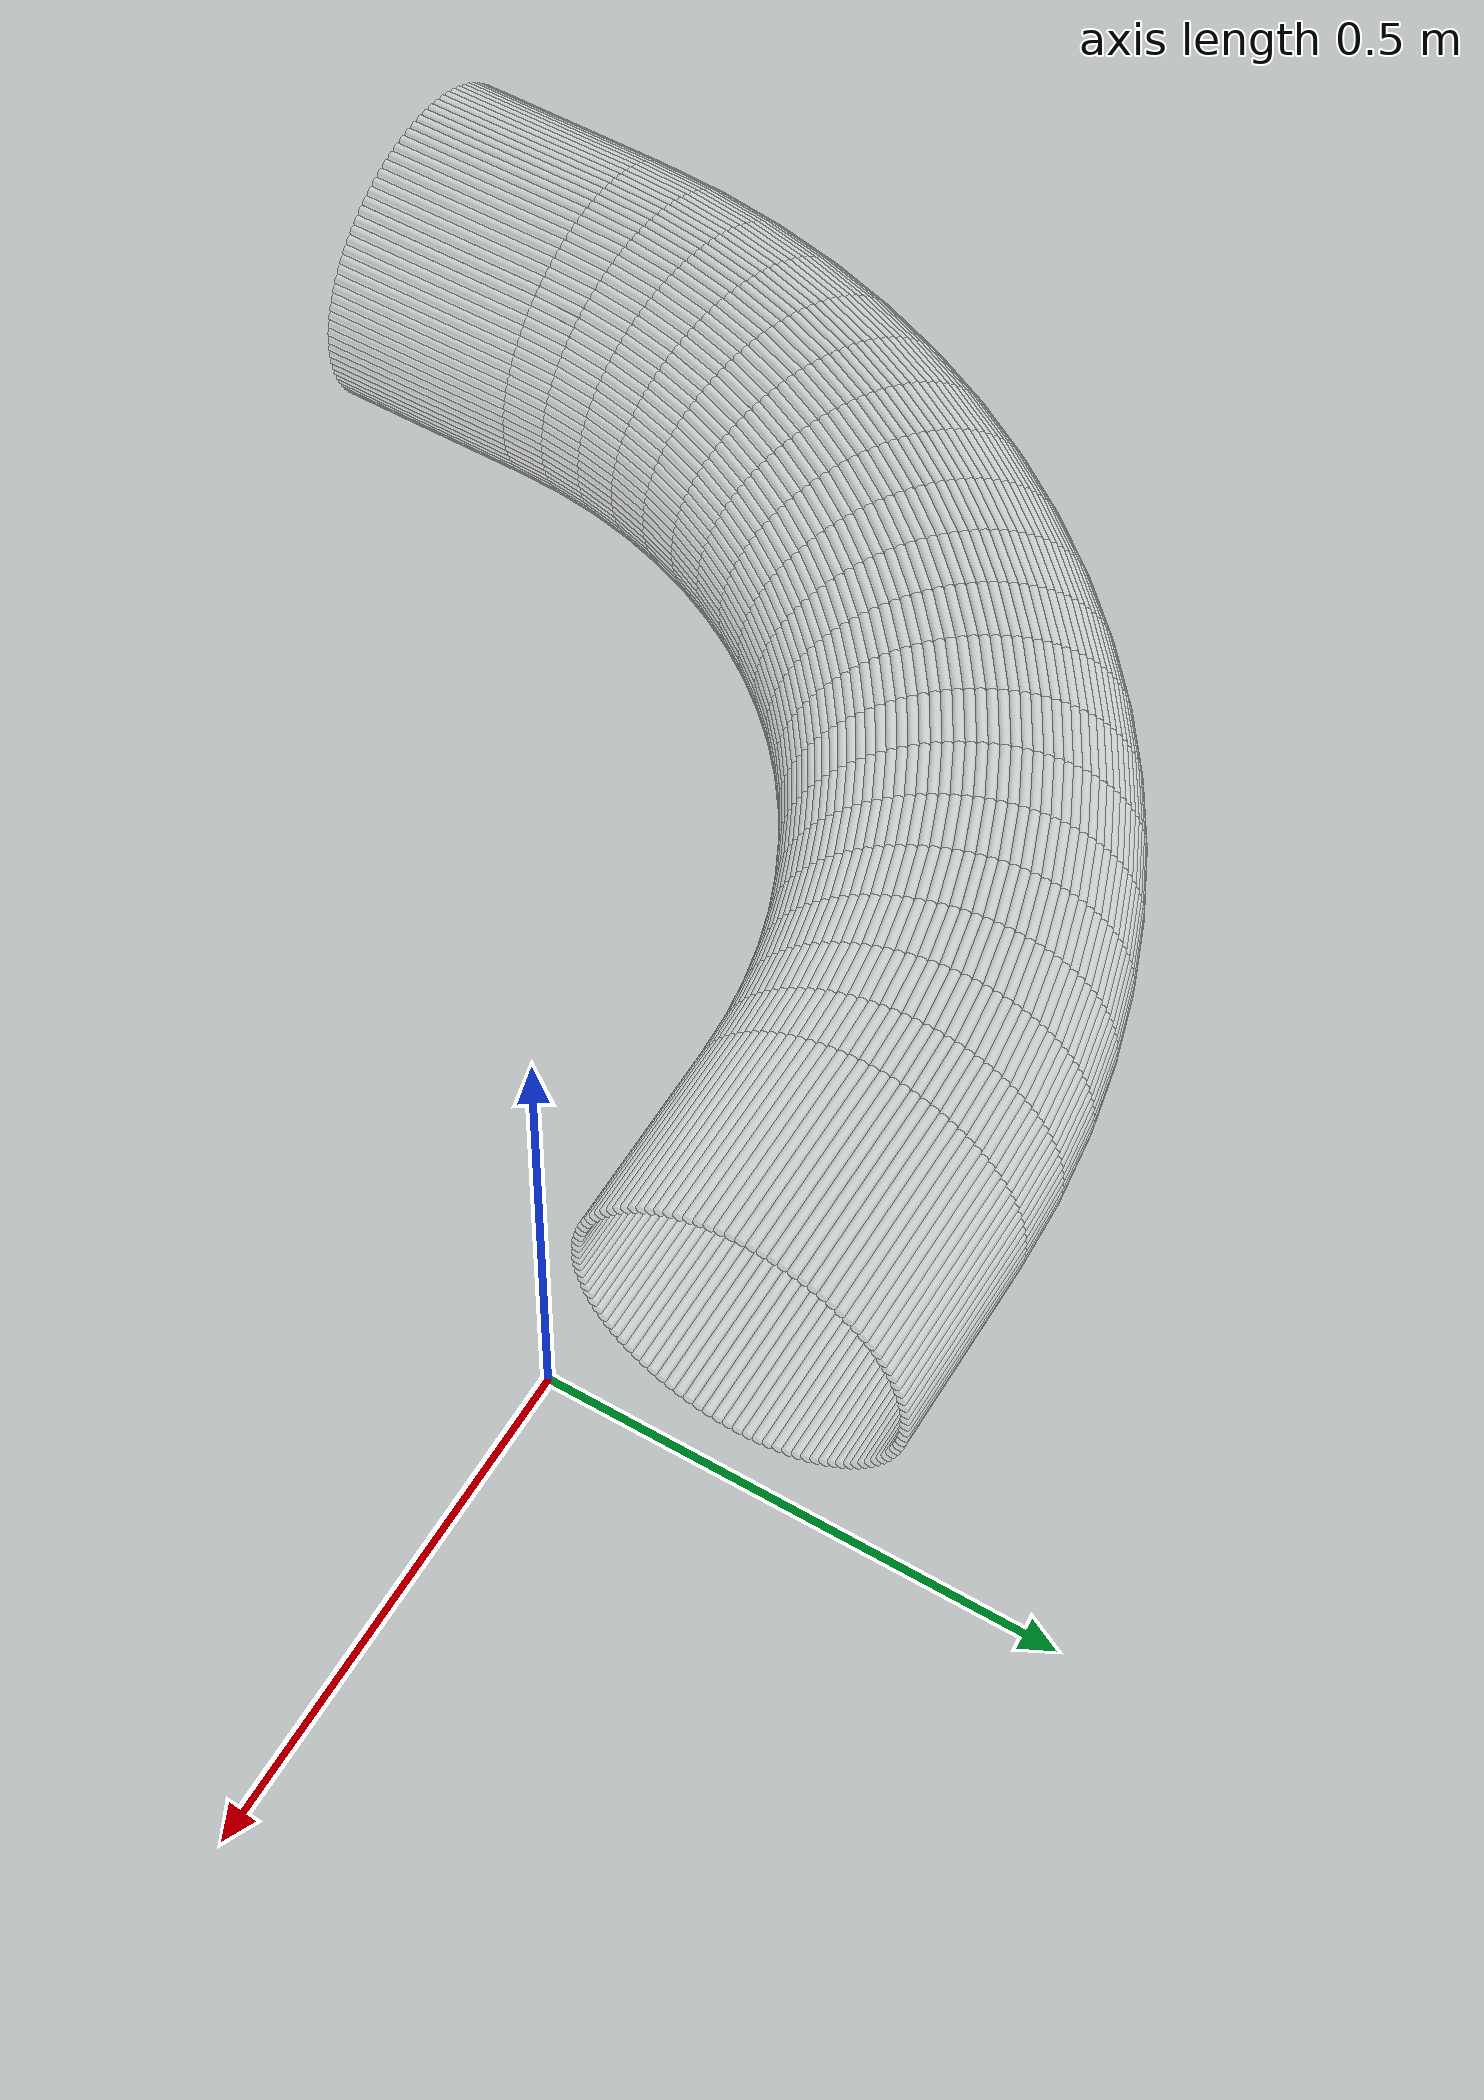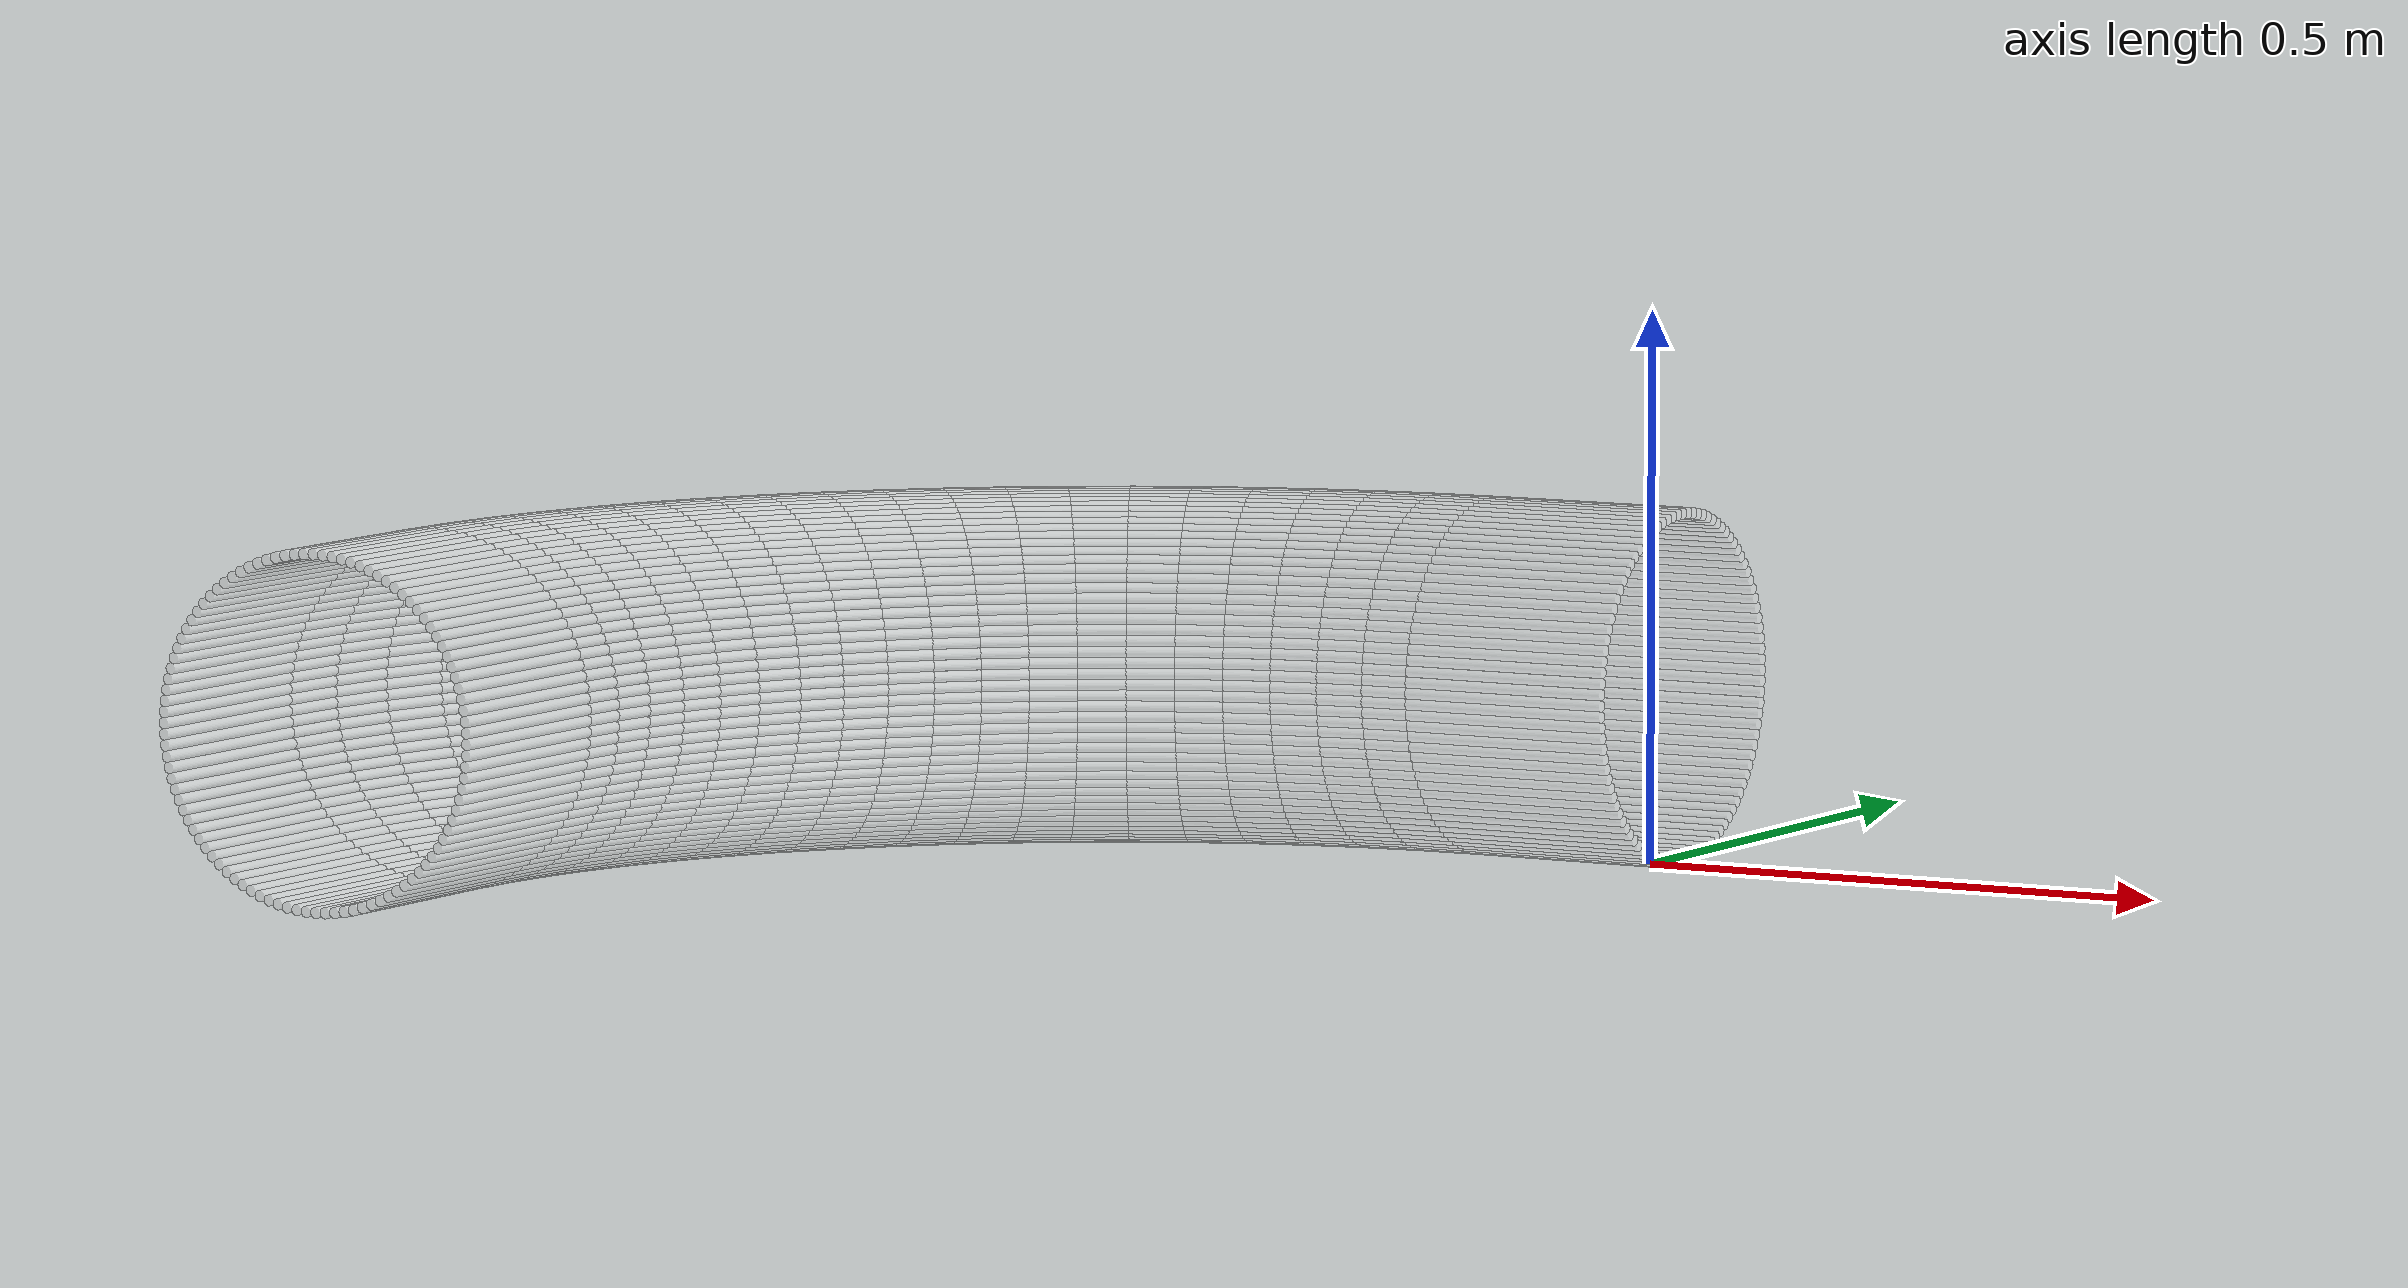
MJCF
<?xml version="1.0" encoding="utf-8"?>
<mujoco>
   <worldbody>
   <body pos="-0.25 -0.54 -0.02" euler="0 0 90">
      <geom euler=" 0 10 0 " fromto="0.86 -0.2 0.16 0.86 0 0.16" rgba="1 1 1 0.35"
            size="0.0050257"
            type="cylinder"/>
      <geom euler=" 0 20 0 " fromto="0.85968 -0.2 0.17005 0.85968 0 0.17005"
            rgba="1 1 1 0.35"
            size="0.0050257"
            type="cylinder"/>
      <geom euler=" 0 30 0 " fromto="0.85874 -0.2 0.18005 0.85874 0 0.18005"
            rgba="1 1 1 0.35"
            size="0.0050257"
            type="cylinder"/>
      <geom euler=" 0 40 0 " fromto="0.85717 -0.2 0.18998 0.85717 0 0.18998"
            rgba="1 1 1 0.35"
            size="0.0050257"
            type="cylinder"/>
      <geom euler=" 0 50 0 " fromto="0.85497 -0.2 0.19979 0.85497 0 0.19979"
            rgba="1 1 1 0.35"
            size="0.0050257"
            type="cylinder"/>
      <geom euler=" 0 60 0 " fromto="0.85217 -0.2 0.20944 0.85217 0 0.20944"
            rgba="1 1 1 0.35"
            size="0.0050257"
            type="cylinder"/>
      <geom euler=" 0 70 0 " fromto="0.84876 -0.2 0.2189 0.84876 0 0.2189"
            rgba="1 1 1 0.35"
            size="0.0050257"
            type="cylinder"/>
      <geom euler=" 0 80 0 " fromto="0.84477 -0.2 0.22812 0.84477 0 0.22812"
            rgba="1 1 1 0.35"
            size="0.0050257"
            type="cylinder"/>
      <geom euler=" 0 90 0 " fromto="0.84021 -0.2 0.23708 0.84021 0 0.23708"
            rgba="1 1 1 0.35"
            size="0.0050257"
            type="cylinder"/>
      <geom euler=" 0 100 0 " fromto="0.83509 -0.2 0.24573 0.83509 0 0.24573"
            rgba="1 1 1 0.35"
            size="0.0050257"
            type="cylinder"/>
      <geom euler=" 0 110 0 " fromto="0.82944 -0.2 0.25405 0.82944 0 0.25405"
            rgba="1 1 1 0.35"
            size="0.0050257"
            type="cylinder"/>
      <geom euler=" 0 120 0 " fromto="0.82328 -0.2 0.26199 0.82328 0 0.26199"
            rgba="1 1 1 0.35"
            size="0.0050257"
            type="cylinder"/>
      <geom euler=" 0 130 0 " fromto="0.81663 -0.2 0.26953 0.81663 0 0.26953"
            rgba="1 1 1 0.35"
            size="0.0050257"
            type="cylinder"/>
      <geom euler=" 0 140 0 " fromto="0.80953 -0.2 0.27663 0.80953 0 0.27663"
            rgba="1 1 1 0.35"
            size="0.0050257"
            type="cylinder"/>
      <geom euler=" 0 150 0 " fromto="0.80199 -0.2 0.28328 0.80199 0 0.28328"
            rgba="1 1 1 0.35"
            size="0.0050257"
            type="cylinder"/>
      <geom euler=" 0 160 0 " fromto="0.79405 -0.2 0.28944 0.79405 0 0.28944"
            rgba="1 1 1 0.35"
            size="0.0050257"
            type="cylinder"/>
      <geom euler=" 0 170 0 " fromto="0.78573 -0.2 0.29509 0.78573 0 0.29509"
            rgba="1 1 1 0.35"
            size="0.0050257"
            type="cylinder"/>
      <geom euler=" 0 180 0 " fromto="0.77708 -0.2 0.30021 0.77708 0 0.30021"
            rgba="1 1 1 0.35"
            size="0.0050257"
            type="cylinder"/>
      <geom euler=" 0 190 0 " fromto="0.76812 -0.2 0.30477 0.76812 0 0.30477"
            rgba="1 1 1 0.35"
            size="0.0050257"
            type="cylinder"/>
      <geom euler=" 0 200 0 " fromto="0.7589 -0.2 0.30876 0.7589 0 0.30876"
            rgba="1 1 1 0.35"
            size="0.0050257"
            type="cylinder"/>
      <geom euler=" 0 210 0 " fromto="0.74944 -0.2 0.31217 0.74944 0 0.31217"
            rgba="1 1 1 0.35"
            size="0.0050257"
            type="cylinder"/>
      <geom euler=" 0 220 0 " fromto="0.73979 -0.2 0.31497 0.73979 0 0.31497"
            rgba="1 1 1 0.35"
            size="0.0050257"
            type="cylinder"/>
      <geom euler=" 0 230 0 " fromto="0.72998 -0.2 0.31717 0.72998 0 0.31717"
            rgba="1 1 1 0.35"
            size="0.0050257"
            type="cylinder"/>
      <geom euler=" 0 240 0 " fromto="0.72005 -0.2 0.31874 0.72005 0 0.31874"
            rgba="1 1 1 0.35"
            size="0.0050257"
            type="cylinder"/>
      <geom euler=" 0 250 0 " fromto="0.71005 -0.2 0.31968 0.71005 0 0.31968"
            rgba="1 1 1 0.35"
            size="0.0050257"
            type="cylinder"/>
      <geom euler=" 0 260 0 " fromto="0.7 -0.2 0.32 0.7 0 0.32" rgba="1 1 1 0.35"
            size="0.0050257"
            type="cylinder"/>
      <geom euler=" 0 270 0 " fromto="0.68995 -0.2 0.31968 0.68995 0 0.31968"
            rgba="1 1 1 0.35"
            size="0.0050257"
            type="cylinder"/>
      <geom euler=" 0 280 0 " fromto="0.67995 -0.2 0.31874 0.67995 0 0.31874"
            rgba="1 1 1 0.35"
            size="0.0050257"
            type="cylinder"/>
      <geom euler=" 0 290 0 " fromto="0.67002 -0.2 0.31717 0.67002 0 0.31717"
            rgba="1 1 1 0.35"
            size="0.0050257"
            type="cylinder"/>
      <geom euler=" 0 300 0 " fromto="0.66021 -0.2 0.31497 0.66021 0 0.31497"
            rgba="1 1 1 0.35"
            size="0.0050257"
            type="cylinder"/>
      <geom euler=" 0 310 0 " fromto="0.65056 -0.2 0.31217 0.65056 0 0.31217"
            rgba="1 1 1 0.35"
            size="0.0050257"
            type="cylinder"/>
      <geom euler=" 0 320 0 " fromto="0.6411 -0.2 0.30876 0.6411 0 0.30876"
            rgba="1 1 1 0.35"
            size="0.0050257"
            type="cylinder"/>
      <geom euler=" 0 330 0 " fromto="0.63188 -0.2 0.30477 0.63188 0 0.30477"
            rgba="1 1 1 0.35"
            size="0.0050257"
            type="cylinder"/>
      <geom euler=" 0 340 0 " fromto="0.62292 -0.2 0.30021 0.62292 0 0.30021"
            rgba="1 1 1 0.35"
            size="0.0050257"
            type="cylinder"/>
      <geom euler=" 0 350 0 " fromto="0.61427 -0.2 0.29509 0.61427 0 0.29509"
            rgba="1 1 1 0.35"
            size="0.0050257"
            type="cylinder"/>
      <geom euler=" 0 360 0 " fromto="0.60595 -0.2 0.28944 0.60595 0 0.28944"
            rgba="1 1 1 0.35"
            size="0.0050257"
            type="cylinder"/>
      <geom euler=" 0 370 0 " fromto="0.59801 -0.2 0.28328 0.59801 0 0.28328"
            rgba="1 1 1 0.35"
            size="0.0050257"
            type="cylinder"/>
      <geom euler=" 0 380 0 " fromto="0.59047 -0.2 0.27663 0.59047 0 0.27663"
            rgba="1 1 1 0.35"
            size="0.0050257"
            type="cylinder"/>
      <geom euler=" 0 390 0 " fromto="0.58337 -0.2 0.26953 0.58337 0 0.26953"
            rgba="1 1 1 0.35"
            size="0.0050257"
            type="cylinder"/>
      <geom euler=" 0 400 0 " fromto="0.57672 -0.2 0.26199 0.57672 0 0.26199"
            rgba="1 1 1 0.35"
            size="0.0050257"
            type="cylinder"/>
      <geom euler=" 0 410 0 " fromto="0.57056 -0.2 0.25405 0.57056 0 0.25405"
            rgba="1 1 1 0.35"
            size="0.0050257"
            type="cylinder"/>
      <geom euler=" 0 420 0 " fromto="0.56491 -0.2 0.24573 0.56491 0 0.24573"
            rgba="1 1 1 0.35"
            size="0.0050257"
            type="cylinder"/>
      <geom euler=" 0 430 0 " fromto="0.55979 -0.2 0.23708 0.55979 0 0.23708"
            rgba="1 1 1 0.35"
            size="0.0050257"
            type="cylinder"/>
      <geom euler=" 0 440 0 " fromto="0.55523 -0.2 0.22812 0.55523 0 0.22812"
            rgba="1 1 1 0.35"
            size="0.0050257"
            type="cylinder"/>
      <geom euler=" 0 450 0 " fromto="0.55124 -0.2 0.2189 0.55124 0 0.2189"
            rgba="1 1 1 0.35"
            size="0.0050257"
            type="cylinder"/>
      <geom euler=" 0 460 0 " fromto="0.54783 -0.2 0.20944 0.54783 0 0.20944"
            rgba="1 1 1 0.35"
            size="0.0050257"
            type="cylinder"/>
      <geom euler=" 0 470 0 " fromto="0.54503 -0.2 0.19979 0.54503 0 0.19979"
            rgba="1 1 1 0.35"
            size="0.0050257"
            type="cylinder"/>
      <geom euler=" 0 480 0 " fromto="0.54283 -0.2 0.18998 0.54283 0 0.18998"
            rgba="1 1 1 0.35"
            size="0.0050257"
            type="cylinder"/>
      <geom euler=" 0 490 0 " fromto="0.54126 -0.2 0.18005 0.54126 0 0.18005"
            rgba="1 1 1 0.35"
            size="0.0050257"
            type="cylinder"/>
      <geom euler=" 0 500 0 " fromto="0.54032 -0.2 0.17005 0.54032 0 0.17005"
            rgba="1 1 1 0.35"
            size="0.0050257"
            type="cylinder"/>
      <geom euler=" 0 510 0 " fromto="0.54 -0.2 0.16 0.54 0 0.16" rgba="1 1 1 0.35"
            size="0.0050257"
            type="cylinder"/>
      <geom euler=" 0 520 0 " fromto="0.54032 -0.2 0.14995 0.54032 0 0.14995"
            rgba="1 1 1 0.35"
            size="0.0050257"
            type="cylinder"/>
      <geom euler=" 0 530 0 " fromto="0.54126 -0.2 0.13995 0.54126 0 0.13995"
            rgba="1 1 1 0.35"
            size="0.0050257"
            type="cylinder"/>
      <geom euler=" 0 540 0 " fromto="0.54283 -0.2 0.13002 0.54283 0 0.13002"
            rgba="1 1 1 0.35"
            size="0.0050257"
            type="cylinder"/>
      <geom euler=" 0 550 0 " fromto="0.54503 -0.2 0.12021 0.54503 0 0.12021"
            rgba="1 1 1 0.35"
            size="0.0050257"
            type="cylinder"/>
      <geom euler=" 0 560 0 " fromto="0.54783 -0.2 0.11056 0.54783 0 0.11056"
            rgba="1 1 1 0.35"
            size="0.0050257"
            type="cylinder"/>
      <geom euler=" 0 570 0 " fromto="0.55124 -0.2 0.1011 0.55124 0 0.1011"
            rgba="1 1 1 0.35"
            size="0.0050257"
            type="cylinder"/>
      <geom euler=" 0 580 0 " fromto="0.55523 -0.2 0.091875 0.55523 0 0.091875"
            rgba="1 1 1 0.35"
            size="0.0050257"
            type="cylinder"/>
      <geom euler=" 0 590 0 " fromto="0.55979 -0.2 0.082919 0.55979 0 0.082919"
            rgba="1 1 1 0.35"
            size="0.0050257"
            type="cylinder"/>
      <geom euler=" 0 600 0 " fromto="0.56491 -0.2 0.074268 0.56491 0 0.074268"
            rgba="1 1 1 0.35"
            size="0.0050257"
            type="cylinder"/>
      <geom euler=" 0 610 0 " fromto="0.57056 -0.2 0.065954 0.57056 0 0.065954"
            rgba="1 1 1 0.35"
            size="0.0050257"
            type="cylinder"/>
      <geom euler=" 0 620 0 " fromto="0.57672 -0.2 0.058012 0.57672 0 0.058012"
            rgba="1 1 1 0.35"
            size="0.0050257"
            type="cylinder"/>
      <geom euler=" 0 630 0 " fromto="0.58337 -0.2 0.050472 0.58337 0 0.050472"
            rgba="1 1 1 0.35"
            size="0.0050257"
            type="cylinder"/>
      <geom euler=" 0 640 0 " fromto="0.59047 -0.2 0.043365 0.59047 0 0.043365"
            rgba="1 1 1 0.35"
            size="0.0050257"
            type="cylinder"/>
      <geom euler=" 0 650 0 " fromto="0.59801 -0.2 0.036718 0.59801 0 0.036718"
            rgba="1 1 1 0.35"
            size="0.0050257"
            type="cylinder"/>
      <geom euler=" 0 660 0 " fromto="0.60595 -0.2 0.030557 0.60595 0 0.030557"
            rgba="1 1 1 0.35"
            size="0.0050257"
            type="cylinder"/>
      <geom euler=" 0 670 0 " fromto="0.61427 -0.2 0.024908 0.61427 0 0.024908"
            rgba="1 1 1 0.35"
            size="0.0050257"
            type="cylinder"/>
      <geom euler=" 0 680 0 " fromto="0.62292 -0.2 0.019791 0.62292 0 0.019791"
            rgba="1 1 1 0.35"
            size="0.0050257"
            type="cylinder"/>
      <geom euler=" 0 690 0 " fromto="0.63188 -0.2 0.015228 0.63188 0 0.015228"
            rgba="1 1 1 0.35"
            size="0.0050257"
            type="cylinder"/>
      <geom euler=" 0 700 0 " fromto="0.6411 -0.2 0.011236 0.6411 0 0.011236"
            rgba="1 1 1 0.35"
            size="0.0050257"
            type="cylinder"/>
      <geom euler=" 0 710 0 " fromto="0.65056 -0.2 0.007831 0.65056 0 0.007831"
            rgba="1 1 1 0.35"
            size="0.0050257"
            type="cylinder"/>
      <geom euler=" 0 720 0 " fromto="0.66021 -0.2 0.0050267 0.66021 0 0.0050267"
            rgba="1 1 1 0.35"
            size="0.0050257"
            type="cylinder"/>
      <geom euler=" 0 730 0 " fromto="0.67002 -0.2 0.002834 0.67002 0 0.002834"
            rgba="1 1 1 0.35"
            size="0.0050257"
            type="cylinder"/>
      <geom euler=" 0 740 0 " fromto="0.67995 -0.2 0.0012616 0.67995 0 0.0012616"
            rgba="1 1 1 0.35"
            size="0.0050257"
            type="cylinder"/>
      <geom euler=" 0 750 0 " fromto="0.68995 -0.2 0.00031572 0.68995 0 0.00031572"
            rgba="1 1 1 0.35"
            size="0.0050257"
            type="cylinder"/>
      <geom euler=" 0 760 0 " fromto="0.7 -0.2 0 0.7 0 0" rgba="1 1 1 0.35"
            size="0.0050257"
            type="cylinder"/>
      <geom euler=" 0 770 0 " fromto="0.71005 -0.2 0.00031572 0.71005 0 0.00031572"
            rgba="1 1 1 0.35"
            size="0.0050257"
            type="cylinder"/>
      <geom euler=" 0 780 0 " fromto="0.72005 -0.2 0.0012616 0.72005 0 0.0012616"
            rgba="1 1 1 0.35"
            size="0.0050257"
            type="cylinder"/>
      <geom euler=" 0 790 0 " fromto="0.72998 -0.2 0.002834 0.72998 0 0.002834"
            rgba="1 1 1 0.35"
            size="0.0050257"
            type="cylinder"/>
      <geom euler=" 0 800 0 " fromto="0.73979 -0.2 0.0050267 0.73979 0 0.0050267"
            rgba="1 1 1 0.35"
            size="0.0050257"
            type="cylinder"/>
      <geom euler=" 0 810 0 " fromto="0.74944 -0.2 0.007831 0.74944 0 0.007831"
            rgba="1 1 1 0.35"
            size="0.0050257"
            type="cylinder"/>
      <geom euler=" 0 820 0 " fromto="0.7589 -0.2 0.011236 0.7589 0 0.011236"
            rgba="1 1 1 0.35"
            size="0.0050257"
            type="cylinder"/>
      <geom euler=" 0 830 0 " fromto="0.76812 -0.2 0.015228 0.76812 0 0.015228"
            rgba="1 1 1 0.35"
            size="0.0050257"
            type="cylinder"/>
      <geom euler=" 0 840 0 " fromto="0.77708 -0.2 0.019791 0.77708 0 0.019791"
            rgba="1 1 1 0.35"
            size="0.0050257"
            type="cylinder"/>
      <geom euler=" 0 850 0 " fromto="0.78573 -0.2 0.024908 0.78573 0 0.024908"
            rgba="1 1 1 0.35"
            size="0.0050257"
            type="cylinder"/>
      <geom euler=" 0 860 0 " fromto="0.79405 -0.2 0.030557 0.79405 0 0.030557"
            rgba="1 1 1 0.35"
            size="0.0050257"
            type="cylinder"/>
      <geom euler=" 0 870 0 " fromto="0.80199 -0.2 0.036718 0.80199 0 0.036718"
            rgba="1 1 1 0.35"
            size="0.0050257"
            type="cylinder"/>
      <geom euler=" 0 880 0 " fromto="0.80953 -0.2 0.043365 0.80953 0 0.043365"
            rgba="1 1 1 0.35"
            size="0.0050257"
            type="cylinder"/>
      <geom euler=" 0 890 0 " fromto="0.81663 -0.2 0.050472 0.81663 0 0.050472"
            rgba="1 1 1 0.35"
            size="0.0050257"
            type="cylinder"/>
      <geom euler=" 0 900 0 " fromto="0.82328 -0.2 0.058012 0.82328 0 0.058012"
            rgba="1 1 1 0.35"
            size="0.0050257"
            type="cylinder"/>
      <geom euler=" 0 910 0 " fromto="0.82944 -0.2 0.065954 0.82944 0 0.065954"
            rgba="1 1 1 0.35"
            size="0.0050257"
            type="cylinder"/>
      <geom euler=" 0 920 0 " fromto="0.83509 -0.2 0.074268 0.83509 0 0.074268"
            rgba="1 1 1 0.35"
            size="0.0050257"
            type="cylinder"/>
      <geom euler=" 0 930 0 " fromto="0.84021 -0.2 0.082919 0.84021 0 0.082919"
            rgba="1 1 1 0.35"
            size="0.0050257"
            type="cylinder"/>
      <geom euler=" 0 940 0 " fromto="0.84477 -0.2 0.091875 0.84477 0 0.091875"
            rgba="1 1 1 0.35"
            size="0.0050257"
            type="cylinder"/>
      <geom euler=" 0 950 0 " fromto="0.84876 -0.2 0.1011 0.84876 0 0.1011"
            rgba="1 1 1 0.35"
            size="0.0050257"
            type="cylinder"/>
      <geom euler=" 0 960 0 " fromto="0.85217 -0.2 0.11056 0.85217 0 0.11056"
            rgba="1 1 1 0.35"
            size="0.0050257"
            type="cylinder"/>
      <geom euler=" 0 970 0 " fromto="0.85497 -0.2 0.12021 0.85497 0 0.12021"
            rgba="1 1 1 0.35"
            size="0.0050257"
            type="cylinder"/>
      <geom euler=" 0 980 0 " fromto="0.85717 -0.2 0.13002 0.85717 0 0.13002"
            rgba="1 1 1 0.35"
            size="0.0050257"
            type="cylinder"/>
      <geom euler=" 0 990 0 " fromto="0.85874 -0.2 0.13995 0.85874 0 0.13995"
            rgba="1 1 1 0.35"
            size="0.0050257"
            type="cylinder"/>
      <geom euler=" 0 1000 0 " fromto="0.85968 -0.2 0.14995 0.85968 0 0.14995"
            rgba="1 1 1 0.35"
            size="0.0050257"
            type="cylinder"/>
      <geom euler=" 0 10 0 " fromto="0.86 0 0.16 0.85706 0.071018 0.16" rgba="1 1 1 0.35"
            size="0.0050257"
            type="cylinder"/>
      <geom euler=" 0 20 0 " fromto="0.85968 0 0.17005 0.85675 0.070992 0.17005"
            rgba="1 1 1 0.35"
            size="0.0050257"
            type="cylinder"/>
      <geom euler=" 0 30 0 " fromto="0.85874 0 0.18005 0.85581 0.070914 0.18005"
            rgba="1 1 1 0.35"
            size="0.0050257"
            type="cylinder"/>
      <geom euler=" 0 40 0 " fromto="0.85717 0 0.18998 0.85424 0.070784 0.18998"
            rgba="1 1 1 0.35"
            size="0.0050257"
            type="cylinder"/>
      <geom euler=" 0 50 0 " fromto="0.85497 0 0.19979 0.85205 0.070603 0.19979"
            rgba="1 1 1 0.35"
            size="0.0050257"
            type="cylinder"/>
      <geom euler=" 0 60 0 " fromto="0.85217 0 0.20944 0.84926 0.070372 0.20944"
            rgba="1 1 1 0.35"
            size="0.0050257"
            type="cylinder"/>
      <geom euler=" 0 70 0 " fromto="0.84876 0 0.2189 0.84587 0.07009 0.2189"
            rgba="1 1 1 0.35"
            size="0.0050257"
            type="cylinder"/>
      <geom euler=" 0 80 0 " fromto="0.84477 0 0.22812 0.84189 0.069761 0.22812"
            rgba="1 1 1 0.35"
            size="0.0050257"
            type="cylinder"/>
      <geom euler=" 0 90 0 " fromto="0.84021 0 0.23708 0.83734 0.069384 0.23708"
            rgba="1 1 1 0.35"
            size="0.0050257"
            type="cylinder"/>
      <geom euler=" 0 100 0 " fromto="0.83509 0 0.24573 0.83224 0.068961 0.24573"
            rgba="1 1 1 0.35"
            size="0.0050257"
            type="cylinder"/>
      <geom euler=" 0 110 0 " fromto="0.82944 0 0.25405 0.82661 0.068495 0.25405"
            rgba="1 1 1 0.35"
            size="0.0050257"
            type="cylinder"/>
      <geom euler=" 0 120 0 " fromto="0.82328 0 0.26199 0.82047 0.067986 0.26199"
            rgba="1 1 1 0.35"
            size="0.0050257"
            type="cylinder"/>
      <geom euler=" 0 130 0 " fromto="0.81663 0 0.26953 0.81385 0.067437 0.26953"
            rgba="1 1 1 0.35"
            size="0.0050257"
            type="cylinder"/>
      <geom euler=" 0 140 0 " fromto="0.80953 0 0.27663 0.80676 0.06685 0.27663"
            rgba="1 1 1 0.35"
            size="0.0050257"
            type="cylinder"/>
      <geom euler=" 0 150 0 " fromto="0.80199 0 0.28328 0.79925 0.066228 0.28328"
            rgba="1 1 1 0.35"
            size="0.0050257"
            type="cylinder"/>
      <geom euler=" 0 160 0 " fromto="0.79405 0 0.28944 0.79133 0.065572 0.28944"
            rgba="1 1 1 0.35"
            size="0.0050257"
            type="cylinder"/>
      <geom euler=" 0 170 0 " fromto="0.78573 0 0.29509 0.78305 0.064885 0.29509"
            rgba="1 1 1 0.35"
            size="0.0050257"
            type="cylinder"/>
      <geom euler=" 0 180 0 " fromto="0.77708 0 0.30021 0.77443 0.064171 0.30021"
            rgba="1 1 1 0.35"
            size="0.0050257"
            type="cylinder"/>
      <geom euler=" 0 190 0 " fromto="0.76812 0 0.30477 0.7655 0.063431 0.30477"
            rgba="1 1 1 0.35"
            size="0.0050257"
            type="cylinder"/>
      <geom euler=" 0 200 0 " fromto="0.7589 0 0.30876 0.75631 0.062669 0.30876"
            rgba="1 1 1 0.35"
            size="0.0050257"
            type="cylinder"/>
      <geom euler=" 0 210 0 " fromto="0.74944 0 0.31217 0.74688 0.061888 0.31217"
            rgba="1 1 1 0.35"
            size="0.0050257"
            type="cylinder"/>
      <geom euler=" 0 220 0 " fromto="0.73979 0 0.31497 0.73726 0.061091 0.31497"
            rgba="1 1 1 0.35"
            size="0.0050257"
            type="cylinder"/>
      <geom euler=" 0 230 0 " fromto="0.72998 0 0.31717 0.72749 0.060281 0.31717"
            rgba="1 1 1 0.35"
            size="0.0050257"
            type="cylinder"/>
      <geom euler=" 0 240 0 " fromto="0.72005 0 0.31874 0.71759 0.059462 0.31874"
            rgba="1 1 1 0.35"
            size="0.0050257"
            type="cylinder"/>
      <geom euler=" 0 250 0 " fromto="0.71005 0 0.31968 0.70762 0.058635 0.31968"
            rgba="1 1 1 0.35"
            size="0.0050257"
            type="cylinder"/>
      <geom euler=" 0 260 0 " fromto="0.7 0 0.32 0.69761 0.057806 0.32" rgba="1 1 1 0.35"
            size="0.0050257"
            type="cylinder"/>
      <geom euler=" 0 270 0 " fromto="0.68995 0 0.31968 0.6876 0.056976 0.31968"
            rgba="1 1 1 0.35"
            size="0.0050257"
            type="cylinder"/>
      <geom euler=" 0 280 0 " fromto="0.67995 0 0.31874 0.67762 0.05615 0.31874"
            rgba="1 1 1 0.35"
            size="0.0050257"
            type="cylinder"/>
      <geom euler=" 0 290 0 " fromto="0.67002 0 0.31717 0.66773 0.05533 0.31717"
            rgba="1 1 1 0.35"
            size="0.0050257"
            type="cylinder"/>
      <geom euler=" 0 300 0 " fromto="0.66021 0 0.31497 0.65795 0.05452 0.31497"
            rgba="1 1 1 0.35"
            size="0.0050257"
            type="cylinder"/>
      <geom euler=" 0 310 0 " fromto="0.65056 0 0.31217 0.64834 0.053723 0.31217"
            rgba="1 1 1 0.35"
            size="0.0050257"
            type="cylinder"/>
      <geom euler=" 0 320 0 " fromto="0.6411 0 0.30876 0.63891 0.052942 0.30876"
            rgba="1 1 1 0.35"
            size="0.0050257"
            type="cylinder"/>
      <geom euler=" 0 330 0 " fromto="0.63188 0 0.30477 0.62972 0.05218 0.30477"
            rgba="1 1 1 0.35"
            size="0.0050257"
            type="cylinder"/>
      <geom euler=" 0 340 0 " fromto="0.62292 0 0.30021 0.62079 0.05144 0.30021"
            rgba="1 1 1 0.35"
            size="0.0050257"
            type="cylinder"/>
      <geom euler=" 0 350 0 " fromto="0.61427 0 0.29509 0.61217 0.050726 0.29509"
            rgba="1 1 1 0.35"
            size="0.0050257"
            type="cylinder"/>
      <geom euler=" 0 360 0 " fromto="0.60595 0 0.28944 0.60388 0.050039 0.28944"
            rgba="1 1 1 0.35"
            size="0.0050257"
            type="cylinder"/>
      <geom euler=" 0 370 0 " fromto="0.59801 0 0.28328 0.59597 0.049383 0.28328"
            rgba="1 1 1 0.35"
            size="0.0050257"
            type="cylinder"/>
      <geom euler=" 0 380 0 " fromto="0.59047 0 0.27663 0.58846 0.048761 0.27663"
            rgba="1 1 1 0.35"
            size="0.0050257"
            type="cylinder"/>
      <geom euler=" 0 390 0 " fromto="0.58337 0 0.26953 0.58137 0.048174 0.26953"
            rgba="1 1 1 0.35"
            size="0.0050257"
            type="cylinder"/>
      <geom euler=" 0 400 0 " fromto="0.57672 0 0.26199 0.57475 0.047625 0.26199"
            rgba="1 1 1 0.35"
            size="0.0050257"
            type="cylinder"/>
      <geom euler=" 0 410 0 " fromto="0.57056 0 0.25405 0.56861 0.047116 0.25405"
            rgba="1 1 1 0.35"
            size="0.0050257"
            type="cylinder"/>
      <geom euler=" 0 420 0 " fromto="0.56491 0 0.24573 0.56298 0.04665 0.24573"
            rgba="1 1 1 0.35"
            size="0.0050257"
            type="cylinder"/>
      <geom euler=" 0 430 0 " fromto="0.55979 0 0.23708 0.55788 0.046227 0.23708"
            rgba="1 1 1 0.35"
            size="0.0050257"
            type="cylinder"/>
      <geom euler=" 0 440 0 " fromto="0.55523 0 0.22812 0.55333 0.04585 0.22812"
            rgba="1 1 1 0.35"
            size="0.0050257"
            type="cylinder"/>
      <geom euler=" 0 450 0 " fromto="0.55124 0 0.2189 0.54935 0.045521 0.2189"
            rgba="1 1 1 0.35"
            size="0.0050257"
            type="cylinder"/>
      <geom euler=" 0 460 0 " fromto="0.54783 0 0.20944 0.54596 0.04524 0.20944"
            rgba="1 1 1 0.35"
            size="0.0050257"
            type="cylinder"/>
      <geom euler=" 0 470 0 " fromto="0.54503 0 0.19979 0.54317 0.045008 0.19979"
            rgba="1 1 1 0.35"
            size="0.0050257"
            type="cylinder"/>
      <geom euler=" 0 480 0 " fromto="0.54283 0 0.18998 0.54098 0.044827 0.18998"
            rgba="1 1 1 0.35"
            size="0.0050257"
            type="cylinder"/>
      <geom euler=" 0 490 0 " fromto="0.54126 0 0.18005 0.53941 0.044697 0.18005"
            rgba="1 1 1 0.35"
            size="0.0050257"
            type="cylinder"/>
      <geom euler=" 0 500 0 " fromto="0.54032 0 0.17005 0.53847 0.044619 0.17005"
            rgba="1 1 1 0.35"
            size="0.0050257"
            type="cylinder"/>
      <geom euler=" 0 510 0 " fromto="0.54 0 0.16 0.53816 0.044593 0.16" rgba="1 1 1 0.35"
            size="0.0050257"
            type="cylinder"/>
      <geom euler=" 0 520 0 " fromto="0.54032 0 0.14995 0.53847 0.044619 0.14995"
            rgba="1 1 1 0.35"
            size="0.0050257"
            type="cylinder"/>
      <geom euler=" 0 530 0 " fromto="0.54126 0 0.13995 0.53941 0.044697 0.13995"
            rgba="1 1 1 0.35"
            size="0.0050257"
            type="cylinder"/>
      <geom euler=" 0 540 0 " fromto="0.54283 0 0.13002 0.54098 0.044827 0.13002"
            rgba="1 1 1 0.35"
            size="0.0050257"
            type="cylinder"/>
      <geom euler=" 0 550 0 " fromto="0.54503 0 0.12021 0.54317 0.045008 0.12021"
            rgba="1 1 1 0.35"
            size="0.0050257"
            type="cylinder"/>
      <geom euler=" 0 560 0 " fromto="0.54783 0 0.11056 0.54596 0.04524 0.11056"
            rgba="1 1 1 0.35"
            size="0.0050257"
            type="cylinder"/>
      <geom euler=" 0 570 0 " fromto="0.55124 0 0.1011 0.54935 0.045521 0.1011"
            rgba="1 1 1 0.35"
            size="0.0050257"
            type="cylinder"/>
      <geom euler=" 0 580 0 " fromto="0.55523 0 0.091875 0.55333 0.04585 0.091875"
            rgba="1 1 1 0.35"
            size="0.0050257"
            type="cylinder"/>
      <geom euler=" 0 590 0 " fromto="0.55979 0 0.082919 0.55788 0.046227 0.082919"
            rgba="1 1 1 0.35"
            size="0.0050257"
            type="cylinder"/>
      <geom euler=" 0 600 0 " fromto="0.56491 0 0.074268 0.56298 0.04665 0.074268"
            rgba="1 1 1 0.35"
            size="0.0050257"
            type="cylinder"/>
      <geom euler=" 0 610 0 " fromto="0.57056 0 0.065954 0.56861 0.047116 0.065954"
            rgba="1 1 1 0.35"
            size="0.0050257"
            type="cylinder"/>
      <geom euler=" 0 620 0 " fromto="0.57672 0 0.058012 0.57475 0.047625 0.058012"
            rgba="1 1 1 0.35"
            size="0.0050257"
            type="cylinder"/>
      <geom euler=" 0 630 0 " fromto="0.58337 0 0.050472 0.58137 0.048174 0.050472"
            rgba="1 1 1 0.35"
            size="0.0050257"
            type="cylinder"/>
      <geom euler=" 0 640 0 " fromto="0.59047 0 0.043365 0.58846 0.048761 0.043365"
            rgba="1 1 1 0.35"
            size="0.0050257"
            type="cylinder"/>
      <geom euler=" 0 650 0 " fromto="0.59801 0 0.036718 0.59597 0.049383 0.036718"
            rgba="1 1 1 0.35"
            size="0.0050257"
            type="cylinder"/>
      <geom euler=" 0 660 0 " fromto="0.60595 0 0.030557 0.60388 0.050039 0.030557"
            rgba="1 1 1 0.35"
            size="0.0050257"
            type="cylinder"/>
      <geom euler=" 0 670 0 " fromto="0.61427 0 0.024908 0.61217 0.050726 0.024908"
            rgba="1 1 1 0.35"
            size="0.0050257"
            type="cylinder"/>
      <geom euler=" 0 680 0 " fromto="0.62292 0 0.019791 0.62079 0.05144 0.019791"
            rgba="1 1 1 0.35"
            size="0.0050257"
            type="cylinder"/>
      <geom euler=" 0 690 0 " fromto="0.63188 0 0.015228 0.62972 0.05218 0.015228"
            rgba="1 1 1 0.35"
            size="0.0050257"
            type="cylinder"/>
      <geom euler=" 0 700 0 " fromto="0.6411 0 0.011236 0.63891 0.052942 0.011236"
            rgba="1 1 1 0.35"
            size="0.0050257"
            type="cylinder"/>
      <geom euler=" 0 710 0 " fromto="0.65056 0 0.007831 0.64834 0.053723 0.007831"
            rgba="1 1 1 0.35"
            size="0.0050257"
            type="cylinder"/>
      <geom euler=" 0 720 0 " fromto="0.66021 0 0.0050267 0.65795 0.05452 0.0050267"
            rgba="1 1 1 0.35"
            size="0.0050257"
            type="cylinder"/>
      <geom euler=" 0 730 0 " fromto="0.67002 0 0.002834 0.66773 0.05533 0.002834"
            rgba="1 1 1 0.35"
            size="0.0050257"
            type="cylinder"/>
      <geom euler=" 0 740 0 " fromto="0.67995 0 0.0012616 0.67762 0.05615 0.0012616"
            rgba="1 1 1 0.35"
            size="0.0050257"
            type="cylinder"/>
      <geom euler=" 0 750 0 " fromto="0.68995 0 0.00031572 0.6876 0.056976 0.00031572"
            rgba="1 1 1 0.35"
            size="0.0050257"
            type="cylinder"/>
      <geom euler=" 0 760 0 " fromto="0.7 0 0 0.69761 0.057806 0" rgba="1 1 1 0.35"
            size="0.0050257"
            type="cylinder"/>
      <geom euler=" 0 770 0 " fromto="0.71005 0 0.00031572 0.70762 0.058635 0.00031572"
            rgba="1 1 1 0.35"
            size="0.0050257"
            type="cylinder"/>
      <geom euler=" 0 780 0 " fromto="0.72005 0 0.0012616 0.71759 0.059462 0.0012616"
            rgba="1 1 1 0.35"
            size="0.0050257"
            type="cylinder"/>
      <geom euler=" 0 790 0 " fromto="0.72998 0 0.002834 0.72749 0.060281 0.002834"
            rgba="1 1 1 0.35"
            size="0.0050257"
            type="cylinder"/>
      <geom euler=" 0 800 0 " fromto="0.73979 0 0.0050267 0.73726 0.061091 0.0050267"
            rgba="1 1 1 0.35"
            size="0.0050257"
            type="cylinder"/>
      <geom euler=" 0 810 0 " fromto="0.74944 0 0.007831 0.74688 0.061888 0.007831"
            rgba="1 1 1 0.35"
            size="0.0050257"
            type="cylinder"/>
      <geom euler=" 0 820 0 " fromto="0.7589 0 0.011236 0.75631 0.062669 0.011236"
            rgba="1 1 1 0.35"
            size="0.0050257"
            type="cylinder"/>
      <geom euler=" 0 830 0 " fromto="0.76812 0 0.015228 0.7655 0.063431 0.015228"
            rgba="1 1 1 0.35"
            size="0.0050257"
            type="cylinder"/>
      <geom euler=" 0 840 0 " fromto="0.77708 0 0.019791 0.77443 0.064171 0.019791"
            rgba="1 1 1 0.35"
            size="0.0050257"
            type="cylinder"/>
      <geom euler=" 0 850 0 " fromto="0.78573 0 0.024908 0.78305 0.064885 0.024908"
            rgba="1 1 1 0.35"
            size="0.0050257"
            type="cylinder"/>
      <geom euler=" 0 860 0 " fromto="0.79405 0 0.030557 0.79133 0.065572 0.030557"
            rgba="1 1 1 0.35"
            size="0.0050257"
            type="cylinder"/>
      <geom euler=" 0 870 0 " fromto="0.80199 0 0.036718 0.79925 0.066228 0.036718"
            rgba="1 1 1 0.35"
            size="0.0050257"
            type="cylinder"/>
      <geom euler=" 0 880 0 " fromto="0.80953 0 0.043365 0.80676 0.06685 0.043365"
            rgba="1 1 1 0.35"
            size="0.0050257"
            type="cylinder"/>
      <geom euler=" 0 890 0 " fromto="0.81663 0 0.050472 0.81385 0.067437 0.050472"
            rgba="1 1 1 0.35"
            size="0.0050257"
            type="cylinder"/>
      <geom euler=" 0 900 0 " fromto="0.82328 0 0.058012 0.82047 0.067986 0.058012"
            rgba="1 1 1 0.35"
            size="0.0050257"
            type="cylinder"/>
      <geom euler=" 0 910 0 " fromto="0.82944 0 0.065954 0.82661 0.068495 0.065954"
            rgba="1 1 1 0.35"
            size="0.0050257"
            type="cylinder"/>
      <geom euler=" 0 920 0 " fromto="0.83509 0 0.074268 0.83224 0.068961 0.074268"
            rgba="1 1 1 0.35"
            size="0.0050257"
            type="cylinder"/>
      <geom euler=" 0 930 0 " fromto="0.84021 0 0.082919 0.83734 0.069384 0.082919"
            rgba="1 1 1 0.35"
            size="0.0050257"
            type="cylinder"/>
      <geom euler=" 0 940 0 " fromto="0.84477 0 0.091875 0.84189 0.069761 0.091875"
            rgba="1 1 1 0.35"
            size="0.0050257"
            type="cylinder"/>
      <geom euler=" 0 950 0 " fromto="0.84876 0 0.1011 0.84587 0.07009 0.1011"
            rgba="1 1 1 0.35"
            size="0.0050257"
            type="cylinder"/>
      <geom euler=" 0 960 0 " fromto="0.85217 0 0.11056 0.84926 0.070372 0.11056"
            rgba="1 1 1 0.35"
            size="0.0050257"
            type="cylinder"/>
      <geom euler=" 0 970 0 " fromto="0.85497 0 0.12021 0.85205 0.070603 0.12021"
            rgba="1 1 1 0.35"
            size="0.0050257"
            type="cylinder"/>
      <geom euler=" 0 980 0 " fromto="0.85717 0 0.13002 0.85424 0.070784 0.13002"
            rgba="1 1 1 0.35"
            size="0.0050257"
            type="cylinder"/>
      <geom euler=" 0 990 0 " fromto="0.85874 0 0.13995 0.85581 0.070914 0.13995"
            rgba="1 1 1 0.35"
            size="0.0050257"
            type="cylinder"/>
      <geom euler=" 0 1000 0 " fromto="0.85968 0 0.14995 0.85675 0.070992 0.14995"
            rgba="1 1 1 0.35"
            size="0.0050257"
            type="cylinder"/>
      <geom euler=" 0 10 0 " fromto="0.85706 0.071018 0.16 0.84827 0.14155 0.16"
            rgba="1 1 1 0.35"
            size="0.0050257"
            type="cylinder"/>
      <geom euler=" 0 20 0 " fromto="0.85675 0.070992 0.17005 0.84796 0.1415 0.17005"
            rgba="1 1 1 0.35"
            size="0.0050257"
            type="cylinder"/>
      <geom euler=" 0 30 0 " fromto="0.85581 0.070914 0.18005 0.84703 0.14134 0.18005"
            rgba="1 1 1 0.35"
            size="0.0050257"
            type="cylinder"/>
      <geom euler=" 0 40 0 " fromto="0.85424 0.070784 0.18998 0.84548 0.14108 0.18998"
            rgba="1 1 1 0.35"
            size="0.0050257"
            type="cylinder"/>
      <geom euler=" 0 50 0 " fromto="0.85205 0.070603 0.19979 0.84331 0.14072 0.19979"
            rgba="1 1 1 0.35"
            size="0.0050257"
            type="cylinder"/>
      <geom euler=" 0 60 0 " fromto="0.84926 0.070372 0.20944 0.84055 0.14026 0.20944"
            rgba="1 1 1 0.35"
            size="0.0050257"
            type="cylinder"/>
      <geom euler=" 0 70 0 " fromto="0.84587 0.07009 0.2189 0.83719 0.1397 0.2189"
            rgba="1 1 1 0.35"
            size="0.0050257"
            type="cylinder"/>
      <geom euler=" 0 80 0 " fromto="0.84189 0.069761 0.22812 0.83325 0.13904 0.22812"
            rgba="1 1 1 0.35"
            size="0.0050257"
            type="cylinder"/>
      <geom euler=" 0 90 0 " fromto="0.83734 0.069384 0.23708 0.82875 0.13829 0.23708"
            rgba="1 1 1 0.35"
            size="0.0050257"
            type="cylinder"/>
      <geom euler=" 0 100 0 " fromto="0.83224 0.068961 0.24573 0.8237 0.13745 0.24573"
            rgba="1 1 1 0.35"
            size="0.0050257"
            type="cylinder"/>
      <geom euler=" 0 110 0 " fromto="0.82661 0.068495 0.25405 0.81813 0.13652 0.25405"
            rgba="1 1 1 0.35"
            size="0.0050257"
            type="cylinder"/>
      <geom euler=" 0 120 0 " fromto="0.82047 0.067986 0.26199 0.81205 0.13551 0.26199"
            rgba="1 1 1 0.35"
            size="0.0050257"
            type="cylinder"/>
      <geom euler=" 0 130 0 " fromto="0.81385 0.067437 0.26953 0.8055 0.13441 0.26953"
            rgba="1 1 1 0.35"
            size="0.0050257"
            type="cylinder"/>
      <geom euler=" 0 140 0 " fromto="0.80676 0.06685 0.27663 0.79849 0.13324 0.27663"
            rgba="1 1 1 0.35"
            size="0.0050257"
            type="cylinder"/>
      <geom euler=" 0 150 0 " fromto="0.79925 0.066228 0.28328 0.79105 0.132 0.28328"
            rgba="1 1 1 0.35"
            size="0.0050257"
            type="cylinder"/>
      <geom euler=" 0 160 0 " fromto="0.79133 0.065572 0.28944 0.78322 0.1307 0.28944"
            rgba="1 1 1 0.35"
            size="0.0050257"
            type="cylinder"/>
      <geom euler=" 0 170 0 " fromto="0.78305 0.064885 0.29509 0.77502 0.12933 0.29509"
            rgba="1 1 1 0.35"
            size="0.0050257"
            type="cylinder"/>
      <geom euler=" 0 180 0 " fromto="0.77443 0.064171 0.30021 0.76648 0.1279 0.30021"
            rgba="1 1 1 0.35"
            size="0.0050257"
            type="cylinder"/>
      <geom euler=" 0 190 0 " fromto="0.7655 0.063431 0.30477 0.75765 0.12643 0.30477"
            rgba="1 1 1 0.35"
            size="0.0050257"
            type="cylinder"/>
      <geom euler=" 0 200 0 " fromto="0.75631 0.062669 0.30876 0.74855 0.12491 0.30876"
            rgba="1 1 1 0.35"
            size="0.0050257"
            type="cylinder"/>
      <geom euler=" 0 210 0 " fromto="0.74688 0.061888 0.31217 0.73922 0.12335 0.31217"
            rgba="1 1 1 0.35"
            size="0.0050257"
            type="cylinder"/>
      <geom euler=" 0 220 0 " fromto="0.73726 0.061091 0.31497 0.7297 0.12177 0.31497"
            rgba="1 1 1 0.35"
            size="0.0050257"
            type="cylinder"/>
      <geom euler=" 0 230 0 " fromto="0.72749 0.060281 0.31717 0.72003 0.12015 0.31717"
            rgba="1 1 1 0.35"
            size="0.0050257"
            type="cylinder"/>
      <geom euler=" 0 240 0 " fromto="0.71759 0.059462 0.31874 0.71023 0.11852 0.31874"
            rgba="1 1 1 0.35"
            size="0.0050257"
            type="cylinder"/>
      <geom euler=" 0 250 0 " fromto="0.70762 0.058635 0.31968 0.70036 0.11687 0.31968"
            rgba="1 1 1 0.35"
            size="0.0050257"
            type="cylinder"/>
      <geom euler=" 0 260 0 " fromto="0.69761 0.057806 0.32 0.69045 0.11522 0.32"
            rgba="1 1 1 0.35"
            size="0.0050257"
            type="cylinder"/>
      <geom euler=" 0 270 0 " fromto="0.6876 0.056976 0.31968 0.68054 0.11356 0.31968"
            rgba="1 1 1 0.35"
            size="0.0050257"
            type="cylinder"/>
      <geom euler=" 0 280 0 " fromto="0.67762 0.05615 0.31874 0.67067 0.11192 0.31874"
            rgba="1 1 1 0.35"
            size="0.0050257"
            type="cylinder"/>
      <geom euler=" 0 290 0 " fromto="0.66773 0.05533 0.31717 0.66088 0.11028 0.31717"
            rgba="1 1 1 0.35"
            size="0.0050257"
            type="cylinder"/>
      <geom euler=" 0 300 0 " fromto="0.65795 0.05452 0.31497 0.65121 0.10867 0.31497"
            rgba="1 1 1 0.35"
            size="0.0050257"
            type="cylinder"/>
      <geom euler=" 0 310 0 " fromto="0.64834 0.053723 0.31217 0.64168 0.10708 0.31217"
            rgba="1 1 1 0.35"
            size="0.0050257"
            type="cylinder"/>
      <geom euler=" 0 320 0 " fromto="0.63891 0.052942 0.30876 0.63236 0.10552 0.30876"
            rgba="1 1 1 0.35"
            size="0.0050257"
            type="cylinder"/>
      <geom euler=" 0 330 0 " fromto="0.62972 0.05218 0.30477 0.62326 0.104 0.30477"
            rgba="1 1 1 0.35"
            size="0.0050257"
            type="cylinder"/>
      <geom euler=" 0 340 0 " fromto="0.62079 0.05144 0.30021 0.61442 0.10253 0.30021"
            rgba="1 1 1 0.35"
            size="0.0050257"
            type="cylinder"/>
      <geom euler=" 0 350 0 " fromto="0.61217 0.050726 0.29509 0.60589 0.10111 0.29509"
            rgba="1 1 1 0.35"
            size="0.0050257"
            type="cylinder"/>
      <geom euler=" 0 360 0 " fromto="0.60388 0.050039 0.28944 0.59769 0.099737 0.28944"
            rgba="1 1 1 0.35"
            size="0.0050257"
            type="cylinder"/>
      <geom euler=" 0 370 0 " fromto="0.59597 0.049383 0.28328 0.58986 0.09843 0.28328"
            rgba="1 1 1 0.35"
            size="0.0050257"
            type="cylinder"/>
      <geom euler=" 0 380 0 " fromto="0.58846 0.048761 0.27663 0.58242 0.097189 0.27663"
            rgba="1 1 1 0.35"
            size="0.0050257"
            type="cylinder"/>
      <geom euler=" 0 390 0 " fromto="0.58137 0.048174 0.26953 0.57541 0.096019 0.26953"
            rgba="1 1 1 0.35"
            size="0.0050257"
            type="cylinder"/>
      <geom euler=" 0 400 0 " fromto="0.57475 0.047625 0.26199 0.56885 0.094925 0.26199"
            rgba="1 1 1 0.35"
            size="0.0050257"
            type="cylinder"/>
      <geom euler=" 0 410 0 " fromto="0.56861 0.047116 0.25405 0.56278 0.093911 0.25405"
            rgba="1 1 1 0.35"
            size="0.0050257"
            type="cylinder"/>
      <geom euler=" 0 420 0 " fromto="0.56298 0.04665 0.24573 0.5572 0.092981 0.24573"
            rgba="1 1 1 0.35"
            size="0.0050257"
            type="cylinder"/>
      <geom euler=" 0 430 0 " fromto="0.55788 0.046227 0.23708 0.55216 0.092139 0.23708"
            rgba="1 1 1 0.35"
            size="0.0050257"
            type="cylinder"/>
      <geom euler=" 0 440 0 " fromto="0.55333 0.04585 0.22812 0.54766 0.091387 0.22812"
            rgba="1 1 1 0.35"
            size="0.0050257"
            type="cylinder"/>
      <geom euler=" 0 450 0 " fromto="0.54935 0.045521 0.2189 0.54372 0.09073 0.2189"
            rgba="1 1 1 0.35"
            size="0.0050257"
            type="cylinder"/>
      <geom euler=" 0 460 0 " fromto="0.54596 0.04524 0.20944 0.54036 0.09017 0.20944"
            rgba="1 1 1 0.35"
            size="0.0050257"
            type="cylinder"/>
      <geom euler=" 0 470 0 " fromto="0.54317 0.045008 0.19979 0.53759 0.089708 0.19979"
            rgba="1 1 1 0.35"
            size="0.0050257"
            type="cylinder"/>
      <geom euler=" 0 480 0 " fromto="0.54098 0.044827 0.18998 0.53543 0.089348 0.18998"
            rgba="1 1 1 0.35"
            size="0.0050257"
            type="cylinder"/>
      <geom euler=" 0 490 0 " fromto="0.53941 0.044697 0.18005 0.53388 0.089089 0.18005"
            rgba="1 1 1 0.35"
            size="0.0050257"
            type="cylinder"/>
      <geom euler=" 0 500 0 " fromto="0.53847 0.044619 0.17005 0.53295 0.088933 0.17005"
            rgba="1 1 1 0.35"
            size="0.0050257"
            type="cylinder"/>
      <geom euler=" 0 510 0 " fromto="0.53816 0.044593 0.16 0.53264 0.088881 0.16"
            rgba="1 1 1 0.35"
            size="0.0050257"
            type="cylinder"/>
      <geom euler=" 0 520 0 " fromto="0.53847 0.044619 0.14995 0.53295 0.088933 0.14995"
            rgba="1 1 1 0.35"
            size="0.0050257"
            type="cylinder"/>
      <geom euler=" 0 530 0 " fromto="0.53941 0.044697 0.13995 0.53388 0.089089 0.13995"
            rgba="1 1 1 0.35"
            size="0.0050257"
            type="cylinder"/>
      <geom euler=" 0 540 0 " fromto="0.54098 0.044827 0.13002 0.53543 0.089348 0.13002"
            rgba="1 1 1 0.35"
            size="0.0050257"
            type="cylinder"/>
      <geom euler=" 0 550 0 " fromto="0.54317 0.045008 0.12021 0.53759 0.089708 0.12021"
            rgba="1 1 1 0.35"
            size="0.0050257"
            type="cylinder"/>
      <geom euler=" 0 560 0 " fromto="0.54596 0.04524 0.11056 0.54036 0.09017 0.11056"
            rgba="1 1 1 0.35"
            size="0.0050257"
            type="cylinder"/>
      <geom euler=" 0 570 0 " fromto="0.54935 0.045521 0.1011 0.54372 0.09073 0.1011"
            rgba="1 1 1 0.35"
            size="0.0050257"
            type="cylinder"/>
      <geom euler=" 0 580 0 " fromto="0.55333 0.04585 0.091875 0.54766 0.091387 0.091875"
            rgba="1 1 1 0.35"
            size="0.0050257"
            type="cylinder"/>
      <geom euler=" 0 590 0 " fromto="0.55788 0.046227 0.082919 0.55216 0.092139 0.082919"
            rgba="1 1 1 0.35"
            size="0.0050257"
            type="cylinder"/>
      <geom euler=" 0 600 0 " fromto="0.56298 0.04665 0.074268 0.5572 0.092981 0.074268"
            rgba="1 1 1 0.35"
            size="0.0050257"
            type="cylinder"/>
      <geom euler=" 0 610 0 " fromto="0.56861 0.047116 0.065954 0.56278 0.093911 0.065954"
            rgba="1 1 1 0.35"
            size="0.0050257"
            type="cylinder"/>
      <geom euler=" 0 620 0 " fromto="0.57475 0.047625 0.058012 0.56885 0.094925 0.058012"
            rgba="1 1 1 0.35"
            size="0.0050257"
            type="cylinder"/>
      <geom euler=" 0 630 0 " fromto="0.58137 0.048174 0.050472 0.57541 0.096019 0.050472"
            rgba="1 1 1 0.35"
            size="0.0050257"
            type="cylinder"/>
      <geom euler=" 0 640 0 " fromto="0.58846 0.048761 0.043365 0.58242 0.097189 0.043365"
            rgba="1 1 1 0.35"
            size="0.0050257"
            type="cylinder"/>
      <geom euler=" 0 650 0 " fromto="0.59597 0.049383 0.036718 0.58986 0.09843 0.036718"
            rgba="1 1 1 0.35"
            size="0.0050257"
            type="cylinder"/>
      <geom euler=" 0 660 0 " fromto="0.60388 0.050039 0.030557 0.59769 0.099737 0.030557"
            rgba="1 1 1 0.35"
            size="0.0050257"
            type="cylinder"/>
      <geom euler=" 0 670 0 " fromto="0.61217 0.050726 0.024908 0.60589 0.10111 0.024908"
            rgba="1 1 1 0.35"
            size="0.0050257"
            type="cylinder"/>
      <geom euler=" 0 680 0 " fromto="0.62079 0.05144 0.019791 0.61442 0.10253 0.019791"
            rgba="1 1 1 0.35"
            size="0.0050257"
            type="cylinder"/>
      <geom euler=" 0 690 0 " fromto="0.62972 0.05218 0.015228 0.62326 0.104 0.015228"
            rgba="1 1 1 0.35"
            size="0.0050257"
            type="cylinder"/>
      <geom euler=" 0 700 0 " fromto="0.63891 0.052942 0.011236 0.63236 0.10552 0.011236"
            rgba="1 1 1 0.35"
            size="0.0050257"
            type="cylinder"/>
      <geom euler=" 0 710 0 " fromto="0.64834 0.053723 0.007831 0.64168 0.10708 0.007831"
            rgba="1 1 1 0.35"
            size="0.0050257"
            type="cylinder"/>
      <geom euler=" 0 720 0 " fromto="0.65795 0.05452 0.0050267 0.65121 0.10867 0.0050267"
            rgba="1 1 1 0.35"
            size="0.0050257"
            type="cylinder"/>
      <geom euler=" 0 730 0 " fromto="0.66773 0.05533 0.002834 0.66088 0.11028 0.002834"
            rgba="1 1 1 0.35"
            size="0.0050257"
            type="cylinder"/>
      <geom euler=" 0 740 0 " fromto="0.67762 0.05615 0.0012616 0.67067 0.11192 0.0012616"
            rgba="1 1 1 0.35"
            size="0.0050257"
            type="cylinder"/>
      <geom euler=" 0 750 0 "
            fromto="0.6876 0.056976 0.00031572 0.68054 0.11356 0.00031572"
            rgba="1 1 1 0.35"
            size="0.0050257"
            type="cylinder"/>
      <geom euler=" 0 760 0 " fromto="0.69761 0.057806 0 0.69045 0.11522 0"
            rgba="1 1 1 0.35"
            size="0.0050257"
            type="cylinder"/>
      <geom euler=" 0 770 0 "
            fromto="0.70762 0.058635 0.00031572 0.70036 0.11687 0.00031572"
            rgba="1 1 1 0.35"
            size="0.0050257"
            type="cylinder"/>
      <geom euler=" 0 780 0 " fromto="0.71759 0.059462 0.0012616 0.71023 0.11852 0.0012616"
            rgba="1 1 1 0.35"
            size="0.0050257"
            type="cylinder"/>
      <geom euler=" 0 790 0 " fromto="0.72749 0.060281 0.002834 0.72003 0.12015 0.002834"
            rgba="1 1 1 0.35"
            size="0.0050257"
            type="cylinder"/>
      <geom euler=" 0 800 0 " fromto="0.73726 0.061091 0.0050267 0.7297 0.12177 0.0050267"
            rgba="1 1 1 0.35"
            size="0.0050257"
            type="cylinder"/>
      <geom euler=" 0 810 0 " fromto="0.74688 0.061888 0.007831 0.73922 0.12335 0.007831"
            rgba="1 1 1 0.35"
            size="0.0050257"
            type="cylinder"/>
      <geom euler=" 0 820 0 " fromto="0.75631 0.062669 0.011236 0.74855 0.12491 0.011236"
            rgba="1 1 1 0.35"
            size="0.0050257"
            type="cylinder"/>
      <geom euler=" 0 830 0 " fromto="0.7655 0.063431 0.015228 0.75765 0.12643 0.015228"
            rgba="1 1 1 0.35"
            size="0.0050257"
            type="cylinder"/>
      <geom euler=" 0 840 0 " fromto="0.77443 0.064171 0.019791 0.76648 0.1279 0.019791"
            rgba="1 1 1 0.35"
            size="0.0050257"
            type="cylinder"/>
      <geom euler=" 0 850 0 " fromto="0.78305 0.064885 0.024908 0.77502 0.12933 0.024908"
            rgba="1 1 1 0.35"
            size="0.0050257"
            type="cylinder"/>
      <geom euler=" 0 860 0 " fromto="0.79133 0.065572 0.030557 0.78322 0.1307 0.030557"
            rgba="1 1 1 0.35"
            size="0.0050257"
            type="cylinder"/>
      <geom euler=" 0 870 0 " fromto="0.79925 0.066228 0.036718 0.79105 0.132 0.036718"
            rgba="1 1 1 0.35"
            size="0.0050257"
            type="cylinder"/>
      <geom euler=" 0 880 0 " fromto="0.80676 0.06685 0.043365 0.79849 0.13324 0.043365"
            rgba="1 1 1 0.35"
            size="0.0050257"
            type="cylinder"/>
      <geom euler=" 0 890 0 " fromto="0.81385 0.067437 0.050472 0.8055 0.13441 0.050472"
            rgba="1 1 1 0.35"
            size="0.0050257"
            type="cylinder"/>
      <geom euler=" 0 900 0 " fromto="0.82047 0.067986 0.058012 0.81205 0.13551 0.058012"
            rgba="1 1 1 0.35"
            size="0.0050257"
            type="cylinder"/>
      <geom euler=" 0 910 0 " fromto="0.82661 0.068495 0.065954 0.81813 0.13652 0.065954"
            rgba="1 1 1 0.35"
            size="0.0050257"
            type="cylinder"/>
      <geom euler=" 0 920 0 " fromto="0.83224 0.068961 0.074268 0.8237 0.13745 0.074268"
            rgba="1 1 1 0.35"
            size="0.0050257"
            type="cylinder"/>
      <geom euler=" 0 930 0 " fromto="0.83734 0.069384 0.082919 0.82875 0.13829 0.082919"
            rgba="1 1 1 0.35"
            size="0.0050257"
            type="cylinder"/>
      <geom euler=" 0 940 0 " fromto="0.84189 0.069761 0.091875 0.83325 0.13904 0.091875"
            rgba="1 1 1 0.35"
            size="0.0050257"
            type="cylinder"/>
      <geom euler=" 0 950 0 " fromto="0.84587 0.07009 0.1011 0.83719 0.1397 0.1011"
            rgba="1 1 1 0.35"
            size="0.0050257"
            type="cylinder"/>
      <geom euler=" 0 960 0 " fromto="0.84926 0.070372 0.11056 0.84055 0.14026 0.11056"
            rgba="1 1 1 0.35"
            size="0.0050257"
            type="cylinder"/>
      <geom euler=" 0 970 0 " fromto="0.85205 0.070603 0.12021 0.84331 0.14072 0.12021"
            rgba="1 1 1 0.35"
            size="0.0050257"
            type="cylinder"/>
      <geom euler=" 0 980 0 " fromto="0.85424 0.070784 0.13002 0.84548 0.14108 0.13002"
            rgba="1 1 1 0.35"
            size="0.0050257"
            type="cylinder"/>
      <geom euler=" 0 990 0 " fromto="0.85581 0.070914 0.13995 0.84703 0.14134 0.13995"
            rgba="1 1 1 0.35"
            size="0.0050257"
            type="cylinder"/>
      <geom euler=" 0 1000 0 " fromto="0.85675 0.070992 0.14995 0.84796 0.1415 0.14995"
            rgba="1 1 1 0.35"
            size="0.0050257"
            type="cylinder"/>
      <geom euler=" 0 10 0 " fromto="0.84827 0.14155 0.16 0.83368 0.21112 0.16"
            rgba="1 1 1 0.35"
            size="0.0050257"
            type="cylinder"/>
      <geom euler=" 0 20 0 " fromto="0.84796 0.1415 0.17005 0.83338 0.21104 0.17005"
            rgba="1 1 1 0.35"
            size="0.0050257"
            type="cylinder"/>
      <geom euler=" 0 30 0 " fromto="0.84703 0.14134 0.18005 0.83246 0.21081 0.18005"
            rgba="1 1 1 0.35"
            size="0.0050257"
            type="cylinder"/>
      <geom euler=" 0 40 0 " fromto="0.84548 0.14108 0.18998 0.83094 0.21042 0.18998"
            rgba="1 1 1 0.35"
            size="0.0050257"
            type="cylinder"/>
      <geom euler=" 0 50 0 " fromto="0.84331 0.14072 0.19979 0.82881 0.20988 0.19979"
            rgba="1 1 1 0.35"
            size="0.0050257"
            type="cylinder"/>
      <geom euler=" 0 60 0 " fromto="0.84055 0.14026 0.20944 0.82609 0.2092 0.20944"
            rgba="1 1 1 0.35"
            size="0.0050257"
            type="cylinder"/>
      <geom euler=" 0 70 0 " fromto="0.83719 0.1397 0.2189 0.82279 0.20836 0.2189"
            rgba="1 1 1 0.35"
            size="0.0050257"
            type="cylinder"/>
      <geom euler=" 0 80 0 " fromto="0.83325 0.13904 0.22812 0.81892 0.20738 0.22812"
            rgba="1 1 1 0.35"
            size="0.0050257"
            type="cylinder"/>
      <geom euler=" 0 90 0 " fromto="0.82875 0.13829 0.23708 0.8145 0.20626 0.23708"
            rgba="1 1 1 0.35"
            size="0.0050257"
            type="cylinder"/>
      <geom euler=" 0 100 0 " fromto="0.8237 0.13745 0.24573 0.80954 0.205 0.24573"
            rgba="1 1 1 0.35"
            size="0.0050257"
            type="cylinder"/>
      <geom euler=" 0 110 0 " fromto="0.81813 0.13652 0.25405 0.80406 0.20362 0.25405"
            rgba="1 1 1 0.35"
            size="0.0050257"
            type="cylinder"/>
      <geom euler=" 0 120 0 " fromto="0.81205 0.13551 0.26199 0.79809 0.2021 0.26199"
            rgba="1 1 1 0.35"
            size="0.0050257"
            type="cylinder"/>
      <geom euler=" 0 130 0 " fromto="0.8055 0.13441 0.26953 0.79165 0.20047 0.26953"
            rgba="1 1 1 0.35"
            size="0.0050257"
            type="cylinder"/>
      <geom euler=" 0 140 0 " fromto="0.79849 0.13324 0.27663 0.78476 0.19873 0.27663"
            rgba="1 1 1 0.35"
            size="0.0050257"
            type="cylinder"/>
      <geom euler=" 0 150 0 " fromto="0.79105 0.132 0.28328 0.77745 0.19688 0.28328"
            rgba="1 1 1 0.35"
            size="0.0050257"
            type="cylinder"/>
      <geom euler=" 0 160 0 " fromto="0.78322 0.1307 0.28944 0.76975 0.19493 0.28944"
            rgba="1 1 1 0.35"
            size="0.0050257"
            type="cylinder"/>
      <geom euler=" 0 170 0 " fromto="0.77502 0.12933 0.29509 0.76169 0.19289 0.29509"
            rgba="1 1 1 0.35"
            size="0.0050257"
            type="cylinder"/>
      <geom euler=" 0 180 0 " fromto="0.76648 0.1279 0.30021 0.7533 0.19076 0.30021"
            rgba="1 1 1 0.35"
            size="0.0050257"
            type="cylinder"/>
      <geom euler=" 0 190 0 " fromto="0.75765 0.12643 0.30477 0.74462 0.18856 0.30477"
            rgba="1 1 1 0.35"
            size="0.0050257"
            type="cylinder"/>
      <geom euler=" 0 200 0 " fromto="0.74855 0.12491 0.30876 0.73568 0.1863 0.30876"
            rgba="1 1 1 0.35"
            size="0.0050257"
            type="cylinder"/>
      <geom euler=" 0 210 0 " fromto="0.73922 0.12335 0.31217 0.72651 0.18398 0.31217"
            rgba="1 1 1 0.35"
            size="0.0050257"
            type="cylinder"/>
      <geom euler=" 0 220 0 " fromto="0.7297 0.12177 0.31497 0.71715 0.18161 0.31497"
            rgba="1 1 1 0.35"
            size="0.0050257"
            type="cylinder"/>
      <geom euler=" 0 230 0 " fromto="0.72003 0.12015 0.31717 0.70764 0.1792 0.31717"
            rgba="1 1 1 0.35"
            size="0.0050257"
            type="cylinder"/>
      <geom euler=" 0 240 0 " fromto="0.71023 0.11852 0.31874 0.69802 0.17676 0.31874"
            rgba="1 1 1 0.35"
            size="0.0050257"
            type="cylinder"/>
      <geom euler=" 0 250 0 " fromto="0.70036 0.11687 0.31968 0.68832 0.17431 0.31968"
            rgba="1 1 1 0.35"
            size="0.0050257"
            type="cylinder"/>
      <geom euler=" 0 260 0 " fromto="0.69045 0.11522 0.32 0.67858 0.17184 0.32"
            rgba="1 1 1 0.35"
            size="0.0050257"
            type="cylinder"/>
      <geom euler=" 0 270 0 " fromto="0.68054 0.11356 0.31968 0.66884 0.16937 0.31968"
            rgba="1 1 1 0.35"
            size="0.0050257"
            type="cylinder"/>
      <geom euler=" 0 280 0 " fromto="0.67067 0.11192 0.31874 0.65914 0.16692 0.31874"
            rgba="1 1 1 0.35"
            size="0.0050257"
            type="cylinder"/>
      <geom euler=" 0 290 0 " fromto="0.66088 0.11028 0.31717 0.64952 0.16448 0.31717"
            rgba="1 1 1 0.35"
            size="0.0050257"
            type="cylinder"/>
      <geom euler=" 0 300 0 " fromto="0.65121 0.10867 0.31497 0.64001 0.16207 0.31497"
            rgba="1 1 1 0.35"
            size="0.0050257"
            type="cylinder"/>
      <geom euler=" 0 310 0 " fromto="0.64168 0.10708 0.31217 0.63065 0.1597 0.31217"
            rgba="1 1 1 0.35"
            size="0.0050257"
            type="cylinder"/>
      <geom euler=" 0 320 0 " fromto="0.63236 0.10552 0.30876 0.62148 0.15738 0.30876"
            rgba="1 1 1 0.35"
            size="0.0050257"
            type="cylinder"/>
      <geom euler=" 0 330 0 " fromto="0.62326 0.104 0.30477 0.61254 0.15512 0.30477"
            rgba="1 1 1 0.35"
            size="0.0050257"
            type="cylinder"/>
      <geom euler=" 0 340 0 " fromto="0.61442 0.10253 0.30021 0.60386 0.15292 0.30021"
            rgba="1 1 1 0.35"
            size="0.0050257"
            type="cylinder"/>
      <geom euler=" 0 350 0 " fromto="0.60589 0.10111 0.29509 0.59547 0.15079 0.29509"
            rgba="1 1 1 0.35"
            size="0.0050257"
            type="cylinder"/>
      <geom euler=" 0 360 0 " fromto="0.59769 0.099737 0.28944 0.58741 0.14875 0.28944"
            rgba="1 1 1 0.35"
            size="0.0050257"
            type="cylinder"/>
      <geom euler=" 0 370 0 " fromto="0.58986 0.09843 0.28328 0.57971 0.1468 0.28328"
            rgba="1 1 1 0.35"
            size="0.0050257"
            type="cylinder"/>
      <geom euler=" 0 380 0 " fromto="0.58242 0.097189 0.27663 0.5724 0.14495 0.27663"
            rgba="1 1 1 0.35"
            size="0.0050257"
            type="cylinder"/>
      <geom euler=" 0 390 0 " fromto="0.57541 0.096019 0.26953 0.56551 0.14321 0.26953"
            rgba="1 1 1 0.35"
            size="0.0050257"
            type="cylinder"/>
      <geom euler=" 0 400 0 " fromto="0.56885 0.094925 0.26199 0.55907 0.14158 0.26199"
            rgba="1 1 1 0.35"
            size="0.0050257"
            type="cylinder"/>
      <geom euler=" 0 410 0 " fromto="0.56278 0.093911 0.25405 0.5531 0.14006 0.25405"
            rgba="1 1 1 0.35"
            size="0.0050257"
            type="cylinder"/>
      <geom euler=" 0 420 0 " fromto="0.5572 0.092981 0.24573 0.54762 0.13868 0.24573"
            rgba="1 1 1 0.35"
            size="0.0050257"
            type="cylinder"/>
      <geom euler=" 0 430 0 " fromto="0.55216 0.092139 0.23708 0.54266 0.13742 0.23708"
            rgba="1 1 1 0.35"
            size="0.0050257"
            type="cylinder"/>
      <geom euler=" 0 440 0 " fromto="0.54766 0.091387 0.22812 0.53824 0.1363 0.22812"
            rgba="1 1 1 0.35"
            size="0.0050257"
            type="cylinder"/>
      <geom euler=" 0 450 0 " fromto="0.54372 0.09073 0.2189 0.53437 0.13532 0.2189"
            rgba="1 1 1 0.35"
            size="0.0050257"
            type="cylinder"/>
      <geom euler=" 0 460 0 " fromto="0.54036 0.09017 0.20944 0.53107 0.13448 0.20944"
            rgba="1 1 1 0.35"
            size="0.0050257"
            type="cylinder"/>
      <geom euler=" 0 470 0 " fromto="0.53759 0.089708 0.19979 0.52835 0.1338 0.19979"
            rgba="1 1 1 0.35"
            size="0.0050257"
            type="cylinder"/>
      <geom euler=" 0 480 0 " fromto="0.53543 0.089348 0.18998 0.52622 0.13326 0.18998"
            rgba="1 1 1 0.35"
            size="0.0050257"
            type="cylinder"/>
      <geom euler=" 0 490 0 " fromto="0.53388 0.089089 0.18005 0.5247 0.13287 0.18005"
            rgba="1 1 1 0.35"
            size="0.0050257"
            type="cylinder"/>
      <geom euler=" 0 500 0 " fromto="0.53295 0.088933 0.17005 0.52378 0.13264 0.17005"
            rgba="1 1 1 0.35"
            size="0.0050257"
            type="cylinder"/>
      <geom euler=" 0 510 0 " fromto="0.53264 0.088881 0.16 0.52348 0.13256 0.16"
            rgba="1 1 1 0.35"
            size="0.0050257"
            type="cylinder"/>
      <geom euler=" 0 520 0 " fromto="0.53295 0.088933 0.14995 0.52378 0.13264 0.14995"
            rgba="1 1 1 0.35"
            size="0.0050257"
            type="cylinder"/>
      <geom euler=" 0 530 0 " fromto="0.53388 0.089089 0.13995 0.5247 0.13287 0.13995"
            rgba="1 1 1 0.35"
            size="0.0050257"
            type="cylinder"/>
      <geom euler=" 0 540 0 " fromto="0.53543 0.089348 0.13002 0.52622 0.13326 0.13002"
            rgba="1 1 1 0.35"
            size="0.0050257"
            type="cylinder"/>
      <geom euler=" 0 550 0 " fromto="0.53759 0.089708 0.12021 0.52835 0.1338 0.12021"
            rgba="1 1 1 0.35"
            size="0.0050257"
            type="cylinder"/>
      <geom euler=" 0 560 0 " fromto="0.54036 0.09017 0.11056 0.53107 0.13448 0.11056"
            rgba="1 1 1 0.35"
            size="0.0050257"
            type="cylinder"/>
      <geom euler=" 0 570 0 " fromto="0.54372 0.09073 0.1011 0.53437 0.13532 0.1011"
            rgba="1 1 1 0.35"
            size="0.0050257"
            type="cylinder"/>
      <geom euler=" 0 580 0 " fromto="0.54766 0.091387 0.091875 0.53824 0.1363 0.091875"
            rgba="1 1 1 0.35"
            size="0.0050257"
            type="cylinder"/>
      <geom euler=" 0 590 0 " fromto="0.55216 0.092139 0.082919 0.54266 0.13742 0.082919"
            rgba="1 1 1 0.35"
            size="0.0050257"
            type="cylinder"/>
      <geom euler=" 0 600 0 " fromto="0.5572 0.092981 0.074268 0.54762 0.13868 0.074268"
            rgba="1 1 1 0.35"
            size="0.0050257"
            type="cylinder"/>
      <geom euler=" 0 610 0 " fromto="0.56278 0.093911 0.065954 0.5531 0.14006 0.065954"
            rgba="1 1 1 0.35"
            size="0.0050257"
            type="cylinder"/>
      <geom euler=" 0 620 0 " fromto="0.56885 0.094925 0.058012 0.55907 0.14158 0.058012"
            rgba="1 1 1 0.35"
            size="0.0050257"
            type="cylinder"/>
      <geom euler=" 0 630 0 " fromto="0.57541 0.096019 0.050472 0.56551 0.14321 0.050472"
            rgba="1 1 1 0.35"
            size="0.0050257"
            type="cylinder"/>
      <geom euler=" 0 640 0 " fromto="0.58242 0.097189 0.043365 0.5724 0.14495 0.043365"
            rgba="1 1 1 0.35"
            size="0.0050257"
            type="cylinder"/>
      <geom euler=" 0 650 0 " fromto="0.58986 0.09843 0.036718 0.57971 0.1468 0.036718"
            rgba="1 1 1 0.35"
            size="0.0050257"
            type="cylinder"/>
      <geom euler=" 0 660 0 " fromto="0.59769 0.099737 0.030557 0.58741 0.14875 0.030557"
            rgba="1 1 1 0.35"
            size="0.0050257"
            type="cylinder"/>
      <geom euler=" 0 670 0 " fromto="0.60589 0.10111 0.024908 0.59547 0.15079 0.024908"
            rgba="1 1 1 0.35"
            size="0.0050257"
            type="cylinder"/>
      <geom euler=" 0 680 0 " fromto="0.61442 0.10253 0.019791 0.60386 0.15292 0.019791"
            rgba="1 1 1 0.35"
            size="0.0050257"
            type="cylinder"/>
      <geom euler=" 0 690 0 " fromto="0.62326 0.104 0.015228 0.61254 0.15512 0.015228"
            rgba="1 1 1 0.35"
            size="0.0050257"
            type="cylinder"/>
      <geom euler=" 0 700 0 " fromto="0.63236 0.10552 0.011236 0.62148 0.15738 0.011236"
            rgba="1 1 1 0.35"
            size="0.0050257"
            type="cylinder"/>
      <geom euler=" 0 710 0 " fromto="0.64168 0.10708 0.007831 0.63065 0.1597 0.007831"
            rgba="1 1 1 0.35"
            size="0.0050257"
            type="cylinder"/>
      <geom euler=" 0 720 0 " fromto="0.65121 0.10867 0.0050267 0.64001 0.16207 0.0050267"
            rgba="1 1 1 0.35"
            size="0.0050257"
            type="cylinder"/>
      <geom euler=" 0 730 0 " fromto="0.66088 0.11028 0.002834 0.64952 0.16448 0.002834"
            rgba="1 1 1 0.35"
            size="0.0050257"
            type="cylinder"/>
      <geom euler=" 0 740 0 " fromto="0.67067 0.11192 0.0012616 0.65914 0.16692 0.0012616"
            rgba="1 1 1 0.35"
            size="0.0050257"
            type="cylinder"/>
      <geom euler=" 0 750 0 "
            fromto="0.68054 0.11356 0.00031572 0.66884 0.16937 0.00031572"
            rgba="1 1 1 0.35"
            size="0.0050257"
            type="cylinder"/>
      <geom euler=" 0 760 0 " fromto="0.69045 0.11522 0 0.67858 0.17184 0"
            rgba="1 1 1 0.35"
            size="0.0050257"
            type="cylinder"/>
      <geom euler=" 0 770 0 "
            fromto="0.70036 0.11687 0.00031572 0.68832 0.17431 0.00031572"
            rgba="1 1 1 0.35"
            size="0.0050257"
            type="cylinder"/>
      <geom euler=" 0 780 0 " fromto="0.71023 0.11852 0.0012616 0.69802 0.17676 0.0012616"
            rgba="1 1 1 0.35"
            size="0.0050257"
            type="cylinder"/>
      <geom euler=" 0 790 0 " fromto="0.72003 0.12015 0.002834 0.70764 0.1792 0.002834"
            rgba="1 1 1 0.35"
            size="0.0050257"
            type="cylinder"/>
      <geom euler=" 0 800 0 " fromto="0.7297 0.12177 0.0050267 0.71715 0.18161 0.0050267"
            rgba="1 1 1 0.35"
            size="0.0050257"
            type="cylinder"/>
      <geom euler=" 0 810 0 " fromto="0.73922 0.12335 0.007831 0.72651 0.18398 0.007831"
            rgba="1 1 1 0.35"
            size="0.0050257"
            type="cylinder"/>
      <geom euler=" 0 820 0 " fromto="0.74855 0.12491 0.011236 0.73568 0.1863 0.011236"
            rgba="1 1 1 0.35"
            size="0.0050257"
            type="cylinder"/>
      <geom euler=" 0 830 0 " fromto="0.75765 0.12643 0.015228 0.74462 0.18856 0.015228"
            rgba="1 1 1 0.35"
            size="0.0050257"
            type="cylinder"/>
      <geom euler=" 0 840 0 " fromto="0.76648 0.1279 0.019791 0.7533 0.19076 0.019791"
            rgba="1 1 1 0.35"
            size="0.0050257"
            type="cylinder"/>
      <geom euler=" 0 850 0 " fromto="0.77502 0.12933 0.024908 0.76169 0.19289 0.024908"
            rgba="1 1 1 0.35"
            size="0.0050257"
            type="cylinder"/>
      <geom euler=" 0 860 0 " fromto="0.78322 0.1307 0.030557 0.76975 0.19493 0.030557"
            rgba="1 1 1 0.35"
            size="0.0050257"
            type="cylinder"/>
      <geom euler=" 0 870 0 " fromto="0.79105 0.132 0.036718 0.77745 0.19688 0.036718"
            rgba="1 1 1 0.35"
            size="0.0050257"
            type="cylinder"/>
      <geom euler=" 0 880 0 " fromto="0.79849 0.13324 0.043365 0.78476 0.19873 0.043365"
            rgba="1 1 1 0.35"
            size="0.0050257"
            type="cylinder"/>
      <geom euler=" 0 890 0 " fromto="0.8055 0.13441 0.050472 0.79165 0.20047 0.050472"
            rgba="1 1 1 0.35"
            size="0.0050257"
            type="cylinder"/>
      <geom euler=" 0 900 0 " fromto="0.81205 0.13551 0.058012 0.79809 0.2021 0.058012"
            rgba="1 1 1 0.35"
            size="0.0050257"
            type="cylinder"/>
      <geom euler=" 0 910 0 " fromto="0.81813 0.13652 0.065954 0.80406 0.20362 0.065954"
            rgba="1 1 1 0.35"
            size="0.0050257"
            type="cylinder"/>
      <geom euler=" 0 920 0 " fromto="0.8237 0.13745 0.074268 0.80954 0.205 0.074268"
            rgba="1 1 1 0.35"
            size="0.0050257"
            type="cylinder"/>
      <geom euler=" 0 930 0 " fromto="0.82875 0.13829 0.082919 0.8145 0.20626 0.082919"
            rgba="1 1 1 0.35"
            size="0.0050257"
            type="cylinder"/>
      <geom euler=" 0 940 0 " fromto="0.83325 0.13904 0.091875 0.81892 0.20738 0.091875"
            rgba="1 1 1 0.35"
            size="0.0050257"
            type="cylinder"/>
      <geom euler=" 0 950 0 " fromto="0.83719 0.1397 0.1011 0.82279 0.20836 0.1011"
            rgba="1 1 1 0.35"
            size="0.0050257"
            type="cylinder"/>
      <geom euler=" 0 960 0 " fromto="0.84055 0.14026 0.11056 0.82609 0.2092 0.11056"
            rgba="1 1 1 0.35"
            size="0.0050257"
            type="cylinder"/>
      <geom euler=" 0 970 0 " fromto="0.84331 0.14072 0.12021 0.82881 0.20988 0.12021"
            rgba="1 1 1 0.35"
            size="0.0050257"
            type="cylinder"/>
      <geom euler=" 0 980 0 " fromto="0.84548 0.14108 0.13002 0.83094 0.21042 0.13002"
            rgba="1 1 1 0.35"
            size="0.0050257"
            type="cylinder"/>
      <geom euler=" 0 990 0 " fromto="0.84703 0.14134 0.13995 0.83246 0.21081 0.13995"
            rgba="1 1 1 0.35"
            size="0.0050257"
            type="cylinder"/>
      <geom euler=" 0 1000 0 " fromto="0.84796 0.1415 0.14995 0.83338 0.21104 0.14995"
            rgba="1 1 1 0.35"
            size="0.0050257"
            type="cylinder"/>
      <geom euler=" 0 10 0 " fromto="0.83368 0.21112 0.16 0.8134 0.27924 0.16"
            rgba="1 1 1 0.35"
            size="0.0050257"
            type="cylinder"/>
      <geom euler=" 0 20 0 " fromto="0.83338 0.21104 0.17005 0.8131 0.27914 0.17005"
            rgba="1 1 1 0.35"
            size="0.0050257"
            type="cylinder"/>
      <geom euler=" 0 30 0 " fromto="0.83246 0.21081 0.18005 0.81221 0.27883 0.18005"
            rgba="1 1 1 0.35"
            size="0.0050257"
            type="cylinder"/>
      <geom euler=" 0 40 0 " fromto="0.83094 0.21042 0.18998 0.81072 0.27832 0.18998"
            rgba="1 1 1 0.35"
            size="0.0050257"
            type="cylinder"/>
      <geom euler=" 0 50 0 " fromto="0.82881 0.20988 0.19979 0.80865 0.27761 0.19979"
            rgba="1 1 1 0.35"
            size="0.0050257"
            type="cylinder"/>
      <geom euler=" 0 60 0 " fromto="0.82609 0.2092 0.20944 0.806 0.2767 0.20944"
            rgba="1 1 1 0.35"
            size="0.0050257"
            type="cylinder"/>
      <geom euler=" 0 70 0 " fromto="0.82279 0.20836 0.2189 0.80278 0.27559 0.2189"
            rgba="1 1 1 0.35"
            size="0.0050257"
            type="cylinder"/>
      <geom euler=" 0 80 0 " fromto="0.81892 0.20738 0.22812 0.799 0.2743 0.22812"
            rgba="1 1 1 0.35"
            size="0.0050257"
            type="cylinder"/>
      <geom euler=" 0 90 0 " fromto="0.8145 0.20626 0.23708 0.79468 0.27282 0.23708"
            rgba="1 1 1 0.35"
            size="0.0050257"
            type="cylinder"/>
      <geom euler=" 0 100 0 " fromto="0.80954 0.205 0.24573 0.78984 0.27115 0.24573"
            rgba="1 1 1 0.35"
            size="0.0050257"
            type="cylinder"/>
      <geom euler=" 0 110 0 " fromto="0.80406 0.20362 0.25405 0.7845 0.26932 0.25405"
            rgba="1 1 1 0.35"
            size="0.0050257"
            type="cylinder"/>
      <geom euler=" 0 120 0 " fromto="0.79809 0.2021 0.26199 0.77867 0.26732 0.26199"
            rgba="1 1 1 0.35"
            size="0.0050257"
            type="cylinder"/>
      <geom euler=" 0 130 0 " fromto="0.79165 0.20047 0.26953 0.77239 0.26516 0.26953"
            rgba="1 1 1 0.35"
            size="0.0050257"
            type="cylinder"/>
      <geom euler=" 0 140 0 " fromto="0.78476 0.19873 0.27663 0.76567 0.26285 0.27663"
            rgba="1 1 1 0.35"
            size="0.0050257"
            type="cylinder"/>
      <geom euler=" 0 150 0 " fromto="0.77745 0.19688 0.28328 0.75853 0.26041 0.28328"
            rgba="1 1 1 0.35"
            size="0.0050257"
            type="cylinder"/>
      <geom euler=" 0 160 0 " fromto="0.76975 0.19493 0.28944 0.75102 0.25783 0.28944"
            rgba="1 1 1 0.35"
            size="0.0050257"
            type="cylinder"/>
      <geom euler=" 0 170 0 " fromto="0.76169 0.19289 0.29509 0.74316 0.25513 0.29509"
            rgba="1 1 1 0.35"
            size="0.0050257"
            type="cylinder"/>
      <geom euler=" 0 180 0 " fromto="0.7533 0.19076 0.30021 0.73498 0.25232 0.30021"
            rgba="1 1 1 0.35"
            size="0.0050257"
            type="cylinder"/>
      <geom euler=" 0 190 0 " fromto="0.74462 0.18856 0.30477 0.72651 0.24941 0.30477"
            rgba="1 1 1 0.35"
            size="0.0050257"
            type="cylinder"/>
      <geom euler=" 0 200 0 " fromto="0.73568 0.1863 0.30876 0.71778 0.24641 0.30876"
            rgba="1 1 1 0.35"
            size="0.0050257"
            type="cylinder"/>
      <geom euler=" 0 210 0 " fromto="0.72651 0.18398 0.31217 0.70884 0.24334 0.31217"
            rgba="1 1 1 0.35"
            size="0.0050257"
            type="cylinder"/>
      <geom euler=" 0 220 0 " fromto="0.71715 0.18161 0.31497 0.69971 0.24021 0.31497"
            rgba="1 1 1 0.35"
            size="0.0050257"
            type="cylinder"/>
      <geom euler=" 0 230 0 " fromto="0.70764 0.1792 0.31717 0.69043 0.23702 0.31717"
            rgba="1 1 1 0.35"
            size="0.0050257"
            type="cylinder"/>
      <geom euler=" 0 240 0 " fromto="0.69802 0.17676 0.31874 0.68104 0.2338 0.31874"
            rgba="1 1 1 0.35"
            size="0.0050257"
            type="cylinder"/>
      <geom euler=" 0 250 0 " fromto="0.68832 0.17431 0.31968 0.67157 0.23055 0.31968"
            rgba="1 1 1 0.35"
            size="0.0050257"
            type="cylinder"/>
      <geom euler=" 0 260 0 " fromto="0.67858 0.17184 0.32 0.66207 0.22729 0.32"
            rgba="1 1 1 0.35"
            size="0.0050257"
            type="cylinder"/>
      <geom euler=" 0 270 0 " fromto="0.66884 0.16937 0.31968 0.65257 0.22403 0.31968"
            rgba="1 1 1 0.35"
            size="0.0050257"
            type="cylinder"/>
      <geom euler=" 0 280 0 " fromto="0.65914 0.16692 0.31874 0.64311 0.22078 0.31874"
            rgba="1 1 1 0.35"
            size="0.0050257"
            type="cylinder"/>
      <geom euler=" 0 290 0 " fromto="0.64952 0.16448 0.31717 0.63372 0.21755 0.31717"
            rgba="1 1 1 0.35"
            size="0.0050257"
            type="cylinder"/>
      <geom euler=" 0 300 0 " fromto="0.64001 0.16207 0.31497 0.62444 0.21437 0.31497"
            rgba="1 1 1 0.35"
            size="0.0050257"
            type="cylinder"/>
      <geom euler=" 0 310 0 " fromto="0.63065 0.1597 0.31217 0.61531 0.21124 0.31217"
            rgba="1 1 1 0.35"
            size="0.0050257"
            type="cylinder"/>
      <geom euler=" 0 320 0 " fromto="0.62148 0.15738 0.30876 0.60636 0.20816 0.30876"
            rgba="1 1 1 0.35"
            size="0.0050257"
            type="cylinder"/>
      <geom euler=" 0 330 0 " fromto="0.61254 0.15512 0.30477 0.59764 0.20517 0.30477"
            rgba="1 1 1 0.35"
            size="0.0050257"
            type="cylinder"/>
      <geom euler=" 0 340 0 " fromto="0.60386 0.15292 0.30021 0.58917 0.20226 0.30021"
            rgba="1 1 1 0.35"
            size="0.0050257"
            type="cylinder"/>
      <geom euler=" 0 350 0 " fromto="0.59547 0.15079 0.29509 0.58098 0.19945 0.29509"
            rgba="1 1 1 0.35"
            size="0.0050257"
            type="cylinder"/>
      <geom euler=" 0 360 0 " fromto="0.58741 0.14875 0.28944 0.57312 0.19675 0.28944"
            rgba="1 1 1 0.35"
            size="0.0050257"
            type="cylinder"/>
      <geom euler=" 0 370 0 " fromto="0.57971 0.1468 0.28328 0.56561 0.19417 0.28328"
            rgba="1 1 1 0.35"
            size="0.0050257"
            type="cylinder"/>
      <geom euler=" 0 380 0 " fromto="0.5724 0.14495 0.27663 0.55848 0.19173 0.27663"
            rgba="1 1 1 0.35"
            size="0.0050257"
            type="cylinder"/>
      <geom euler=" 0 390 0 " fromto="0.56551 0.14321 0.26953 0.55176 0.18942 0.26953"
            rgba="1 1 1 0.35"
            size="0.0050257"
            type="cylinder"/>
      <geom euler=" 0 400 0 " fromto="0.55907 0.14158 0.26199 0.54547 0.18726 0.26199"
            rgba="1 1 1 0.35"
            size="0.0050257"
            type="cylinder"/>
      <geom euler=" 0 410 0 " fromto="0.5531 0.14006 0.25405 0.53964 0.18526 0.25405"
            rgba="1 1 1 0.35"
            size="0.0050257"
            type="cylinder"/>
      <geom euler=" 0 420 0 " fromto="0.54762 0.13868 0.24573 0.5343 0.18343 0.24573"
            rgba="1 1 1 0.35"
            size="0.0050257"
            type="cylinder"/>
      <geom euler=" 0 430 0 " fromto="0.54266 0.13742 0.23708 0.52946 0.18176 0.23708"
            rgba="1 1 1 0.35"
            size="0.0050257"
            type="cylinder"/>
      <geom euler=" 0 440 0 " fromto="0.53824 0.1363 0.22812 0.52514 0.18028 0.22812"
            rgba="1 1 1 0.35"
            size="0.0050257"
            type="cylinder"/>
      <geom euler=" 0 450 0 " fromto="0.53437 0.13532 0.2189 0.52137 0.17899 0.2189"
            rgba="1 1 1 0.35"
            size="0.0050257"
            type="cylinder"/>
      <geom euler=" 0 460 0 " fromto="0.53107 0.13448 0.20944 0.51815 0.17788 0.20944"
            rgba="1 1 1 0.35"
            size="0.0050257"
            type="cylinder"/>
      <geom euler=" 0 470 0 " fromto="0.52835 0.1338 0.19979 0.5155 0.17697 0.19979"
            rgba="1 1 1 0.35"
            size="0.0050257"
            type="cylinder"/>
      <geom euler=" 0 480 0 " fromto="0.52622 0.13326 0.18998 0.51342 0.17626 0.18998"
            rgba="1 1 1 0.35"
            size="0.0050257"
            type="cylinder"/>
      <geom euler=" 0 490 0 " fromto="0.5247 0.13287 0.18005 0.51193 0.17575 0.18005"
            rgba="1 1 1 0.35"
            size="0.0050257"
            type="cylinder"/>
      <geom euler=" 0 500 0 " fromto="0.52378 0.13264 0.17005 0.51104 0.17544 0.17005"
            rgba="1 1 1 0.35"
            size="0.0050257"
            type="cylinder"/>
      <geom euler=" 0 510 0 " fromto="0.52348 0.13256 0.16 0.51074 0.17534 0.16"
            rgba="1 1 1 0.35"
            size="0.0050257"
            type="cylinder"/>
      <geom euler=" 0 520 0 " fromto="0.52378 0.13264 0.14995 0.51104 0.17544 0.14995"
            rgba="1 1 1 0.35"
            size="0.0050257"
            type="cylinder"/>
      <geom euler=" 0 530 0 " fromto="0.5247 0.13287 0.13995 0.51193 0.17575 0.13995"
            rgba="1 1 1 0.35"
            size="0.0050257"
            type="cylinder"/>
      <geom euler=" 0 540 0 " fromto="0.52622 0.13326 0.13002 0.51342 0.17626 0.13002"
            rgba="1 1 1 0.35"
            size="0.0050257"
            type="cylinder"/>
      <geom euler=" 0 550 0 " fromto="0.52835 0.1338 0.12021 0.5155 0.17697 0.12021"
            rgba="1 1 1 0.35"
            size="0.0050257"
            type="cylinder"/>
      <geom euler=" 0 560 0 " fromto="0.53107 0.13448 0.11056 0.51815 0.17788 0.11056"
            rgba="1 1 1 0.35"
            size="0.0050257"
            type="cylinder"/>
      <geom euler=" 0 570 0 " fromto="0.53437 0.13532 0.1011 0.52137 0.17899 0.1011"
            rgba="1 1 1 0.35"
            size="0.0050257"
            type="cylinder"/>
      <geom euler=" 0 580 0 " fromto="0.53824 0.1363 0.091875 0.52514 0.18028 0.091875"
            rgba="1 1 1 0.35"
            size="0.0050257"
            type="cylinder"/>
      <geom euler=" 0 590 0 " fromto="0.54266 0.13742 0.082919 0.52946 0.18176 0.082919"
            rgba="1 1 1 0.35"
            size="0.0050257"
            type="cylinder"/>
      <geom euler=" 0 600 0 " fromto="0.54762 0.13868 0.074268 0.5343 0.18343 0.074268"
            rgba="1 1 1 0.35"
            size="0.0050257"
            type="cylinder"/>
      <geom euler=" 0 610 0 " fromto="0.5531 0.14006 0.065954 0.53964 0.18526 0.065954"
            rgba="1 1 1 0.35"
            size="0.0050257"
            type="cylinder"/>
      <geom euler=" 0 620 0 " fromto="0.55907 0.14158 0.058012 0.54547 0.18726 0.058012"
            rgba="1 1 1 0.35"
            size="0.0050257"
            type="cylinder"/>
      <geom euler=" 0 630 0 " fromto="0.56551 0.14321 0.050472 0.55176 0.18942 0.050472"
            rgba="1 1 1 0.35"
            size="0.0050257"
            type="cylinder"/>
      <geom euler=" 0 640 0 " fromto="0.5724 0.14495 0.043365 0.55848 0.19173 0.043365"
            rgba="1 1 1 0.35"
            size="0.0050257"
            type="cylinder"/>
      <geom euler=" 0 650 0 " fromto="0.57971 0.1468 0.036718 0.56561 0.19417 0.036718"
            rgba="1 1 1 0.35"
            size="0.0050257"
            type="cylinder"/>
      <geom euler=" 0 660 0 " fromto="0.58741 0.14875 0.030557 0.57312 0.19675 0.030557"
            rgba="1 1 1 0.35"
            size="0.0050257"
            type="cylinder"/>
      <geom euler=" 0 670 0 " fromto="0.59547 0.15079 0.024908 0.58098 0.19945 0.024908"
            rgba="1 1 1 0.35"
            size="0.0050257"
            type="cylinder"/>
      <geom euler=" 0 680 0 " fromto="0.60386 0.15292 0.019791 0.58917 0.20226 0.019791"
            rgba="1 1 1 0.35"
            size="0.0050257"
            type="cylinder"/>
      <geom euler=" 0 690 0 " fromto="0.61254 0.15512 0.015228 0.59764 0.20517 0.015228"
            rgba="1 1 1 0.35"
            size="0.0050257"
            type="cylinder"/>
      <geom euler=" 0 700 0 " fromto="0.62148 0.15738 0.011236 0.60636 0.20816 0.011236"
            rgba="1 1 1 0.35"
            size="0.0050257"
            type="cylinder"/>
      <geom euler=" 0 710 0 " fromto="0.63065 0.1597 0.007831 0.61531 0.21124 0.007831"
            rgba="1 1 1 0.35"
            size="0.0050257"
            type="cylinder"/>
      <geom euler=" 0 720 0 " fromto="0.64001 0.16207 0.0050267 0.62444 0.21437 0.0050267"
            rgba="1 1 1 0.35"
            size="0.0050257"
            type="cylinder"/>
      <geom euler=" 0 730 0 " fromto="0.64952 0.16448 0.002834 0.63372 0.21755 0.002834"
            rgba="1 1 1 0.35"
            size="0.0050257"
            type="cylinder"/>
      <geom euler=" 0 740 0 " fromto="0.65914 0.16692 0.0012616 0.64311 0.22078 0.0012616"
            rgba="1 1 1 0.35"
            size="0.0050257"
            type="cylinder"/>
      <geom euler=" 0 750 0 "
            fromto="0.66884 0.16937 0.00031572 0.65257 0.22403 0.00031572"
            rgba="1 1 1 0.35"
            size="0.0050257"
            type="cylinder"/>
      <geom euler=" 0 760 0 " fromto="0.67858 0.17184 0 0.66207 0.22729 0"
            rgba="1 1 1 0.35"
            size="0.0050257"
            type="cylinder"/>
      <geom euler=" 0 770 0 "
            fromto="0.68832 0.17431 0.00031572 0.67157 0.23055 0.00031572"
            rgba="1 1 1 0.35"
            size="0.0050257"
            type="cylinder"/>
      <geom euler=" 0 780 0 " fromto="0.69802 0.17676 0.0012616 0.68104 0.2338 0.0012616"
            rgba="1 1 1 0.35"
            size="0.0050257"
            type="cylinder"/>
      <geom euler=" 0 790 0 " fromto="0.70764 0.1792 0.002834 0.69043 0.23702 0.002834"
            rgba="1 1 1 0.35"
            size="0.0050257"
            type="cylinder"/>
      <geom euler=" 0 800 0 " fromto="0.71715 0.18161 0.0050267 0.69971 0.24021 0.0050267"
            rgba="1 1 1 0.35"
            size="0.0050257"
            type="cylinder"/>
      <geom euler=" 0 810 0 " fromto="0.72651 0.18398 0.007831 0.70884 0.24334 0.007831"
            rgba="1 1 1 0.35"
            size="0.0050257"
            type="cylinder"/>
      <geom euler=" 0 820 0 " fromto="0.73568 0.1863 0.011236 0.71778 0.24641 0.011236"
            rgba="1 1 1 0.35"
            size="0.0050257"
            type="cylinder"/>
      <geom euler=" 0 830 0 " fromto="0.74462 0.18856 0.015228 0.72651 0.24941 0.015228"
            rgba="1 1 1 0.35"
            size="0.0050257"
            type="cylinder"/>
      <geom euler=" 0 840 0 " fromto="0.7533 0.19076 0.019791 0.73498 0.25232 0.019791"
            rgba="1 1 1 0.35"
            size="0.0050257"
            type="cylinder"/>
      <geom euler=" 0 850 0 " fromto="0.76169 0.19289 0.024908 0.74316 0.25513 0.024908"
            rgba="1 1 1 0.35"
            size="0.0050257"
            type="cylinder"/>
      <geom euler=" 0 860 0 " fromto="0.76975 0.19493 0.030557 0.75102 0.25783 0.030557"
            rgba="1 1 1 0.35"
            size="0.0050257"
            type="cylinder"/>
      <geom euler=" 0 870 0 " fromto="0.77745 0.19688 0.036718 0.75853 0.26041 0.036718"
            rgba="1 1 1 0.35"
            size="0.0050257"
            type="cylinder"/>
      <geom euler=" 0 880 0 " fromto="0.78476 0.19873 0.043365 0.76567 0.26285 0.043365"
            rgba="1 1 1 0.35"
            size="0.0050257"
            type="cylinder"/>
      <geom euler=" 0 890 0 " fromto="0.79165 0.20047 0.050472 0.77239 0.26516 0.050472"
            rgba="1 1 1 0.35"
            size="0.0050257"
            type="cylinder"/>
      <geom euler=" 0 900 0 " fromto="0.79809 0.2021 0.058012 0.77867 0.26732 0.058012"
            rgba="1 1 1 0.35"
            size="0.0050257"
            type="cylinder"/>
      <geom euler=" 0 910 0 " fromto="0.80406 0.20362 0.065954 0.7845 0.26932 0.065954"
            rgba="1 1 1 0.35"
            size="0.0050257"
            type="cylinder"/>
      <geom euler=" 0 920 0 " fromto="0.80954 0.205 0.074268 0.78984 0.27115 0.074268"
            rgba="1 1 1 0.35"
            size="0.0050257"
            type="cylinder"/>
      <geom euler=" 0 930 0 " fromto="0.8145 0.20626 0.082919 0.79468 0.27282 0.082919"
            rgba="1 1 1 0.35"
            size="0.0050257"
            type="cylinder"/>
      <geom euler=" 0 940 0 " fromto="0.81892 0.20738 0.091875 0.799 0.2743 0.091875"
            rgba="1 1 1 0.35"
            size="0.0050257"
            type="cylinder"/>
      <geom euler=" 0 950 0 " fromto="0.82279 0.20836 0.1011 0.80278 0.27559 0.1011"
            rgba="1 1 1 0.35"
            size="0.0050257"
            type="cylinder"/>
      <geom euler=" 0 960 0 " fromto="0.82609 0.2092 0.11056 0.806 0.2767 0.11056"
            rgba="1 1 1 0.35"
            size="0.0050257"
            type="cylinder"/>
      <geom euler=" 0 970 0 " fromto="0.82881 0.20988 0.12021 0.80865 0.27761 0.12021"
            rgba="1 1 1 0.35"
            size="0.0050257"
            type="cylinder"/>
      <geom euler=" 0 980 0 " fromto="0.83094 0.21042 0.13002 0.81072 0.27832 0.13002"
            rgba="1 1 1 0.35"
            size="0.0050257"
            type="cylinder"/>
      <geom euler=" 0 990 0 " fromto="0.83246 0.21081 0.13995 0.81221 0.27883 0.13995"
            rgba="1 1 1 0.35"
            size="0.0050257"
            type="cylinder"/>
      <geom euler=" 0 1000 0 " fromto="0.83338 0.21104 0.14995 0.8131 0.27914 0.14995"
            rgba="1 1 1 0.35"
            size="0.0050257"
            type="cylinder"/>
      <geom euler=" 0 10 0 " fromto="0.8134 0.27924 0.16 0.78757 0.34546 0.16"
            rgba="1 1 1 0.35"
            size="0.0050257"
            type="cylinder"/>
      <geom euler=" 0 20 0 " fromto="0.8131 0.27914 0.17005 0.78728 0.34533 0.17005"
            rgba="1 1 1 0.35"
            size="0.0050257"
            type="cylinder"/>
      <geom euler=" 0 30 0 " fromto="0.81221 0.27883 0.18005 0.78641 0.34495 0.18005"
            rgba="1 1 1 0.35"
            size="0.0050257"
            type="cylinder"/>
      <geom euler=" 0 40 0 " fromto="0.81072 0.27832 0.18998 0.78497 0.34432 0.18998"
            rgba="1 1 1 0.35"
            size="0.0050257"
            type="cylinder"/>
      <geom euler=" 0 50 0 " fromto="0.80865 0.27761 0.19979 0.78296 0.34344 0.19979"
            rgba="1 1 1 0.35"
            size="0.0050257"
            type="cylinder"/>
      <geom euler=" 0 60 0 " fromto="0.806 0.2767 0.20944 0.78039 0.34231 0.20944"
            rgba="1 1 1 0.35"
            size="0.0050257"
            type="cylinder"/>
      <geom euler=" 0 70 0 " fromto="0.80278 0.27559 0.2189 0.77728 0.34094 0.2189"
            rgba="1 1 1 0.35"
            size="0.0050257"
            type="cylinder"/>
      <geom euler=" 0 80 0 " fromto="0.799 0.2743 0.22812 0.77362 0.33934 0.22812"
            rgba="1 1 1 0.35"
            size="0.0050257"
            type="cylinder"/>
      <geom euler=" 0 90 0 " fromto="0.79468 0.27282 0.23708 0.76944 0.33751 0.23708"
            rgba="1 1 1 0.35"
            size="0.0050257"
            type="cylinder"/>
      <geom euler=" 0 100 0 " fromto="0.78984 0.27115 0.24573 0.76476 0.33545 0.24573"
            rgba="1 1 1 0.35"
            size="0.0050257"
            type="cylinder"/>
      <geom euler=" 0 110 0 " fromto="0.7845 0.26932 0.25405 0.75958 0.33318 0.25405"
            rgba="1 1 1 0.35"
            size="0.0050257"
            type="cylinder"/>
      <geom euler=" 0 120 0 " fromto="0.77867 0.26732 0.26199 0.75394 0.33071 0.26199"
            rgba="1 1 1 0.35"
            size="0.0050257"
            type="cylinder"/>
      <geom euler=" 0 130 0 " fromto="0.77239 0.26516 0.26953 0.74785 0.32804 0.26953"
            rgba="1 1 1 0.35"
            size="0.0050257"
            type="cylinder"/>
      <geom euler=" 0 140 0 " fromto="0.76567 0.26285 0.27663 0.74134 0.32518 0.27663"
            rgba="1 1 1 0.35"
            size="0.0050257"
            type="cylinder"/>
      <geom euler=" 0 150 0 " fromto="0.75853 0.26041 0.28328 0.73444 0.32215 0.28328"
            rgba="1 1 1 0.35"
            size="0.0050257"
            type="cylinder"/>
      <geom euler=" 0 160 0 " fromto="0.75102 0.25783 0.28944 0.72717 0.31896 0.28944"
            rgba="1 1 1 0.35"
            size="0.0050257"
            type="cylinder"/>
      <geom euler=" 0 170 0 " fromto="0.74316 0.25513 0.29509 0.71955 0.31563 0.29509"
            rgba="1 1 1 0.35"
            size="0.0050257"
            type="cylinder"/>
      <geom euler=" 0 180 0 " fromto="0.73498 0.25232 0.30021 0.71163 0.31215 0.30021"
            rgba="1 1 1 0.35"
            size="0.0050257"
            type="cylinder"/>
      <geom euler=" 0 190 0 " fromto="0.72651 0.24941 0.30477 0.70343 0.30855 0.30477"
            rgba="1 1 1 0.35"
            size="0.0050257"
            type="cylinder"/>
      <geom euler=" 0 200 0 " fromto="0.71778 0.24641 0.30876 0.69498 0.30485 0.30876"
            rgba="1 1 1 0.35"
            size="0.0050257"
            type="cylinder"/>
      <geom euler=" 0 210 0 " fromto="0.70884 0.24334 0.31217 0.68632 0.30105 0.31217"
            rgba="1 1 1 0.35"
            size="0.0050257"
            type="cylinder"/>
      <geom euler=" 0 220 0 " fromto="0.69971 0.24021 0.31497 0.67748 0.29717 0.31497"
            rgba="1 1 1 0.35"
            size="0.0050257"
            type="cylinder"/>
      <geom euler=" 0 230 0 " fromto="0.69043 0.23702 0.31717 0.6685 0.29323 0.31717"
            rgba="1 1 1 0.35"
            size="0.0050257"
            type="cylinder"/>
      <geom euler=" 0 240 0 " fromto="0.68104 0.2338 0.31874 0.65941 0.28924 0.31874"
            rgba="1 1 1 0.35"
            size="0.0050257"
            type="cylinder"/>
      <geom euler=" 0 250 0 " fromto="0.67157 0.23055 0.31968 0.65024 0.28522 0.31968"
            rgba="1 1 1 0.35"
            size="0.0050257"
            type="cylinder"/>
      <geom euler=" 0 260 0 " fromto="0.66207 0.22729 0.32 0.64104 0.28119 0.32"
            rgba="1 1 1 0.35"
            size="0.0050257"
            type="cylinder"/>
      <geom euler=" 0 270 0 " fromto="0.65257 0.22403 0.31968 0.63184 0.27715 0.31968"
            rgba="1 1 1 0.35"
            size="0.0050257"
            type="cylinder"/>
      <geom euler=" 0 280 0 " fromto="0.64311 0.22078 0.31874 0.62268 0.27313 0.31874"
            rgba="1 1 1 0.35"
            size="0.0050257"
            type="cylinder"/>
      <geom euler=" 0 290 0 " fromto="0.63372 0.21755 0.31717 0.61359 0.26914 0.31717"
            rgba="1 1 1 0.35"
            size="0.0050257"
            type="cylinder"/>
      <geom euler=" 0 300 0 " fromto="0.62444 0.21437 0.31497 0.6046 0.2652 0.31497"
            rgba="1 1 1 0.35"
            size="0.0050257"
            type="cylinder"/>
      <geom euler=" 0 310 0 " fromto="0.61531 0.21124 0.31217 0.59576 0.26133 0.31217"
            rgba="1 1 1 0.35"
            size="0.0050257"
            type="cylinder"/>
      <geom euler=" 0 320 0 " fromto="0.60636 0.20816 0.30876 0.5871 0.25753 0.30876"
            rgba="1 1 1 0.35"
            size="0.0050257"
            type="cylinder"/>
      <geom euler=" 0 330 0 " fromto="0.59764 0.20517 0.30477 0.57865 0.25382 0.30477"
            rgba="1 1 1 0.35"
            size="0.0050257"
            type="cylinder"/>
      <geom euler=" 0 340 0 " fromto="0.58917 0.20226 0.30021 0.57045 0.25022 0.30021"
            rgba="1 1 1 0.35"
            size="0.0050257"
            type="cylinder"/>
      <geom euler=" 0 350 0 " fromto="0.58098 0.19945 0.29509 0.56253 0.24675 0.29509"
            rgba="1 1 1 0.35"
            size="0.0050257"
            type="cylinder"/>
      <geom euler=" 0 360 0 " fromto="0.57312 0.19675 0.28944 0.55492 0.24341 0.28944"
            rgba="1 1 1 0.35"
            size="0.0050257"
            type="cylinder"/>
      <geom euler=" 0 370 0 " fromto="0.56561 0.19417 0.28328 0.54764 0.24022 0.28328"
            rgba="1 1 1 0.35"
            size="0.0050257"
            type="cylinder"/>
      <geom euler=" 0 380 0 " fromto="0.55848 0.19173 0.27663 0.54074 0.23719 0.27663"
            rgba="1 1 1 0.35"
            size="0.0050257"
            type="cylinder"/>
      <geom euler=" 0 390 0 " fromto="0.55176 0.18942 0.26953 0.53423 0.23434 0.26953"
            rgba="1 1 1 0.35"
            size="0.0050257"
            type="cylinder"/>
      <geom euler=" 0 400 0 " fromto="0.54547 0.18726 0.26199 0.52814 0.23166 0.26199"
            rgba="1 1 1 0.35"
            size="0.0050257"
            type="cylinder"/>
      <geom euler=" 0 410 0 " fromto="0.53964 0.18526 0.25405 0.5225 0.22919 0.25405"
            rgba="1 1 1 0.35"
            size="0.0050257"
            type="cylinder"/>
      <geom euler=" 0 420 0 " fromto="0.5343 0.18343 0.24573 0.51733 0.22692 0.24573"
            rgba="1 1 1 0.35"
            size="0.0050257"
            type="cylinder"/>
      <geom euler=" 0 430 0 " fromto="0.52946 0.18176 0.23708 0.51264 0.22487 0.23708"
            rgba="1 1 1 0.35"
            size="0.0050257"
            type="cylinder"/>
      <geom euler=" 0 440 0 " fromto="0.52514 0.18028 0.22812 0.50846 0.22303 0.22812"
            rgba="1 1 1 0.35"
            size="0.0050257"
            type="cylinder"/>
      <geom euler=" 0 450 0 " fromto="0.52137 0.17899 0.2189 0.50481 0.22143 0.2189"
            rgba="1 1 1 0.35"
            size="0.0050257"
            type="cylinder"/>
      <geom euler=" 0 460 0 " fromto="0.51815 0.17788 0.20944 0.50169 0.22006 0.20944"
            rgba="1 1 1 0.35"
            size="0.0050257"
            type="cylinder"/>
      <geom euler=" 0 470 0 " fromto="0.5155 0.17697 0.19979 0.49912 0.21893 0.19979"
            rgba="1 1 1 0.35"
            size="0.0050257"
            type="cylinder"/>
      <geom euler=" 0 480 0 " fromto="0.51342 0.17626 0.18998 0.49711 0.21805 0.18998"
            rgba="1 1 1 0.35"
            size="0.0050257"
            type="cylinder"/>
      <geom euler=" 0 490 0 " fromto="0.51193 0.17575 0.18005 0.49567 0.21742 0.18005"
            rgba="1 1 1 0.35"
            size="0.0050257"
            type="cylinder"/>
      <geom euler=" 0 500 0 " fromto="0.51104 0.17544 0.17005 0.49481 0.21704 0.17005"
            rgba="1 1 1 0.35"
            size="0.0050257"
            type="cylinder"/>
      <geom euler=" 0 510 0 " fromto="0.51074 0.17534 0.16 0.49452 0.21692 0.16"
            rgba="1 1 1 0.35"
            size="0.0050257"
            type="cylinder"/>
      <geom euler=" 0 520 0 " fromto="0.51104 0.17544 0.14995 0.49481 0.21704 0.14995"
            rgba="1 1 1 0.35"
            size="0.0050257"
            type="cylinder"/>
      <geom euler=" 0 530 0 " fromto="0.51193 0.17575 0.13995 0.49567 0.21742 0.13995"
            rgba="1 1 1 0.35"
            size="0.0050257"
            type="cylinder"/>
      <geom euler=" 0 540 0 " fromto="0.51342 0.17626 0.13002 0.49711 0.21805 0.13002"
            rgba="1 1 1 0.35"
            size="0.0050257"
            type="cylinder"/>
      <geom euler=" 0 550 0 " fromto="0.5155 0.17697 0.12021 0.49912 0.21893 0.12021"
            rgba="1 1 1 0.35"
            size="0.0050257"
            type="cylinder"/>
      <geom euler=" 0 560 0 " fromto="0.51815 0.17788 0.11056 0.50169 0.22006 0.11056"
            rgba="1 1 1 0.35"
            size="0.0050257"
            type="cylinder"/>
      <geom euler=" 0 570 0 " fromto="0.52137 0.17899 0.1011 0.50481 0.22143 0.1011"
            rgba="1 1 1 0.35"
            size="0.0050257"
            type="cylinder"/>
      <geom euler=" 0 580 0 " fromto="0.52514 0.18028 0.091875 0.50846 0.22303 0.091875"
            rgba="1 1 1 0.35"
            size="0.0050257"
            type="cylinder"/>
      <geom euler=" 0 590 0 " fromto="0.52946 0.18176 0.082919 0.51264 0.22487 0.082919"
            rgba="1 1 1 0.35"
            size="0.0050257"
            type="cylinder"/>
      <geom euler=" 0 600 0 " fromto="0.5343 0.18343 0.074268 0.51733 0.22692 0.074268"
            rgba="1 1 1 0.35"
            size="0.0050257"
            type="cylinder"/>
      <geom euler=" 0 610 0 " fromto="0.53964 0.18526 0.065954 0.5225 0.22919 0.065954"
            rgba="1 1 1 0.35"
            size="0.0050257"
            type="cylinder"/>
      <geom euler=" 0 620 0 " fromto="0.54547 0.18726 0.058012 0.52814 0.23166 0.058012"
            rgba="1 1 1 0.35"
            size="0.0050257"
            type="cylinder"/>
      <geom euler=" 0 630 0 " fromto="0.55176 0.18942 0.050472 0.53423 0.23434 0.050472"
            rgba="1 1 1 0.35"
            size="0.0050257"
            type="cylinder"/>
      <geom euler=" 0 640 0 " fromto="0.55848 0.19173 0.043365 0.54074 0.23719 0.043365"
            rgba="1 1 1 0.35"
            size="0.0050257"
            type="cylinder"/>
      <geom euler=" 0 650 0 " fromto="0.56561 0.19417 0.036718 0.54764 0.24022 0.036718"
            rgba="1 1 1 0.35"
            size="0.0050257"
            type="cylinder"/>
      <geom euler=" 0 660 0 " fromto="0.57312 0.19675 0.030557 0.55492 0.24341 0.030557"
            rgba="1 1 1 0.35"
            size="0.0050257"
            type="cylinder"/>
      <geom euler=" 0 670 0 " fromto="0.58098 0.19945 0.024908 0.56253 0.24675 0.024908"
            rgba="1 1 1 0.35"
            size="0.0050257"
            type="cylinder"/>
      <geom euler=" 0 680 0 " fromto="0.58917 0.20226 0.019791 0.57045 0.25022 0.019791"
            rgba="1 1 1 0.35"
            size="0.0050257"
            type="cylinder"/>
      <geom euler=" 0 690 0 " fromto="0.59764 0.20517 0.015228 0.57865 0.25382 0.015228"
            rgba="1 1 1 0.35"
            size="0.0050257"
            type="cylinder"/>
      <geom euler=" 0 700 0 " fromto="0.60636 0.20816 0.011236 0.5871 0.25753 0.011236"
            rgba="1 1 1 0.35"
            size="0.0050257"
            type="cylinder"/>
      <geom euler=" 0 710 0 " fromto="0.61531 0.21124 0.007831 0.59576 0.26133 0.007831"
            rgba="1 1 1 0.35"
            size="0.0050257"
            type="cylinder"/>
      <geom euler=" 0 720 0 " fromto="0.62444 0.21437 0.0050267 0.6046 0.2652 0.0050267"
            rgba="1 1 1 0.35"
            size="0.0050257"
            type="cylinder"/>
      <geom euler=" 0 730 0 " fromto="0.63372 0.21755 0.002834 0.61359 0.26914 0.002834"
            rgba="1 1 1 0.35"
            size="0.0050257"
            type="cylinder"/>
      <geom euler=" 0 740 0 " fromto="0.64311 0.22078 0.0012616 0.62268 0.27313 0.0012616"
            rgba="1 1 1 0.35"
            size="0.0050257"
            type="cylinder"/>
      <geom euler=" 0 750 0 "
            fromto="0.65257 0.22403 0.00031572 0.63184 0.27715 0.00031572"
            rgba="1 1 1 0.35"
            size="0.0050257"
            type="cylinder"/>
      <geom euler=" 0 760 0 " fromto="0.66207 0.22729 0 0.64104 0.28119 0"
            rgba="1 1 1 0.35"
            size="0.0050257"
            type="cylinder"/>
      <geom euler=" 0 770 0 "
            fromto="0.67157 0.23055 0.00031572 0.65024 0.28522 0.00031572"
            rgba="1 1 1 0.35"
            size="0.0050257"
            type="cylinder"/>
      <geom euler=" 0 780 0 " fromto="0.68104 0.2338 0.0012616 0.65941 0.28924 0.0012616"
            rgba="1 1 1 0.35"
            size="0.0050257"
            type="cylinder"/>
      <geom euler=" 0 790 0 " fromto="0.69043 0.23702 0.002834 0.6685 0.29323 0.002834"
            rgba="1 1 1 0.35"
            size="0.0050257"
            type="cylinder"/>
      <geom euler=" 0 800 0 " fromto="0.69971 0.24021 0.0050267 0.67748 0.29717 0.0050267"
            rgba="1 1 1 0.35"
            size="0.0050257"
            type="cylinder"/>
      <geom euler=" 0 810 0 " fromto="0.70884 0.24334 0.007831 0.68632 0.30105 0.007831"
            rgba="1 1 1 0.35"
            size="0.0050257"
            type="cylinder"/>
      <geom euler=" 0 820 0 " fromto="0.71778 0.24641 0.011236 0.69498 0.30485 0.011236"
            rgba="1 1 1 0.35"
            size="0.0050257"
            type="cylinder"/>
      <geom euler=" 0 830 0 " fromto="0.72651 0.24941 0.015228 0.70343 0.30855 0.015228"
            rgba="1 1 1 0.35"
            size="0.0050257"
            type="cylinder"/>
      <geom euler=" 0 840 0 " fromto="0.73498 0.25232 0.019791 0.71163 0.31215 0.019791"
            rgba="1 1 1 0.35"
            size="0.0050257"
            type="cylinder"/>
      <geom euler=" 0 850 0 " fromto="0.74316 0.25513 0.024908 0.71955 0.31563 0.024908"
            rgba="1 1 1 0.35"
            size="0.0050257"
            type="cylinder"/>
      <geom euler=" 0 860 0 " fromto="0.75102 0.25783 0.030557 0.72717 0.31896 0.030557"
            rgba="1 1 1 0.35"
            size="0.0050257"
            type="cylinder"/>
      <geom euler=" 0 870 0 " fromto="0.75853 0.26041 0.036718 0.73444 0.32215 0.036718"
            rgba="1 1 1 0.35"
            size="0.0050257"
            type="cylinder"/>
      <geom euler=" 0 880 0 " fromto="0.76567 0.26285 0.043365 0.74134 0.32518 0.043365"
            rgba="1 1 1 0.35"
            size="0.0050257"
            type="cylinder"/>
      <geom euler=" 0 890 0 " fromto="0.77239 0.26516 0.050472 0.74785 0.32804 0.050472"
            rgba="1 1 1 0.35"
            size="0.0050257"
            type="cylinder"/>
      <geom euler=" 0 900 0 " fromto="0.77867 0.26732 0.058012 0.75394 0.33071 0.058012"
            rgba="1 1 1 0.35"
            size="0.0050257"
            type="cylinder"/>
      <geom euler=" 0 910 0 " fromto="0.7845 0.26932 0.065954 0.75958 0.33318 0.065954"
            rgba="1 1 1 0.35"
            size="0.0050257"
            type="cylinder"/>
      <geom euler=" 0 920 0 " fromto="0.78984 0.27115 0.074268 0.76476 0.33545 0.074268"
            rgba="1 1 1 0.35"
            size="0.0050257"
            type="cylinder"/>
      <geom euler=" 0 930 0 " fromto="0.79468 0.27282 0.082919 0.76944 0.33751 0.082919"
            rgba="1 1 1 0.35"
            size="0.0050257"
            type="cylinder"/>
      <geom euler=" 0 940 0 " fromto="0.799 0.2743 0.091875 0.77362 0.33934 0.091875"
            rgba="1 1 1 0.35"
            size="0.0050257"
            type="cylinder"/>
      <geom euler=" 0 950 0 " fromto="0.80278 0.27559 0.1011 0.77728 0.34094 0.1011"
            rgba="1 1 1 0.35"
            size="0.0050257"
            type="cylinder"/>
      <geom euler=" 0 960 0 " fromto="0.806 0.2767 0.11056 0.78039 0.34231 0.11056"
            rgba="1 1 1 0.35"
            size="0.0050257"
            type="cylinder"/>
      <geom euler=" 0 970 0 " fromto="0.80865 0.27761 0.12021 0.78296 0.34344 0.12021"
            rgba="1 1 1 0.35"
            size="0.0050257"
            type="cylinder"/>
      <geom euler=" 0 980 0 " fromto="0.81072 0.27832 0.13002 0.78497 0.34432 0.13002"
            rgba="1 1 1 0.35"
            size="0.0050257"
            type="cylinder"/>
      <geom euler=" 0 990 0 " fromto="0.81221 0.27883 0.13995 0.78641 0.34495 0.13995"
            rgba="1 1 1 0.35"
            size="0.0050257"
            type="cylinder"/>
      <geom euler=" 0 1000 0 " fromto="0.8131 0.27914 0.14995 0.78728 0.34533 0.14995"
            rgba="1 1 1 0.35"
            size="0.0050257"
            type="cylinder"/>
      <geom euler=" 0 10 0 " fromto="0.78757 0.34546 0.16 0.75635 0.40931 0.16"
            rgba="1 1 1 0.35"
            size="0.0050257"
            type="cylinder"/>
      <geom euler=" 0 20 0 " fromto="0.78728 0.34533 0.17005 0.75607 0.40916 0.17005"
            rgba="1 1 1 0.35"
            size="0.0050257"
            type="cylinder"/>
      <geom euler=" 0 30 0 " fromto="0.78641 0.34495 0.18005 0.75524 0.40871 0.18005"
            rgba="1 1 1 0.35"
            size="0.0050257"
            type="cylinder"/>
      <geom euler=" 0 40 0 " fromto="0.78497 0.34432 0.18998 0.75385 0.40797 0.18998"
            rgba="1 1 1 0.35"
            size="0.0050257"
            type="cylinder"/>
      <geom euler=" 0 50 0 " fromto="0.78296 0.34344 0.19979 0.75193 0.40692 0.19979"
            rgba="1 1 1 0.35"
            size="0.0050257"
            type="cylinder"/>
      <geom euler=" 0 60 0 " fromto="0.78039 0.34231 0.20944 0.74946 0.40559 0.20944"
            rgba="1 1 1 0.35"
            size="0.0050257"
            type="cylinder"/>
      <geom euler=" 0 70 0 " fromto="0.77728 0.34094 0.2189 0.74647 0.40397 0.2189"
            rgba="1 1 1 0.35"
            size="0.0050257"
            type="cylinder"/>
      <geom euler=" 0 80 0 " fromto="0.77362 0.33934 0.22812 0.74296 0.40207 0.22812"
            rgba="1 1 1 0.35"
            size="0.0050257"
            type="cylinder"/>
      <geom euler=" 0 90 0 " fromto="0.76944 0.33751 0.23708 0.73894 0.3999 0.23708"
            rgba="1 1 1 0.35"
            size="0.0050257"
            type="cylinder"/>
      <geom euler=" 0 100 0 " fromto="0.76476 0.33545 0.24573 0.73444 0.39746 0.24573"
            rgba="1 1 1 0.35"
            size="0.0050257"
            type="cylinder"/>
      <geom euler=" 0 110 0 " fromto="0.75958 0.33318 0.25405 0.72947 0.39477 0.25405"
            rgba="1 1 1 0.35"
            size="0.0050257"
            type="cylinder"/>
      <geom euler=" 0 120 0 " fromto="0.75394 0.33071 0.26199 0.72406 0.39184 0.26199"
            rgba="1 1 1 0.35"
            size="0.0050257"
            type="cylinder"/>
      <geom euler=" 0 130 0 " fromto="0.74785 0.32804 0.26953 0.71821 0.38868 0.26953"
            rgba="1 1 1 0.35"
            size="0.0050257"
            type="cylinder"/>
      <geom euler=" 0 140 0 " fromto="0.74134 0.32518 0.27663 0.71196 0.38529 0.27663"
            rgba="1 1 1 0.35"
            size="0.0050257"
            type="cylinder"/>
      <geom euler=" 0 150 0 " fromto="0.73444 0.32215 0.28328 0.70533 0.3817 0.28328"
            rgba="1 1 1 0.35"
            size="0.0050257"
            type="cylinder"/>
      <geom euler=" 0 160 0 " fromto="0.72717 0.31896 0.28944 0.69834 0.37792 0.28944"
            rgba="1 1 1 0.35"
            size="0.0050257"
            type="cylinder"/>
      <geom euler=" 0 170 0 " fromto="0.71955 0.31563 0.29509 0.69103 0.37397 0.29509"
            rgba="1 1 1 0.35"
            size="0.0050257"
            type="cylinder"/>
      <geom euler=" 0 180 0 " fromto="0.71163 0.31215 0.30021 0.68342 0.36985 0.30021"
            rgba="1 1 1 0.35"
            size="0.0050257"
            type="cylinder"/>
      <geom euler=" 0 190 0 " fromto="0.70343 0.30855 0.30477 0.67555 0.36559 0.30477"
            rgba="1 1 1 0.35"
            size="0.0050257"
            type="cylinder"/>
      <geom euler=" 0 200 0 " fromto="0.69498 0.30485 0.30876 0.66743 0.3612 0.30876"
            rgba="1 1 1 0.35"
            size="0.0050257"
            type="cylinder"/>
      <geom euler=" 0 210 0 " fromto="0.68632 0.30105 0.31217 0.65912 0.3567 0.31217"
            rgba="1 1 1 0.35"
            size="0.0050257"
            type="cylinder"/>
      <geom euler=" 0 220 0 " fromto="0.67748 0.29717 0.31497 0.65063 0.3521 0.31497"
            rgba="1 1 1 0.35"
            size="0.0050257"
            type="cylinder"/>
      <geom euler=" 0 230 0 " fromto="0.6685 0.29323 0.31717 0.642 0.34743 0.31717"
            rgba="1 1 1 0.35"
            size="0.0050257"
            type="cylinder"/>
      <geom euler=" 0 240 0 " fromto="0.65941 0.28924 0.31874 0.63327 0.34271 0.31874"
            rgba="1 1 1 0.35"
            size="0.0050257"
            type="cylinder"/>
      <geom euler=" 0 250 0 " fromto="0.65024 0.28522 0.31968 0.62447 0.33794 0.31968"
            rgba="1 1 1 0.35"
            size="0.0050257"
            type="cylinder"/>
      <geom euler=" 0 260 0 " fromto="0.64104 0.28119 0.32 0.61563 0.33316 0.32"
            rgba="1 1 1 0.35"
            size="0.0050257"
            type="cylinder"/>
      <geom euler=" 0 270 0 " fromto="0.63184 0.27715 0.31968 0.6068 0.32838 0.31968"
            rgba="1 1 1 0.35"
            size="0.0050257"
            type="cylinder"/>
      <geom euler=" 0 280 0 " fromto="0.62268 0.27313 0.31874 0.598 0.32362 0.31874"
            rgba="1 1 1 0.35"
            size="0.0050257"
            type="cylinder"/>
      <geom euler=" 0 290 0 " fromto="0.61359 0.26914 0.31717 0.58926 0.31889 0.31717"
            rgba="1 1 1 0.35"
            size="0.0050257"
            type="cylinder"/>
      <geom euler=" 0 300 0 " fromto="0.6046 0.2652 0.31497 0.58064 0.31423 0.31497"
            rgba="1 1 1 0.35"
            size="0.0050257"
            type="cylinder"/>
      <geom euler=" 0 310 0 " fromto="0.59576 0.26133 0.31217 0.57215 0.30963 0.31217"
            rgba="1 1 1 0.35"
            size="0.0050257"
            type="cylinder"/>
      <geom euler=" 0 320 0 " fromto="0.5871 0.25753 0.30876 0.56383 0.30513 0.30876"
            rgba="1 1 1 0.35"
            size="0.0050257"
            type="cylinder"/>
      <geom euler=" 0 330 0 " fromto="0.57865 0.25382 0.30477 0.55572 0.30074 0.30477"
            rgba="1 1 1 0.35"
            size="0.0050257"
            type="cylinder"/>
      <geom euler=" 0 340 0 " fromto="0.57045 0.25022 0.30021 0.54784 0.29648 0.30021"
            rgba="1 1 1 0.35"
            size="0.0050257"
            type="cylinder"/>
      <geom euler=" 0 350 0 " fromto="0.56253 0.24675 0.29509 0.54023 0.29236 0.29509"
            rgba="1 1 1 0.35"
            size="0.0050257"
            type="cylinder"/>
      <geom euler=" 0 360 0 " fromto="0.55492 0.24341 0.28944 0.53292 0.2884 0.28944"
            rgba="1 1 1 0.35"
            size="0.0050257"
            type="cylinder"/>
      <geom euler=" 0 370 0 " fromto="0.54764 0.24022 0.28328 0.52594 0.28462 0.28328"
            rgba="1 1 1 0.35"
            size="0.0050257"
            type="cylinder"/>
      <geom euler=" 0 380 0 " fromto="0.54074 0.23719 0.27663 0.51931 0.28103 0.27663"
            rgba="1 1 1 0.35"
            size="0.0050257"
            type="cylinder"/>
      <geom euler=" 0 390 0 " fromto="0.53423 0.23434 0.26953 0.51305 0.27765 0.26953"
            rgba="1 1 1 0.35"
            size="0.0050257"
            type="cylinder"/>
      <geom euler=" 0 400 0 " fromto="0.52814 0.23166 0.26199 0.50721 0.27449 0.26199"
            rgba="1 1 1 0.35"
            size="0.0050257"
            type="cylinder"/>
      <geom euler=" 0 410 0 " fromto="0.5225 0.22919 0.25405 0.50179 0.27156 0.25405"
            rgba="1 1 1 0.35"
            size="0.0050257"
            type="cylinder"/>
      <geom euler=" 0 420 0 " fromto="0.51733 0.22692 0.24573 0.49682 0.26887 0.24573"
            rgba="1 1 1 0.35"
            size="0.0050257"
            type="cylinder"/>
      <geom euler=" 0 430 0 " fromto="0.51264 0.22487 0.23708 0.49232 0.26643 0.23708"
            rgba="1 1 1 0.35"
            size="0.0050257"
            type="cylinder"/>
      <geom euler=" 0 440 0 " fromto="0.50846 0.22303 0.22812 0.48831 0.26426 0.22812"
            rgba="1 1 1 0.35"
            size="0.0050257"
            type="cylinder"/>
      <geom euler=" 0 450 0 " fromto="0.50481 0.22143 0.2189 0.4848 0.26236 0.2189"
            rgba="1 1 1 0.35"
            size="0.0050257"
            type="cylinder"/>
      <geom euler=" 0 460 0 " fromto="0.50169 0.22006 0.20944 0.4818 0.26074 0.20944"
            rgba="1 1 1 0.35"
            size="0.0050257"
            type="cylinder"/>
      <geom euler=" 0 470 0 " fromto="0.49912 0.21893 0.19979 0.47934 0.2594 0.19979"
            rgba="1 1 1 0.35"
            size="0.0050257"
            type="cylinder"/>
      <geom euler=" 0 480 0 " fromto="0.49711 0.21805 0.18998 0.47741 0.25836 0.18998"
            rgba="1 1 1 0.35"
            size="0.0050257"
            type="cylinder"/>
      <geom euler=" 0 490 0 " fromto="0.49567 0.21742 0.18005 0.47603 0.25761 0.18005"
            rgba="1 1 1 0.35"
            size="0.0050257"
            type="cylinder"/>
      <geom euler=" 0 500 0 " fromto="0.49481 0.21704 0.17005 0.47519 0.25716 0.17005"
            rgba="1 1 1 0.35"
            size="0.0050257"
            type="cylinder"/>
      <geom euler=" 0 510 0 " fromto="0.49452 0.21692 0.16 0.47492 0.25701 0.16"
            rgba="1 1 1 0.35"
            size="0.0050257"
            type="cylinder"/>
      <geom euler=" 0 520 0 " fromto="0.49481 0.21704 0.14995 0.47519 0.25716 0.14995"
            rgba="1 1 1 0.35"
            size="0.0050257"
            type="cylinder"/>
      <geom euler=" 0 530 0 " fromto="0.49567 0.21742 0.13995 0.47603 0.25761 0.13995"
            rgba="1 1 1 0.35"
            size="0.0050257"
            type="cylinder"/>
      <geom euler=" 0 540 0 " fromto="0.49711 0.21805 0.13002 0.47741 0.25836 0.13002"
            rgba="1 1 1 0.35"
            size="0.0050257"
            type="cylinder"/>
      <geom euler=" 0 550 0 " fromto="0.49912 0.21893 0.12021 0.47934 0.2594 0.12021"
            rgba="1 1 1 0.35"
            size="0.0050257"
            type="cylinder"/>
      <geom euler=" 0 560 0 " fromto="0.50169 0.22006 0.11056 0.4818 0.26074 0.11056"
            rgba="1 1 1 0.35"
            size="0.0050257"
            type="cylinder"/>
      <geom euler=" 0 570 0 " fromto="0.50481 0.22143 0.1011 0.4848 0.26236 0.1011"
            rgba="1 1 1 0.35"
            size="0.0050257"
            type="cylinder"/>
      <geom euler=" 0 580 0 " fromto="0.50846 0.22303 0.091875 0.48831 0.26426 0.091875"
            rgba="1 1 1 0.35"
            size="0.0050257"
            type="cylinder"/>
      <geom euler=" 0 590 0 " fromto="0.51264 0.22487 0.082919 0.49232 0.26643 0.082919"
            rgba="1 1 1 0.35"
            size="0.0050257"
            type="cylinder"/>
      <geom euler=" 0 600 0 " fromto="0.51733 0.22692 0.074268 0.49682 0.26887 0.074268"
            rgba="1 1 1 0.35"
            size="0.0050257"
            type="cylinder"/>
      <geom euler=" 0 610 0 " fromto="0.5225 0.22919 0.065954 0.50179 0.27156 0.065954"
            rgba="1 1 1 0.35"
            size="0.0050257"
            type="cylinder"/>
      <geom euler=" 0 620 0 " fromto="0.52814 0.23166 0.058012 0.50721 0.27449 0.058012"
            rgba="1 1 1 0.35"
            size="0.0050257"
            type="cylinder"/>
      <geom euler=" 0 630 0 " fromto="0.53423 0.23434 0.050472 0.51305 0.27765 0.050472"
            rgba="1 1 1 0.35"
            size="0.0050257"
            type="cylinder"/>
      <geom euler=" 0 640 0 " fromto="0.54074 0.23719 0.043365 0.51931 0.28103 0.043365"
            rgba="1 1 1 0.35"
            size="0.0050257"
            type="cylinder"/>
      <geom euler=" 0 650 0 " fromto="0.54764 0.24022 0.036718 0.52594 0.28462 0.036718"
            rgba="1 1 1 0.35"
            size="0.0050257"
            type="cylinder"/>
      <geom euler=" 0 660 0 " fromto="0.55492 0.24341 0.030557 0.53292 0.2884 0.030557"
            rgba="1 1 1 0.35"
            size="0.0050257"
            type="cylinder"/>
      <geom euler=" 0 670 0 " fromto="0.56253 0.24675 0.024908 0.54023 0.29236 0.024908"
            rgba="1 1 1 0.35"
            size="0.0050257"
            type="cylinder"/>
      <geom euler=" 0 680 0 " fromto="0.57045 0.25022 0.019791 0.54784 0.29648 0.019791"
            rgba="1 1 1 0.35"
            size="0.0050257"
            type="cylinder"/>
      <geom euler=" 0 690 0 " fromto="0.57865 0.25382 0.015228 0.55572 0.30074 0.015228"
            rgba="1 1 1 0.35"
            size="0.0050257"
            type="cylinder"/>
      <geom euler=" 0 700 0 " fromto="0.5871 0.25753 0.011236 0.56383 0.30513 0.011236"
            rgba="1 1 1 0.35"
            size="0.0050257"
            type="cylinder"/>
      <geom euler=" 0 710 0 " fromto="0.59576 0.26133 0.007831 0.57215 0.30963 0.007831"
            rgba="1 1 1 0.35"
            size="0.0050257"
            type="cylinder"/>
      <geom euler=" 0 720 0 " fromto="0.6046 0.2652 0.0050267 0.58064 0.31423 0.0050267"
            rgba="1 1 1 0.35"
            size="0.0050257"
            type="cylinder"/>
      <geom euler=" 0 730 0 " fromto="0.61359 0.26914 0.002834 0.58926 0.31889 0.002834"
            rgba="1 1 1 0.35"
            size="0.0050257"
            type="cylinder"/>
      <geom euler=" 0 740 0 " fromto="0.62268 0.27313 0.0012616 0.598 0.32362 0.0012616"
            rgba="1 1 1 0.35"
            size="0.0050257"
            type="cylinder"/>
      <geom euler=" 0 750 0 " fromto="0.63184 0.27715 0.00031572 0.6068 0.32838 0.00031572"
            rgba="1 1 1 0.35"
            size="0.0050257"
            type="cylinder"/>
      <geom euler=" 0 760 0 " fromto="0.64104 0.28119 0 0.61563 0.33316 0"
            rgba="1 1 1 0.35"
            size="0.0050257"
            type="cylinder"/>
      <geom euler=" 0 770 0 "
            fromto="0.65024 0.28522 0.00031572 0.62447 0.33794 0.00031572"
            rgba="1 1 1 0.35"
            size="0.0050257"
            type="cylinder"/>
      <geom euler=" 0 780 0 " fromto="0.65941 0.28924 0.0012616 0.63327 0.34271 0.0012616"
            rgba="1 1 1 0.35"
            size="0.0050257"
            type="cylinder"/>
      <geom euler=" 0 790 0 " fromto="0.6685 0.29323 0.002834 0.642 0.34743 0.002834"
            rgba="1 1 1 0.35"
            size="0.0050257"
            type="cylinder"/>
      <geom euler=" 0 800 0 " fromto="0.67748 0.29717 0.0050267 0.65063 0.3521 0.0050267"
            rgba="1 1 1 0.35"
            size="0.0050257"
            type="cylinder"/>
      <geom euler=" 0 810 0 " fromto="0.68632 0.30105 0.007831 0.65912 0.3567 0.007831"
            rgba="1 1 1 0.35"
            size="0.0050257"
            type="cylinder"/>
      <geom euler=" 0 820 0 " fromto="0.69498 0.30485 0.011236 0.66743 0.3612 0.011236"
            rgba="1 1 1 0.35"
            size="0.0050257"
            type="cylinder"/>
      <geom euler=" 0 830 0 " fromto="0.70343 0.30855 0.015228 0.67555 0.36559 0.015228"
            rgba="1 1 1 0.35"
            size="0.0050257"
            type="cylinder"/>
      <geom euler=" 0 840 0 " fromto="0.71163 0.31215 0.019791 0.68342 0.36985 0.019791"
            rgba="1 1 1 0.35"
            size="0.0050257"
            type="cylinder"/>
      <geom euler=" 0 850 0 " fromto="0.71955 0.31563 0.024908 0.69103 0.37397 0.024908"
            rgba="1 1 1 0.35"
            size="0.0050257"
            type="cylinder"/>
      <geom euler=" 0 860 0 " fromto="0.72717 0.31896 0.030557 0.69834 0.37792 0.030557"
            rgba="1 1 1 0.35"
            size="0.0050257"
            type="cylinder"/>
      <geom euler=" 0 870 0 " fromto="0.73444 0.32215 0.036718 0.70533 0.3817 0.036718"
            rgba="1 1 1 0.35"
            size="0.0050257"
            type="cylinder"/>
      <geom euler=" 0 880 0 " fromto="0.74134 0.32518 0.043365 0.71196 0.38529 0.043365"
            rgba="1 1 1 0.35"
            size="0.0050257"
            type="cylinder"/>
      <geom euler=" 0 890 0 " fromto="0.74785 0.32804 0.050472 0.71821 0.38868 0.050472"
            rgba="1 1 1 0.35"
            size="0.0050257"
            type="cylinder"/>
      <geom euler=" 0 900 0 " fromto="0.75394 0.33071 0.058012 0.72406 0.39184 0.058012"
            rgba="1 1 1 0.35"
            size="0.0050257"
            type="cylinder"/>
      <geom euler=" 0 910 0 " fromto="0.75958 0.33318 0.065954 0.72947 0.39477 0.065954"
            rgba="1 1 1 0.35"
            size="0.0050257"
            type="cylinder"/>
      <geom euler=" 0 920 0 " fromto="0.76476 0.33545 0.074268 0.73444 0.39746 0.074268"
            rgba="1 1 1 0.35"
            size="0.0050257"
            type="cylinder"/>
      <geom euler=" 0 930 0 " fromto="0.76944 0.33751 0.082919 0.73894 0.3999 0.082919"
            rgba="1 1 1 0.35"
            size="0.0050257"
            type="cylinder"/>
      <geom euler=" 0 940 0 " fromto="0.77362 0.33934 0.091875 0.74296 0.40207 0.091875"
            rgba="1 1 1 0.35"
            size="0.0050257"
            type="cylinder"/>
      <geom euler=" 0 950 0 " fromto="0.77728 0.34094 0.1011 0.74647 0.40397 0.1011"
            rgba="1 1 1 0.35"
            size="0.0050257"
            type="cylinder"/>
      <geom euler=" 0 960 0 " fromto="0.78039 0.34231 0.11056 0.74946 0.40559 0.11056"
            rgba="1 1 1 0.35"
            size="0.0050257"
            type="cylinder"/>
      <geom euler=" 0 970 0 " fromto="0.78296 0.34344 0.12021 0.75193 0.40692 0.12021"
            rgba="1 1 1 0.35"
            size="0.0050257"
            type="cylinder"/>
      <geom euler=" 0 980 0 " fromto="0.78497 0.34432 0.13002 0.75385 0.40797 0.13002"
            rgba="1 1 1 0.35"
            size="0.0050257"
            type="cylinder"/>
      <geom euler=" 0 990 0 " fromto="0.78641 0.34495 0.13995 0.75524 0.40871 0.13995"
            rgba="1 1 1 0.35"
            size="0.0050257"
            type="cylinder"/>
      <geom euler=" 0 1000 0 " fromto="0.78728 0.34533 0.14995 0.75607 0.40916 0.14995"
            rgba="1 1 1 0.35"
            size="0.0050257"
            type="cylinder"/>
      <geom euler=" 0 10 0 " fromto="0.75635 0.40931 0.16 0.71996 0.47038 0.16"
            rgba="1 1 1 0.35"
            size="0.0050257"
            type="cylinder"/>
      <geom euler=" 0 20 0 " fromto="0.75607 0.40916 0.17005 0.7197 0.4702 0.17005"
            rgba="1 1 1 0.35"
            size="0.0050257"
            type="cylinder"/>
      <geom euler=" 0 30 0 " fromto="0.75524 0.40871 0.18005 0.71891 0.46969 0.18005"
            rgba="1 1 1 0.35"
            size="0.0050257"
            type="cylinder"/>
      <geom euler=" 0 40 0 " fromto="0.75385 0.40797 0.18998 0.71759 0.46883 0.18998"
            rgba="1 1 1 0.35"
            size="0.0050257"
            type="cylinder"/>
      <geom euler=" 0 50 0 " fromto="0.75193 0.40692 0.19979 0.71575 0.46763 0.19979"
            rgba="1 1 1 0.35"
            size="0.0050257"
            type="cylinder"/>
      <geom euler=" 0 60 0 " fromto="0.74946 0.40559 0.20944 0.71341 0.46609 0.20944"
            rgba="1 1 1 0.35"
            size="0.0050257"
            type="cylinder"/>
      <geom euler=" 0 70 0 " fromto="0.74647 0.40397 0.2189 0.71056 0.46423 0.2189"
            rgba="1 1 1 0.35"
            size="0.0050257"
            type="cylinder"/>
      <geom euler=" 0 80 0 " fromto="0.74296 0.40207 0.22812 0.70722 0.46205 0.22812"
            rgba="1 1 1 0.35"
            size="0.0050257"
            type="cylinder"/>
      <geom euler=" 0 90 0 " fromto="0.73894 0.3999 0.23708 0.70339 0.45955 0.23708"
            rgba="1 1 1 0.35"
            size="0.0050257"
            type="cylinder"/>
      <geom euler=" 0 100 0 " fromto="0.73444 0.39746 0.24573 0.69911 0.45675 0.24573"
            rgba="1 1 1 0.35"
            size="0.0050257"
            type="cylinder"/>
      <geom euler=" 0 110 0 " fromto="0.72947 0.39477 0.25405 0.69438 0.45366 0.25405"
            rgba="1 1 1 0.35"
            size="0.0050257"
            type="cylinder"/>
      <geom euler=" 0 120 0 " fromto="0.72406 0.39184 0.26199 0.68922 0.45029 0.26199"
            rgba="1 1 1 0.35"
            size="0.0050257"
            type="cylinder"/>
      <geom euler=" 0 130 0 " fromto="0.71821 0.38868 0.26953 0.68366 0.44666 0.26953"
            rgba="1 1 1 0.35"
            size="0.0050257"
            type="cylinder"/>
      <geom euler=" 0 140 0 " fromto="0.71196 0.38529 0.27663 0.67771 0.44277 0.27663"
            rgba="1 1 1 0.35"
            size="0.0050257"
            type="cylinder"/>
      <geom euler=" 0 150 0 " fromto="0.70533 0.3817 0.28328 0.6714 0.43865 0.28328"
            rgba="1 1 1 0.35"
            size="0.0050257"
            type="cylinder"/>
      <geom euler=" 0 160 0 " fromto="0.69834 0.37792 0.28944 0.66475 0.4343 0.28944"
            rgba="1 1 1 0.35"
            size="0.0050257"
            type="cylinder"/>
      <geom euler=" 0 170 0 " fromto="0.69103 0.37397 0.29509 0.65779 0.42975 0.29509"
            rgba="1 1 1 0.35"
            size="0.0050257"
            type="cylinder"/>
      <geom euler=" 0 180 0 " fromto="0.68342 0.36985 0.30021 0.65055 0.42502 0.30021"
            rgba="1 1 1 0.35"
            size="0.0050257"
            type="cylinder"/>
      <geom euler=" 0 190 0 " fromto="0.67555 0.36559 0.30477 0.64305 0.42012 0.30477"
            rgba="1 1 1 0.35"
            size="0.0050257"
            type="cylinder"/>
      <geom euler=" 0 200 0 " fromto="0.66743 0.3612 0.30876 0.63533 0.41508 0.30876"
            rgba="1 1 1 0.35"
            size="0.0050257"
            type="cylinder"/>
      <geom euler=" 0 210 0 " fromto="0.65912 0.3567 0.31217 0.62741 0.40991 0.31217"
            rgba="1 1 1 0.35"
            size="0.0050257"
            type="cylinder"/>
      <geom euler=" 0 220 0 " fromto="0.65063 0.3521 0.31497 0.61933 0.40463 0.31497"
            rgba="1 1 1 0.35"
            size="0.0050257"
            type="cylinder"/>
      <geom euler=" 0 230 0 " fromto="0.642 0.34743 0.31717 0.61112 0.39926 0.31717"
            rgba="1 1 1 0.35"
            size="0.0050257"
            type="cylinder"/>
      <geom euler=" 0 240 0 " fromto="0.63327 0.34271 0.31874 0.6028 0.39383 0.31874"
            rgba="1 1 1 0.35"
            size="0.0050257"
            type="cylinder"/>
      <geom euler=" 0 250 0 " fromto="0.62447 0.33794 0.31968 0.59443 0.38836 0.31968"
            rgba="1 1 1 0.35"
            size="0.0050257"
            type="cylinder"/>
      <geom euler=" 0 260 0 " fromto="0.61563 0.33316 0.32 0.58602 0.38286 0.32"
            rgba="1 1 1 0.35"
            size="0.0050257"
            type="cylinder"/>
      <geom euler=" 0 270 0 " fromto="0.6068 0.32838 0.31968 0.57761 0.37737 0.31968"
            rgba="1 1 1 0.35"
            size="0.0050257"
            type="cylinder"/>
      <geom euler=" 0 280 0 " fromto="0.598 0.32362 0.31874 0.56923 0.3719 0.31874"
            rgba="1 1 1 0.35"
            size="0.0050257"
            type="cylinder"/>
      <geom euler=" 0 290 0 " fromto="0.58926 0.31889 0.31717 0.56092 0.36647 0.31717"
            rgba="1 1 1 0.35"
            size="0.0050257"
            type="cylinder"/>
      <geom euler=" 0 300 0 " fromto="0.58064 0.31423 0.31497 0.55271 0.3611 0.31497"
            rgba="1 1 1 0.35"
            size="0.0050257"
            type="cylinder"/>
      <geom euler=" 0 310 0 " fromto="0.57215 0.30963 0.31217 0.54462 0.35582 0.31217"
            rgba="1 1 1 0.35"
            size="0.0050257"
            type="cylinder"/>
      <geom euler=" 0 320 0 " fromto="0.56383 0.30513 0.30876 0.53671 0.35065 0.30876"
            rgba="1 1 1 0.35"
            size="0.0050257"
            type="cylinder"/>
      <geom euler=" 0 330 0 " fromto="0.55572 0.30074 0.30477 0.52898 0.3456 0.30477"
            rgba="1 1 1 0.35"
            size="0.0050257"
            type="cylinder"/>
      <geom euler=" 0 340 0 " fromto="0.54784 0.29648 0.30021 0.52149 0.3407 0.30021"
            rgba="1 1 1 0.35"
            size="0.0050257"
            type="cylinder"/>
      <geom euler=" 0 350 0 " fromto="0.54023 0.29236 0.29509 0.51424 0.33597 0.29509"
            rgba="1 1 1 0.35"
            size="0.0050257"
            type="cylinder"/>
      <geom euler=" 0 360 0 " fromto="0.53292 0.2884 0.28944 0.50728 0.33143 0.28944"
            rgba="1 1 1 0.35"
            size="0.0050257"
            type="cylinder"/>
      <geom euler=" 0 370 0 " fromto="0.52594 0.28462 0.28328 0.50064 0.32708 0.28328"
            rgba="1 1 1 0.35"
            size="0.0050257"
            type="cylinder"/>
      <geom euler=" 0 380 0 " fromto="0.51931 0.28103 0.27663 0.49432 0.32296 0.27663"
            rgba="1 1 1 0.35"
            size="0.0050257"
            type="cylinder"/>
      <geom euler=" 0 390 0 " fromto="0.51305 0.27765 0.26953 0.48837 0.31907 0.26953"
            rgba="1 1 1 0.35"
            size="0.0050257"
            type="cylinder"/>
      <geom euler=" 0 400 0 " fromto="0.50721 0.27449 0.26199 0.48281 0.31543 0.26199"
            rgba="1 1 1 0.35"
            size="0.0050257"
            type="cylinder"/>
      <geom euler=" 0 410 0 " fromto="0.50179 0.27156 0.25405 0.47765 0.31207 0.25405"
            rgba="1 1 1 0.35"
            size="0.0050257"
            type="cylinder"/>
      <geom euler=" 0 420 0 " fromto="0.49682 0.26887 0.24573 0.47292 0.30898 0.24573"
            rgba="1 1 1 0.35"
            size="0.0050257"
            type="cylinder"/>
      <geom euler=" 0 430 0 " fromto="0.49232 0.26643 0.23708 0.46864 0.30618 0.23708"
            rgba="1 1 1 0.35"
            size="0.0050257"
            type="cylinder"/>
      <geom euler=" 0 440 0 " fromto="0.48831 0.26426 0.22812 0.46482 0.30368 0.22812"
            rgba="1 1 1 0.35"
            size="0.0050257"
            type="cylinder"/>
      <geom euler=" 0 450 0 " fromto="0.4848 0.26236 0.2189 0.46148 0.3015 0.2189"
            rgba="1 1 1 0.35"
            size="0.0050257"
            type="cylinder"/>
      <geom euler=" 0 460 0 " fromto="0.4818 0.26074 0.20944 0.45863 0.29964 0.20944"
            rgba="1 1 1 0.35"
            size="0.0050257"
            type="cylinder"/>
      <geom euler=" 0 470 0 " fromto="0.47934 0.2594 0.19979 0.45628 0.2981 0.19979"
            rgba="1 1 1 0.35"
            size="0.0050257"
            type="cylinder"/>
      <geom euler=" 0 480 0 " fromto="0.47741 0.25836 0.18998 0.45444 0.2969 0.18998"
            rgba="1 1 1 0.35"
            size="0.0050257"
            type="cylinder"/>
      <geom euler=" 0 490 0 " fromto="0.47603 0.25761 0.18005 0.45313 0.29604 0.18005"
            rgba="1 1 1 0.35"
            size="0.0050257"
            type="cylinder"/>
      <geom euler=" 0 500 0 " fromto="0.47519 0.25716 0.17005 0.45233 0.29552 0.17005"
            rgba="1 1 1 0.35"
            size="0.0050257"
            type="cylinder"/>
      <geom euler=" 0 510 0 " fromto="0.47492 0.25701 0.16 0.45207 0.29535 0.16"
            rgba="1 1 1 0.35"
            size="0.0050257"
            type="cylinder"/>
      <geom euler=" 0 520 0 " fromto="0.47519 0.25716 0.14995 0.45233 0.29552 0.14995"
            rgba="1 1 1 0.35"
            size="0.0050257"
            type="cylinder"/>
      <geom euler=" 0 530 0 " fromto="0.47603 0.25761 0.13995 0.45313 0.29604 0.13995"
            rgba="1 1 1 0.35"
            size="0.0050257"
            type="cylinder"/>
      <geom euler=" 0 540 0 " fromto="0.47741 0.25836 0.13002 0.45444 0.2969 0.13002"
            rgba="1 1 1 0.35"
            size="0.0050257"
            type="cylinder"/>
      <geom euler=" 0 550 0 " fromto="0.47934 0.2594 0.12021 0.45628 0.2981 0.12021"
            rgba="1 1 1 0.35"
            size="0.0050257"
            type="cylinder"/>
      <geom euler=" 0 560 0 " fromto="0.4818 0.26074 0.11056 0.45863 0.29964 0.11056"
            rgba="1 1 1 0.35"
            size="0.0050257"
            type="cylinder"/>
      <geom euler=" 0 570 0 " fromto="0.4848 0.26236 0.1011 0.46148 0.3015 0.1011"
            rgba="1 1 1 0.35"
            size="0.0050257"
            type="cylinder"/>
      <geom euler=" 0 580 0 " fromto="0.48831 0.26426 0.091875 0.46482 0.30368 0.091875"
            rgba="1 1 1 0.35"
            size="0.0050257"
            type="cylinder"/>
      <geom euler=" 0 590 0 " fromto="0.49232 0.26643 0.082919 0.46864 0.30618 0.082919"
            rgba="1 1 1 0.35"
            size="0.0050257"
            type="cylinder"/>
      <geom euler=" 0 600 0 " fromto="0.49682 0.26887 0.074268 0.47292 0.30898 0.074268"
            rgba="1 1 1 0.35"
            size="0.0050257"
            type="cylinder"/>
      <geom euler=" 0 610 0 " fromto="0.50179 0.27156 0.065954 0.47765 0.31207 0.065954"
            rgba="1 1 1 0.35"
            size="0.0050257"
            type="cylinder"/>
      <geom euler=" 0 620 0 " fromto="0.50721 0.27449 0.058012 0.48281 0.31543 0.058012"
            rgba="1 1 1 0.35"
            size="0.0050257"
            type="cylinder"/>
      <geom euler=" 0 630 0 " fromto="0.51305 0.27765 0.050472 0.48837 0.31907 0.050472"
            rgba="1 1 1 0.35"
            size="0.0050257"
            type="cylinder"/>
      <geom euler=" 0 640 0 " fromto="0.51931 0.28103 0.043365 0.49432 0.32296 0.043365"
            rgba="1 1 1 0.35"
            size="0.0050257"
            type="cylinder"/>
      <geom euler=" 0 650 0 " fromto="0.52594 0.28462 0.036718 0.50064 0.32708 0.036718"
            rgba="1 1 1 0.35"
            size="0.0050257"
            type="cylinder"/>
      <geom euler=" 0 660 0 " fromto="0.53292 0.2884 0.030557 0.50728 0.33143 0.030557"
            rgba="1 1 1 0.35"
            size="0.0050257"
            type="cylinder"/>
      <geom euler=" 0 670 0 " fromto="0.54023 0.29236 0.024908 0.51424 0.33597 0.024908"
            rgba="1 1 1 0.35"
            size="0.0050257"
            type="cylinder"/>
      <geom euler=" 0 680 0 " fromto="0.54784 0.29648 0.019791 0.52149 0.3407 0.019791"
            rgba="1 1 1 0.35"
            size="0.0050257"
            type="cylinder"/>
      <geom euler=" 0 690 0 " fromto="0.55572 0.30074 0.015228 0.52898 0.3456 0.015228"
            rgba="1 1 1 0.35"
            size="0.0050257"
            type="cylinder"/>
      <geom euler=" 0 700 0 " fromto="0.56383 0.30513 0.011236 0.53671 0.35065 0.011236"
            rgba="1 1 1 0.35"
            size="0.0050257"
            type="cylinder"/>
      <geom euler=" 0 710 0 " fromto="0.57215 0.30963 0.007831 0.54462 0.35582 0.007831"
            rgba="1 1 1 0.35"
            size="0.0050257"
            type="cylinder"/>
      <geom euler=" 0 720 0 " fromto="0.58064 0.31423 0.0050267 0.55271 0.3611 0.0050267"
            rgba="1 1 1 0.35"
            size="0.0050257"
            type="cylinder"/>
      <geom euler=" 0 730 0 " fromto="0.58926 0.31889 0.002834 0.56092 0.36647 0.002834"
            rgba="1 1 1 0.35"
            size="0.0050257"
            type="cylinder"/>
      <geom euler=" 0 740 0 " fromto="0.598 0.32362 0.0012616 0.56923 0.3719 0.0012616"
            rgba="1 1 1 0.35"
            size="0.0050257"
            type="cylinder"/>
      <geom euler=" 0 750 0 " fromto="0.6068 0.32838 0.00031572 0.57761 0.37737 0.00031572"
            rgba="1 1 1 0.35"
            size="0.0050257"
            type="cylinder"/>
      <geom euler=" 0 760 0 " fromto="0.61563 0.33316 0 0.58602 0.38286 0"
            rgba="1 1 1 0.35"
            size="0.0050257"
            type="cylinder"/>
      <geom euler=" 0 770 0 "
            fromto="0.62447 0.33794 0.00031572 0.59443 0.38836 0.00031572"
            rgba="1 1 1 0.35"
            size="0.0050257"
            type="cylinder"/>
      <geom euler=" 0 780 0 " fromto="0.63327 0.34271 0.0012616 0.6028 0.39383 0.0012616"
            rgba="1 1 1 0.35"
            size="0.0050257"
            type="cylinder"/>
      <geom euler=" 0 790 0 " fromto="0.642 0.34743 0.002834 0.61112 0.39926 0.002834"
            rgba="1 1 1 0.35"
            size="0.0050257"
            type="cylinder"/>
      <geom euler=" 0 800 0 " fromto="0.65063 0.3521 0.0050267 0.61933 0.40463 0.0050267"
            rgba="1 1 1 0.35"
            size="0.0050257"
            type="cylinder"/>
      <geom euler=" 0 810 0 " fromto="0.65912 0.3567 0.007831 0.62741 0.40991 0.007831"
            rgba="1 1 1 0.35"
            size="0.0050257"
            type="cylinder"/>
      <geom euler=" 0 820 0 " fromto="0.66743 0.3612 0.011236 0.63533 0.41508 0.011236"
            rgba="1 1 1 0.35"
            size="0.0050257"
            type="cylinder"/>
      <geom euler=" 0 830 0 " fromto="0.67555 0.36559 0.015228 0.64305 0.42012 0.015228"
            rgba="1 1 1 0.35"
            size="0.0050257"
            type="cylinder"/>
      <geom euler=" 0 840 0 " fromto="0.68342 0.36985 0.019791 0.65055 0.42502 0.019791"
            rgba="1 1 1 0.35"
            size="0.0050257"
            type="cylinder"/>
      <geom euler=" 0 850 0 " fromto="0.69103 0.37397 0.024908 0.65779 0.42975 0.024908"
            rgba="1 1 1 0.35"
            size="0.0050257"
            type="cylinder"/>
      <geom euler=" 0 860 0 " fromto="0.69834 0.37792 0.030557 0.66475 0.4343 0.030557"
            rgba="1 1 1 0.35"
            size="0.0050257"
            type="cylinder"/>
      <geom euler=" 0 870 0 " fromto="0.70533 0.3817 0.036718 0.6714 0.43865 0.036718"
            rgba="1 1 1 0.35"
            size="0.0050257"
            type="cylinder"/>
      <geom euler=" 0 880 0 " fromto="0.71196 0.38529 0.043365 0.67771 0.44277 0.043365"
            rgba="1 1 1 0.35"
            size="0.0050257"
            type="cylinder"/>
      <geom euler=" 0 890 0 " fromto="0.71821 0.38868 0.050472 0.68366 0.44666 0.050472"
            rgba="1 1 1 0.35"
            size="0.0050257"
            type="cylinder"/>
      <geom euler=" 0 900 0 " fromto="0.72406 0.39184 0.058012 0.68922 0.45029 0.058012"
            rgba="1 1 1 0.35"
            size="0.0050257"
            type="cylinder"/>
      <geom euler=" 0 910 0 " fromto="0.72947 0.39477 0.065954 0.69438 0.45366 0.065954"
            rgba="1 1 1 0.35"
            size="0.0050257"
            type="cylinder"/>
      <geom euler=" 0 920 0 " fromto="0.73444 0.39746 0.074268 0.69911 0.45675 0.074268"
            rgba="1 1 1 0.35"
            size="0.0050257"
            type="cylinder"/>
      <geom euler=" 0 930 0 " fromto="0.73894 0.3999 0.082919 0.70339 0.45955 0.082919"
            rgba="1 1 1 0.35"
            size="0.0050257"
            type="cylinder"/>
      <geom euler=" 0 940 0 " fromto="0.74296 0.40207 0.091875 0.70722 0.46205 0.091875"
            rgba="1 1 1 0.35"
            size="0.0050257"
            type="cylinder"/>
      <geom euler=" 0 950 0 " fromto="0.74647 0.40397 0.1011 0.71056 0.46423 0.1011"
            rgba="1 1 1 0.35"
            size="0.0050257"
            type="cylinder"/>
      <geom euler=" 0 960 0 " fromto="0.74946 0.40559 0.11056 0.71341 0.46609 0.11056"
            rgba="1 1 1 0.35"
            size="0.0050257"
            type="cylinder"/>
      <geom euler=" 0 970 0 " fromto="0.75193 0.40692 0.12021 0.71575 0.46763 0.12021"
            rgba="1 1 1 0.35"
            size="0.0050257"
            type="cylinder"/>
      <geom euler=" 0 980 0 " fromto="0.75385 0.40797 0.13002 0.71759 0.46883 0.13002"
            rgba="1 1 1 0.35"
            size="0.0050257"
            type="cylinder"/>
      <geom euler=" 0 990 0 " fromto="0.75524 0.40871 0.13995 0.71891 0.46969 0.13995"
            rgba="1 1 1 0.35"
            size="0.0050257"
            type="cylinder"/>
      <geom euler=" 0 1000 0 " fromto="0.75607 0.40916 0.14995 0.7197 0.4702 0.14995"
            rgba="1 1 1 0.35"
            size="0.0050257"
            type="cylinder"/>
      <geom euler=" 0 10 0 " fromto="0.71996 0.47038 0.16 0.67866 0.52822 0.16"
            rgba="1 1 1 0.35"
            size="0.0050257"
            type="cylinder"/>
      <geom euler=" 0 20 0 " fromto="0.7197 0.4702 0.17005 0.67841 0.52803 0.17005"
            rgba="1 1 1 0.35"
            size="0.0050257"
            type="cylinder"/>
      <geom euler=" 0 30 0 " fromto="0.71891 0.46969 0.18005 0.67767 0.52745 0.18005"
            rgba="1 1 1 0.35"
            size="0.0050257"
            type="cylinder"/>
      <geom euler=" 0 40 0 " fromto="0.71759 0.46883 0.18998 0.67642 0.52648 0.18998"
            rgba="1 1 1 0.35"
            size="0.0050257"
            type="cylinder"/>
      <geom euler=" 0 50 0 " fromto="0.71575 0.46763 0.19979 0.67469 0.52514 0.19979"
            rgba="1 1 1 0.35"
            size="0.0050257"
            type="cylinder"/>
      <geom euler=" 0 60 0 " fromto="0.71341 0.46609 0.20944 0.67248 0.52341 0.20944"
            rgba="1 1 1 0.35"
            size="0.0050257"
            type="cylinder"/>
      <geom euler=" 0 70 0 " fromto="0.71056 0.46423 0.2189 0.66979 0.52132 0.2189"
            rgba="1 1 1 0.35"
            size="0.0050257"
            type="cylinder"/>
      <geom euler=" 0 80 0 " fromto="0.70722 0.46205 0.22812 0.66664 0.51887 0.22812"
            rgba="1 1 1 0.35"
            size="0.0050257"
            type="cylinder"/>
      <geom euler=" 0 90 0 " fromto="0.70339 0.45955 0.23708 0.66304 0.51607 0.23708"
            rgba="1 1 1 0.35"
            size="0.0050257"
            type="cylinder"/>
      <geom euler=" 0 100 0 " fromto="0.69911 0.45675 0.24573 0.65901 0.51292 0.24573"
            rgba="1 1 1 0.35"
            size="0.0050257"
            type="cylinder"/>
      <geom euler=" 0 110 0 " fromto="0.69438 0.45366 0.25405 0.65455 0.50945 0.25405"
            rgba="1 1 1 0.35"
            size="0.0050257"
            type="cylinder"/>
      <geom euler=" 0 120 0 " fromto="0.68922 0.45029 0.26199 0.64969 0.50567 0.26199"
            rgba="1 1 1 0.35"
            size="0.0050257"
            type="cylinder"/>
      <geom euler=" 0 130 0 " fromto="0.68366 0.44666 0.26953 0.64444 0.50159 0.26953"
            rgba="1 1 1 0.35"
            size="0.0050257"
            type="cylinder"/>
      <geom euler=" 0 140 0 " fromto="0.67771 0.44277 0.27663 0.63883 0.49722 0.27663"
            rgba="1 1 1 0.35"
            size="0.0050257"
            type="cylinder"/>
      <geom euler=" 0 150 0 " fromto="0.6714 0.43865 0.28328 0.63288 0.49259 0.28328"
            rgba="1 1 1 0.35"
            size="0.0050257"
            type="cylinder"/>
      <geom euler=" 0 160 0 " fromto="0.66475 0.4343 0.28944 0.62661 0.48771 0.28944"
            rgba="1 1 1 0.35"
            size="0.0050257"
            type="cylinder"/>
      <geom euler=" 0 170 0 " fromto="0.65779 0.42975 0.29509 0.62005 0.48261 0.29509"
            rgba="1 1 1 0.35"
            size="0.0050257"
            type="cylinder"/>
      <geom euler=" 0 180 0 " fromto="0.65055 0.42502 0.30021 0.61323 0.47729 0.30021"
            rgba="1 1 1 0.35"
            size="0.0050257"
            type="cylinder"/>
      <geom euler=" 0 190 0 " fromto="0.64305 0.42012 0.30477 0.60616 0.47179 0.30477"
            rgba="1 1 1 0.35"
            size="0.0050257"
            type="cylinder"/>
      <geom euler=" 0 200 0 " fromto="0.63533 0.41508 0.30876 0.59888 0.46613 0.30876"
            rgba="1 1 1 0.35"
            size="0.0050257"
            type="cylinder"/>
      <geom euler=" 0 210 0 " fromto="0.62741 0.40991 0.31217 0.59142 0.46032 0.31217"
            rgba="1 1 1 0.35"
            size="0.0050257"
            type="cylinder"/>
      <geom euler=" 0 220 0 " fromto="0.61933 0.40463 0.31497 0.5838 0.45439 0.31497"
            rgba="1 1 1 0.35"
            size="0.0050257"
            type="cylinder"/>
      <geom euler=" 0 230 0 " fromto="0.61112 0.39926 0.31717 0.57606 0.44836 0.31717"
            rgba="1 1 1 0.35"
            size="0.0050257"
            type="cylinder"/>
      <geom euler=" 0 240 0 " fromto="0.6028 0.39383 0.31874 0.56822 0.44227 0.31874"
            rgba="1 1 1 0.35"
            size="0.0050257"
            type="cylinder"/>
      <geom euler=" 0 250 0 " fromto="0.59443 0.38836 0.31968 0.56033 0.43612 0.31968"
            rgba="1 1 1 0.35"
            size="0.0050257"
            type="cylinder"/>
      <geom euler=" 0 260 0 " fromto="0.58602 0.38286 0.32 0.5524 0.42995 0.32"
            rgba="1 1 1 0.35"
            size="0.0050257"
            type="cylinder"/>
      <geom euler=" 0 270 0 " fromto="0.57761 0.37737 0.31968 0.54447 0.42378 0.31968"
            rgba="1 1 1 0.35"
            size="0.0050257"
            type="cylinder"/>
      <geom euler=" 0 280 0 " fromto="0.56923 0.3719 0.31874 0.53657 0.41763 0.31874"
            rgba="1 1 1 0.35"
            size="0.0050257"
            type="cylinder"/>
      <geom euler=" 0 290 0 " fromto="0.56092 0.36647 0.31717 0.52874 0.41153 0.31717"
            rgba="1 1 1 0.35"
            size="0.0050257"
            type="cylinder"/>
      <geom euler=" 0 300 0 " fromto="0.55271 0.3611 0.31497 0.521 0.40551 0.31497"
            rgba="1 1 1 0.35"
            size="0.0050257"
            type="cylinder"/>
      <geom euler=" 0 310 0 " fromto="0.54462 0.35582 0.31217 0.51338 0.39958 0.31217"
            rgba="1 1 1 0.35"
            size="0.0050257"
            type="cylinder"/>
      <geom euler=" 0 320 0 " fromto="0.53671 0.35065 0.30876 0.50592 0.39377 0.30876"
            rgba="1 1 1 0.35"
            size="0.0050257"
            type="cylinder"/>
      <geom euler=" 0 330 0 " fromto="0.52898 0.3456 0.30477 0.49864 0.38811 0.30477"
            rgba="1 1 1 0.35"
            size="0.0050257"
            type="cylinder"/>
      <geom euler=" 0 340 0 " fromto="0.52149 0.3407 0.30021 0.49157 0.38261 0.30021"
            rgba="1 1 1 0.35"
            size="0.0050257"
            type="cylinder"/>
      <geom euler=" 0 350 0 " fromto="0.51424 0.33597 0.29509 0.48474 0.37729 0.29509"
            rgba="1 1 1 0.35"
            size="0.0050257"
            type="cylinder"/>
      <geom euler=" 0 360 0 " fromto="0.50728 0.33143 0.28944 0.47818 0.37218 0.28944"
            rgba="1 1 1 0.35"
            size="0.0050257"
            type="cylinder"/>
      <geom euler=" 0 370 0 " fromto="0.50064 0.32708 0.28328 0.47192 0.36731 0.28328"
            rgba="1 1 1 0.35"
            size="0.0050257"
            type="cylinder"/>
      <geom euler=" 0 380 0 " fromto="0.49432 0.32296 0.27663 0.46597 0.36268 0.27663"
            rgba="1 1 1 0.35"
            size="0.0050257"
            type="cylinder"/>
      <geom euler=" 0 390 0 " fromto="0.48837 0.31907 0.26953 0.46036 0.35831 0.26953"
            rgba="1 1 1 0.35"
            size="0.0050257"
            type="cylinder"/>
      <geom euler=" 0 400 0 " fromto="0.48281 0.31543 0.26199 0.45511 0.35423 0.26199"
            rgba="1 1 1 0.35"
            size="0.0050257"
            type="cylinder"/>
      <geom euler=" 0 410 0 " fromto="0.47765 0.31207 0.25405 0.45025 0.35044 0.25405"
            rgba="1 1 1 0.35"
            size="0.0050257"
            type="cylinder"/>
      <geom euler=" 0 420 0 " fromto="0.47292 0.30898 0.24573 0.44579 0.34697 0.24573"
            rgba="1 1 1 0.35"
            size="0.0050257"
            type="cylinder"/>
      <geom euler=" 0 430 0 " fromto="0.46864 0.30618 0.23708 0.44175 0.34383 0.23708"
            rgba="1 1 1 0.35"
            size="0.0050257"
            type="cylinder"/>
      <geom euler=" 0 440 0 " fromto="0.46482 0.30368 0.22812 0.43815 0.34103 0.22812"
            rgba="1 1 1 0.35"
            size="0.0050257"
            type="cylinder"/>
      <geom euler=" 0 450 0 " fromto="0.46148 0.3015 0.2189 0.435 0.33858 0.2189"
            rgba="1 1 1 0.35"
            size="0.0050257"
            type="cylinder"/>
      <geom euler=" 0 460 0 " fromto="0.45863 0.29964 0.20944 0.43232 0.33648 0.20944"
            rgba="1 1 1 0.35"
            size="0.0050257"
            type="cylinder"/>
      <geom euler=" 0 470 0 " fromto="0.45628 0.2981 0.19979 0.4301 0.33476 0.19979"
            rgba="1 1 1 0.35"
            size="0.0050257"
            type="cylinder"/>
      <geom euler=" 0 480 0 " fromto="0.45444 0.2969 0.18998 0.42837 0.33342 0.18998"
            rgba="1 1 1 0.35"
            size="0.0050257"
            type="cylinder"/>
      <geom euler=" 0 490 0 " fromto="0.45313 0.29604 0.18005 0.42713 0.33245 0.18005"
            rgba="1 1 1 0.35"
            size="0.0050257"
            type="cylinder"/>
      <geom euler=" 0 500 0 " fromto="0.45233 0.29552 0.17005 0.42639 0.33187 0.17005"
            rgba="1 1 1 0.35"
            size="0.0050257"
            type="cylinder"/>
      <geom euler=" 0 510 0 " fromto="0.45207 0.29535 0.16 0.42614 0.33167 0.16"
            rgba="1 1 1 0.35"
            size="0.0050257"
            type="cylinder"/>
      <geom euler=" 0 520 0 " fromto="0.45233 0.29552 0.14995 0.42639 0.33187 0.14995"
            rgba="1 1 1 0.35"
            size="0.0050257"
            type="cylinder"/>
      <geom euler=" 0 530 0 " fromto="0.45313 0.29604 0.13995 0.42713 0.33245 0.13995"
            rgba="1 1 1 0.35"
            size="0.0050257"
            type="cylinder"/>
      <geom euler=" 0 540 0 " fromto="0.45444 0.2969 0.13002 0.42837 0.33342 0.13002"
            rgba="1 1 1 0.35"
            size="0.0050257"
            type="cylinder"/>
      <geom euler=" 0 550 0 " fromto="0.45628 0.2981 0.12021 0.4301 0.33476 0.12021"
            rgba="1 1 1 0.35"
            size="0.0050257"
            type="cylinder"/>
      <geom euler=" 0 560 0 " fromto="0.45863 0.29964 0.11056 0.43232 0.33648 0.11056"
            rgba="1 1 1 0.35"
            size="0.0050257"
            type="cylinder"/>
      <geom euler=" 0 570 0 " fromto="0.46148 0.3015 0.1011 0.435 0.33858 0.1011"
            rgba="1 1 1 0.35"
            size="0.0050257"
            type="cylinder"/>
      <geom euler=" 0 580 0 " fromto="0.46482 0.30368 0.091875 0.43815 0.34103 0.091875"
            rgba="1 1 1 0.35"
            size="0.0050257"
            type="cylinder"/>
      <geom euler=" 0 590 0 " fromto="0.46864 0.30618 0.082919 0.44175 0.34383 0.082919"
            rgba="1 1 1 0.35"
            size="0.0050257"
            type="cylinder"/>
      <geom euler=" 0 600 0 " fromto="0.47292 0.30898 0.074268 0.44579 0.34697 0.074268"
            rgba="1 1 1 0.35"
            size="0.0050257"
            type="cylinder"/>
      <geom euler=" 0 610 0 " fromto="0.47765 0.31207 0.065954 0.45025 0.35044 0.065954"
            rgba="1 1 1 0.35"
            size="0.0050257"
            type="cylinder"/>
      <geom euler=" 0 620 0 " fromto="0.48281 0.31543 0.058012 0.45511 0.35423 0.058012"
            rgba="1 1 1 0.35"
            size="0.0050257"
            type="cylinder"/>
      <geom euler=" 0 630 0 " fromto="0.48837 0.31907 0.050472 0.46036 0.35831 0.050472"
            rgba="1 1 1 0.35"
            size="0.0050257"
            type="cylinder"/>
      <geom euler=" 0 640 0 " fromto="0.49432 0.32296 0.043365 0.46597 0.36268 0.043365"
            rgba="1 1 1 0.35"
            size="0.0050257"
            type="cylinder"/>
      <geom euler=" 0 650 0 " fromto="0.50064 0.32708 0.036718 0.47192 0.36731 0.036718"
            rgba="1 1 1 0.35"
            size="0.0050257"
            type="cylinder"/>
      <geom euler=" 0 660 0 " fromto="0.50728 0.33143 0.030557 0.47818 0.37218 0.030557"
            rgba="1 1 1 0.35"
            size="0.0050257"
            type="cylinder"/>
      <geom euler=" 0 670 0 " fromto="0.51424 0.33597 0.024908 0.48474 0.37729 0.024908"
            rgba="1 1 1 0.35"
            size="0.0050257"
            type="cylinder"/>
      <geom euler=" 0 680 0 " fromto="0.52149 0.3407 0.019791 0.49157 0.38261 0.019791"
            rgba="1 1 1 0.35"
            size="0.0050257"
            type="cylinder"/>
      <geom euler=" 0 690 0 " fromto="0.52898 0.3456 0.015228 0.49864 0.38811 0.015228"
            rgba="1 1 1 0.35"
            size="0.0050257"
            type="cylinder"/>
      <geom euler=" 0 700 0 " fromto="0.53671 0.35065 0.011236 0.50592 0.39377 0.011236"
            rgba="1 1 1 0.35"
            size="0.0050257"
            type="cylinder"/>
      <geom euler=" 0 710 0 " fromto="0.54462 0.35582 0.007831 0.51338 0.39958 0.007831"
            rgba="1 1 1 0.35"
            size="0.0050257"
            type="cylinder"/>
      <geom euler=" 0 720 0 " fromto="0.55271 0.3611 0.0050267 0.521 0.40551 0.0050267"
            rgba="1 1 1 0.35"
            size="0.0050257"
            type="cylinder"/>
      <geom euler=" 0 730 0 " fromto="0.56092 0.36647 0.002834 0.52874 0.41153 0.002834"
            rgba="1 1 1 0.35"
            size="0.0050257"
            type="cylinder"/>
      <geom euler=" 0 740 0 " fromto="0.56923 0.3719 0.0012616 0.53657 0.41763 0.0012616"
            rgba="1 1 1 0.35"
            size="0.0050257"
            type="cylinder"/>
      <geom euler=" 0 750 0 "
            fromto="0.57761 0.37737 0.00031572 0.54447 0.42378 0.00031572"
            rgba="1 1 1 0.35"
            size="0.0050257"
            type="cylinder"/>
      <geom euler=" 0 760 0 " fromto="0.58602 0.38286 0 0.5524 0.42995 0" rgba="1 1 1 0.35"
            size="0.0050257"
            type="cylinder"/>
      <geom euler=" 0 770 0 "
            fromto="0.59443 0.38836 0.00031572 0.56033 0.43612 0.00031572"
            rgba="1 1 1 0.35"
            size="0.0050257"
            type="cylinder"/>
      <geom euler=" 0 780 0 " fromto="0.6028 0.39383 0.0012616 0.56822 0.44227 0.0012616"
            rgba="1 1 1 0.35"
            size="0.0050257"
            type="cylinder"/>
      <geom euler=" 0 790 0 " fromto="0.61112 0.39926 0.002834 0.57606 0.44836 0.002834"
            rgba="1 1 1 0.35"
            size="0.0050257"
            type="cylinder"/>
      <geom euler=" 0 800 0 " fromto="0.61933 0.40463 0.0050267 0.5838 0.45439 0.0050267"
            rgba="1 1 1 0.35"
            size="0.0050257"
            type="cylinder"/>
      <geom euler=" 0 810 0 " fromto="0.62741 0.40991 0.007831 0.59142 0.46032 0.007831"
            rgba="1 1 1 0.35"
            size="0.0050257"
            type="cylinder"/>
      <geom euler=" 0 820 0 " fromto="0.63533 0.41508 0.011236 0.59888 0.46613 0.011236"
            rgba="1 1 1 0.35"
            size="0.0050257"
            type="cylinder"/>
      <geom euler=" 0 830 0 " fromto="0.64305 0.42012 0.015228 0.60616 0.47179 0.015228"
            rgba="1 1 1 0.35"
            size="0.0050257"
            type="cylinder"/>
      <geom euler=" 0 840 0 " fromto="0.65055 0.42502 0.019791 0.61323 0.47729 0.019791"
            rgba="1 1 1 0.35"
            size="0.0050257"
            type="cylinder"/>
      <geom euler=" 0 850 0 " fromto="0.65779 0.42975 0.024908 0.62005 0.48261 0.024908"
            rgba="1 1 1 0.35"
            size="0.0050257"
            type="cylinder"/>
      <geom euler=" 0 860 0 " fromto="0.66475 0.4343 0.030557 0.62661 0.48771 0.030557"
            rgba="1 1 1 0.35"
            size="0.0050257"
            type="cylinder"/>
      <geom euler=" 0 870 0 " fromto="0.6714 0.43865 0.036718 0.63288 0.49259 0.036718"
            rgba="1 1 1 0.35"
            size="0.0050257"
            type="cylinder"/>
      <geom euler=" 0 880 0 " fromto="0.67771 0.44277 0.043365 0.63883 0.49722 0.043365"
            rgba="1 1 1 0.35"
            size="0.0050257"
            type="cylinder"/>
      <geom euler=" 0 890 0 " fromto="0.68366 0.44666 0.050472 0.64444 0.50159 0.050472"
            rgba="1 1 1 0.35"
            size="0.0050257"
            type="cylinder"/>
      <geom euler=" 0 900 0 " fromto="0.68922 0.45029 0.058012 0.64969 0.50567 0.058012"
            rgba="1 1 1 0.35"
            size="0.0050257"
            type="cylinder"/>
      <geom euler=" 0 910 0 " fromto="0.69438 0.45366 0.065954 0.65455 0.50945 0.065954"
            rgba="1 1 1 0.35"
            size="0.0050257"
            type="cylinder"/>
      <geom euler=" 0 920 0 " fromto="0.69911 0.45675 0.074268 0.65901 0.51292 0.074268"
            rgba="1 1 1 0.35"
            size="0.0050257"
            type="cylinder"/>
      <geom euler=" 0 930 0 " fromto="0.70339 0.45955 0.082919 0.66304 0.51607 0.082919"
            rgba="1 1 1 0.35"
            size="0.0050257"
            type="cylinder"/>
      <geom euler=" 0 940 0 " fromto="0.70722 0.46205 0.091875 0.66664 0.51887 0.091875"
            rgba="1 1 1 0.35"
            size="0.0050257"
            type="cylinder"/>
      <geom euler=" 0 950 0 " fromto="0.71056 0.46423 0.1011 0.66979 0.52132 0.1011"
            rgba="1 1 1 0.35"
            size="0.0050257"
            type="cylinder"/>
      <geom euler=" 0 960 0 " fromto="0.71341 0.46609 0.11056 0.67248 0.52341 0.11056"
            rgba="1 1 1 0.35"
            size="0.0050257"
            type="cylinder"/>
      <geom euler=" 0 970 0 " fromto="0.71575 0.46763 0.12021 0.67469 0.52514 0.12021"
            rgba="1 1 1 0.35"
            size="0.0050257"
            type="cylinder"/>
      <geom euler=" 0 980 0 " fromto="0.71759 0.46883 0.13002 0.67642 0.52648 0.13002"
            rgba="1 1 1 0.35"
            size="0.0050257"
            type="cylinder"/>
      <geom euler=" 0 990 0 " fromto="0.71891 0.46969 0.13995 0.67767 0.52745 0.13995"
            rgba="1 1 1 0.35"
            size="0.0050257"
            type="cylinder"/>
      <geom euler=" 0 1000 0 " fromto="0.7197 0.4702 0.14995 0.67841 0.52803 0.14995"
            rgba="1 1 1 0.35"
            size="0.0050257"
            type="cylinder"/>
      <geom euler=" 0 10 0 " fromto="0.67866 0.52822 0.16 0.63272 0.58246 0.16"
            rgba="1 1 1 0.35"
            size="0.0050257"
            type="cylinder"/>
      <geom euler=" 0 20 0 " fromto="0.67841 0.52803 0.17005 0.63249 0.58225 0.17005"
            rgba="1 1 1 0.35"
            size="0.0050257"
            type="cylinder"/>
      <geom euler=" 0 30 0 " fromto="0.67767 0.52745 0.18005 0.63179 0.58161 0.18005"
            rgba="1 1 1 0.35"
            size="0.0050257"
            type="cylinder"/>
      <geom euler=" 0 40 0 " fromto="0.67642 0.52648 0.18998 0.63064 0.58054 0.18998"
            rgba="1 1 1 0.35"
            size="0.0050257"
            type="cylinder"/>
      <geom euler=" 0 50 0 " fromto="0.67469 0.52514 0.19979 0.62902 0.57906 0.19979"
            rgba="1 1 1 0.35"
            size="0.0050257"
            type="cylinder"/>
      <geom euler=" 0 60 0 " fromto="0.67248 0.52341 0.20944 0.62696 0.57716 0.20944"
            rgba="1 1 1 0.35"
            size="0.0050257"
            type="cylinder"/>
      <geom euler=" 0 70 0 " fromto="0.66979 0.52132 0.2189 0.62446 0.57485 0.2189"
            rgba="1 1 1 0.35"
            size="0.0050257"
            type="cylinder"/>
      <geom euler=" 0 80 0 " fromto="0.66664 0.51887 0.22812 0.62152 0.57215 0.22812"
            rgba="1 1 1 0.35"
            size="0.0050257"
            type="cylinder"/>
      <geom euler=" 0 90 0 " fromto="0.66304 0.51607 0.23708 0.61816 0.56906 0.23708"
            rgba="1 1 1 0.35"
            size="0.0050257"
            type="cylinder"/>
      <geom euler=" 0 100 0 " fromto="0.65901 0.51292 0.24573 0.6144 0.56559 0.24573"
            rgba="1 1 1 0.35"
            size="0.0050257"
            type="cylinder"/>
      <geom euler=" 0 110 0 " fromto="0.65455 0.50945 0.25405 0.61024 0.56177 0.25405"
            rgba="1 1 1 0.35"
            size="0.0050257"
            type="cylinder"/>
      <geom euler=" 0 120 0 " fromto="0.64969 0.50567 0.26199 0.60571 0.55759 0.26199"
            rgba="1 1 1 0.35"
            size="0.0050257"
            type="cylinder"/>
      <geom euler=" 0 130 0 " fromto="0.64444 0.50159 0.26953 0.60082 0.55309 0.26953"
            rgba="1 1 1 0.35"
            size="0.0050257"
            type="cylinder"/>
      <geom euler=" 0 140 0 " fromto="0.63883 0.49722 0.27663 0.59559 0.54828 0.27663"
            rgba="1 1 1 0.35"
            size="0.0050257"
            type="cylinder"/>
      <geom euler=" 0 150 0 " fromto="0.63288 0.49259 0.28328 0.59004 0.54317 0.28328"
            rgba="1 1 1 0.35"
            size="0.0050257"
            type="cylinder"/>
      <geom euler=" 0 160 0 " fromto="0.62661 0.48771 0.28944 0.5842 0.53779 0.28944"
            rgba="1 1 1 0.35"
            size="0.0050257"
            type="cylinder"/>
      <geom euler=" 0 170 0 " fromto="0.62005 0.48261 0.29509 0.57808 0.53216 0.29509"
            rgba="1 1 1 0.35"
            size="0.0050257"
            type="cylinder"/>
      <geom euler=" 0 180 0 " fromto="0.61323 0.47729 0.30021 0.57172 0.5263 0.30021"
            rgba="1 1 1 0.35"
            size="0.0050257"
            type="cylinder"/>
      <geom euler=" 0 190 0 " fromto="0.60616 0.47179 0.30477 0.56513 0.52024 0.30477"
            rgba="1 1 1 0.35"
            size="0.0050257"
            type="cylinder"/>
      <geom euler=" 0 200 0 " fromto="0.59888 0.46613 0.30876 0.55834 0.51399 0.30876"
            rgba="1 1 1 0.35"
            size="0.0050257"
            type="cylinder"/>
      <geom euler=" 0 210 0 " fromto="0.59142 0.46032 0.31217 0.55138 0.50758 0.31217"
            rgba="1 1 1 0.35"
            size="0.0050257"
            type="cylinder"/>
      <geom euler=" 0 220 0 " fromto="0.5838 0.45439 0.31497 0.54428 0.50105 0.31497"
            rgba="1 1 1 0.35"
            size="0.0050257"
            type="cylinder"/>
      <geom euler=" 0 230 0 " fromto="0.57606 0.44836 0.31717 0.53706 0.4944 0.31717"
            rgba="1 1 1 0.35"
            size="0.0050257"
            type="cylinder"/>
      <geom euler=" 0 240 0 " fromto="0.56822 0.44227 0.31874 0.52976 0.48768 0.31874"
            rgba="1 1 1 0.35"
            size="0.0050257"
            type="cylinder"/>
      <geom euler=" 0 250 0 " fromto="0.56033 0.43612 0.31968 0.5224 0.4809 0.31968"
            rgba="1 1 1 0.35"
            size="0.0050257"
            type="cylinder"/>
      <geom euler=" 0 260 0 " fromto="0.5524 0.42995 0.32 0.51501 0.4741 0.32"
            rgba="1 1 1 0.35"
            size="0.0050257"
            type="cylinder"/>
      <geom euler=" 0 270 0 " fromto="0.54447 0.42378 0.31968 0.50762 0.46729 0.31968"
            rgba="1 1 1 0.35"
            size="0.0050257"
            type="cylinder"/>
      <geom euler=" 0 280 0 " fromto="0.53657 0.41763 0.31874 0.50025 0.46052 0.31874"
            rgba="1 1 1 0.35"
            size="0.0050257"
            type="cylinder"/>
      <geom euler=" 0 290 0 " fromto="0.52874 0.41153 0.31717 0.49295 0.45379 0.31717"
            rgba="1 1 1 0.35"
            size="0.0050257"
            type="cylinder"/>
      <geom euler=" 0 300 0 " fromto="0.521 0.40551 0.31497 0.48573 0.44715 0.31497"
            rgba="1 1 1 0.35"
            size="0.0050257"
            type="cylinder"/>
      <geom euler=" 0 310 0 " fromto="0.51338 0.39958 0.31217 0.47863 0.44061 0.31217"
            rgba="1 1 1 0.35"
            size="0.0050257"
            type="cylinder"/>
      <geom euler=" 0 320 0 " fromto="0.50592 0.39377 0.30876 0.47167 0.43421 0.30876"
            rgba="1 1 1 0.35"
            size="0.0050257"
            type="cylinder"/>
      <geom euler=" 0 330 0 " fromto="0.49864 0.38811 0.30477 0.46489 0.42796 0.30477"
            rgba="1 1 1 0.35"
            size="0.0050257"
            type="cylinder"/>
      <geom euler=" 0 340 0 " fromto="0.49157 0.38261 0.30021 0.4583 0.42189 0.30021"
            rgba="1 1 1 0.35"
            size="0.0050257"
            type="cylinder"/>
      <geom euler=" 0 350 0 " fromto="0.48474 0.37729 0.29509 0.45193 0.41603 0.29509"
            rgba="1 1 1 0.35"
            size="0.0050257"
            type="cylinder"/>
      <geom euler=" 0 360 0 " fromto="0.47818 0.37218 0.28944 0.44582 0.4104 0.28944"
            rgba="1 1 1 0.35"
            size="0.0050257"
            type="cylinder"/>
      <geom euler=" 0 370 0 " fromto="0.47192 0.36731 0.28328 0.43997 0.40502 0.28328"
            rgba="1 1 1 0.35"
            size="0.0050257"
            type="cylinder"/>
      <geom euler=" 0 380 0 " fromto="0.46597 0.36268 0.27663 0.43442 0.39992 0.27663"
            rgba="1 1 1 0.35"
            size="0.0050257"
            type="cylinder"/>
      <geom euler=" 0 390 0 " fromto="0.46036 0.35831 0.26953 0.4292 0.3951 0.26953"
            rgba="1 1 1 0.35"
            size="0.0050257"
            type="cylinder"/>
      <geom euler=" 0 400 0 " fromto="0.45511 0.35423 0.26199 0.42431 0.3906 0.26199"
            rgba="1 1 1 0.35"
            size="0.0050257"
            type="cylinder"/>
      <geom euler=" 0 410 0 " fromto="0.45025 0.35044 0.25405 0.41977 0.38643 0.25405"
            rgba="1 1 1 0.35"
            size="0.0050257"
            type="cylinder"/>
      <geom euler=" 0 420 0 " fromto="0.44579 0.34697 0.24573 0.41562 0.3826 0.24573"
            rgba="1 1 1 0.35"
            size="0.0050257"
            type="cylinder"/>
      <geom euler=" 0 430 0 " fromto="0.44175 0.34383 0.23708 0.41185 0.37914 0.23708"
            rgba="1 1 1 0.35"
            size="0.0050257"
            type="cylinder"/>
      <geom euler=" 0 440 0 " fromto="0.43815 0.34103 0.22812 0.40849 0.37605 0.22812"
            rgba="1 1 1 0.35"
            size="0.0050257"
            type="cylinder"/>
      <geom euler=" 0 450 0 " fromto="0.435 0.33858 0.2189 0.40556 0.37334 0.2189"
            rgba="1 1 1 0.35"
            size="0.0050257"
            type="cylinder"/>
      <geom euler=" 0 460 0 " fromto="0.43232 0.33648 0.20944 0.40305 0.37104 0.20944"
            rgba="1 1 1 0.35"
            size="0.0050257"
            type="cylinder"/>
      <geom euler=" 0 470 0 " fromto="0.4301 0.33476 0.19979 0.40099 0.36914 0.19979"
            rgba="1 1 1 0.35"
            size="0.0050257"
            type="cylinder"/>
      <geom euler=" 0 480 0 " fromto="0.42837 0.33342 0.18998 0.39938 0.36765 0.18998"
            rgba="1 1 1 0.35"
            size="0.0050257"
            type="cylinder"/>
      <geom euler=" 0 490 0 " fromto="0.42713 0.33245 0.18005 0.39822 0.36659 0.18005"
            rgba="1 1 1 0.35"
            size="0.0050257"
            type="cylinder"/>
      <geom euler=" 0 500 0 " fromto="0.42639 0.33187 0.17005 0.39752 0.36595 0.17005"
            rgba="1 1 1 0.35"
            size="0.0050257"
            type="cylinder"/>
      <geom euler=" 0 510 0 " fromto="0.42614 0.33167 0.16 0.39729 0.36573 0.16"
            rgba="1 1 1 0.35"
            size="0.0050257"
            type="cylinder"/>
      <geom euler=" 0 520 0 " fromto="0.42639 0.33187 0.14995 0.39752 0.36595 0.14995"
            rgba="1 1 1 0.35"
            size="0.0050257"
            type="cylinder"/>
      <geom euler=" 0 530 0 " fromto="0.42713 0.33245 0.13995 0.39822 0.36659 0.13995"
            rgba="1 1 1 0.35"
            size="0.0050257"
            type="cylinder"/>
      <geom euler=" 0 540 0 " fromto="0.42837 0.33342 0.13002 0.39938 0.36765 0.13002"
            rgba="1 1 1 0.35"
            size="0.0050257"
            type="cylinder"/>
      <geom euler=" 0 550 0 " fromto="0.4301 0.33476 0.12021 0.40099 0.36914 0.12021"
            rgba="1 1 1 0.35"
            size="0.0050257"
            type="cylinder"/>
      <geom euler=" 0 560 0 " fromto="0.43232 0.33648 0.11056 0.40305 0.37104 0.11056"
            rgba="1 1 1 0.35"
            size="0.0050257"
            type="cylinder"/>
      <geom euler=" 0 570 0 " fromto="0.435 0.33858 0.1011 0.40556 0.37334 0.1011"
            rgba="1 1 1 0.35"
            size="0.0050257"
            type="cylinder"/>
      <geom euler=" 0 580 0 " fromto="0.43815 0.34103 0.091875 0.40849 0.37605 0.091875"
            rgba="1 1 1 0.35"
            size="0.0050257"
            type="cylinder"/>
      <geom euler=" 0 590 0 " fromto="0.44175 0.34383 0.082919 0.41185 0.37914 0.082919"
            rgba="1 1 1 0.35"
            size="0.0050257"
            type="cylinder"/>
      <geom euler=" 0 600 0 " fromto="0.44579 0.34697 0.074268 0.41562 0.3826 0.074268"
            rgba="1 1 1 0.35"
            size="0.0050257"
            type="cylinder"/>
      <geom euler=" 0 610 0 " fromto="0.45025 0.35044 0.065954 0.41977 0.38643 0.065954"
            rgba="1 1 1 0.35"
            size="0.0050257"
            type="cylinder"/>
      <geom euler=" 0 620 0 " fromto="0.45511 0.35423 0.058012 0.42431 0.3906 0.058012"
            rgba="1 1 1 0.35"
            size="0.0050257"
            type="cylinder"/>
      <geom euler=" 0 630 0 " fromto="0.46036 0.35831 0.050472 0.4292 0.3951 0.050472"
            rgba="1 1 1 0.35"
            size="0.0050257"
            type="cylinder"/>
      <geom euler=" 0 640 0 " fromto="0.46597 0.36268 0.043365 0.43442 0.39992 0.043365"
            rgba="1 1 1 0.35"
            size="0.0050257"
            type="cylinder"/>
      <geom euler=" 0 650 0 " fromto="0.47192 0.36731 0.036718 0.43997 0.40502 0.036718"
            rgba="1 1 1 0.35"
            size="0.0050257"
            type="cylinder"/>
      <geom euler=" 0 660 0 " fromto="0.47818 0.37218 0.030557 0.44582 0.4104 0.030557"
            rgba="1 1 1 0.35"
            size="0.0050257"
            type="cylinder"/>
      <geom euler=" 0 670 0 " fromto="0.48474 0.37729 0.024908 0.45193 0.41603 0.024908"
            rgba="1 1 1 0.35"
            size="0.0050257"
            type="cylinder"/>
      <geom euler=" 0 680 0 " fromto="0.49157 0.38261 0.019791 0.4583 0.42189 0.019791"
            rgba="1 1 1 0.35"
            size="0.0050257"
            type="cylinder"/>
      <geom euler=" 0 690 0 " fromto="0.49864 0.38811 0.015228 0.46489 0.42796 0.015228"
            rgba="1 1 1 0.35"
            size="0.0050257"
            type="cylinder"/>
      <geom euler=" 0 700 0 " fromto="0.50592 0.39377 0.011236 0.47167 0.43421 0.011236"
            rgba="1 1 1 0.35"
            size="0.0050257"
            type="cylinder"/>
      <geom euler=" 0 710 0 " fromto="0.51338 0.39958 0.007831 0.47863 0.44061 0.007831"
            rgba="1 1 1 0.35"
            size="0.0050257"
            type="cylinder"/>
      <geom euler=" 0 720 0 " fromto="0.521 0.40551 0.0050267 0.48573 0.44715 0.0050267"
            rgba="1 1 1 0.35"
            size="0.0050257"
            type="cylinder"/>
      <geom euler=" 0 730 0 " fromto="0.52874 0.41153 0.002834 0.49295 0.45379 0.002834"
            rgba="1 1 1 0.35"
            size="0.0050257"
            type="cylinder"/>
      <geom euler=" 0 740 0 " fromto="0.53657 0.41763 0.0012616 0.50025 0.46052 0.0012616"
            rgba="1 1 1 0.35"
            size="0.0050257"
            type="cylinder"/>
      <geom euler=" 0 750 0 "
            fromto="0.54447 0.42378 0.00031572 0.50762 0.46729 0.00031572"
            rgba="1 1 1 0.35"
            size="0.0050257"
            type="cylinder"/>
      <geom euler=" 0 760 0 " fromto="0.5524 0.42995 0 0.51501 0.4741 0" rgba="1 1 1 0.35"
            size="0.0050257"
            type="cylinder"/>
      <geom euler=" 0 770 0 " fromto="0.56033 0.43612 0.00031572 0.5224 0.4809 0.00031572"
            rgba="1 1 1 0.35"
            size="0.0050257"
            type="cylinder"/>
      <geom euler=" 0 780 0 " fromto="0.56822 0.44227 0.0012616 0.52976 0.48768 0.0012616"
            rgba="1 1 1 0.35"
            size="0.0050257"
            type="cylinder"/>
      <geom euler=" 0 790 0 " fromto="0.57606 0.44836 0.002834 0.53706 0.4944 0.002834"
            rgba="1 1 1 0.35"
            size="0.0050257"
            type="cylinder"/>
      <geom euler=" 0 800 0 " fromto="0.5838 0.45439 0.0050267 0.54428 0.50105 0.0050267"
            rgba="1 1 1 0.35"
            size="0.0050257"
            type="cylinder"/>
      <geom euler=" 0 810 0 " fromto="0.59142 0.46032 0.007831 0.55138 0.50758 0.007831"
            rgba="1 1 1 0.35"
            size="0.0050257"
            type="cylinder"/>
      <geom euler=" 0 820 0 " fromto="0.59888 0.46613 0.011236 0.55834 0.51399 0.011236"
            rgba="1 1 1 0.35"
            size="0.0050257"
            type="cylinder"/>
      <geom euler=" 0 830 0 " fromto="0.60616 0.47179 0.015228 0.56513 0.52024 0.015228"
            rgba="1 1 1 0.35"
            size="0.0050257"
            type="cylinder"/>
      <geom euler=" 0 840 0 " fromto="0.61323 0.47729 0.019791 0.57172 0.5263 0.019791"
            rgba="1 1 1 0.35"
            size="0.0050257"
            type="cylinder"/>
      <geom euler=" 0 850 0 " fromto="0.62005 0.48261 0.024908 0.57808 0.53216 0.024908"
            rgba="1 1 1 0.35"
            size="0.0050257"
            type="cylinder"/>
      <geom euler=" 0 860 0 " fromto="0.62661 0.48771 0.030557 0.5842 0.53779 0.030557"
            rgba="1 1 1 0.35"
            size="0.0050257"
            type="cylinder"/>
      <geom euler=" 0 870 0 " fromto="0.63288 0.49259 0.036718 0.59004 0.54317 0.036718"
            rgba="1 1 1 0.35"
            size="0.0050257"
            type="cylinder"/>
      <geom euler=" 0 880 0 " fromto="0.63883 0.49722 0.043365 0.59559 0.54828 0.043365"
            rgba="1 1 1 0.35"
            size="0.0050257"
            type="cylinder"/>
      <geom euler=" 0 890 0 " fromto="0.64444 0.50159 0.050472 0.60082 0.55309 0.050472"
            rgba="1 1 1 0.35"
            size="0.0050257"
            type="cylinder"/>
      <geom euler=" 0 900 0 " fromto="0.64969 0.50567 0.058012 0.60571 0.55759 0.058012"
            rgba="1 1 1 0.35"
            size="0.0050257"
            type="cylinder"/>
      <geom euler=" 0 910 0 " fromto="0.65455 0.50945 0.065954 0.61024 0.56177 0.065954"
            rgba="1 1 1 0.35"
            size="0.0050257"
            type="cylinder"/>
      <geom euler=" 0 920 0 " fromto="0.65901 0.51292 0.074268 0.6144 0.56559 0.074268"
            rgba="1 1 1 0.35"
            size="0.0050257"
            type="cylinder"/>
      <geom euler=" 0 930 0 " fromto="0.66304 0.51607 0.082919 0.61816 0.56906 0.082919"
            rgba="1 1 1 0.35"
            size="0.0050257"
            type="cylinder"/>
      <geom euler=" 0 940 0 " fromto="0.66664 0.51887 0.091875 0.62152 0.57215 0.091875"
            rgba="1 1 1 0.35"
            size="0.0050257"
            type="cylinder"/>
      <geom euler=" 0 950 0 " fromto="0.66979 0.52132 0.1011 0.62446 0.57485 0.1011"
            rgba="1 1 1 0.35"
            size="0.0050257"
            type="cylinder"/>
      <geom euler=" 0 960 0 " fromto="0.67248 0.52341 0.11056 0.62696 0.57716 0.11056"
            rgba="1 1 1 0.35"
            size="0.0050257"
            type="cylinder"/>
      <geom euler=" 0 970 0 " fromto="0.67469 0.52514 0.12021 0.62902 0.57906 0.12021"
            rgba="1 1 1 0.35"
            size="0.0050257"
            type="cylinder"/>
      <geom euler=" 0 980 0 " fromto="0.67642 0.52648 0.13002 0.63064 0.58054 0.13002"
            rgba="1 1 1 0.35"
            size="0.0050257"
            type="cylinder"/>
      <geom euler=" 0 990 0 " fromto="0.67767 0.52745 0.13995 0.63179 0.58161 0.13995"
            rgba="1 1 1 0.35"
            size="0.0050257"
            type="cylinder"/>
      <geom euler=" 0 1000 0 " fromto="0.67841 0.52803 0.14995 0.63249 0.58225 0.14995"
            rgba="1 1 1 0.35"
            size="0.0050257"
            type="cylinder"/>
      <geom euler=" 0 10 0 " fromto="0.63272 0.58246 0.16 0.58246 0.63272 0.16"
            rgba="1 1 1 0.35"
            size="0.0050257"
            type="cylinder"/>
      <geom euler=" 0 20 0 " fromto="0.63249 0.58225 0.17005 0.58225 0.63249 0.17005"
            rgba="1 1 1 0.35"
            size="0.0050257"
            type="cylinder"/>
      <geom euler=" 0 30 0 " fromto="0.63179 0.58161 0.18005 0.58161 0.63179 0.18005"
            rgba="1 1 1 0.35"
            size="0.0050257"
            type="cylinder"/>
      <geom euler=" 0 40 0 " fromto="0.63064 0.58054 0.18998 0.58054 0.63064 0.18998"
            rgba="1 1 1 0.35"
            size="0.0050257"
            type="cylinder"/>
      <geom euler=" 0 50 0 " fromto="0.62902 0.57906 0.19979 0.57906 0.62902 0.19979"
            rgba="1 1 1 0.35"
            size="0.0050257"
            type="cylinder"/>
      <geom euler=" 0 60 0 " fromto="0.62696 0.57716 0.20944 0.57716 0.62696 0.20944"
            rgba="1 1 1 0.35"
            size="0.0050257"
            type="cylinder"/>
      <geom euler=" 0 70 0 " fromto="0.62446 0.57485 0.2189 0.57485 0.62446 0.2189"
            rgba="1 1 1 0.35"
            size="0.0050257"
            type="cylinder"/>
      <geom euler=" 0 80 0 " fromto="0.62152 0.57215 0.22812 0.57215 0.62152 0.22812"
            rgba="1 1 1 0.35"
            size="0.0050257"
            type="cylinder"/>
      <geom euler=" 0 90 0 " fromto="0.61816 0.56906 0.23708 0.56906 0.61816 0.23708"
            rgba="1 1 1 0.35"
            size="0.0050257"
            type="cylinder"/>
      <geom euler=" 0 100 0 " fromto="0.6144 0.56559 0.24573 0.56559 0.6144 0.24573"
            rgba="1 1 1 0.35"
            size="0.0050257"
            type="cylinder"/>
      <geom euler=" 0 110 0 " fromto="0.61024 0.56177 0.25405 0.56177 0.61024 0.25405"
            rgba="1 1 1 0.35"
            size="0.0050257"
            type="cylinder"/>
      <geom euler=" 0 120 0 " fromto="0.60571 0.55759 0.26199 0.55759 0.60571 0.26199"
            rgba="1 1 1 0.35"
            size="0.0050257"
            type="cylinder"/>
      <geom euler=" 0 130 0 " fromto="0.60082 0.55309 0.26953 0.55309 0.60082 0.26953"
            rgba="1 1 1 0.35"
            size="0.0050257"
            type="cylinder"/>
      <geom euler=" 0 140 0 " fromto="0.59559 0.54828 0.27663 0.54828 0.59559 0.27663"
            rgba="1 1 1 0.35"
            size="0.0050257"
            type="cylinder"/>
      <geom euler=" 0 150 0 " fromto="0.59004 0.54317 0.28328 0.54317 0.59004 0.28328"
            rgba="1 1 1 0.35"
            size="0.0050257"
            type="cylinder"/>
      <geom euler=" 0 160 0 " fromto="0.5842 0.53779 0.28944 0.53779 0.5842 0.28944"
            rgba="1 1 1 0.35"
            size="0.0050257"
            type="cylinder"/>
      <geom euler=" 0 170 0 " fromto="0.57808 0.53216 0.29509 0.53216 0.57808 0.29509"
            rgba="1 1 1 0.35"
            size="0.0050257"
            type="cylinder"/>
      <geom euler=" 0 180 0 " fromto="0.57172 0.5263 0.30021 0.5263 0.57172 0.30021"
            rgba="1 1 1 0.35"
            size="0.0050257"
            type="cylinder"/>
      <geom euler=" 0 190 0 " fromto="0.56513 0.52024 0.30477 0.52024 0.56513 0.30477"
            rgba="1 1 1 0.35"
            size="0.0050257"
            type="cylinder"/>
      <geom euler=" 0 200 0 " fromto="0.55834 0.51399 0.30876 0.51399 0.55834 0.30876"
            rgba="1 1 1 0.35"
            size="0.0050257"
            type="cylinder"/>
      <geom euler=" 0 210 0 " fromto="0.55138 0.50758 0.31217 0.50758 0.55138 0.31217"
            rgba="1 1 1 0.35"
            size="0.0050257"
            type="cylinder"/>
      <geom euler=" 0 220 0 " fromto="0.54428 0.50105 0.31497 0.50105 0.54428 0.31497"
            rgba="1 1 1 0.35"
            size="0.0050257"
            type="cylinder"/>
      <geom euler=" 0 230 0 " fromto="0.53706 0.4944 0.31717 0.4944 0.53706 0.31717"
            rgba="1 1 1 0.35"
            size="0.0050257"
            type="cylinder"/>
      <geom euler=" 0 240 0 " fromto="0.52976 0.48768 0.31874 0.48768 0.52976 0.31874"
            rgba="1 1 1 0.35"
            size="0.0050257"
            type="cylinder"/>
      <geom euler=" 0 250 0 " fromto="0.5224 0.4809 0.31968 0.4809 0.5224 0.31968"
            rgba="1 1 1 0.35"
            size="0.0050257"
            type="cylinder"/>
      <geom euler=" 0 260 0 " fromto="0.51501 0.4741 0.32 0.4741 0.51501 0.32"
            rgba="1 1 1 0.35"
            size="0.0050257"
            type="cylinder"/>
      <geom euler=" 0 270 0 " fromto="0.50762 0.46729 0.31968 0.46729 0.50762 0.31968"
            rgba="1 1 1 0.35"
            size="0.0050257"
            type="cylinder"/>
      <geom euler=" 0 280 0 " fromto="0.50025 0.46052 0.31874 0.46052 0.50025 0.31874"
            rgba="1 1 1 0.35"
            size="0.0050257"
            type="cylinder"/>
      <geom euler=" 0 290 0 " fromto="0.49295 0.45379 0.31717 0.45379 0.49295 0.31717"
            rgba="1 1 1 0.35"
            size="0.0050257"
            type="cylinder"/>
      <geom euler=" 0 300 0 " fromto="0.48573 0.44715 0.31497 0.44715 0.48573 0.31497"
            rgba="1 1 1 0.35"
            size="0.0050257"
            type="cylinder"/>
      <geom euler=" 0 310 0 " fromto="0.47863 0.44061 0.31217 0.44061 0.47863 0.31217"
            rgba="1 1 1 0.35"
            size="0.0050257"
            type="cylinder"/>
      <geom euler=" 0 320 0 " fromto="0.47167 0.43421 0.30876 0.43421 0.47167 0.30876"
            rgba="1 1 1 0.35"
            size="0.0050257"
            type="cylinder"/>
      <geom euler=" 0 330 0 " fromto="0.46489 0.42796 0.30477 0.42796 0.46489 0.30477"
            rgba="1 1 1 0.35"
            size="0.0050257"
            type="cylinder"/>
      <geom euler=" 0 340 0 " fromto="0.4583 0.42189 0.30021 0.42189 0.4583 0.30021"
            rgba="1 1 1 0.35"
            size="0.0050257"
            type="cylinder"/>
      <geom euler=" 0 350 0 " fromto="0.45193 0.41603 0.29509 0.41603 0.45193 0.29509"
            rgba="1 1 1 0.35"
            size="0.0050257"
            type="cylinder"/>
      <geom euler=" 0 360 0 " fromto="0.44582 0.4104 0.28944 0.4104 0.44582 0.28944"
            rgba="1 1 1 0.35"
            size="0.0050257"
            type="cylinder"/>
      <geom euler=" 0 370 0 " fromto="0.43997 0.40502 0.28328 0.40502 0.43997 0.28328"
            rgba="1 1 1 0.35"
            size="0.0050257"
            type="cylinder"/>
      <geom euler=" 0 380 0 " fromto="0.43442 0.39992 0.27663 0.39992 0.43442 0.27663"
            rgba="1 1 1 0.35"
            size="0.0050257"
            type="cylinder"/>
      <geom euler=" 0 390 0 " fromto="0.4292 0.3951 0.26953 0.3951 0.4292 0.26953"
            rgba="1 1 1 0.35"
            size="0.0050257"
            type="cylinder"/>
      <geom euler=" 0 400 0 " fromto="0.42431 0.3906 0.26199 0.3906 0.42431 0.26199"
            rgba="1 1 1 0.35"
            size="0.0050257"
            type="cylinder"/>
      <geom euler=" 0 410 0 " fromto="0.41977 0.38643 0.25405 0.38643 0.41977 0.25405"
            rgba="1 1 1 0.35"
            size="0.0050257"
            type="cylinder"/>
      <geom euler=" 0 420 0 " fromto="0.41562 0.3826 0.24573 0.3826 0.41562 0.24573"
            rgba="1 1 1 0.35"
            size="0.0050257"
            type="cylinder"/>
      <geom euler=" 0 430 0 " fromto="0.41185 0.37914 0.23708 0.37914 0.41185 0.23708"
            rgba="1 1 1 0.35"
            size="0.0050257"
            type="cylinder"/>
      <geom euler=" 0 440 0 " fromto="0.40849 0.37605 0.22812 0.37605 0.40849 0.22812"
            rgba="1 1 1 0.35"
            size="0.0050257"
            type="cylinder"/>
      <geom euler=" 0 450 0 " fromto="0.40556 0.37334 0.2189 0.37334 0.40556 0.2189"
            rgba="1 1 1 0.35"
            size="0.0050257"
            type="cylinder"/>
      <geom euler=" 0 460 0 " fromto="0.40305 0.37104 0.20944 0.37104 0.40305 0.20944"
            rgba="1 1 1 0.35"
            size="0.0050257"
            type="cylinder"/>
      <geom euler=" 0 470 0 " fromto="0.40099 0.36914 0.19979 0.36914 0.40099 0.19979"
            rgba="1 1 1 0.35"
            size="0.0050257"
            type="cylinder"/>
      <geom euler=" 0 480 0 " fromto="0.39938 0.36765 0.18998 0.36765 0.39938 0.18998"
            rgba="1 1 1 0.35"
            size="0.0050257"
            type="cylinder"/>
      <geom euler=" 0 490 0 " fromto="0.39822 0.36659 0.18005 0.36659 0.39822 0.18005"
            rgba="1 1 1 0.35"
            size="0.0050257"
            type="cylinder"/>
      <geom euler=" 0 500 0 " fromto="0.39752 0.36595 0.17005 0.36595 0.39752 0.17005"
            rgba="1 1 1 0.35"
            size="0.0050257"
            type="cylinder"/>
      <geom euler=" 0 510 0 " fromto="0.39729 0.36573 0.16 0.36573 0.39729 0.16"
            rgba="1 1 1 0.35"
            size="0.0050257"
            type="cylinder"/>
      <geom euler=" 0 520 0 " fromto="0.39752 0.36595 0.14995 0.36595 0.39752 0.14995"
            rgba="1 1 1 0.35"
            size="0.0050257"
            type="cylinder"/>
      <geom euler=" 0 530 0 " fromto="0.39822 0.36659 0.13995 0.36659 0.39822 0.13995"
            rgba="1 1 1 0.35"
            size="0.0050257"
            type="cylinder"/>
      <geom euler=" 0 540 0 " fromto="0.39938 0.36765 0.13002 0.36765 0.39938 0.13002"
            rgba="1 1 1 0.35"
            size="0.0050257"
            type="cylinder"/>
      <geom euler=" 0 550 0 " fromto="0.40099 0.36914 0.12021 0.36914 0.40099 0.12021"
            rgba="1 1 1 0.35"
            size="0.0050257"
            type="cylinder"/>
      <geom euler=" 0 560 0 " fromto="0.40305 0.37104 0.11056 0.37104 0.40305 0.11056"
            rgba="1 1 1 0.35"
            size="0.0050257"
            type="cylinder"/>
      <geom euler=" 0 570 0 " fromto="0.40556 0.37334 0.1011 0.37334 0.40556 0.1011"
            rgba="1 1 1 0.35"
            size="0.0050257"
            type="cylinder"/>
      <geom euler=" 0 580 0 " fromto="0.40849 0.37605 0.091875 0.37605 0.40849 0.091875"
            rgba="1 1 1 0.35"
            size="0.0050257"
            type="cylinder"/>
      <geom euler=" 0 590 0 " fromto="0.41185 0.37914 0.082919 0.37914 0.41185 0.082919"
            rgba="1 1 1 0.35"
            size="0.0050257"
            type="cylinder"/>
      <geom euler=" 0 600 0 " fromto="0.41562 0.3826 0.074268 0.3826 0.41562 0.074268"
            rgba="1 1 1 0.35"
            size="0.0050257"
            type="cylinder"/>
      <geom euler=" 0 610 0 " fromto="0.41977 0.38643 0.065954 0.38643 0.41977 0.065954"
            rgba="1 1 1 0.35"
            size="0.0050257"
            type="cylinder"/>
      <geom euler=" 0 620 0 " fromto="0.42431 0.3906 0.058012 0.3906 0.42431 0.058012"
            rgba="1 1 1 0.35"
            size="0.0050257"
            type="cylinder"/>
      <geom euler=" 0 630 0 " fromto="0.4292 0.3951 0.050472 0.3951 0.4292 0.050472"
            rgba="1 1 1 0.35"
            size="0.0050257"
            type="cylinder"/>
      <geom euler=" 0 640 0 " fromto="0.43442 0.39992 0.043365 0.39992 0.43442 0.043365"
            rgba="1 1 1 0.35"
            size="0.0050257"
            type="cylinder"/>
      <geom euler=" 0 650 0 " fromto="0.43997 0.40502 0.036718 0.40502 0.43997 0.036718"
            rgba="1 1 1 0.35"
            size="0.0050257"
            type="cylinder"/>
      <geom euler=" 0 660 0 " fromto="0.44582 0.4104 0.030557 0.4104 0.44582 0.030557"
            rgba="1 1 1 0.35"
            size="0.0050257"
            type="cylinder"/>
      <geom euler=" 0 670 0 " fromto="0.45193 0.41603 0.024908 0.41603 0.45193 0.024908"
            rgba="1 1 1 0.35"
            size="0.0050257"
            type="cylinder"/>
      <geom euler=" 0 680 0 " fromto="0.4583 0.42189 0.019791 0.42189 0.4583 0.019791"
            rgba="1 1 1 0.35"
            size="0.0050257"
            type="cylinder"/>
      <geom euler=" 0 690 0 " fromto="0.46489 0.42796 0.015228 0.42796 0.46489 0.015228"
            rgba="1 1 1 0.35"
            size="0.0050257"
            type="cylinder"/>
      <geom euler=" 0 700 0 " fromto="0.47167 0.43421 0.011236 0.43421 0.47167 0.011236"
            rgba="1 1 1 0.35"
            size="0.0050257"
            type="cylinder"/>
      <geom euler=" 0 710 0 " fromto="0.47863 0.44061 0.007831 0.44061 0.47863 0.007831"
            rgba="1 1 1 0.35"
            size="0.0050257"
            type="cylinder"/>
      <geom euler=" 0 720 0 " fromto="0.48573 0.44715 0.0050267 0.44715 0.48573 0.0050267"
            rgba="1 1 1 0.35"
            size="0.0050257"
            type="cylinder"/>
      <geom euler=" 0 730 0 " fromto="0.49295 0.45379 0.002834 0.45379 0.49295 0.002834"
            rgba="1 1 1 0.35"
            size="0.0050257"
            type="cylinder"/>
      <geom euler=" 0 740 0 " fromto="0.50025 0.46052 0.0012616 0.46052 0.50025 0.0012616"
            rgba="1 1 1 0.35"
            size="0.0050257"
            type="cylinder"/>
      <geom euler=" 0 750 0 "
            fromto="0.50762 0.46729 0.00031572 0.46729 0.50762 0.00031572"
            rgba="1 1 1 0.35"
            size="0.0050257"
            type="cylinder"/>
      <geom euler=" 0 760 0 " fromto="0.51501 0.4741 0 0.4741 0.51501 0" rgba="1 1 1 0.35"
            size="0.0050257"
            type="cylinder"/>
      <geom euler=" 0 770 0 " fromto="0.5224 0.4809 0.00031572 0.4809 0.5224 0.00031572"
            rgba="1 1 1 0.35"
            size="0.0050257"
            type="cylinder"/>
      <geom euler=" 0 780 0 " fromto="0.52976 0.48768 0.0012616 0.48768 0.52976 0.0012616"
            rgba="1 1 1 0.35"
            size="0.0050257"
            type="cylinder"/>
      <geom euler=" 0 790 0 " fromto="0.53706 0.4944 0.002834 0.4944 0.53706 0.002834"
            rgba="1 1 1 0.35"
            size="0.0050257"
            type="cylinder"/>
      <geom euler=" 0 800 0 " fromto="0.54428 0.50105 0.0050267 0.50105 0.54428 0.0050267"
            rgba="1 1 1 0.35"
            size="0.0050257"
            type="cylinder"/>
      <geom euler=" 0 810 0 " fromto="0.55138 0.50758 0.007831 0.50758 0.55138 0.007831"
            rgba="1 1 1 0.35"
            size="0.0050257"
            type="cylinder"/>
      <geom euler=" 0 820 0 " fromto="0.55834 0.51399 0.011236 0.51399 0.55834 0.011236"
            rgba="1 1 1 0.35"
            size="0.0050257"
            type="cylinder"/>
      <geom euler=" 0 830 0 " fromto="0.56513 0.52024 0.015228 0.52024 0.56513 0.015228"
            rgba="1 1 1 0.35"
            size="0.0050257"
            type="cylinder"/>
      <geom euler=" 0 840 0 " fromto="0.57172 0.5263 0.019791 0.5263 0.57172 0.019791"
            rgba="1 1 1 0.35"
            size="0.0050257"
            type="cylinder"/>
      <geom euler=" 0 850 0 " fromto="0.57808 0.53216 0.024908 0.53216 0.57808 0.024908"
            rgba="1 1 1 0.35"
            size="0.0050257"
            type="cylinder"/>
      <geom euler=" 0 860 0 " fromto="0.5842 0.53779 0.030557 0.53779 0.5842 0.030557"
            rgba="1 1 1 0.35"
            size="0.0050257"
            type="cylinder"/>
      <geom euler=" 0 870 0 " fromto="0.59004 0.54317 0.036718 0.54317 0.59004 0.036718"
            rgba="1 1 1 0.35"
            size="0.0050257"
            type="cylinder"/>
      <geom euler=" 0 880 0 " fromto="0.59559 0.54828 0.043365 0.54828 0.59559 0.043365"
            rgba="1 1 1 0.35"
            size="0.0050257"
            type="cylinder"/>
      <geom euler=" 0 890 0 " fromto="0.60082 0.55309 0.050472 0.55309 0.60082 0.050472"
            rgba="1 1 1 0.35"
            size="0.0050257"
            type="cylinder"/>
      <geom euler=" 0 900 0 " fromto="0.60571 0.55759 0.058012 0.55759 0.60571 0.058012"
            rgba="1 1 1 0.35"
            size="0.0050257"
            type="cylinder"/>
      <geom euler=" 0 910 0 " fromto="0.61024 0.56177 0.065954 0.56177 0.61024 0.065954"
            rgba="1 1 1 0.35"
            size="0.0050257"
            type="cylinder"/>
      <geom euler=" 0 920 0 " fromto="0.6144 0.56559 0.074268 0.56559 0.6144 0.074268"
            rgba="1 1 1 0.35"
            size="0.0050257"
            type="cylinder"/>
      <geom euler=" 0 930 0 " fromto="0.61816 0.56906 0.082919 0.56906 0.61816 0.082919"
            rgba="1 1 1 0.35"
            size="0.0050257"
            type="cylinder"/>
      <geom euler=" 0 940 0 " fromto="0.62152 0.57215 0.091875 0.57215 0.62152 0.091875"
            rgba="1 1 1 0.35"
            size="0.0050257"
            type="cylinder"/>
      <geom euler=" 0 950 0 " fromto="0.62446 0.57485 0.1011 0.57485 0.62446 0.1011"
            rgba="1 1 1 0.35"
            size="0.0050257"
            type="cylinder"/>
      <geom euler=" 0 960 0 " fromto="0.62696 0.57716 0.11056 0.57716 0.62696 0.11056"
            rgba="1 1 1 0.35"
            size="0.0050257"
            type="cylinder"/>
      <geom euler=" 0 970 0 " fromto="0.62902 0.57906 0.12021 0.57906 0.62902 0.12021"
            rgba="1 1 1 0.35"
            size="0.0050257"
            type="cylinder"/>
      <geom euler=" 0 980 0 " fromto="0.63064 0.58054 0.13002 0.58054 0.63064 0.13002"
            rgba="1 1 1 0.35"
            size="0.0050257"
            type="cylinder"/>
      <geom euler=" 0 990 0 " fromto="0.63179 0.58161 0.13995 0.58161 0.63179 0.13995"
            rgba="1 1 1 0.35"
            size="0.0050257"
            type="cylinder"/>
      <geom euler=" 0 1000 0 " fromto="0.63249 0.58225 0.14995 0.58225 0.63249 0.14995"
            rgba="1 1 1 0.35"
            size="0.0050257"
            type="cylinder"/>
      <geom euler=" 0 10 0 " fromto="0.58246 0.63272 0.16 0.52822 0.67866 0.16"
            rgba="1 1 1 0.35"
            size="0.0050257"
            type="cylinder"/>
      <geom euler=" 0 20 0 " fromto="0.58225 0.63249 0.17005 0.52803 0.67841 0.17005"
            rgba="1 1 1 0.35"
            size="0.0050257"
            type="cylinder"/>
      <geom euler=" 0 30 0 " fromto="0.58161 0.63179 0.18005 0.52745 0.67767 0.18005"
            rgba="1 1 1 0.35"
            size="0.0050257"
            type="cylinder"/>
      <geom euler=" 0 40 0 " fromto="0.58054 0.63064 0.18998 0.52648 0.67642 0.18998"
            rgba="1 1 1 0.35"
            size="0.0050257"
            type="cylinder"/>
      <geom euler=" 0 50 0 " fromto="0.57906 0.62902 0.19979 0.52514 0.67469 0.19979"
            rgba="1 1 1 0.35"
            size="0.0050257"
            type="cylinder"/>
      <geom euler=" 0 60 0 " fromto="0.57716 0.62696 0.20944 0.52341 0.67248 0.20944"
            rgba="1 1 1 0.35"
            size="0.0050257"
            type="cylinder"/>
      <geom euler=" 0 70 0 " fromto="0.57485 0.62446 0.2189 0.52132 0.66979 0.2189"
            rgba="1 1 1 0.35"
            size="0.0050257"
            type="cylinder"/>
      <geom euler=" 0 80 0 " fromto="0.57215 0.62152 0.22812 0.51887 0.66664 0.22812"
            rgba="1 1 1 0.35"
            size="0.0050257"
            type="cylinder"/>
      <geom euler=" 0 90 0 " fromto="0.56906 0.61816 0.23708 0.51607 0.66304 0.23708"
            rgba="1 1 1 0.35"
            size="0.0050257"
            type="cylinder"/>
      <geom euler=" 0 100 0 " fromto="0.56559 0.6144 0.24573 0.51292 0.65901 0.24573"
            rgba="1 1 1 0.35"
            size="0.0050257"
            type="cylinder"/>
      <geom euler=" 0 110 0 " fromto="0.56177 0.61024 0.25405 0.50945 0.65455 0.25405"
            rgba="1 1 1 0.35"
            size="0.0050257"
            type="cylinder"/>
      <geom euler=" 0 120 0 " fromto="0.55759 0.60571 0.26199 0.50567 0.64969 0.26199"
            rgba="1 1 1 0.35"
            size="0.0050257"
            type="cylinder"/>
      <geom euler=" 0 130 0 " fromto="0.55309 0.60082 0.26953 0.50159 0.64444 0.26953"
            rgba="1 1 1 0.35"
            size="0.0050257"
            type="cylinder"/>
      <geom euler=" 0 140 0 " fromto="0.54828 0.59559 0.27663 0.49722 0.63883 0.27663"
            rgba="1 1 1 0.35"
            size="0.0050257"
            type="cylinder"/>
      <geom euler=" 0 150 0 " fromto="0.54317 0.59004 0.28328 0.49259 0.63288 0.28328"
            rgba="1 1 1 0.35"
            size="0.0050257"
            type="cylinder"/>
      <geom euler=" 0 160 0 " fromto="0.53779 0.5842 0.28944 0.48771 0.62661 0.28944"
            rgba="1 1 1 0.35"
            size="0.0050257"
            type="cylinder"/>
      <geom euler=" 0 170 0 " fromto="0.53216 0.57808 0.29509 0.48261 0.62005 0.29509"
            rgba="1 1 1 0.35"
            size="0.0050257"
            type="cylinder"/>
      <geom euler=" 0 180 0 " fromto="0.5263 0.57172 0.30021 0.47729 0.61323 0.30021"
            rgba="1 1 1 0.35"
            size="0.0050257"
            type="cylinder"/>
      <geom euler=" 0 190 0 " fromto="0.52024 0.56513 0.30477 0.47179 0.60616 0.30477"
            rgba="1 1 1 0.35"
            size="0.0050257"
            type="cylinder"/>
      <geom euler=" 0 200 0 " fromto="0.51399 0.55834 0.30876 0.46613 0.59888 0.30876"
            rgba="1 1 1 0.35"
            size="0.0050257"
            type="cylinder"/>
      <geom euler=" 0 210 0 " fromto="0.50758 0.55138 0.31217 0.46032 0.59142 0.31217"
            rgba="1 1 1 0.35"
            size="0.0050257"
            type="cylinder"/>
      <geom euler=" 0 220 0 " fromto="0.50105 0.54428 0.31497 0.45439 0.5838 0.31497"
            rgba="1 1 1 0.35"
            size="0.0050257"
            type="cylinder"/>
      <geom euler=" 0 230 0 " fromto="0.4944 0.53706 0.31717 0.44836 0.57606 0.31717"
            rgba="1 1 1 0.35"
            size="0.0050257"
            type="cylinder"/>
      <geom euler=" 0 240 0 " fromto="0.48768 0.52976 0.31874 0.44227 0.56822 0.31874"
            rgba="1 1 1 0.35"
            size="0.0050257"
            type="cylinder"/>
      <geom euler=" 0 250 0 " fromto="0.4809 0.5224 0.31968 0.43612 0.56033 0.31968"
            rgba="1 1 1 0.35"
            size="0.0050257"
            type="cylinder"/>
      <geom euler=" 0 260 0 " fromto="0.4741 0.51501 0.32 0.42995 0.5524 0.32"
            rgba="1 1 1 0.35"
            size="0.0050257"
            type="cylinder"/>
      <geom euler=" 0 270 0 " fromto="0.46729 0.50762 0.31968 0.42378 0.54447 0.31968"
            rgba="1 1 1 0.35"
            size="0.0050257"
            type="cylinder"/>
      <geom euler=" 0 280 0 " fromto="0.46052 0.50025 0.31874 0.41763 0.53657 0.31874"
            rgba="1 1 1 0.35"
            size="0.0050257"
            type="cylinder"/>
      <geom euler=" 0 290 0 " fromto="0.45379 0.49295 0.31717 0.41153 0.52874 0.31717"
            rgba="1 1 1 0.35"
            size="0.0050257"
            type="cylinder"/>
      <geom euler=" 0 300 0 " fromto="0.44715 0.48573 0.31497 0.40551 0.521 0.31497"
            rgba="1 1 1 0.35"
            size="0.0050257"
            type="cylinder"/>
      <geom euler=" 0 310 0 " fromto="0.44061 0.47863 0.31217 0.39958 0.51338 0.31217"
            rgba="1 1 1 0.35"
            size="0.0050257"
            type="cylinder"/>
      <geom euler=" 0 320 0 " fromto="0.43421 0.47167 0.30876 0.39377 0.50592 0.30876"
            rgba="1 1 1 0.35"
            size="0.0050257"
            type="cylinder"/>
      <geom euler=" 0 330 0 " fromto="0.42796 0.46489 0.30477 0.38811 0.49864 0.30477"
            rgba="1 1 1 0.35"
            size="0.0050257"
            type="cylinder"/>
      <geom euler=" 0 340 0 " fromto="0.42189 0.4583 0.30021 0.38261 0.49157 0.30021"
            rgba="1 1 1 0.35"
            size="0.0050257"
            type="cylinder"/>
      <geom euler=" 0 350 0 " fromto="0.41603 0.45193 0.29509 0.37729 0.48474 0.29509"
            rgba="1 1 1 0.35"
            size="0.0050257"
            type="cylinder"/>
      <geom euler=" 0 360 0 " fromto="0.4104 0.44582 0.28944 0.37218 0.47818 0.28944"
            rgba="1 1 1 0.35"
            size="0.0050257"
            type="cylinder"/>
      <geom euler=" 0 370 0 " fromto="0.40502 0.43997 0.28328 0.36731 0.47192 0.28328"
            rgba="1 1 1 0.35"
            size="0.0050257"
            type="cylinder"/>
      <geom euler=" 0 380 0 " fromto="0.39992 0.43442 0.27663 0.36268 0.46597 0.27663"
            rgba="1 1 1 0.35"
            size="0.0050257"
            type="cylinder"/>
      <geom euler=" 0 390 0 " fromto="0.3951 0.4292 0.26953 0.35831 0.46036 0.26953"
            rgba="1 1 1 0.35"
            size="0.0050257"
            type="cylinder"/>
      <geom euler=" 0 400 0 " fromto="0.3906 0.42431 0.26199 0.35423 0.45511 0.26199"
            rgba="1 1 1 0.35"
            size="0.0050257"
            type="cylinder"/>
      <geom euler=" 0 410 0 " fromto="0.38643 0.41977 0.25405 0.35044 0.45025 0.25405"
            rgba="1 1 1 0.35"
            size="0.0050257"
            type="cylinder"/>
      <geom euler=" 0 420 0 " fromto="0.3826 0.41562 0.24573 0.34697 0.44579 0.24573"
            rgba="1 1 1 0.35"
            size="0.0050257"
            type="cylinder"/>
      <geom euler=" 0 430 0 " fromto="0.37914 0.41185 0.23708 0.34383 0.44175 0.23708"
            rgba="1 1 1 0.35"
            size="0.0050257"
            type="cylinder"/>
      <geom euler=" 0 440 0 " fromto="0.37605 0.40849 0.22812 0.34103 0.43815 0.22812"
            rgba="1 1 1 0.35"
            size="0.0050257"
            type="cylinder"/>
      <geom euler=" 0 450 0 " fromto="0.37334 0.40556 0.2189 0.33858 0.435 0.2189"
            rgba="1 1 1 0.35"
            size="0.0050257"
            type="cylinder"/>
      <geom euler=" 0 460 0 " fromto="0.37104 0.40305 0.20944 0.33648 0.43232 0.20944"
            rgba="1 1 1 0.35"
            size="0.0050257"
            type="cylinder"/>
      <geom euler=" 0 470 0 " fromto="0.36914 0.40099 0.19979 0.33476 0.4301 0.19979"
            rgba="1 1 1 0.35"
            size="0.0050257"
            type="cylinder"/>
      <geom euler=" 0 480 0 " fromto="0.36765 0.39938 0.18998 0.33342 0.42837 0.18998"
            rgba="1 1 1 0.35"
            size="0.0050257"
            type="cylinder"/>
      <geom euler=" 0 490 0 " fromto="0.36659 0.39822 0.18005 0.33245 0.42713 0.18005"
            rgba="1 1 1 0.35"
            size="0.0050257"
            type="cylinder"/>
      <geom euler=" 0 500 0 " fromto="0.36595 0.39752 0.17005 0.33187 0.42639 0.17005"
            rgba="1 1 1 0.35"
            size="0.0050257"
            type="cylinder"/>
      <geom euler=" 0 510 0 " fromto="0.36573 0.39729 0.16 0.33167 0.42614 0.16"
            rgba="1 1 1 0.35"
            size="0.0050257"
            type="cylinder"/>
      <geom euler=" 0 520 0 " fromto="0.36595 0.39752 0.14995 0.33187 0.42639 0.14995"
            rgba="1 1 1 0.35"
            size="0.0050257"
            type="cylinder"/>
      <geom euler=" 0 530 0 " fromto="0.36659 0.39822 0.13995 0.33245 0.42713 0.13995"
            rgba="1 1 1 0.35"
            size="0.0050257"
            type="cylinder"/>
      <geom euler=" 0 540 0 " fromto="0.36765 0.39938 0.13002 0.33342 0.42837 0.13002"
            rgba="1 1 1 0.35"
            size="0.0050257"
            type="cylinder"/>
      <geom euler=" 0 550 0 " fromto="0.36914 0.40099 0.12021 0.33476 0.4301 0.12021"
            rgba="1 1 1 0.35"
            size="0.0050257"
            type="cylinder"/>
      <geom euler=" 0 560 0 " fromto="0.37104 0.40305 0.11056 0.33648 0.43232 0.11056"
            rgba="1 1 1 0.35"
            size="0.0050257"
            type="cylinder"/>
      <geom euler=" 0 570 0 " fromto="0.37334 0.40556 0.1011 0.33858 0.435 0.1011"
            rgba="1 1 1 0.35"
            size="0.0050257"
            type="cylinder"/>
      <geom euler=" 0 580 0 " fromto="0.37605 0.40849 0.091875 0.34103 0.43815 0.091875"
            rgba="1 1 1 0.35"
            size="0.0050257"
            type="cylinder"/>
      <geom euler=" 0 590 0 " fromto="0.37914 0.41185 0.082919 0.34383 0.44175 0.082919"
            rgba="1 1 1 0.35"
            size="0.0050257"
            type="cylinder"/>
      <geom euler=" 0 600 0 " fromto="0.3826 0.41562 0.074268 0.34697 0.44579 0.074268"
            rgba="1 1 1 0.35"
            size="0.0050257"
            type="cylinder"/>
      <geom euler=" 0 610 0 " fromto="0.38643 0.41977 0.065954 0.35044 0.45025 0.065954"
            rgba="1 1 1 0.35"
            size="0.0050257"
            type="cylinder"/>
      <geom euler=" 0 620 0 " fromto="0.3906 0.42431 0.058012 0.35423 0.45511 0.058012"
            rgba="1 1 1 0.35"
            size="0.0050257"
            type="cylinder"/>
      <geom euler=" 0 630 0 " fromto="0.3951 0.4292 0.050472 0.35831 0.46036 0.050472"
            rgba="1 1 1 0.35"
            size="0.0050257"
            type="cylinder"/>
      <geom euler=" 0 640 0 " fromto="0.39992 0.43442 0.043365 0.36268 0.46597 0.043365"
            rgba="1 1 1 0.35"
            size="0.0050257"
            type="cylinder"/>
      <geom euler=" 0 650 0 " fromto="0.40502 0.43997 0.036718 0.36731 0.47192 0.036718"
            rgba="1 1 1 0.35"
            size="0.0050257"
            type="cylinder"/>
      <geom euler=" 0 660 0 " fromto="0.4104 0.44582 0.030557 0.37218 0.47818 0.030557"
            rgba="1 1 1 0.35"
            size="0.0050257"
            type="cylinder"/>
      <geom euler=" 0 670 0 " fromto="0.41603 0.45193 0.024908 0.37729 0.48474 0.024908"
            rgba="1 1 1 0.35"
            size="0.0050257"
            type="cylinder"/>
      <geom euler=" 0 680 0 " fromto="0.42189 0.4583 0.019791 0.38261 0.49157 0.019791"
            rgba="1 1 1 0.35"
            size="0.0050257"
            type="cylinder"/>
      <geom euler=" 0 690 0 " fromto="0.42796 0.46489 0.015228 0.38811 0.49864 0.015228"
            rgba="1 1 1 0.35"
            size="0.0050257"
            type="cylinder"/>
      <geom euler=" 0 700 0 " fromto="0.43421 0.47167 0.011236 0.39377 0.50592 0.011236"
            rgba="1 1 1 0.35"
            size="0.0050257"
            type="cylinder"/>
      <geom euler=" 0 710 0 " fromto="0.44061 0.47863 0.007831 0.39958 0.51338 0.007831"
            rgba="1 1 1 0.35"
            size="0.0050257"
            type="cylinder"/>
      <geom euler=" 0 720 0 " fromto="0.44715 0.48573 0.0050267 0.40551 0.521 0.0050267"
            rgba="1 1 1 0.35"
            size="0.0050257"
            type="cylinder"/>
      <geom euler=" 0 730 0 " fromto="0.45379 0.49295 0.002834 0.41153 0.52874 0.002834"
            rgba="1 1 1 0.35"
            size="0.0050257"
            type="cylinder"/>
      <geom euler=" 0 740 0 " fromto="0.46052 0.50025 0.0012616 0.41763 0.53657 0.0012616"
            rgba="1 1 1 0.35"
            size="0.0050257"
            type="cylinder"/>
      <geom euler=" 0 750 0 "
            fromto="0.46729 0.50762 0.00031572 0.42378 0.54447 0.00031572"
            rgba="1 1 1 0.35"
            size="0.0050257"
            type="cylinder"/>
      <geom euler=" 0 760 0 " fromto="0.4741 0.51501 0 0.42995 0.5524 0" rgba="1 1 1 0.35"
            size="0.0050257"
            type="cylinder"/>
      <geom euler=" 0 770 0 " fromto="0.4809 0.5224 0.00031572 0.43612 0.56033 0.00031572"
            rgba="1 1 1 0.35"
            size="0.0050257"
            type="cylinder"/>
      <geom euler=" 0 780 0 " fromto="0.48768 0.52976 0.0012616 0.44227 0.56822 0.0012616"
            rgba="1 1 1 0.35"
            size="0.0050257"
            type="cylinder"/>
      <geom euler=" 0 790 0 " fromto="0.4944 0.53706 0.002834 0.44836 0.57606 0.002834"
            rgba="1 1 1 0.35"
            size="0.0050257"
            type="cylinder"/>
      <geom euler=" 0 800 0 " fromto="0.50105 0.54428 0.0050267 0.45439 0.5838 0.0050267"
            rgba="1 1 1 0.35"
            size="0.0050257"
            type="cylinder"/>
      <geom euler=" 0 810 0 " fromto="0.50758 0.55138 0.007831 0.46032 0.59142 0.007831"
            rgba="1 1 1 0.35"
            size="0.0050257"
            type="cylinder"/>
      <geom euler=" 0 820 0 " fromto="0.51399 0.55834 0.011236 0.46613 0.59888 0.011236"
            rgba="1 1 1 0.35"
            size="0.0050257"
            type="cylinder"/>
      <geom euler=" 0 830 0 " fromto="0.52024 0.56513 0.015228 0.47179 0.60616 0.015228"
            rgba="1 1 1 0.35"
            size="0.0050257"
            type="cylinder"/>
      <geom euler=" 0 840 0 " fromto="0.5263 0.57172 0.019791 0.47729 0.61323 0.019791"
            rgba="1 1 1 0.35"
            size="0.0050257"
            type="cylinder"/>
      <geom euler=" 0 850 0 " fromto="0.53216 0.57808 0.024908 0.48261 0.62005 0.024908"
            rgba="1 1 1 0.35"
            size="0.0050257"
            type="cylinder"/>
      <geom euler=" 0 860 0 " fromto="0.53779 0.5842 0.030557 0.48771 0.62661 0.030557"
            rgba="1 1 1 0.35"
            size="0.0050257"
            type="cylinder"/>
      <geom euler=" 0 870 0 " fromto="0.54317 0.59004 0.036718 0.49259 0.63288 0.036718"
            rgba="1 1 1 0.35"
            size="0.0050257"
            type="cylinder"/>
      <geom euler=" 0 880 0 " fromto="0.54828 0.59559 0.043365 0.49722 0.63883 0.043365"
            rgba="1 1 1 0.35"
            size="0.0050257"
            type="cylinder"/>
      <geom euler=" 0 890 0 " fromto="0.55309 0.60082 0.050472 0.50159 0.64444 0.050472"
            rgba="1 1 1 0.35"
            size="0.0050257"
            type="cylinder"/>
      <geom euler=" 0 900 0 " fromto="0.55759 0.60571 0.058012 0.50567 0.64969 0.058012"
            rgba="1 1 1 0.35"
            size="0.0050257"
            type="cylinder"/>
      <geom euler=" 0 910 0 " fromto="0.56177 0.61024 0.065954 0.50945 0.65455 0.065954"
            rgba="1 1 1 0.35"
            size="0.0050257"
            type="cylinder"/>
      <geom euler=" 0 920 0 " fromto="0.56559 0.6144 0.074268 0.51292 0.65901 0.074268"
            rgba="1 1 1 0.35"
            size="0.0050257"
            type="cylinder"/>
      <geom euler=" 0 930 0 " fromto="0.56906 0.61816 0.082919 0.51607 0.66304 0.082919"
            rgba="1 1 1 0.35"
            size="0.0050257"
            type="cylinder"/>
      <geom euler=" 0 940 0 " fromto="0.57215 0.62152 0.091875 0.51887 0.66664 0.091875"
            rgba="1 1 1 0.35"
            size="0.0050257"
            type="cylinder"/>
      <geom euler=" 0 950 0 " fromto="0.57485 0.62446 0.1011 0.52132 0.66979 0.1011"
            rgba="1 1 1 0.35"
            size="0.0050257"
            type="cylinder"/>
      <geom euler=" 0 960 0 " fromto="0.57716 0.62696 0.11056 0.52341 0.67248 0.11056"
            rgba="1 1 1 0.35"
            size="0.0050257"
            type="cylinder"/>
      <geom euler=" 0 970 0 " fromto="0.57906 0.62902 0.12021 0.52514 0.67469 0.12021"
            rgba="1 1 1 0.35"
            size="0.0050257"
            type="cylinder"/>
      <geom euler=" 0 980 0 " fromto="0.58054 0.63064 0.13002 0.52648 0.67642 0.13002"
            rgba="1 1 1 0.35"
            size="0.0050257"
            type="cylinder"/>
      <geom euler=" 0 990 0 " fromto="0.58161 0.63179 0.13995 0.52745 0.67767 0.13995"
            rgba="1 1 1 0.35"
            size="0.0050257"
            type="cylinder"/>
      <geom euler=" 0 1000 0 " fromto="0.58225 0.63249 0.14995 0.52803 0.67841 0.14995"
            rgba="1 1 1 0.35"
            size="0.0050257"
            type="cylinder"/>
      <geom euler=" 0 10 0 " fromto="0.52822 0.67866 0.16 0.47038 0.71996 0.16"
            rgba="1 1 1 0.35"
            size="0.0050257"
            type="cylinder"/>
      <geom euler=" 0 20 0 " fromto="0.52803 0.67841 0.17005 0.4702 0.7197 0.17005"
            rgba="1 1 1 0.35"
            size="0.0050257"
            type="cylinder"/>
      <geom euler=" 0 30 0 " fromto="0.52745 0.67767 0.18005 0.46969 0.71891 0.18005"
            rgba="1 1 1 0.35"
            size="0.0050257"
            type="cylinder"/>
      <geom euler=" 0 40 0 " fromto="0.52648 0.67642 0.18998 0.46883 0.71759 0.18998"
            rgba="1 1 1 0.35"
            size="0.0050257"
            type="cylinder"/>
      <geom euler=" 0 50 0 " fromto="0.52514 0.67469 0.19979 0.46763 0.71575 0.19979"
            rgba="1 1 1 0.35"
            size="0.0050257"
            type="cylinder"/>
      <geom euler=" 0 60 0 " fromto="0.52341 0.67248 0.20944 0.46609 0.71341 0.20944"
            rgba="1 1 1 0.35"
            size="0.0050257"
            type="cylinder"/>
      <geom euler=" 0 70 0 " fromto="0.52132 0.66979 0.2189 0.46423 0.71056 0.2189"
            rgba="1 1 1 0.35"
            size="0.0050257"
            type="cylinder"/>
      <geom euler=" 0 80 0 " fromto="0.51887 0.66664 0.22812 0.46205 0.70722 0.22812"
            rgba="1 1 1 0.35"
            size="0.0050257"
            type="cylinder"/>
      <geom euler=" 0 90 0 " fromto="0.51607 0.66304 0.23708 0.45955 0.70339 0.23708"
            rgba="1 1 1 0.35"
            size="0.0050257"
            type="cylinder"/>
      <geom euler=" 0 100 0 " fromto="0.51292 0.65901 0.24573 0.45675 0.69911 0.24573"
            rgba="1 1 1 0.35"
            size="0.0050257"
            type="cylinder"/>
      <geom euler=" 0 110 0 " fromto="0.50945 0.65455 0.25405 0.45366 0.69438 0.25405"
            rgba="1 1 1 0.35"
            size="0.0050257"
            type="cylinder"/>
      <geom euler=" 0 120 0 " fromto="0.50567 0.64969 0.26199 0.45029 0.68922 0.26199"
            rgba="1 1 1 0.35"
            size="0.0050257"
            type="cylinder"/>
      <geom euler=" 0 130 0 " fromto="0.50159 0.64444 0.26953 0.44666 0.68366 0.26953"
            rgba="1 1 1 0.35"
            size="0.0050257"
            type="cylinder"/>
      <geom euler=" 0 140 0 " fromto="0.49722 0.63883 0.27663 0.44277 0.67771 0.27663"
            rgba="1 1 1 0.35"
            size="0.0050257"
            type="cylinder"/>
      <geom euler=" 0 150 0 " fromto="0.49259 0.63288 0.28328 0.43865 0.6714 0.28328"
            rgba="1 1 1 0.35"
            size="0.0050257"
            type="cylinder"/>
      <geom euler=" 0 160 0 " fromto="0.48771 0.62661 0.28944 0.4343 0.66475 0.28944"
            rgba="1 1 1 0.35"
            size="0.0050257"
            type="cylinder"/>
      <geom euler=" 0 170 0 " fromto="0.48261 0.62005 0.29509 0.42975 0.65779 0.29509"
            rgba="1 1 1 0.35"
            size="0.0050257"
            type="cylinder"/>
      <geom euler=" 0 180 0 " fromto="0.47729 0.61323 0.30021 0.42502 0.65055 0.30021"
            rgba="1 1 1 0.35"
            size="0.0050257"
            type="cylinder"/>
      <geom euler=" 0 190 0 " fromto="0.47179 0.60616 0.30477 0.42012 0.64305 0.30477"
            rgba="1 1 1 0.35"
            size="0.0050257"
            type="cylinder"/>
      <geom euler=" 0 200 0 " fromto="0.46613 0.59888 0.30876 0.41508 0.63533 0.30876"
            rgba="1 1 1 0.35"
            size="0.0050257"
            type="cylinder"/>
      <geom euler=" 0 210 0 " fromto="0.46032 0.59142 0.31217 0.40991 0.62741 0.31217"
            rgba="1 1 1 0.35"
            size="0.0050257"
            type="cylinder"/>
      <geom euler=" 0 220 0 " fromto="0.45439 0.5838 0.31497 0.40463 0.61933 0.31497"
            rgba="1 1 1 0.35"
            size="0.0050257"
            type="cylinder"/>
      <geom euler=" 0 230 0 " fromto="0.44836 0.57606 0.31717 0.39926 0.61112 0.31717"
            rgba="1 1 1 0.35"
            size="0.0050257"
            type="cylinder"/>
      <geom euler=" 0 240 0 " fromto="0.44227 0.56822 0.31874 0.39383 0.6028 0.31874"
            rgba="1 1 1 0.35"
            size="0.0050257"
            type="cylinder"/>
      <geom euler=" 0 250 0 " fromto="0.43612 0.56033 0.31968 0.38836 0.59443 0.31968"
            rgba="1 1 1 0.35"
            size="0.0050257"
            type="cylinder"/>
      <geom euler=" 0 260 0 " fromto="0.42995 0.5524 0.32 0.38286 0.58602 0.32"
            rgba="1 1 1 0.35"
            size="0.0050257"
            type="cylinder"/>
      <geom euler=" 0 270 0 " fromto="0.42378 0.54447 0.31968 0.37737 0.57761 0.31968"
            rgba="1 1 1 0.35"
            size="0.0050257"
            type="cylinder"/>
      <geom euler=" 0 280 0 " fromto="0.41763 0.53657 0.31874 0.3719 0.56923 0.31874"
            rgba="1 1 1 0.35"
            size="0.0050257"
            type="cylinder"/>
      <geom euler=" 0 290 0 " fromto="0.41153 0.52874 0.31717 0.36647 0.56092 0.31717"
            rgba="1 1 1 0.35"
            size="0.0050257"
            type="cylinder"/>
      <geom euler=" 0 300 0 " fromto="0.40551 0.521 0.31497 0.3611 0.55271 0.31497"
            rgba="1 1 1 0.35"
            size="0.0050257"
            type="cylinder"/>
      <geom euler=" 0 310 0 " fromto="0.39958 0.51338 0.31217 0.35582 0.54462 0.31217"
            rgba="1 1 1 0.35"
            size="0.0050257"
            type="cylinder"/>
      <geom euler=" 0 320 0 " fromto="0.39377 0.50592 0.30876 0.35065 0.53671 0.30876"
            rgba="1 1 1 0.35"
            size="0.0050257"
            type="cylinder"/>
      <geom euler=" 0 330 0 " fromto="0.38811 0.49864 0.30477 0.3456 0.52898 0.30477"
            rgba="1 1 1 0.35"
            size="0.0050257"
            type="cylinder"/>
      <geom euler=" 0 340 0 " fromto="0.38261 0.49157 0.30021 0.3407 0.52149 0.30021"
            rgba="1 1 1 0.35"
            size="0.0050257"
            type="cylinder"/>
      <geom euler=" 0 350 0 " fromto="0.37729 0.48474 0.29509 0.33597 0.51424 0.29509"
            rgba="1 1 1 0.35"
            size="0.0050257"
            type="cylinder"/>
      <geom euler=" 0 360 0 " fromto="0.37218 0.47818 0.28944 0.33143 0.50728 0.28944"
            rgba="1 1 1 0.35"
            size="0.0050257"
            type="cylinder"/>
      <geom euler=" 0 370 0 " fromto="0.36731 0.47192 0.28328 0.32708 0.50064 0.28328"
            rgba="1 1 1 0.35"
            size="0.0050257"
            type="cylinder"/>
      <geom euler=" 0 380 0 " fromto="0.36268 0.46597 0.27663 0.32296 0.49432 0.27663"
            rgba="1 1 1 0.35"
            size="0.0050257"
            type="cylinder"/>
      <geom euler=" 0 390 0 " fromto="0.35831 0.46036 0.26953 0.31907 0.48837 0.26953"
            rgba="1 1 1 0.35"
            size="0.0050257"
            type="cylinder"/>
      <geom euler=" 0 400 0 " fromto="0.35423 0.45511 0.26199 0.31543 0.48281 0.26199"
            rgba="1 1 1 0.35"
            size="0.0050257"
            type="cylinder"/>
      <geom euler=" 0 410 0 " fromto="0.35044 0.45025 0.25405 0.31207 0.47765 0.25405"
            rgba="1 1 1 0.35"
            size="0.0050257"
            type="cylinder"/>
      <geom euler=" 0 420 0 " fromto="0.34697 0.44579 0.24573 0.30898 0.47292 0.24573"
            rgba="1 1 1 0.35"
            size="0.0050257"
            type="cylinder"/>
      <geom euler=" 0 430 0 " fromto="0.34383 0.44175 0.23708 0.30618 0.46864 0.23708"
            rgba="1 1 1 0.35"
            size="0.0050257"
            type="cylinder"/>
      <geom euler=" 0 440 0 " fromto="0.34103 0.43815 0.22812 0.30368 0.46482 0.22812"
            rgba="1 1 1 0.35"
            size="0.0050257"
            type="cylinder"/>
      <geom euler=" 0 450 0 " fromto="0.33858 0.435 0.2189 0.3015 0.46148 0.2189"
            rgba="1 1 1 0.35"
            size="0.0050257"
            type="cylinder"/>
      <geom euler=" 0 460 0 " fromto="0.33648 0.43232 0.20944 0.29964 0.45863 0.20944"
            rgba="1 1 1 0.35"
            size="0.0050257"
            type="cylinder"/>
      <geom euler=" 0 470 0 " fromto="0.33476 0.4301 0.19979 0.2981 0.45628 0.19979"
            rgba="1 1 1 0.35"
            size="0.0050257"
            type="cylinder"/>
      <geom euler=" 0 480 0 " fromto="0.33342 0.42837 0.18998 0.2969 0.45444 0.18998"
            rgba="1 1 1 0.35"
            size="0.0050257"
            type="cylinder"/>
      <geom euler=" 0 490 0 " fromto="0.33245 0.42713 0.18005 0.29604 0.45313 0.18005"
            rgba="1 1 1 0.35"
            size="0.0050257"
            type="cylinder"/>
      <geom euler=" 0 500 0 " fromto="0.33187 0.42639 0.17005 0.29552 0.45233 0.17005"
            rgba="1 1 1 0.35"
            size="0.0050257"
            type="cylinder"/>
      <geom euler=" 0 510 0 " fromto="0.33167 0.42614 0.16 0.29535 0.45207 0.16"
            rgba="1 1 1 0.35"
            size="0.0050257"
            type="cylinder"/>
      <geom euler=" 0 520 0 " fromto="0.33187 0.42639 0.14995 0.29552 0.45233 0.14995"
            rgba="1 1 1 0.35"
            size="0.0050257"
            type="cylinder"/>
      <geom euler=" 0 530 0 " fromto="0.33245 0.42713 0.13995 0.29604 0.45313 0.13995"
            rgba="1 1 1 0.35"
            size="0.0050257"
            type="cylinder"/>
      <geom euler=" 0 540 0 " fromto="0.33342 0.42837 0.13002 0.2969 0.45444 0.13002"
            rgba="1 1 1 0.35"
            size="0.0050257"
            type="cylinder"/>
      <geom euler=" 0 550 0 " fromto="0.33476 0.4301 0.12021 0.2981 0.45628 0.12021"
            rgba="1 1 1 0.35"
            size="0.0050257"
            type="cylinder"/>
      <geom euler=" 0 560 0 " fromto="0.33648 0.43232 0.11056 0.29964 0.45863 0.11056"
            rgba="1 1 1 0.35"
            size="0.0050257"
            type="cylinder"/>
      <geom euler=" 0 570 0 " fromto="0.33858 0.435 0.1011 0.3015 0.46148 0.1011"
            rgba="1 1 1 0.35"
            size="0.0050257"
            type="cylinder"/>
      <geom euler=" 0 580 0 " fromto="0.34103 0.43815 0.091875 0.30368 0.46482 0.091875"
            rgba="1 1 1 0.35"
            size="0.0050257"
            type="cylinder"/>
      <geom euler=" 0 590 0 " fromto="0.34383 0.44175 0.082919 0.30618 0.46864 0.082919"
            rgba="1 1 1 0.35"
            size="0.0050257"
            type="cylinder"/>
      <geom euler=" 0 600 0 " fromto="0.34697 0.44579 0.074268 0.30898 0.47292 0.074268"
            rgba="1 1 1 0.35"
            size="0.0050257"
            type="cylinder"/>
      <geom euler=" 0 610 0 " fromto="0.35044 0.45025 0.065954 0.31207 0.47765 0.065954"
            rgba="1 1 1 0.35"
            size="0.0050257"
            type="cylinder"/>
      <geom euler=" 0 620 0 " fromto="0.35423 0.45511 0.058012 0.31543 0.48281 0.058012"
            rgba="1 1 1 0.35"
            size="0.0050257"
            type="cylinder"/>
      <geom euler=" 0 630 0 " fromto="0.35831 0.46036 0.050472 0.31907 0.48837 0.050472"
            rgba="1 1 1 0.35"
            size="0.0050257"
            type="cylinder"/>
      <geom euler=" 0 640 0 " fromto="0.36268 0.46597 0.043365 0.32296 0.49432 0.043365"
            rgba="1 1 1 0.35"
            size="0.0050257"
            type="cylinder"/>
      <geom euler=" 0 650 0 " fromto="0.36731 0.47192 0.036718 0.32708 0.50064 0.036718"
            rgba="1 1 1 0.35"
            size="0.0050257"
            type="cylinder"/>
      <geom euler=" 0 660 0 " fromto="0.37218 0.47818 0.030557 0.33143 0.50728 0.030557"
            rgba="1 1 1 0.35"
            size="0.0050257"
            type="cylinder"/>
      <geom euler=" 0 670 0 " fromto="0.37729 0.48474 0.024908 0.33597 0.51424 0.024908"
            rgba="1 1 1 0.35"
            size="0.0050257"
            type="cylinder"/>
      <geom euler=" 0 680 0 " fromto="0.38261 0.49157 0.019791 0.3407 0.52149 0.019791"
            rgba="1 1 1 0.35"
            size="0.0050257"
            type="cylinder"/>
      <geom euler=" 0 690 0 " fromto="0.38811 0.49864 0.015228 0.3456 0.52898 0.015228"
            rgba="1 1 1 0.35"
            size="0.0050257"
            type="cylinder"/>
      <geom euler=" 0 700 0 " fromto="0.39377 0.50592 0.011236 0.35065 0.53671 0.011236"
            rgba="1 1 1 0.35"
            size="0.0050257"
            type="cylinder"/>
      <geom euler=" 0 710 0 " fromto="0.39958 0.51338 0.007831 0.35582 0.54462 0.007831"
            rgba="1 1 1 0.35"
            size="0.0050257"
            type="cylinder"/>
      <geom euler=" 0 720 0 " fromto="0.40551 0.521 0.0050267 0.3611 0.55271 0.0050267"
            rgba="1 1 1 0.35"
            size="0.0050257"
            type="cylinder"/>
      <geom euler=" 0 730 0 " fromto="0.41153 0.52874 0.002834 0.36647 0.56092 0.002834"
            rgba="1 1 1 0.35"
            size="0.0050257"
            type="cylinder"/>
      <geom euler=" 0 740 0 " fromto="0.41763 0.53657 0.0012616 0.3719 0.56923 0.0012616"
            rgba="1 1 1 0.35"
            size="0.0050257"
            type="cylinder"/>
      <geom euler=" 0 750 0 "
            fromto="0.42378 0.54447 0.00031572 0.37737 0.57761 0.00031572"
            rgba="1 1 1 0.35"
            size="0.0050257"
            type="cylinder"/>
      <geom euler=" 0 760 0 " fromto="0.42995 0.5524 0 0.38286 0.58602 0" rgba="1 1 1 0.35"
            size="0.0050257"
            type="cylinder"/>
      <geom euler=" 0 770 0 "
            fromto="0.43612 0.56033 0.00031572 0.38836 0.59443 0.00031572"
            rgba="1 1 1 0.35"
            size="0.0050257"
            type="cylinder"/>
      <geom euler=" 0 780 0 " fromto="0.44227 0.56822 0.0012616 0.39383 0.6028 0.0012616"
            rgba="1 1 1 0.35"
            size="0.0050257"
            type="cylinder"/>
      <geom euler=" 0 790 0 " fromto="0.44836 0.57606 0.002834 0.39926 0.61112 0.002834"
            rgba="1 1 1 0.35"
            size="0.0050257"
            type="cylinder"/>
      <geom euler=" 0 800 0 " fromto="0.45439 0.5838 0.0050267 0.40463 0.61933 0.0050267"
            rgba="1 1 1 0.35"
            size="0.0050257"
            type="cylinder"/>
      <geom euler=" 0 810 0 " fromto="0.46032 0.59142 0.007831 0.40991 0.62741 0.007831"
            rgba="1 1 1 0.35"
            size="0.0050257"
            type="cylinder"/>
      <geom euler=" 0 820 0 " fromto="0.46613 0.59888 0.011236 0.41508 0.63533 0.011236"
            rgba="1 1 1 0.35"
            size="0.0050257"
            type="cylinder"/>
      <geom euler=" 0 830 0 " fromto="0.47179 0.60616 0.015228 0.42012 0.64305 0.015228"
            rgba="1 1 1 0.35"
            size="0.0050257"
            type="cylinder"/>
      <geom euler=" 0 840 0 " fromto="0.47729 0.61323 0.019791 0.42502 0.65055 0.019791"
            rgba="1 1 1 0.35"
            size="0.0050257"
            type="cylinder"/>
      <geom euler=" 0 850 0 " fromto="0.48261 0.62005 0.024908 0.42975 0.65779 0.024908"
            rgba="1 1 1 0.35"
            size="0.0050257"
            type="cylinder"/>
      <geom euler=" 0 860 0 " fromto="0.48771 0.62661 0.030557 0.4343 0.66475 0.030557"
            rgba="1 1 1 0.35"
            size="0.0050257"
            type="cylinder"/>
      <geom euler=" 0 870 0 " fromto="0.49259 0.63288 0.036718 0.43865 0.6714 0.036718"
            rgba="1 1 1 0.35"
            size="0.0050257"
            type="cylinder"/>
      <geom euler=" 0 880 0 " fromto="0.49722 0.63883 0.043365 0.44277 0.67771 0.043365"
            rgba="1 1 1 0.35"
            size="0.0050257"
            type="cylinder"/>
      <geom euler=" 0 890 0 " fromto="0.50159 0.64444 0.050472 0.44666 0.68366 0.050472"
            rgba="1 1 1 0.35"
            size="0.0050257"
            type="cylinder"/>
      <geom euler=" 0 900 0 " fromto="0.50567 0.64969 0.058012 0.45029 0.68922 0.058012"
            rgba="1 1 1 0.35"
            size="0.0050257"
            type="cylinder"/>
      <geom euler=" 0 910 0 " fromto="0.50945 0.65455 0.065954 0.45366 0.69438 0.065954"
            rgba="1 1 1 0.35"
            size="0.0050257"
            type="cylinder"/>
      <geom euler=" 0 920 0 " fromto="0.51292 0.65901 0.074268 0.45675 0.69911 0.074268"
            rgba="1 1 1 0.35"
            size="0.0050257"
            type="cylinder"/>
      <geom euler=" 0 930 0 " fromto="0.51607 0.66304 0.082919 0.45955 0.70339 0.082919"
            rgba="1 1 1 0.35"
            size="0.0050257"
            type="cylinder"/>
      <geom euler=" 0 940 0 " fromto="0.51887 0.66664 0.091875 0.46205 0.70722 0.091875"
            rgba="1 1 1 0.35"
            size="0.0050257"
            type="cylinder"/>
      <geom euler=" 0 950 0 " fromto="0.52132 0.66979 0.1011 0.46423 0.71056 0.1011"
            rgba="1 1 1 0.35"
            size="0.0050257"
            type="cylinder"/>
      <geom euler=" 0 960 0 " fromto="0.52341 0.67248 0.11056 0.46609 0.71341 0.11056"
            rgba="1 1 1 0.35"
            size="0.0050257"
            type="cylinder"/>
      <geom euler=" 0 970 0 " fromto="0.52514 0.67469 0.12021 0.46763 0.71575 0.12021"
            rgba="1 1 1 0.35"
            size="0.0050257"
            type="cylinder"/>
      <geom euler=" 0 980 0 " fromto="0.52648 0.67642 0.13002 0.46883 0.71759 0.13002"
            rgba="1 1 1 0.35"
            size="0.0050257"
            type="cylinder"/>
      <geom euler=" 0 990 0 " fromto="0.52745 0.67767 0.13995 0.46969 0.71891 0.13995"
            rgba="1 1 1 0.35"
            size="0.0050257"
            type="cylinder"/>
      <geom euler=" 0 1000 0 " fromto="0.52803 0.67841 0.14995 0.4702 0.7197 0.14995"
            rgba="1 1 1 0.35"
            size="0.0050257"
            type="cylinder"/>
      <geom euler=" 0 10 0 " fromto="0.47038 0.71996 0.16 0.40931 0.75635 0.16"
            rgba="1 1 1 0.35"
            size="0.0050257"
            type="cylinder"/>
      <geom euler=" 0 20 0 " fromto="0.4702 0.7197 0.17005 0.40916 0.75607 0.17005"
            rgba="1 1 1 0.35"
            size="0.0050257"
            type="cylinder"/>
      <geom euler=" 0 30 0 " fromto="0.46969 0.71891 0.18005 0.40871 0.75524 0.18005"
            rgba="1 1 1 0.35"
            size="0.0050257"
            type="cylinder"/>
      <geom euler=" 0 40 0 " fromto="0.46883 0.71759 0.18998 0.40797 0.75385 0.18998"
            rgba="1 1 1 0.35"
            size="0.0050257"
            type="cylinder"/>
      <geom euler=" 0 50 0 " fromto="0.46763 0.71575 0.19979 0.40692 0.75193 0.19979"
            rgba="1 1 1 0.35"
            size="0.0050257"
            type="cylinder"/>
      <geom euler=" 0 60 0 " fromto="0.46609 0.71341 0.20944 0.40559 0.74946 0.20944"
            rgba="1 1 1 0.35"
            size="0.0050257"
            type="cylinder"/>
      <geom euler=" 0 70 0 " fromto="0.46423 0.71056 0.2189 0.40397 0.74647 0.2189"
            rgba="1 1 1 0.35"
            size="0.0050257"
            type="cylinder"/>
      <geom euler=" 0 80 0 " fromto="0.46205 0.70722 0.22812 0.40207 0.74296 0.22812"
            rgba="1 1 1 0.35"
            size="0.0050257"
            type="cylinder"/>
      <geom euler=" 0 90 0 " fromto="0.45955 0.70339 0.23708 0.3999 0.73894 0.23708"
            rgba="1 1 1 0.35"
            size="0.0050257"
            type="cylinder"/>
      <geom euler=" 0 100 0 " fromto="0.45675 0.69911 0.24573 0.39746 0.73444 0.24573"
            rgba="1 1 1 0.35"
            size="0.0050257"
            type="cylinder"/>
      <geom euler=" 0 110 0 " fromto="0.45366 0.69438 0.25405 0.39477 0.72947 0.25405"
            rgba="1 1 1 0.35"
            size="0.0050257"
            type="cylinder"/>
      <geom euler=" 0 120 0 " fromto="0.45029 0.68922 0.26199 0.39184 0.72406 0.26199"
            rgba="1 1 1 0.35"
            size="0.0050257"
            type="cylinder"/>
      <geom euler=" 0 130 0 " fromto="0.44666 0.68366 0.26953 0.38868 0.71821 0.26953"
            rgba="1 1 1 0.35"
            size="0.0050257"
            type="cylinder"/>
      <geom euler=" 0 140 0 " fromto="0.44277 0.67771 0.27663 0.38529 0.71196 0.27663"
            rgba="1 1 1 0.35"
            size="0.0050257"
            type="cylinder"/>
      <geom euler=" 0 150 0 " fromto="0.43865 0.6714 0.28328 0.3817 0.70533 0.28328"
            rgba="1 1 1 0.35"
            size="0.0050257"
            type="cylinder"/>
      <geom euler=" 0 160 0 " fromto="0.4343 0.66475 0.28944 0.37792 0.69834 0.28944"
            rgba="1 1 1 0.35"
            size="0.0050257"
            type="cylinder"/>
      <geom euler=" 0 170 0 " fromto="0.42975 0.65779 0.29509 0.37397 0.69103 0.29509"
            rgba="1 1 1 0.35"
            size="0.0050257"
            type="cylinder"/>
      <geom euler=" 0 180 0 " fromto="0.42502 0.65055 0.30021 0.36985 0.68342 0.30021"
            rgba="1 1 1 0.35"
            size="0.0050257"
            type="cylinder"/>
      <geom euler=" 0 190 0 " fromto="0.42012 0.64305 0.30477 0.36559 0.67555 0.30477"
            rgba="1 1 1 0.35"
            size="0.0050257"
            type="cylinder"/>
      <geom euler=" 0 200 0 " fromto="0.41508 0.63533 0.30876 0.3612 0.66743 0.30876"
            rgba="1 1 1 0.35"
            size="0.0050257"
            type="cylinder"/>
      <geom euler=" 0 210 0 " fromto="0.40991 0.62741 0.31217 0.3567 0.65912 0.31217"
            rgba="1 1 1 0.35"
            size="0.0050257"
            type="cylinder"/>
      <geom euler=" 0 220 0 " fromto="0.40463 0.61933 0.31497 0.3521 0.65063 0.31497"
            rgba="1 1 1 0.35"
            size="0.0050257"
            type="cylinder"/>
      <geom euler=" 0 230 0 " fromto="0.39926 0.61112 0.31717 0.34743 0.642 0.31717"
            rgba="1 1 1 0.35"
            size="0.0050257"
            type="cylinder"/>
      <geom euler=" 0 240 0 " fromto="0.39383 0.6028 0.31874 0.34271 0.63327 0.31874"
            rgba="1 1 1 0.35"
            size="0.0050257"
            type="cylinder"/>
      <geom euler=" 0 250 0 " fromto="0.38836 0.59443 0.31968 0.33794 0.62447 0.31968"
            rgba="1 1 1 0.35"
            size="0.0050257"
            type="cylinder"/>
      <geom euler=" 0 260 0 " fromto="0.38286 0.58602 0.32 0.33316 0.61563 0.32"
            rgba="1 1 1 0.35"
            size="0.0050257"
            type="cylinder"/>
      <geom euler=" 0 270 0 " fromto="0.37737 0.57761 0.31968 0.32838 0.6068 0.31968"
            rgba="1 1 1 0.35"
            size="0.0050257"
            type="cylinder"/>
      <geom euler=" 0 280 0 " fromto="0.3719 0.56923 0.31874 0.32362 0.598 0.31874"
            rgba="1 1 1 0.35"
            size="0.0050257"
            type="cylinder"/>
      <geom euler=" 0 290 0 " fromto="0.36647 0.56092 0.31717 0.31889 0.58926 0.31717"
            rgba="1 1 1 0.35"
            size="0.0050257"
            type="cylinder"/>
      <geom euler=" 0 300 0 " fromto="0.3611 0.55271 0.31497 0.31423 0.58064 0.31497"
            rgba="1 1 1 0.35"
            size="0.0050257"
            type="cylinder"/>
      <geom euler=" 0 310 0 " fromto="0.35582 0.54462 0.31217 0.30963 0.57215 0.31217"
            rgba="1 1 1 0.35"
            size="0.0050257"
            type="cylinder"/>
      <geom euler=" 0 320 0 " fromto="0.35065 0.53671 0.30876 0.30513 0.56383 0.30876"
            rgba="1 1 1 0.35"
            size="0.0050257"
            type="cylinder"/>
      <geom euler=" 0 330 0 " fromto="0.3456 0.52898 0.30477 0.30074 0.55572 0.30477"
            rgba="1 1 1 0.35"
            size="0.0050257"
            type="cylinder"/>
      <geom euler=" 0 340 0 " fromto="0.3407 0.52149 0.30021 0.29648 0.54784 0.30021"
            rgba="1 1 1 0.35"
            size="0.0050257"
            type="cylinder"/>
      <geom euler=" 0 350 0 " fromto="0.33597 0.51424 0.29509 0.29236 0.54023 0.29509"
            rgba="1 1 1 0.35"
            size="0.0050257"
            type="cylinder"/>
      <geom euler=" 0 360 0 " fromto="0.33143 0.50728 0.28944 0.2884 0.53292 0.28944"
            rgba="1 1 1 0.35"
            size="0.0050257"
            type="cylinder"/>
      <geom euler=" 0 370 0 " fromto="0.32708 0.50064 0.28328 0.28462 0.52594 0.28328"
            rgba="1 1 1 0.35"
            size="0.0050257"
            type="cylinder"/>
      <geom euler=" 0 380 0 " fromto="0.32296 0.49432 0.27663 0.28103 0.51931 0.27663"
            rgba="1 1 1 0.35"
            size="0.0050257"
            type="cylinder"/>
      <geom euler=" 0 390 0 " fromto="0.31907 0.48837 0.26953 0.27765 0.51305 0.26953"
            rgba="1 1 1 0.35"
            size="0.0050257"
            type="cylinder"/>
      <geom euler=" 0 400 0 " fromto="0.31543 0.48281 0.26199 0.27449 0.50721 0.26199"
            rgba="1 1 1 0.35"
            size="0.0050257"
            type="cylinder"/>
      <geom euler=" 0 410 0 " fromto="0.31207 0.47765 0.25405 0.27156 0.50179 0.25405"
            rgba="1 1 1 0.35"
            size="0.0050257"
            type="cylinder"/>
      <geom euler=" 0 420 0 " fromto="0.30898 0.47292 0.24573 0.26887 0.49682 0.24573"
            rgba="1 1 1 0.35"
            size="0.0050257"
            type="cylinder"/>
      <geom euler=" 0 430 0 " fromto="0.30618 0.46864 0.23708 0.26643 0.49232 0.23708"
            rgba="1 1 1 0.35"
            size="0.0050257"
            type="cylinder"/>
      <geom euler=" 0 440 0 " fromto="0.30368 0.46482 0.22812 0.26426 0.48831 0.22812"
            rgba="1 1 1 0.35"
            size="0.0050257"
            type="cylinder"/>
      <geom euler=" 0 450 0 " fromto="0.3015 0.46148 0.2189 0.26236 0.4848 0.2189"
            rgba="1 1 1 0.35"
            size="0.0050257"
            type="cylinder"/>
      <geom euler=" 0 460 0 " fromto="0.29964 0.45863 0.20944 0.26074 0.4818 0.20944"
            rgba="1 1 1 0.35"
            size="0.0050257"
            type="cylinder"/>
      <geom euler=" 0 470 0 " fromto="0.2981 0.45628 0.19979 0.2594 0.47934 0.19979"
            rgba="1 1 1 0.35"
            size="0.0050257"
            type="cylinder"/>
      <geom euler=" 0 480 0 " fromto="0.2969 0.45444 0.18998 0.25836 0.47741 0.18998"
            rgba="1 1 1 0.35"
            size="0.0050257"
            type="cylinder"/>
      <geom euler=" 0 490 0 " fromto="0.29604 0.45313 0.18005 0.25761 0.47603 0.18005"
            rgba="1 1 1 0.35"
            size="0.0050257"
            type="cylinder"/>
      <geom euler=" 0 500 0 " fromto="0.29552 0.45233 0.17005 0.25716 0.47519 0.17005"
            rgba="1 1 1 0.35"
            size="0.0050257"
            type="cylinder"/>
      <geom euler=" 0 510 0 " fromto="0.29535 0.45207 0.16 0.25701 0.47492 0.16"
            rgba="1 1 1 0.35"
            size="0.0050257"
            type="cylinder"/>
      <geom euler=" 0 520 0 " fromto="0.29552 0.45233 0.14995 0.25716 0.47519 0.14995"
            rgba="1 1 1 0.35"
            size="0.0050257"
            type="cylinder"/>
      <geom euler=" 0 530 0 " fromto="0.29604 0.45313 0.13995 0.25761 0.47603 0.13995"
            rgba="1 1 1 0.35"
            size="0.0050257"
            type="cylinder"/>
      <geom euler=" 0 540 0 " fromto="0.2969 0.45444 0.13002 0.25836 0.47741 0.13002"
            rgba="1 1 1 0.35"
            size="0.0050257"
            type="cylinder"/>
      <geom euler=" 0 550 0 " fromto="0.2981 0.45628 0.12021 0.2594 0.47934 0.12021"
            rgba="1 1 1 0.35"
            size="0.0050257"
            type="cylinder"/>
      <geom euler=" 0 560 0 " fromto="0.29964 0.45863 0.11056 0.26074 0.4818 0.11056"
            rgba="1 1 1 0.35"
            size="0.0050257"
            type="cylinder"/>
      <geom euler=" 0 570 0 " fromto="0.3015 0.46148 0.1011 0.26236 0.4848 0.1011"
            rgba="1 1 1 0.35"
            size="0.0050257"
            type="cylinder"/>
      <geom euler=" 0 580 0 " fromto="0.30368 0.46482 0.091875 0.26426 0.48831 0.091875"
            rgba="1 1 1 0.35"
            size="0.0050257"
            type="cylinder"/>
      <geom euler=" 0 590 0 " fromto="0.30618 0.46864 0.082919 0.26643 0.49232 0.082919"
            rgba="1 1 1 0.35"
            size="0.0050257"
            type="cylinder"/>
      <geom euler=" 0 600 0 " fromto="0.30898 0.47292 0.074268 0.26887 0.49682 0.074268"
            rgba="1 1 1 0.35"
            size="0.0050257"
            type="cylinder"/>
      <geom euler=" 0 610 0 " fromto="0.31207 0.47765 0.065954 0.27156 0.50179 0.065954"
            rgba="1 1 1 0.35"
            size="0.0050257"
            type="cylinder"/>
      <geom euler=" 0 620 0 " fromto="0.31543 0.48281 0.058012 0.27449 0.50721 0.058012"
            rgba="1 1 1 0.35"
            size="0.0050257"
            type="cylinder"/>
      <geom euler=" 0 630 0 " fromto="0.31907 0.48837 0.050472 0.27765 0.51305 0.050472"
            rgba="1 1 1 0.35"
            size="0.0050257"
            type="cylinder"/>
      <geom euler=" 0 640 0 " fromto="0.32296 0.49432 0.043365 0.28103 0.51931 0.043365"
            rgba="1 1 1 0.35"
            size="0.0050257"
            type="cylinder"/>
      <geom euler=" 0 650 0 " fromto="0.32708 0.50064 0.036718 0.28462 0.52594 0.036718"
            rgba="1 1 1 0.35"
            size="0.0050257"
            type="cylinder"/>
      <geom euler=" 0 660 0 " fromto="0.33143 0.50728 0.030557 0.2884 0.53292 0.030557"
            rgba="1 1 1 0.35"
            size="0.0050257"
            type="cylinder"/>
      <geom euler=" 0 670 0 " fromto="0.33597 0.51424 0.024908 0.29236 0.54023 0.024908"
            rgba="1 1 1 0.35"
            size="0.0050257"
            type="cylinder"/>
      <geom euler=" 0 680 0 " fromto="0.3407 0.52149 0.019791 0.29648 0.54784 0.019791"
            rgba="1 1 1 0.35"
            size="0.0050257"
            type="cylinder"/>
      <geom euler=" 0 690 0 " fromto="0.3456 0.52898 0.015228 0.30074 0.55572 0.015228"
            rgba="1 1 1 0.35"
            size="0.0050257"
            type="cylinder"/>
      <geom euler=" 0 700 0 " fromto="0.35065 0.53671 0.011236 0.30513 0.56383 0.011236"
            rgba="1 1 1 0.35"
            size="0.0050257"
            type="cylinder"/>
      <geom euler=" 0 710 0 " fromto="0.35582 0.54462 0.007831 0.30963 0.57215 0.007831"
            rgba="1 1 1 0.35"
            size="0.0050257"
            type="cylinder"/>
      <geom euler=" 0 720 0 " fromto="0.3611 0.55271 0.0050267 0.31423 0.58064 0.0050267"
            rgba="1 1 1 0.35"
            size="0.0050257"
            type="cylinder"/>
      <geom euler=" 0 730 0 " fromto="0.36647 0.56092 0.002834 0.31889 0.58926 0.002834"
            rgba="1 1 1 0.35"
            size="0.0050257"
            type="cylinder"/>
      <geom euler=" 0 740 0 " fromto="0.3719 0.56923 0.0012616 0.32362 0.598 0.0012616"
            rgba="1 1 1 0.35"
            size="0.0050257"
            type="cylinder"/>
      <geom euler=" 0 750 0 " fromto="0.37737 0.57761 0.00031572 0.32838 0.6068 0.00031572"
            rgba="1 1 1 0.35"
            size="0.0050257"
            type="cylinder"/>
      <geom euler=" 0 760 0 " fromto="0.38286 0.58602 0 0.33316 0.61563 0"
            rgba="1 1 1 0.35"
            size="0.0050257"
            type="cylinder"/>
      <geom euler=" 0 770 0 "
            fromto="0.38836 0.59443 0.00031572 0.33794 0.62447 0.00031572"
            rgba="1 1 1 0.35"
            size="0.0050257"
            type="cylinder"/>
      <geom euler=" 0 780 0 " fromto="0.39383 0.6028 0.0012616 0.34271 0.63327 0.0012616"
            rgba="1 1 1 0.35"
            size="0.0050257"
            type="cylinder"/>
      <geom euler=" 0 790 0 " fromto="0.39926 0.61112 0.002834 0.34743 0.642 0.002834"
            rgba="1 1 1 0.35"
            size="0.0050257"
            type="cylinder"/>
      <geom euler=" 0 800 0 " fromto="0.40463 0.61933 0.0050267 0.3521 0.65063 0.0050267"
            rgba="1 1 1 0.35"
            size="0.0050257"
            type="cylinder"/>
      <geom euler=" 0 810 0 " fromto="0.40991 0.62741 0.007831 0.3567 0.65912 0.007831"
            rgba="1 1 1 0.35"
            size="0.0050257"
            type="cylinder"/>
      <geom euler=" 0 820 0 " fromto="0.41508 0.63533 0.011236 0.3612 0.66743 0.011236"
            rgba="1 1 1 0.35"
            size="0.0050257"
            type="cylinder"/>
      <geom euler=" 0 830 0 " fromto="0.42012 0.64305 0.015228 0.36559 0.67555 0.015228"
            rgba="1 1 1 0.35"
            size="0.0050257"
            type="cylinder"/>
      <geom euler=" 0 840 0 " fromto="0.42502 0.65055 0.019791 0.36985 0.68342 0.019791"
            rgba="1 1 1 0.35"
            size="0.0050257"
            type="cylinder"/>
      <geom euler=" 0 850 0 " fromto="0.42975 0.65779 0.024908 0.37397 0.69103 0.024908"
            rgba="1 1 1 0.35"
            size="0.0050257"
            type="cylinder"/>
      <geom euler=" 0 860 0 " fromto="0.4343 0.66475 0.030557 0.37792 0.69834 0.030557"
            rgba="1 1 1 0.35"
            size="0.0050257"
            type="cylinder"/>
      <geom euler=" 0 870 0 " fromto="0.43865 0.6714 0.036718 0.3817 0.70533 0.036718"
            rgba="1 1 1 0.35"
            size="0.0050257"
            type="cylinder"/>
      <geom euler=" 0 880 0 " fromto="0.44277 0.67771 0.043365 0.38529 0.71196 0.043365"
            rgba="1 1 1 0.35"
            size="0.0050257"
            type="cylinder"/>
      <geom euler=" 0 890 0 " fromto="0.44666 0.68366 0.050472 0.38868 0.71821 0.050472"
            rgba="1 1 1 0.35"
            size="0.0050257"
            type="cylinder"/>
      <geom euler=" 0 900 0 " fromto="0.45029 0.68922 0.058012 0.39184 0.72406 0.058012"
            rgba="1 1 1 0.35"
            size="0.0050257"
            type="cylinder"/>
      <geom euler=" 0 910 0 " fromto="0.45366 0.69438 0.065954 0.39477 0.72947 0.065954"
            rgba="1 1 1 0.35"
            size="0.0050257"
            type="cylinder"/>
      <geom euler=" 0 920 0 " fromto="0.45675 0.69911 0.074268 0.39746 0.73444 0.074268"
            rgba="1 1 1 0.35"
            size="0.0050257"
            type="cylinder"/>
      <geom euler=" 0 930 0 " fromto="0.45955 0.70339 0.082919 0.3999 0.73894 0.082919"
            rgba="1 1 1 0.35"
            size="0.0050257"
            type="cylinder"/>
      <geom euler=" 0 940 0 " fromto="0.46205 0.70722 0.091875 0.40207 0.74296 0.091875"
            rgba="1 1 1 0.35"
            size="0.0050257"
            type="cylinder"/>
      <geom euler=" 0 950 0 " fromto="0.46423 0.71056 0.1011 0.40397 0.74647 0.1011"
            rgba="1 1 1 0.35"
            size="0.0050257"
            type="cylinder"/>
      <geom euler=" 0 960 0 " fromto="0.46609 0.71341 0.11056 0.40559 0.74946 0.11056"
            rgba="1 1 1 0.35"
            size="0.0050257"
            type="cylinder"/>
      <geom euler=" 0 970 0 " fromto="0.46763 0.71575 0.12021 0.40692 0.75193 0.12021"
            rgba="1 1 1 0.35"
            size="0.0050257"
            type="cylinder"/>
      <geom euler=" 0 980 0 " fromto="0.46883 0.71759 0.13002 0.40797 0.75385 0.13002"
            rgba="1 1 1 0.35"
            size="0.0050257"
            type="cylinder"/>
      <geom euler=" 0 990 0 " fromto="0.46969 0.71891 0.13995 0.40871 0.75524 0.13995"
            rgba="1 1 1 0.35"
            size="0.0050257"
            type="cylinder"/>
      <geom euler=" 0 1000 0 " fromto="0.4702 0.7197 0.14995 0.40916 0.75607 0.14995"
            rgba="1 1 1 0.35"
            size="0.0050257"
            type="cylinder"/>
      <geom euler=" 0 10 0 " fromto="0.40931 0.75635 0.16 0.34546 0.78757 0.16"
            rgba="1 1 1 0.35"
            size="0.0050257"
            type="cylinder"/>
      <geom euler=" 0 20 0 " fromto="0.40916 0.75607 0.17005 0.34533 0.78728 0.17005"
            rgba="1 1 1 0.35"
            size="0.0050257"
            type="cylinder"/>
      <geom euler=" 0 30 0 " fromto="0.40871 0.75524 0.18005 0.34495 0.78641 0.18005"
            rgba="1 1 1 0.35"
            size="0.0050257"
            type="cylinder"/>
      <geom euler=" 0 40 0 " fromto="0.40797 0.75385 0.18998 0.34432 0.78497 0.18998"
            rgba="1 1 1 0.35"
            size="0.0050257"
            type="cylinder"/>
      <geom euler=" 0 50 0 " fromto="0.40692 0.75193 0.19979 0.34344 0.78296 0.19979"
            rgba="1 1 1 0.35"
            size="0.0050257"
            type="cylinder"/>
      <geom euler=" 0 60 0 " fromto="0.40559 0.74946 0.20944 0.34231 0.78039 0.20944"
            rgba="1 1 1 0.35"
            size="0.0050257"
            type="cylinder"/>
      <geom euler=" 0 70 0 " fromto="0.40397 0.74647 0.2189 0.34094 0.77728 0.2189"
            rgba="1 1 1 0.35"
            size="0.0050257"
            type="cylinder"/>
      <geom euler=" 0 80 0 " fromto="0.40207 0.74296 0.22812 0.33934 0.77362 0.22812"
            rgba="1 1 1 0.35"
            size="0.0050257"
            type="cylinder"/>
      <geom euler=" 0 90 0 " fromto="0.3999 0.73894 0.23708 0.33751 0.76944 0.23708"
            rgba="1 1 1 0.35"
            size="0.0050257"
            type="cylinder"/>
      <geom euler=" 0 100 0 " fromto="0.39746 0.73444 0.24573 0.33545 0.76476 0.24573"
            rgba="1 1 1 0.35"
            size="0.0050257"
            type="cylinder"/>
      <geom euler=" 0 110 0 " fromto="0.39477 0.72947 0.25405 0.33318 0.75958 0.25405"
            rgba="1 1 1 0.35"
            size="0.0050257"
            type="cylinder"/>
      <geom euler=" 0 120 0 " fromto="0.39184 0.72406 0.26199 0.33071 0.75394 0.26199"
            rgba="1 1 1 0.35"
            size="0.0050257"
            type="cylinder"/>
      <geom euler=" 0 130 0 " fromto="0.38868 0.71821 0.26953 0.32804 0.74785 0.26953"
            rgba="1 1 1 0.35"
            size="0.0050257"
            type="cylinder"/>
      <geom euler=" 0 140 0 " fromto="0.38529 0.71196 0.27663 0.32518 0.74134 0.27663"
            rgba="1 1 1 0.35"
            size="0.0050257"
            type="cylinder"/>
      <geom euler=" 0 150 0 " fromto="0.3817 0.70533 0.28328 0.32215 0.73444 0.28328"
            rgba="1 1 1 0.35"
            size="0.0050257"
            type="cylinder"/>
      <geom euler=" 0 160 0 " fromto="0.37792 0.69834 0.28944 0.31896 0.72717 0.28944"
            rgba="1 1 1 0.35"
            size="0.0050257"
            type="cylinder"/>
      <geom euler=" 0 170 0 " fromto="0.37397 0.69103 0.29509 0.31563 0.71955 0.29509"
            rgba="1 1 1 0.35"
            size="0.0050257"
            type="cylinder"/>
      <geom euler=" 0 180 0 " fromto="0.36985 0.68342 0.30021 0.31215 0.71163 0.30021"
            rgba="1 1 1 0.35"
            size="0.0050257"
            type="cylinder"/>
      <geom euler=" 0 190 0 " fromto="0.36559 0.67555 0.30477 0.30855 0.70343 0.30477"
            rgba="1 1 1 0.35"
            size="0.0050257"
            type="cylinder"/>
      <geom euler=" 0 200 0 " fromto="0.3612 0.66743 0.30876 0.30485 0.69498 0.30876"
            rgba="1 1 1 0.35"
            size="0.0050257"
            type="cylinder"/>
      <geom euler=" 0 210 0 " fromto="0.3567 0.65912 0.31217 0.30105 0.68632 0.31217"
            rgba="1 1 1 0.35"
            size="0.0050257"
            type="cylinder"/>
      <geom euler=" 0 220 0 " fromto="0.3521 0.65063 0.31497 0.29717 0.67748 0.31497"
            rgba="1 1 1 0.35"
            size="0.0050257"
            type="cylinder"/>
      <geom euler=" 0 230 0 " fromto="0.34743 0.642 0.31717 0.29323 0.6685 0.31717"
            rgba="1 1 1 0.35"
            size="0.0050257"
            type="cylinder"/>
      <geom euler=" 0 240 0 " fromto="0.34271 0.63327 0.31874 0.28924 0.65941 0.31874"
            rgba="1 1 1 0.35"
            size="0.0050257"
            type="cylinder"/>
      <geom euler=" 0 250 0 " fromto="0.33794 0.62447 0.31968 0.28522 0.65024 0.31968"
            rgba="1 1 1 0.35"
            size="0.0050257"
            type="cylinder"/>
      <geom euler=" 0 260 0 " fromto="0.33316 0.61563 0.32 0.28119 0.64104 0.32"
            rgba="1 1 1 0.35"
            size="0.0050257"
            type="cylinder"/>
      <geom euler=" 0 270 0 " fromto="0.32838 0.6068 0.31968 0.27715 0.63184 0.31968"
            rgba="1 1 1 0.35"
            size="0.0050257"
            type="cylinder"/>
      <geom euler=" 0 280 0 " fromto="0.32362 0.598 0.31874 0.27313 0.62268 0.31874"
            rgba="1 1 1 0.35"
            size="0.0050257"
            type="cylinder"/>
      <geom euler=" 0 290 0 " fromto="0.31889 0.58926 0.31717 0.26914 0.61359 0.31717"
            rgba="1 1 1 0.35"
            size="0.0050257"
            type="cylinder"/>
      <geom euler=" 0 300 0 " fromto="0.31423 0.58064 0.31497 0.2652 0.6046 0.31497"
            rgba="1 1 1 0.35"
            size="0.0050257"
            type="cylinder"/>
      <geom euler=" 0 310 0 " fromto="0.30963 0.57215 0.31217 0.26133 0.59576 0.31217"
            rgba="1 1 1 0.35"
            size="0.0050257"
            type="cylinder"/>
      <geom euler=" 0 320 0 " fromto="0.30513 0.56383 0.30876 0.25753 0.5871 0.30876"
            rgba="1 1 1 0.35"
            size="0.0050257"
            type="cylinder"/>
      <geom euler=" 0 330 0 " fromto="0.30074 0.55572 0.30477 0.25382 0.57865 0.30477"
            rgba="1 1 1 0.35"
            size="0.0050257"
            type="cylinder"/>
      <geom euler=" 0 340 0 " fromto="0.29648 0.54784 0.30021 0.25022 0.57045 0.30021"
            rgba="1 1 1 0.35"
            size="0.0050257"
            type="cylinder"/>
      <geom euler=" 0 350 0 " fromto="0.29236 0.54023 0.29509 0.24675 0.56253 0.29509"
            rgba="1 1 1 0.35"
            size="0.0050257"
            type="cylinder"/>
      <geom euler=" 0 360 0 " fromto="0.2884 0.53292 0.28944 0.24341 0.55492 0.28944"
            rgba="1 1 1 0.35"
            size="0.0050257"
            type="cylinder"/>
      <geom euler=" 0 370 0 " fromto="0.28462 0.52594 0.28328 0.24022 0.54764 0.28328"
            rgba="1 1 1 0.35"
            size="0.0050257"
            type="cylinder"/>
      <geom euler=" 0 380 0 " fromto="0.28103 0.51931 0.27663 0.23719 0.54074 0.27663"
            rgba="1 1 1 0.35"
            size="0.0050257"
            type="cylinder"/>
      <geom euler=" 0 390 0 " fromto="0.27765 0.51305 0.26953 0.23434 0.53423 0.26953"
            rgba="1 1 1 0.35"
            size="0.0050257"
            type="cylinder"/>
      <geom euler=" 0 400 0 " fromto="0.27449 0.50721 0.26199 0.23166 0.52814 0.26199"
            rgba="1 1 1 0.35"
            size="0.0050257"
            type="cylinder"/>
      <geom euler=" 0 410 0 " fromto="0.27156 0.50179 0.25405 0.22919 0.5225 0.25405"
            rgba="1 1 1 0.35"
            size="0.0050257"
            type="cylinder"/>
      <geom euler=" 0 420 0 " fromto="0.26887 0.49682 0.24573 0.22692 0.51733 0.24573"
            rgba="1 1 1 0.35"
            size="0.0050257"
            type="cylinder"/>
      <geom euler=" 0 430 0 " fromto="0.26643 0.49232 0.23708 0.22487 0.51264 0.23708"
            rgba="1 1 1 0.35"
            size="0.0050257"
            type="cylinder"/>
      <geom euler=" 0 440 0 " fromto="0.26426 0.48831 0.22812 0.22303 0.50846 0.22812"
            rgba="1 1 1 0.35"
            size="0.0050257"
            type="cylinder"/>
      <geom euler=" 0 450 0 " fromto="0.26236 0.4848 0.2189 0.22143 0.50481 0.2189"
            rgba="1 1 1 0.35"
            size="0.0050257"
            type="cylinder"/>
      <geom euler=" 0 460 0 " fromto="0.26074 0.4818 0.20944 0.22006 0.50169 0.20944"
            rgba="1 1 1 0.35"
            size="0.0050257"
            type="cylinder"/>
      <geom euler=" 0 470 0 " fromto="0.2594 0.47934 0.19979 0.21893 0.49912 0.19979"
            rgba="1 1 1 0.35"
            size="0.0050257"
            type="cylinder"/>
      <geom euler=" 0 480 0 " fromto="0.25836 0.47741 0.18998 0.21805 0.49711 0.18998"
            rgba="1 1 1 0.35"
            size="0.0050257"
            type="cylinder"/>
      <geom euler=" 0 490 0 " fromto="0.25761 0.47603 0.18005 0.21742 0.49567 0.18005"
            rgba="1 1 1 0.35"
            size="0.0050257"
            type="cylinder"/>
      <geom euler=" 0 500 0 " fromto="0.25716 0.47519 0.17005 0.21704 0.49481 0.17005"
            rgba="1 1 1 0.35"
            size="0.0050257"
            type="cylinder"/>
      <geom euler=" 0 510 0 " fromto="0.25701 0.47492 0.16 0.21692 0.49452 0.16"
            rgba="1 1 1 0.35"
            size="0.0050257"
            type="cylinder"/>
      <geom euler=" 0 520 0 " fromto="0.25716 0.47519 0.14995 0.21704 0.49481 0.14995"
            rgba="1 1 1 0.35"
            size="0.0050257"
            type="cylinder"/>
      <geom euler=" 0 530 0 " fromto="0.25761 0.47603 0.13995 0.21742 0.49567 0.13995"
            rgba="1 1 1 0.35"
            size="0.0050257"
            type="cylinder"/>
      <geom euler=" 0 540 0 " fromto="0.25836 0.47741 0.13002 0.21805 0.49711 0.13002"
            rgba="1 1 1 0.35"
            size="0.0050257"
            type="cylinder"/>
      <geom euler=" 0 550 0 " fromto="0.2594 0.47934 0.12021 0.21893 0.49912 0.12021"
            rgba="1 1 1 0.35"
            size="0.0050257"
            type="cylinder"/>
      <geom euler=" 0 560 0 " fromto="0.26074 0.4818 0.11056 0.22006 0.50169 0.11056"
            rgba="1 1 1 0.35"
            size="0.0050257"
            type="cylinder"/>
      <geom euler=" 0 570 0 " fromto="0.26236 0.4848 0.1011 0.22143 0.50481 0.1011"
            rgba="1 1 1 0.35"
            size="0.0050257"
            type="cylinder"/>
      <geom euler=" 0 580 0 " fromto="0.26426 0.48831 0.091875 0.22303 0.50846 0.091875"
            rgba="1 1 1 0.35"
            size="0.0050257"
            type="cylinder"/>
      <geom euler=" 0 590 0 " fromto="0.26643 0.49232 0.082919 0.22487 0.51264 0.082919"
            rgba="1 1 1 0.35"
            size="0.0050257"
            type="cylinder"/>
      <geom euler=" 0 600 0 " fromto="0.26887 0.49682 0.074268 0.22692 0.51733 0.074268"
            rgba="1 1 1 0.35"
            size="0.0050257"
            type="cylinder"/>
      <geom euler=" 0 610 0 " fromto="0.27156 0.50179 0.065954 0.22919 0.5225 0.065954"
            rgba="1 1 1 0.35"
            size="0.0050257"
            type="cylinder"/>
      <geom euler=" 0 620 0 " fromto="0.27449 0.50721 0.058012 0.23166 0.52814 0.058012"
            rgba="1 1 1 0.35"
            size="0.0050257"
            type="cylinder"/>
      <geom euler=" 0 630 0 " fromto="0.27765 0.51305 0.050472 0.23434 0.53423 0.050472"
            rgba="1 1 1 0.35"
            size="0.0050257"
            type="cylinder"/>
      <geom euler=" 0 640 0 " fromto="0.28103 0.51931 0.043365 0.23719 0.54074 0.043365"
            rgba="1 1 1 0.35"
            size="0.0050257"
            type="cylinder"/>
      <geom euler=" 0 650 0 " fromto="0.28462 0.52594 0.036718 0.24022 0.54764 0.036718"
            rgba="1 1 1 0.35"
            size="0.0050257"
            type="cylinder"/>
      <geom euler=" 0 660 0 " fromto="0.2884 0.53292 0.030557 0.24341 0.55492 0.030557"
            rgba="1 1 1 0.35"
            size="0.0050257"
            type="cylinder"/>
      <geom euler=" 0 670 0 " fromto="0.29236 0.54023 0.024908 0.24675 0.56253 0.024908"
            rgba="1 1 1 0.35"
            size="0.0050257"
            type="cylinder"/>
      <geom euler=" 0 680 0 " fromto="0.29648 0.54784 0.019791 0.25022 0.57045 0.019791"
            rgba="1 1 1 0.35"
            size="0.0050257"
            type="cylinder"/>
      <geom euler=" 0 690 0 " fromto="0.30074 0.55572 0.015228 0.25382 0.57865 0.015228"
            rgba="1 1 1 0.35"
            size="0.0050257"
            type="cylinder"/>
      <geom euler=" 0 700 0 " fromto="0.30513 0.56383 0.011236 0.25753 0.5871 0.011236"
            rgba="1 1 1 0.35"
            size="0.0050257"
            type="cylinder"/>
      <geom euler=" 0 710 0 " fromto="0.30963 0.57215 0.007831 0.26133 0.59576 0.007831"
            rgba="1 1 1 0.35"
            size="0.0050257"
            type="cylinder"/>
      <geom euler=" 0 720 0 " fromto="0.31423 0.58064 0.0050267 0.2652 0.6046 0.0050267"
            rgba="1 1 1 0.35"
            size="0.0050257"
            type="cylinder"/>
      <geom euler=" 0 730 0 " fromto="0.31889 0.58926 0.002834 0.26914 0.61359 0.002834"
            rgba="1 1 1 0.35"
            size="0.0050257"
            type="cylinder"/>
      <geom euler=" 0 740 0 " fromto="0.32362 0.598 0.0012616 0.27313 0.62268 0.0012616"
            rgba="1 1 1 0.35"
            size="0.0050257"
            type="cylinder"/>
      <geom euler=" 0 750 0 " fromto="0.32838 0.6068 0.00031572 0.27715 0.63184 0.00031572"
            rgba="1 1 1 0.35"
            size="0.0050257"
            type="cylinder"/>
      <geom euler=" 0 760 0 " fromto="0.33316 0.61563 0 0.28119 0.64104 0"
            rgba="1 1 1 0.35"
            size="0.0050257"
            type="cylinder"/>
      <geom euler=" 0 770 0 "
            fromto="0.33794 0.62447 0.00031572 0.28522 0.65024 0.00031572"
            rgba="1 1 1 0.35"
            size="0.0050257"
            type="cylinder"/>
      <geom euler=" 0 780 0 " fromto="0.34271 0.63327 0.0012616 0.28924 0.65941 0.0012616"
            rgba="1 1 1 0.35"
            size="0.0050257"
            type="cylinder"/>
      <geom euler=" 0 790 0 " fromto="0.34743 0.642 0.002834 0.29323 0.6685 0.002834"
            rgba="1 1 1 0.35"
            size="0.0050257"
            type="cylinder"/>
      <geom euler=" 0 800 0 " fromto="0.3521 0.65063 0.0050267 0.29717 0.67748 0.0050267"
            rgba="1 1 1 0.35"
            size="0.0050257"
            type="cylinder"/>
      <geom euler=" 0 810 0 " fromto="0.3567 0.65912 0.007831 0.30105 0.68632 0.007831"
            rgba="1 1 1 0.35"
            size="0.0050257"
            type="cylinder"/>
      <geom euler=" 0 820 0 " fromto="0.3612 0.66743 0.011236 0.30485 0.69498 0.011236"
            rgba="1 1 1 0.35"
            size="0.0050257"
            type="cylinder"/>
      <geom euler=" 0 830 0 " fromto="0.36559 0.67555 0.015228 0.30855 0.70343 0.015228"
            rgba="1 1 1 0.35"
            size="0.0050257"
            type="cylinder"/>
      <geom euler=" 0 840 0 " fromto="0.36985 0.68342 0.019791 0.31215 0.71163 0.019791"
            rgba="1 1 1 0.35"
            size="0.0050257"
            type="cylinder"/>
      <geom euler=" 0 850 0 " fromto="0.37397 0.69103 0.024908 0.31563 0.71955 0.024908"
            rgba="1 1 1 0.35"
            size="0.0050257"
            type="cylinder"/>
      <geom euler=" 0 860 0 " fromto="0.37792 0.69834 0.030557 0.31896 0.72717 0.030557"
            rgba="1 1 1 0.35"
            size="0.0050257"
            type="cylinder"/>
      <geom euler=" 0 870 0 " fromto="0.3817 0.70533 0.036718 0.32215 0.73444 0.036718"
            rgba="1 1 1 0.35"
            size="0.0050257"
            type="cylinder"/>
      <geom euler=" 0 880 0 " fromto="0.38529 0.71196 0.043365 0.32518 0.74134 0.043365"
            rgba="1 1 1 0.35"
            size="0.0050257"
            type="cylinder"/>
      <geom euler=" 0 890 0 " fromto="0.38868 0.71821 0.050472 0.32804 0.74785 0.050472"
            rgba="1 1 1 0.35"
            size="0.0050257"
            type="cylinder"/>
      <geom euler=" 0 900 0 " fromto="0.39184 0.72406 0.058012 0.33071 0.75394 0.058012"
            rgba="1 1 1 0.35"
            size="0.0050257"
            type="cylinder"/>
      <geom euler=" 0 910 0 " fromto="0.39477 0.72947 0.065954 0.33318 0.75958 0.065954"
            rgba="1 1 1 0.35"
            size="0.0050257"
            type="cylinder"/>
      <geom euler=" 0 920 0 " fromto="0.39746 0.73444 0.074268 0.33545 0.76476 0.074268"
            rgba="1 1 1 0.35"
            size="0.0050257"
            type="cylinder"/>
      <geom euler=" 0 930 0 " fromto="0.3999 0.73894 0.082919 0.33751 0.76944 0.082919"
            rgba="1 1 1 0.35"
            size="0.0050257"
            type="cylinder"/>
      <geom euler=" 0 940 0 " fromto="0.40207 0.74296 0.091875 0.33934 0.77362 0.091875"
            rgba="1 1 1 0.35"
            size="0.0050257"
            type="cylinder"/>
      <geom euler=" 0 950 0 " fromto="0.40397 0.74647 0.1011 0.34094 0.77728 0.1011"
            rgba="1 1 1 0.35"
            size="0.0050257"
            type="cylinder"/>
      <geom euler=" 0 960 0 " fromto="0.40559 0.74946 0.11056 0.34231 0.78039 0.11056"
            rgba="1 1 1 0.35"
            size="0.0050257"
            type="cylinder"/>
      <geom euler=" 0 970 0 " fromto="0.40692 0.75193 0.12021 0.34344 0.78296 0.12021"
            rgba="1 1 1 0.35"
            size="0.0050257"
            type="cylinder"/>
      <geom euler=" 0 980 0 " fromto="0.40797 0.75385 0.13002 0.34432 0.78497 0.13002"
            rgba="1 1 1 0.35"
            size="0.0050257"
            type="cylinder"/>
      <geom euler=" 0 990 0 " fromto="0.40871 0.75524 0.13995 0.34495 0.78641 0.13995"
            rgba="1 1 1 0.35"
            size="0.0050257"
            type="cylinder"/>
      <geom euler=" 0 1000 0 " fromto="0.40916 0.75607 0.14995 0.34533 0.78728 0.14995"
            rgba="1 1 1 0.35"
            size="0.0050257"
            type="cylinder"/>
      <geom euler=" 0 10 0 " fromto="0.34546 0.78757 0.16 0.27924 0.8134 0.16"
            rgba="1 1 1 0.35"
            size="0.0050257"
            type="cylinder"/>
      <geom euler=" 0 20 0 " fromto="0.34533 0.78728 0.17005 0.27914 0.8131 0.17005"
            rgba="1 1 1 0.35"
            size="0.0050257"
            type="cylinder"/>
      <geom euler=" 0 30 0 " fromto="0.34495 0.78641 0.18005 0.27883 0.81221 0.18005"
            rgba="1 1 1 0.35"
            size="0.0050257"
            type="cylinder"/>
      <geom euler=" 0 40 0 " fromto="0.34432 0.78497 0.18998 0.27832 0.81072 0.18998"
            rgba="1 1 1 0.35"
            size="0.0050257"
            type="cylinder"/>
      <geom euler=" 0 50 0 " fromto="0.34344 0.78296 0.19979 0.27761 0.80865 0.19979"
            rgba="1 1 1 0.35"
            size="0.0050257"
            type="cylinder"/>
      <geom euler=" 0 60 0 " fromto="0.34231 0.78039 0.20944 0.2767 0.806 0.20944"
            rgba="1 1 1 0.35"
            size="0.0050257"
            type="cylinder"/>
      <geom euler=" 0 70 0 " fromto="0.34094 0.77728 0.2189 0.27559 0.80278 0.2189"
            rgba="1 1 1 0.35"
            size="0.0050257"
            type="cylinder"/>
      <geom euler=" 0 80 0 " fromto="0.33934 0.77362 0.22812 0.2743 0.799 0.22812"
            rgba="1 1 1 0.35"
            size="0.0050257"
            type="cylinder"/>
      <geom euler=" 0 90 0 " fromto="0.33751 0.76944 0.23708 0.27282 0.79468 0.23708"
            rgba="1 1 1 0.35"
            size="0.0050257"
            type="cylinder"/>
      <geom euler=" 0 100 0 " fromto="0.33545 0.76476 0.24573 0.27115 0.78984 0.24573"
            rgba="1 1 1 0.35"
            size="0.0050257"
            type="cylinder"/>
      <geom euler=" 0 110 0 " fromto="0.33318 0.75958 0.25405 0.26932 0.7845 0.25405"
            rgba="1 1 1 0.35"
            size="0.0050257"
            type="cylinder"/>
      <geom euler=" 0 120 0 " fromto="0.33071 0.75394 0.26199 0.26732 0.77867 0.26199"
            rgba="1 1 1 0.35"
            size="0.0050257"
            type="cylinder"/>
      <geom euler=" 0 130 0 " fromto="0.32804 0.74785 0.26953 0.26516 0.77239 0.26953"
            rgba="1 1 1 0.35"
            size="0.0050257"
            type="cylinder"/>
      <geom euler=" 0 140 0 " fromto="0.32518 0.74134 0.27663 0.26285 0.76567 0.27663"
            rgba="1 1 1 0.35"
            size="0.0050257"
            type="cylinder"/>
      <geom euler=" 0 150 0 " fromto="0.32215 0.73444 0.28328 0.26041 0.75853 0.28328"
            rgba="1 1 1 0.35"
            size="0.0050257"
            type="cylinder"/>
      <geom euler=" 0 160 0 " fromto="0.31896 0.72717 0.28944 0.25783 0.75102 0.28944"
            rgba="1 1 1 0.35"
            size="0.0050257"
            type="cylinder"/>
      <geom euler=" 0 170 0 " fromto="0.31563 0.71955 0.29509 0.25513 0.74316 0.29509"
            rgba="1 1 1 0.35"
            size="0.0050257"
            type="cylinder"/>
      <geom euler=" 0 180 0 " fromto="0.31215 0.71163 0.30021 0.25232 0.73498 0.30021"
            rgba="1 1 1 0.35"
            size="0.0050257"
            type="cylinder"/>
      <geom euler=" 0 190 0 " fromto="0.30855 0.70343 0.30477 0.24941 0.72651 0.30477"
            rgba="1 1 1 0.35"
            size="0.0050257"
            type="cylinder"/>
      <geom euler=" 0 200 0 " fromto="0.30485 0.69498 0.30876 0.24641 0.71778 0.30876"
            rgba="1 1 1 0.35"
            size="0.0050257"
            type="cylinder"/>
      <geom euler=" 0 210 0 " fromto="0.30105 0.68632 0.31217 0.24334 0.70884 0.31217"
            rgba="1 1 1 0.35"
            size="0.0050257"
            type="cylinder"/>
      <geom euler=" 0 220 0 " fromto="0.29717 0.67748 0.31497 0.24021 0.69971 0.31497"
            rgba="1 1 1 0.35"
            size="0.0050257"
            type="cylinder"/>
      <geom euler=" 0 230 0 " fromto="0.29323 0.6685 0.31717 0.23702 0.69043 0.31717"
            rgba="1 1 1 0.35"
            size="0.0050257"
            type="cylinder"/>
      <geom euler=" 0 240 0 " fromto="0.28924 0.65941 0.31874 0.2338 0.68104 0.31874"
            rgba="1 1 1 0.35"
            size="0.0050257"
            type="cylinder"/>
      <geom euler=" 0 250 0 " fromto="0.28522 0.65024 0.31968 0.23055 0.67157 0.31968"
            rgba="1 1 1 0.35"
            size="0.0050257"
            type="cylinder"/>
      <geom euler=" 0 260 0 " fromto="0.28119 0.64104 0.32 0.22729 0.66207 0.32"
            rgba="1 1 1 0.35"
            size="0.0050257"
            type="cylinder"/>
      <geom euler=" 0 270 0 " fromto="0.27715 0.63184 0.31968 0.22403 0.65257 0.31968"
            rgba="1 1 1 0.35"
            size="0.0050257"
            type="cylinder"/>
      <geom euler=" 0 280 0 " fromto="0.27313 0.62268 0.31874 0.22078 0.64311 0.31874"
            rgba="1 1 1 0.35"
            size="0.0050257"
            type="cylinder"/>
      <geom euler=" 0 290 0 " fromto="0.26914 0.61359 0.31717 0.21755 0.63372 0.31717"
            rgba="1 1 1 0.35"
            size="0.0050257"
            type="cylinder"/>
      <geom euler=" 0 300 0 " fromto="0.2652 0.6046 0.31497 0.21437 0.62444 0.31497"
            rgba="1 1 1 0.35"
            size="0.0050257"
            type="cylinder"/>
      <geom euler=" 0 310 0 " fromto="0.26133 0.59576 0.31217 0.21124 0.61531 0.31217"
            rgba="1 1 1 0.35"
            size="0.0050257"
            type="cylinder"/>
      <geom euler=" 0 320 0 " fromto="0.25753 0.5871 0.30876 0.20816 0.60636 0.30876"
            rgba="1 1 1 0.35"
            size="0.0050257"
            type="cylinder"/>
      <geom euler=" 0 330 0 " fromto="0.25382 0.57865 0.30477 0.20517 0.59764 0.30477"
            rgba="1 1 1 0.35"
            size="0.0050257"
            type="cylinder"/>
      <geom euler=" 0 340 0 " fromto="0.25022 0.57045 0.30021 0.20226 0.58917 0.30021"
            rgba="1 1 1 0.35"
            size="0.0050257"
            type="cylinder"/>
      <geom euler=" 0 350 0 " fromto="0.24675 0.56253 0.29509 0.19945 0.58098 0.29509"
            rgba="1 1 1 0.35"
            size="0.0050257"
            type="cylinder"/>
      <geom euler=" 0 360 0 " fromto="0.24341 0.55492 0.28944 0.19675 0.57312 0.28944"
            rgba="1 1 1 0.35"
            size="0.0050257"
            type="cylinder"/>
      <geom euler=" 0 370 0 " fromto="0.24022 0.54764 0.28328 0.19417 0.56561 0.28328"
            rgba="1 1 1 0.35"
            size="0.0050257"
            type="cylinder"/>
      <geom euler=" 0 380 0 " fromto="0.23719 0.54074 0.27663 0.19173 0.55848 0.27663"
            rgba="1 1 1 0.35"
            size="0.0050257"
            type="cylinder"/>
      <geom euler=" 0 390 0 " fromto="0.23434 0.53423 0.26953 0.18942 0.55176 0.26953"
            rgba="1 1 1 0.35"
            size="0.0050257"
            type="cylinder"/>
      <geom euler=" 0 400 0 " fromto="0.23166 0.52814 0.26199 0.18726 0.54547 0.26199"
            rgba="1 1 1 0.35"
            size="0.0050257"
            type="cylinder"/>
      <geom euler=" 0 410 0 " fromto="0.22919 0.5225 0.25405 0.18526 0.53964 0.25405"
            rgba="1 1 1 0.35"
            size="0.0050257"
            type="cylinder"/>
      <geom euler=" 0 420 0 " fromto="0.22692 0.51733 0.24573 0.18343 0.5343 0.24573"
            rgba="1 1 1 0.35"
            size="0.0050257"
            type="cylinder"/>
      <geom euler=" 0 430 0 " fromto="0.22487 0.51264 0.23708 0.18176 0.52946 0.23708"
            rgba="1 1 1 0.35"
            size="0.0050257"
            type="cylinder"/>
      <geom euler=" 0 440 0 " fromto="0.22303 0.50846 0.22812 0.18028 0.52514 0.22812"
            rgba="1 1 1 0.35"
            size="0.0050257"
            type="cylinder"/>
      <geom euler=" 0 450 0 " fromto="0.22143 0.50481 0.2189 0.17899 0.52137 0.2189"
            rgba="1 1 1 0.35"
            size="0.0050257"
            type="cylinder"/>
      <geom euler=" 0 460 0 " fromto="0.22006 0.50169 0.20944 0.17788 0.51815 0.20944"
            rgba="1 1 1 0.35"
            size="0.0050257"
            type="cylinder"/>
      <geom euler=" 0 470 0 " fromto="0.21893 0.49912 0.19979 0.17697 0.5155 0.19979"
            rgba="1 1 1 0.35"
            size="0.0050257"
            type="cylinder"/>
      <geom euler=" 0 480 0 " fromto="0.21805 0.49711 0.18998 0.17626 0.51342 0.18998"
            rgba="1 1 1 0.35"
            size="0.0050257"
            type="cylinder"/>
      <geom euler=" 0 490 0 " fromto="0.21742 0.49567 0.18005 0.17575 0.51193 0.18005"
            rgba="1 1 1 0.35"
            size="0.0050257"
            type="cylinder"/>
      <geom euler=" 0 500 0 " fromto="0.21704 0.49481 0.17005 0.17544 0.51104 0.17005"
            rgba="1 1 1 0.35"
            size="0.0050257"
            type="cylinder"/>
      <geom euler=" 0 510 0 " fromto="0.21692 0.49452 0.16 0.17534 0.51074 0.16"
            rgba="1 1 1 0.35"
            size="0.0050257"
            type="cylinder"/>
      <geom euler=" 0 520 0 " fromto="0.21704 0.49481 0.14995 0.17544 0.51104 0.14995"
            rgba="1 1 1 0.35"
            size="0.0050257"
            type="cylinder"/>
      <geom euler=" 0 530 0 " fromto="0.21742 0.49567 0.13995 0.17575 0.51193 0.13995"
            rgba="1 1 1 0.35"
            size="0.0050257"
            type="cylinder"/>
      <geom euler=" 0 540 0 " fromto="0.21805 0.49711 0.13002 0.17626 0.51342 0.13002"
            rgba="1 1 1 0.35"
            size="0.0050257"
            type="cylinder"/>
      <geom euler=" 0 550 0 " fromto="0.21893 0.49912 0.12021 0.17697 0.5155 0.12021"
            rgba="1 1 1 0.35"
            size="0.0050257"
            type="cylinder"/>
      <geom euler=" 0 560 0 " fromto="0.22006 0.50169 0.11056 0.17788 0.51815 0.11056"
            rgba="1 1 1 0.35"
            size="0.0050257"
            type="cylinder"/>
      <geom euler=" 0 570 0 " fromto="0.22143 0.50481 0.1011 0.17899 0.52137 0.1011"
            rgba="1 1 1 0.35"
            size="0.0050257"
            type="cylinder"/>
      <geom euler=" 0 580 0 " fromto="0.22303 0.50846 0.091875 0.18028 0.52514 0.091875"
            rgba="1 1 1 0.35"
            size="0.0050257"
            type="cylinder"/>
      <geom euler=" 0 590 0 " fromto="0.22487 0.51264 0.082919 0.18176 0.52946 0.082919"
            rgba="1 1 1 0.35"
            size="0.0050257"
            type="cylinder"/>
      <geom euler=" 0 600 0 " fromto="0.22692 0.51733 0.074268 0.18343 0.5343 0.074268"
            rgba="1 1 1 0.35"
            size="0.0050257"
            type="cylinder"/>
      <geom euler=" 0 610 0 " fromto="0.22919 0.5225 0.065954 0.18526 0.53964 0.065954"
            rgba="1 1 1 0.35"
            size="0.0050257"
            type="cylinder"/>
      <geom euler=" 0 620 0 " fromto="0.23166 0.52814 0.058012 0.18726 0.54547 0.058012"
            rgba="1 1 1 0.35"
            size="0.0050257"
            type="cylinder"/>
      <geom euler=" 0 630 0 " fromto="0.23434 0.53423 0.050472 0.18942 0.55176 0.050472"
            rgba="1 1 1 0.35"
            size="0.0050257"
            type="cylinder"/>
      <geom euler=" 0 640 0 " fromto="0.23719 0.54074 0.043365 0.19173 0.55848 0.043365"
            rgba="1 1 1 0.35"
            size="0.0050257"
            type="cylinder"/>
      <geom euler=" 0 650 0 " fromto="0.24022 0.54764 0.036718 0.19417 0.56561 0.036718"
            rgba="1 1 1 0.35"
            size="0.0050257"
            type="cylinder"/>
      <geom euler=" 0 660 0 " fromto="0.24341 0.55492 0.030557 0.19675 0.57312 0.030557"
            rgba="1 1 1 0.35"
            size="0.0050257"
            type="cylinder"/>
      <geom euler=" 0 670 0 " fromto="0.24675 0.56253 0.024908 0.19945 0.58098 0.024908"
            rgba="1 1 1 0.35"
            size="0.0050257"
            type="cylinder"/>
      <geom euler=" 0 680 0 " fromto="0.25022 0.57045 0.019791 0.20226 0.58917 0.019791"
            rgba="1 1 1 0.35"
            size="0.0050257"
            type="cylinder"/>
      <geom euler=" 0 690 0 " fromto="0.25382 0.57865 0.015228 0.20517 0.59764 0.015228"
            rgba="1 1 1 0.35"
            size="0.0050257"
            type="cylinder"/>
      <geom euler=" 0 700 0 " fromto="0.25753 0.5871 0.011236 0.20816 0.60636 0.011236"
            rgba="1 1 1 0.35"
            size="0.0050257"
            type="cylinder"/>
      <geom euler=" 0 710 0 " fromto="0.26133 0.59576 0.007831 0.21124 0.61531 0.007831"
            rgba="1 1 1 0.35"
            size="0.0050257"
            type="cylinder"/>
      <geom euler=" 0 720 0 " fromto="0.2652 0.6046 0.0050267 0.21437 0.62444 0.0050267"
            rgba="1 1 1 0.35"
            size="0.0050257"
            type="cylinder"/>
      <geom euler=" 0 730 0 " fromto="0.26914 0.61359 0.002834 0.21755 0.63372 0.002834"
            rgba="1 1 1 0.35"
            size="0.0050257"
            type="cylinder"/>
      <geom euler=" 0 740 0 " fromto="0.27313 0.62268 0.0012616 0.22078 0.64311 0.0012616"
            rgba="1 1 1 0.35"
            size="0.0050257"
            type="cylinder"/>
      <geom euler=" 0 750 0 "
            fromto="0.27715 0.63184 0.00031572 0.22403 0.65257 0.00031572"
            rgba="1 1 1 0.35"
            size="0.0050257"
            type="cylinder"/>
      <geom euler=" 0 760 0 " fromto="0.28119 0.64104 0 0.22729 0.66207 0"
            rgba="1 1 1 0.35"
            size="0.0050257"
            type="cylinder"/>
      <geom euler=" 0 770 0 "
            fromto="0.28522 0.65024 0.00031572 0.23055 0.67157 0.00031572"
            rgba="1 1 1 0.35"
            size="0.0050257"
            type="cylinder"/>
      <geom euler=" 0 780 0 " fromto="0.28924 0.65941 0.0012616 0.2338 0.68104 0.0012616"
            rgba="1 1 1 0.35"
            size="0.0050257"
            type="cylinder"/>
      <geom euler=" 0 790 0 " fromto="0.29323 0.6685 0.002834 0.23702 0.69043 0.002834"
            rgba="1 1 1 0.35"
            size="0.0050257"
            type="cylinder"/>
      <geom euler=" 0 800 0 " fromto="0.29717 0.67748 0.0050267 0.24021 0.69971 0.0050267"
            rgba="1 1 1 0.35"
            size="0.0050257"
            type="cylinder"/>
      <geom euler=" 0 810 0 " fromto="0.30105 0.68632 0.007831 0.24334 0.70884 0.007831"
            rgba="1 1 1 0.35"
            size="0.0050257"
            type="cylinder"/>
      <geom euler=" 0 820 0 " fromto="0.30485 0.69498 0.011236 0.24641 0.71778 0.011236"
            rgba="1 1 1 0.35"
            size="0.0050257"
            type="cylinder"/>
      <geom euler=" 0 830 0 " fromto="0.30855 0.70343 0.015228 0.24941 0.72651 0.015228"
            rgba="1 1 1 0.35"
            size="0.0050257"
            type="cylinder"/>
      <geom euler=" 0 840 0 " fromto="0.31215 0.71163 0.019791 0.25232 0.73498 0.019791"
            rgba="1 1 1 0.35"
            size="0.0050257"
            type="cylinder"/>
      <geom euler=" 0 850 0 " fromto="0.31563 0.71955 0.024908 0.25513 0.74316 0.024908"
            rgba="1 1 1 0.35"
            size="0.0050257"
            type="cylinder"/>
      <geom euler=" 0 860 0 " fromto="0.31896 0.72717 0.030557 0.25783 0.75102 0.030557"
            rgba="1 1 1 0.35"
            size="0.0050257"
            type="cylinder"/>
      <geom euler=" 0 870 0 " fromto="0.32215 0.73444 0.036718 0.26041 0.75853 0.036718"
            rgba="1 1 1 0.35"
            size="0.0050257"
            type="cylinder"/>
      <geom euler=" 0 880 0 " fromto="0.32518 0.74134 0.043365 0.26285 0.76567 0.043365"
            rgba="1 1 1 0.35"
            size="0.0050257"
            type="cylinder"/>
      <geom euler=" 0 890 0 " fromto="0.32804 0.74785 0.050472 0.26516 0.77239 0.050472"
            rgba="1 1 1 0.35"
            size="0.0050257"
            type="cylinder"/>
      <geom euler=" 0 900 0 " fromto="0.33071 0.75394 0.058012 0.26732 0.77867 0.058012"
            rgba="1 1 1 0.35"
            size="0.0050257"
            type="cylinder"/>
      <geom euler=" 0 910 0 " fromto="0.33318 0.75958 0.065954 0.26932 0.7845 0.065954"
            rgba="1 1 1 0.35"
            size="0.0050257"
            type="cylinder"/>
      <geom euler=" 0 920 0 " fromto="0.33545 0.76476 0.074268 0.27115 0.78984 0.074268"
            rgba="1 1 1 0.35"
            size="0.0050257"
            type="cylinder"/>
      <geom euler=" 0 930 0 " fromto="0.33751 0.76944 0.082919 0.27282 0.79468 0.082919"
            rgba="1 1 1 0.35"
            size="0.0050257"
            type="cylinder"/>
      <geom euler=" 0 940 0 " fromto="0.33934 0.77362 0.091875 0.2743 0.799 0.091875"
            rgba="1 1 1 0.35"
            size="0.0050257"
            type="cylinder"/>
      <geom euler=" 0 950 0 " fromto="0.34094 0.77728 0.1011 0.27559 0.80278 0.1011"
            rgba="1 1 1 0.35"
            size="0.0050257"
            type="cylinder"/>
      <geom euler=" 0 960 0 " fromto="0.34231 0.78039 0.11056 0.2767 0.806 0.11056"
            rgba="1 1 1 0.35"
            size="0.0050257"
            type="cylinder"/>
      <geom euler=" 0 970 0 " fromto="0.34344 0.78296 0.12021 0.27761 0.80865 0.12021"
            rgba="1 1 1 0.35"
            size="0.0050257"
            type="cylinder"/>
      <geom euler=" 0 980 0 " fromto="0.34432 0.78497 0.13002 0.27832 0.81072 0.13002"
            rgba="1 1 1 0.35"
            size="0.0050257"
            type="cylinder"/>
      <geom euler=" 0 990 0 " fromto="0.34495 0.78641 0.13995 0.27883 0.81221 0.13995"
            rgba="1 1 1 0.35"
            size="0.0050257"
            type="cylinder"/>
      <geom euler=" 0 1000 0 " fromto="0.34533 0.78728 0.14995 0.27914 0.8131 0.14995"
            rgba="1 1 1 0.35"
            size="0.0050257"
            type="cylinder"/>
      <geom euler=" 0 10 0 " fromto="0.27924 0.8134 0.16 0.21112 0.83368 0.16"
            rgba="1 1 1 0.35"
            size="0.0050257"
            type="cylinder"/>
      <geom euler=" 0 20 0 " fromto="0.27914 0.8131 0.17005 0.21104 0.83338 0.17005"
            rgba="1 1 1 0.35"
            size="0.0050257"
            type="cylinder"/>
      <geom euler=" 0 30 0 " fromto="0.27883 0.81221 0.18005 0.21081 0.83246 0.18005"
            rgba="1 1 1 0.35"
            size="0.0050257"
            type="cylinder"/>
      <geom euler=" 0 40 0 " fromto="0.27832 0.81072 0.18998 0.21042 0.83094 0.18998"
            rgba="1 1 1 0.35"
            size="0.0050257"
            type="cylinder"/>
      <geom euler=" 0 50 0 " fromto="0.27761 0.80865 0.19979 0.20988 0.82881 0.19979"
            rgba="1 1 1 0.35"
            size="0.0050257"
            type="cylinder"/>
      <geom euler=" 0 60 0 " fromto="0.2767 0.806 0.20944 0.2092 0.82609 0.20944"
            rgba="1 1 1 0.35"
            size="0.0050257"
            type="cylinder"/>
      <geom euler=" 0 70 0 " fromto="0.27559 0.80278 0.2189 0.20836 0.82279 0.2189"
            rgba="1 1 1 0.35"
            size="0.0050257"
            type="cylinder"/>
      <geom euler=" 0 80 0 " fromto="0.2743 0.799 0.22812 0.20738 0.81892 0.22812"
            rgba="1 1 1 0.35"
            size="0.0050257"
            type="cylinder"/>
      <geom euler=" 0 90 0 " fromto="0.27282 0.79468 0.23708 0.20626 0.8145 0.23708"
            rgba="1 1 1 0.35"
            size="0.0050257"
            type="cylinder"/>
      <geom euler=" 0 100 0 " fromto="0.27115 0.78984 0.24573 0.205 0.80954 0.24573"
            rgba="1 1 1 0.35"
            size="0.0050257"
            type="cylinder"/>
      <geom euler=" 0 110 0 " fromto="0.26932 0.7845 0.25405 0.20362 0.80406 0.25405"
            rgba="1 1 1 0.35"
            size="0.0050257"
            type="cylinder"/>
      <geom euler=" 0 120 0 " fromto="0.26732 0.77867 0.26199 0.2021 0.79809 0.26199"
            rgba="1 1 1 0.35"
            size="0.0050257"
            type="cylinder"/>
      <geom euler=" 0 130 0 " fromto="0.26516 0.77239 0.26953 0.20047 0.79165 0.26953"
            rgba="1 1 1 0.35"
            size="0.0050257"
            type="cylinder"/>
      <geom euler=" 0 140 0 " fromto="0.26285 0.76567 0.27663 0.19873 0.78476 0.27663"
            rgba="1 1 1 0.35"
            size="0.0050257"
            type="cylinder"/>
      <geom euler=" 0 150 0 " fromto="0.26041 0.75853 0.28328 0.19688 0.77745 0.28328"
            rgba="1 1 1 0.35"
            size="0.0050257"
            type="cylinder"/>
      <geom euler=" 0 160 0 " fromto="0.25783 0.75102 0.28944 0.19493 0.76975 0.28944"
            rgba="1 1 1 0.35"
            size="0.0050257"
            type="cylinder"/>
      <geom euler=" 0 170 0 " fromto="0.25513 0.74316 0.29509 0.19289 0.76169 0.29509"
            rgba="1 1 1 0.35"
            size="0.0050257"
            type="cylinder"/>
      <geom euler=" 0 180 0 " fromto="0.25232 0.73498 0.30021 0.19076 0.7533 0.30021"
            rgba="1 1 1 0.35"
            size="0.0050257"
            type="cylinder"/>
      <geom euler=" 0 190 0 " fromto="0.24941 0.72651 0.30477 0.18856 0.74462 0.30477"
            rgba="1 1 1 0.35"
            size="0.0050257"
            type="cylinder"/>
      <geom euler=" 0 200 0 " fromto="0.24641 0.71778 0.30876 0.1863 0.73568 0.30876"
            rgba="1 1 1 0.35"
            size="0.0050257"
            type="cylinder"/>
      <geom euler=" 0 210 0 " fromto="0.24334 0.70884 0.31217 0.18398 0.72651 0.31217"
            rgba="1 1 1 0.35"
            size="0.0050257"
            type="cylinder"/>
      <geom euler=" 0 220 0 " fromto="0.24021 0.69971 0.31497 0.18161 0.71715 0.31497"
            rgba="1 1 1 0.35"
            size="0.0050257"
            type="cylinder"/>
      <geom euler=" 0 230 0 " fromto="0.23702 0.69043 0.31717 0.1792 0.70764 0.31717"
            rgba="1 1 1 0.35"
            size="0.0050257"
            type="cylinder"/>
      <geom euler=" 0 240 0 " fromto="0.2338 0.68104 0.31874 0.17676 0.69802 0.31874"
            rgba="1 1 1 0.35"
            size="0.0050257"
            type="cylinder"/>
      <geom euler=" 0 250 0 " fromto="0.23055 0.67157 0.31968 0.17431 0.68832 0.31968"
            rgba="1 1 1 0.35"
            size="0.0050257"
            type="cylinder"/>
      <geom euler=" 0 260 0 " fromto="0.22729 0.66207 0.32 0.17184 0.67858 0.32"
            rgba="1 1 1 0.35"
            size="0.0050257"
            type="cylinder"/>
      <geom euler=" 0 270 0 " fromto="0.22403 0.65257 0.31968 0.16937 0.66884 0.31968"
            rgba="1 1 1 0.35"
            size="0.0050257"
            type="cylinder"/>
      <geom euler=" 0 280 0 " fromto="0.22078 0.64311 0.31874 0.16692 0.65914 0.31874"
            rgba="1 1 1 0.35"
            size="0.0050257"
            type="cylinder"/>
      <geom euler=" 0 290 0 " fromto="0.21755 0.63372 0.31717 0.16448 0.64952 0.31717"
            rgba="1 1 1 0.35"
            size="0.0050257"
            type="cylinder"/>
      <geom euler=" 0 300 0 " fromto="0.21437 0.62444 0.31497 0.16207 0.64001 0.31497"
            rgba="1 1 1 0.35"
            size="0.0050257"
            type="cylinder"/>
      <geom euler=" 0 310 0 " fromto="0.21124 0.61531 0.31217 0.1597 0.63065 0.31217"
            rgba="1 1 1 0.35"
            size="0.0050257"
            type="cylinder"/>
      <geom euler=" 0 320 0 " fromto="0.20816 0.60636 0.30876 0.15738 0.62148 0.30876"
            rgba="1 1 1 0.35"
            size="0.0050257"
            type="cylinder"/>
      <geom euler=" 0 330 0 " fromto="0.20517 0.59764 0.30477 0.15512 0.61254 0.30477"
            rgba="1 1 1 0.35"
            size="0.0050257"
            type="cylinder"/>
      <geom euler=" 0 340 0 " fromto="0.20226 0.58917 0.30021 0.15292 0.60386 0.30021"
            rgba="1 1 1 0.35"
            size="0.0050257"
            type="cylinder"/>
      <geom euler=" 0 350 0 " fromto="0.19945 0.58098 0.29509 0.15079 0.59547 0.29509"
            rgba="1 1 1 0.35"
            size="0.0050257"
            type="cylinder"/>
      <geom euler=" 0 360 0 " fromto="0.19675 0.57312 0.28944 0.14875 0.58741 0.28944"
            rgba="1 1 1 0.35"
            size="0.0050257"
            type="cylinder"/>
      <geom euler=" 0 370 0 " fromto="0.19417 0.56561 0.28328 0.1468 0.57971 0.28328"
            rgba="1 1 1 0.35"
            size="0.0050257"
            type="cylinder"/>
      <geom euler=" 0 380 0 " fromto="0.19173 0.55848 0.27663 0.14495 0.5724 0.27663"
            rgba="1 1 1 0.35"
            size="0.0050257"
            type="cylinder"/>
      <geom euler=" 0 390 0 " fromto="0.18942 0.55176 0.26953 0.14321 0.56551 0.26953"
            rgba="1 1 1 0.35"
            size="0.0050257"
            type="cylinder"/>
      <geom euler=" 0 400 0 " fromto="0.18726 0.54547 0.26199 0.14158 0.55907 0.26199"
            rgba="1 1 1 0.35"
            size="0.0050257"
            type="cylinder"/>
      <geom euler=" 0 410 0 " fromto="0.18526 0.53964 0.25405 0.14006 0.5531 0.25405"
            rgba="1 1 1 0.35"
            size="0.0050257"
            type="cylinder"/>
      <geom euler=" 0 420 0 " fromto="0.18343 0.5343 0.24573 0.13868 0.54762 0.24573"
            rgba="1 1 1 0.35"
            size="0.0050257"
            type="cylinder"/>
      <geom euler=" 0 430 0 " fromto="0.18176 0.52946 0.23708 0.13742 0.54266 0.23708"
            rgba="1 1 1 0.35"
            size="0.0050257"
            type="cylinder"/>
      <geom euler=" 0 440 0 " fromto="0.18028 0.52514 0.22812 0.1363 0.53824 0.22812"
            rgba="1 1 1 0.35"
            size="0.0050257"
            type="cylinder"/>
      <geom euler=" 0 450 0 " fromto="0.17899 0.52137 0.2189 0.13532 0.53437 0.2189"
            rgba="1 1 1 0.35"
            size="0.0050257"
            type="cylinder"/>
      <geom euler=" 0 460 0 " fromto="0.17788 0.51815 0.20944 0.13448 0.53107 0.20944"
            rgba="1 1 1 0.35"
            size="0.0050257"
            type="cylinder"/>
      <geom euler=" 0 470 0 " fromto="0.17697 0.5155 0.19979 0.1338 0.52835 0.19979"
            rgba="1 1 1 0.35"
            size="0.0050257"
            type="cylinder"/>
      <geom euler=" 0 480 0 " fromto="0.17626 0.51342 0.18998 0.13326 0.52622 0.18998"
            rgba="1 1 1 0.35"
            size="0.0050257"
            type="cylinder"/>
      <geom euler=" 0 490 0 " fromto="0.17575 0.51193 0.18005 0.13287 0.5247 0.18005"
            rgba="1 1 1 0.35"
            size="0.0050257"
            type="cylinder"/>
      <geom euler=" 0 500 0 " fromto="0.17544 0.51104 0.17005 0.13264 0.52378 0.17005"
            rgba="1 1 1 0.35"
            size="0.0050257"
            type="cylinder"/>
      <geom euler=" 0 510 0 " fromto="0.17534 0.51074 0.16 0.13256 0.52348 0.16"
            rgba="1 1 1 0.35"
            size="0.0050257"
            type="cylinder"/>
      <geom euler=" 0 520 0 " fromto="0.17544 0.51104 0.14995 0.13264 0.52378 0.14995"
            rgba="1 1 1 0.35"
            size="0.0050257"
            type="cylinder"/>
      <geom euler=" 0 530 0 " fromto="0.17575 0.51193 0.13995 0.13287 0.5247 0.13995"
            rgba="1 1 1 0.35"
            size="0.0050257"
            type="cylinder"/>
      <geom euler=" 0 540 0 " fromto="0.17626 0.51342 0.13002 0.13326 0.52622 0.13002"
            rgba="1 1 1 0.35"
            size="0.0050257"
            type="cylinder"/>
      <geom euler=" 0 550 0 " fromto="0.17697 0.5155 0.12021 0.1338 0.52835 0.12021"
            rgba="1 1 1 0.35"
            size="0.0050257"
            type="cylinder"/>
      <geom euler=" 0 560 0 " fromto="0.17788 0.51815 0.11056 0.13448 0.53107 0.11056"
            rgba="1 1 1 0.35"
            size="0.0050257"
            type="cylinder"/>
      <geom euler=" 0 570 0 " fromto="0.17899 0.52137 0.1011 0.13532 0.53437 0.1011"
            rgba="1 1 1 0.35"
            size="0.0050257"
            type="cylinder"/>
      <geom euler=" 0 580 0 " fromto="0.18028 0.52514 0.091875 0.1363 0.53824 0.091875"
            rgba="1 1 1 0.35"
            size="0.0050257"
            type="cylinder"/>
      <geom euler=" 0 590 0 " fromto="0.18176 0.52946 0.082919 0.13742 0.54266 0.082919"
            rgba="1 1 1 0.35"
            size="0.0050257"
            type="cylinder"/>
      <geom euler=" 0 600 0 " fromto="0.18343 0.5343 0.074268 0.13868 0.54762 0.074268"
            rgba="1 1 1 0.35"
            size="0.0050257"
            type="cylinder"/>
      <geom euler=" 0 610 0 " fromto="0.18526 0.53964 0.065954 0.14006 0.5531 0.065954"
            rgba="1 1 1 0.35"
            size="0.0050257"
            type="cylinder"/>
      <geom euler=" 0 620 0 " fromto="0.18726 0.54547 0.058012 0.14158 0.55907 0.058012"
            rgba="1 1 1 0.35"
            size="0.0050257"
            type="cylinder"/>
      <geom euler=" 0 630 0 " fromto="0.18942 0.55176 0.050472 0.14321 0.56551 0.050472"
            rgba="1 1 1 0.35"
            size="0.0050257"
            type="cylinder"/>
      <geom euler=" 0 640 0 " fromto="0.19173 0.55848 0.043365 0.14495 0.5724 0.043365"
            rgba="1 1 1 0.35"
            size="0.0050257"
            type="cylinder"/>
      <geom euler=" 0 650 0 " fromto="0.19417 0.56561 0.036718 0.1468 0.57971 0.036718"
            rgba="1 1 1 0.35"
            size="0.0050257"
            type="cylinder"/>
      <geom euler=" 0 660 0 " fromto="0.19675 0.57312 0.030557 0.14875 0.58741 0.030557"
            rgba="1 1 1 0.35"
            size="0.0050257"
            type="cylinder"/>
      <geom euler=" 0 670 0 " fromto="0.19945 0.58098 0.024908 0.15079 0.59547 0.024908"
            rgba="1 1 1 0.35"
            size="0.0050257"
            type="cylinder"/>
      <geom euler=" 0 680 0 " fromto="0.20226 0.58917 0.019791 0.15292 0.60386 0.019791"
            rgba="1 1 1 0.35"
            size="0.0050257"
            type="cylinder"/>
      <geom euler=" 0 690 0 " fromto="0.20517 0.59764 0.015228 0.15512 0.61254 0.015228"
            rgba="1 1 1 0.35"
            size="0.0050257"
            type="cylinder"/>
      <geom euler=" 0 700 0 " fromto="0.20816 0.60636 0.011236 0.15738 0.62148 0.011236"
            rgba="1 1 1 0.35"
            size="0.0050257"
            type="cylinder"/>
      <geom euler=" 0 710 0 " fromto="0.21124 0.61531 0.007831 0.1597 0.63065 0.007831"
            rgba="1 1 1 0.35"
            size="0.0050257"
            type="cylinder"/>
      <geom euler=" 0 720 0 " fromto="0.21437 0.62444 0.0050267 0.16207 0.64001 0.0050267"
            rgba="1 1 1 0.35"
            size="0.0050257"
            type="cylinder"/>
      <geom euler=" 0 730 0 " fromto="0.21755 0.63372 0.002834 0.16448 0.64952 0.002834"
            rgba="1 1 1 0.35"
            size="0.0050257"
            type="cylinder"/>
      <geom euler=" 0 740 0 " fromto="0.22078 0.64311 0.0012616 0.16692 0.65914 0.0012616"
            rgba="1 1 1 0.35"
            size="0.0050257"
            type="cylinder"/>
      <geom euler=" 0 750 0 "
            fromto="0.22403 0.65257 0.00031572 0.16937 0.66884 0.00031572"
            rgba="1 1 1 0.35"
            size="0.0050257"
            type="cylinder"/>
      <geom euler=" 0 760 0 " fromto="0.22729 0.66207 0 0.17184 0.67858 0"
            rgba="1 1 1 0.35"
            size="0.0050257"
            type="cylinder"/>
      <geom euler=" 0 770 0 "
            fromto="0.23055 0.67157 0.00031572 0.17431 0.68832 0.00031572"
            rgba="1 1 1 0.35"
            size="0.0050257"
            type="cylinder"/>
      <geom euler=" 0 780 0 " fromto="0.2338 0.68104 0.0012616 0.17676 0.69802 0.0012616"
            rgba="1 1 1 0.35"
            size="0.0050257"
            type="cylinder"/>
      <geom euler=" 0 790 0 " fromto="0.23702 0.69043 0.002834 0.1792 0.70764 0.002834"
            rgba="1 1 1 0.35"
            size="0.0050257"
            type="cylinder"/>
      <geom euler=" 0 800 0 " fromto="0.24021 0.69971 0.0050267 0.18161 0.71715 0.0050267"
            rgba="1 1 1 0.35"
            size="0.0050257"
            type="cylinder"/>
      <geom euler=" 0 810 0 " fromto="0.24334 0.70884 0.007831 0.18398 0.72651 0.007831"
            rgba="1 1 1 0.35"
            size="0.0050257"
            type="cylinder"/>
      <geom euler=" 0 820 0 " fromto="0.24641 0.71778 0.011236 0.1863 0.73568 0.011236"
            rgba="1 1 1 0.35"
            size="0.0050257"
            type="cylinder"/>
      <geom euler=" 0 830 0 " fromto="0.24941 0.72651 0.015228 0.18856 0.74462 0.015228"
            rgba="1 1 1 0.35"
            size="0.0050257"
            type="cylinder"/>
      <geom euler=" 0 840 0 " fromto="0.25232 0.73498 0.019791 0.19076 0.7533 0.019791"
            rgba="1 1 1 0.35"
            size="0.0050257"
            type="cylinder"/>
      <geom euler=" 0 850 0 " fromto="0.25513 0.74316 0.024908 0.19289 0.76169 0.024908"
            rgba="1 1 1 0.35"
            size="0.0050257"
            type="cylinder"/>
      <geom euler=" 0 860 0 " fromto="0.25783 0.75102 0.030557 0.19493 0.76975 0.030557"
            rgba="1 1 1 0.35"
            size="0.0050257"
            type="cylinder"/>
      <geom euler=" 0 870 0 " fromto="0.26041 0.75853 0.036718 0.19688 0.77745 0.036718"
            rgba="1 1 1 0.35"
            size="0.0050257"
            type="cylinder"/>
      <geom euler=" 0 880 0 " fromto="0.26285 0.76567 0.043365 0.19873 0.78476 0.043365"
            rgba="1 1 1 0.35"
            size="0.0050257"
            type="cylinder"/>
      <geom euler=" 0 890 0 " fromto="0.26516 0.77239 0.050472 0.20047 0.79165 0.050472"
            rgba="1 1 1 0.35"
            size="0.0050257"
            type="cylinder"/>
      <geom euler=" 0 900 0 " fromto="0.26732 0.77867 0.058012 0.2021 0.79809 0.058012"
            rgba="1 1 1 0.35"
            size="0.0050257"
            type="cylinder"/>
      <geom euler=" 0 910 0 " fromto="0.26932 0.7845 0.065954 0.20362 0.80406 0.065954"
            rgba="1 1 1 0.35"
            size="0.0050257"
            type="cylinder"/>
      <geom euler=" 0 920 0 " fromto="0.27115 0.78984 0.074268 0.205 0.80954 0.074268"
            rgba="1 1 1 0.35"
            size="0.0050257"
            type="cylinder"/>
      <geom euler=" 0 930 0 " fromto="0.27282 0.79468 0.082919 0.20626 0.8145 0.082919"
            rgba="1 1 1 0.35"
            size="0.0050257"
            type="cylinder"/>
      <geom euler=" 0 940 0 " fromto="0.2743 0.799 0.091875 0.20738 0.81892 0.091875"
            rgba="1 1 1 0.35"
            size="0.0050257"
            type="cylinder"/>
      <geom euler=" 0 950 0 " fromto="0.27559 0.80278 0.1011 0.20836 0.82279 0.1011"
            rgba="1 1 1 0.35"
            size="0.0050257"
            type="cylinder"/>
      <geom euler=" 0 960 0 " fromto="0.2767 0.806 0.11056 0.2092 0.82609 0.11056"
            rgba="1 1 1 0.35"
            size="0.0050257"
            type="cylinder"/>
      <geom euler=" 0 970 0 " fromto="0.27761 0.80865 0.12021 0.20988 0.82881 0.12021"
            rgba="1 1 1 0.35"
            size="0.0050257"
            type="cylinder"/>
      <geom euler=" 0 980 0 " fromto="0.27832 0.81072 0.13002 0.21042 0.83094 0.13002"
            rgba="1 1 1 0.35"
            size="0.0050257"
            type="cylinder"/>
      <geom euler=" 0 990 0 " fromto="0.27883 0.81221 0.13995 0.21081 0.83246 0.13995"
            rgba="1 1 1 0.35"
            size="0.0050257"
            type="cylinder"/>
      <geom euler=" 0 1000 0 " fromto="0.27914 0.8131 0.14995 0.21104 0.83338 0.14995"
            rgba="1 1 1 0.35"
            size="0.0050257"
            type="cylinder"/>
      <geom euler=" 0 10 0 " fromto="0.21112 0.83368 0.16 0.14155 0.84827 0.16"
            rgba="1 1 1 0.35"
            size="0.0050257"
            type="cylinder"/>
      <geom euler=" 0 20 0 " fromto="0.21104 0.83338 0.17005 0.1415 0.84796 0.17005"
            rgba="1 1 1 0.35"
            size="0.0050257"
            type="cylinder"/>
      <geom euler=" 0 30 0 " fromto="0.21081 0.83246 0.18005 0.14134 0.84703 0.18005"
            rgba="1 1 1 0.35"
            size="0.0050257"
            type="cylinder"/>
      <geom euler=" 0 40 0 " fromto="0.21042 0.83094 0.18998 0.14108 0.84548 0.18998"
            rgba="1 1 1 0.35"
            size="0.0050257"
            type="cylinder"/>
      <geom euler=" 0 50 0 " fromto="0.20988 0.82881 0.19979 0.14072 0.84331 0.19979"
            rgba="1 1 1 0.35"
            size="0.0050257"
            type="cylinder"/>
      <geom euler=" 0 60 0 " fromto="0.2092 0.82609 0.20944 0.14026 0.84055 0.20944"
            rgba="1 1 1 0.35"
            size="0.0050257"
            type="cylinder"/>
      <geom euler=" 0 70 0 " fromto="0.20836 0.82279 0.2189 0.1397 0.83719 0.2189"
            rgba="1 1 1 0.35"
            size="0.0050257"
            type="cylinder"/>
      <geom euler=" 0 80 0 " fromto="0.20738 0.81892 0.22812 0.13904 0.83325 0.22812"
            rgba="1 1 1 0.35"
            size="0.0050257"
            type="cylinder"/>
      <geom euler=" 0 90 0 " fromto="0.20626 0.8145 0.23708 0.13829 0.82875 0.23708"
            rgba="1 1 1 0.35"
            size="0.0050257"
            type="cylinder"/>
      <geom euler=" 0 100 0 " fromto="0.205 0.80954 0.24573 0.13745 0.8237 0.24573"
            rgba="1 1 1 0.35"
            size="0.0050257"
            type="cylinder"/>
      <geom euler=" 0 110 0 " fromto="0.20362 0.80406 0.25405 0.13652 0.81813 0.25405"
            rgba="1 1 1 0.35"
            size="0.0050257"
            type="cylinder"/>
      <geom euler=" 0 120 0 " fromto="0.2021 0.79809 0.26199 0.13551 0.81205 0.26199"
            rgba="1 1 1 0.35"
            size="0.0050257"
            type="cylinder"/>
      <geom euler=" 0 130 0 " fromto="0.20047 0.79165 0.26953 0.13441 0.8055 0.26953"
            rgba="1 1 1 0.35"
            size="0.0050257"
            type="cylinder"/>
      <geom euler=" 0 140 0 " fromto="0.19873 0.78476 0.27663 0.13324 0.79849 0.27663"
            rgba="1 1 1 0.35"
            size="0.0050257"
            type="cylinder"/>
      <geom euler=" 0 150 0 " fromto="0.19688 0.77745 0.28328 0.132 0.79105 0.28328"
            rgba="1 1 1 0.35"
            size="0.0050257"
            type="cylinder"/>
      <geom euler=" 0 160 0 " fromto="0.19493 0.76975 0.28944 0.1307 0.78322 0.28944"
            rgba="1 1 1 0.35"
            size="0.0050257"
            type="cylinder"/>
      <geom euler=" 0 170 0 " fromto="0.19289 0.76169 0.29509 0.12933 0.77502 0.29509"
            rgba="1 1 1 0.35"
            size="0.0050257"
            type="cylinder"/>
      <geom euler=" 0 180 0 " fromto="0.19076 0.7533 0.30021 0.1279 0.76648 0.30021"
            rgba="1 1 1 0.35"
            size="0.0050257"
            type="cylinder"/>
      <geom euler=" 0 190 0 " fromto="0.18856 0.74462 0.30477 0.12643 0.75765 0.30477"
            rgba="1 1 1 0.35"
            size="0.0050257"
            type="cylinder"/>
      <geom euler=" 0 200 0 " fromto="0.1863 0.73568 0.30876 0.12491 0.74855 0.30876"
            rgba="1 1 1 0.35"
            size="0.0050257"
            type="cylinder"/>
      <geom euler=" 0 210 0 " fromto="0.18398 0.72651 0.31217 0.12335 0.73922 0.31217"
            rgba="1 1 1 0.35"
            size="0.0050257"
            type="cylinder"/>
      <geom euler=" 0 220 0 " fromto="0.18161 0.71715 0.31497 0.12177 0.7297 0.31497"
            rgba="1 1 1 0.35"
            size="0.0050257"
            type="cylinder"/>
      <geom euler=" 0 230 0 " fromto="0.1792 0.70764 0.31717 0.12015 0.72003 0.31717"
            rgba="1 1 1 0.35"
            size="0.0050257"
            type="cylinder"/>
      <geom euler=" 0 240 0 " fromto="0.17676 0.69802 0.31874 0.11852 0.71023 0.31874"
            rgba="1 1 1 0.35"
            size="0.0050257"
            type="cylinder"/>
      <geom euler=" 0 250 0 " fromto="0.17431 0.68832 0.31968 0.11687 0.70036 0.31968"
            rgba="1 1 1 0.35"
            size="0.0050257"
            type="cylinder"/>
      <geom euler=" 0 260 0 " fromto="0.17184 0.67858 0.32 0.11522 0.69045 0.32"
            rgba="1 1 1 0.35"
            size="0.0050257"
            type="cylinder"/>
      <geom euler=" 0 270 0 " fromto="0.16937 0.66884 0.31968 0.11356 0.68054 0.31968"
            rgba="1 1 1 0.35"
            size="0.0050257"
            type="cylinder"/>
      <geom euler=" 0 280 0 " fromto="0.16692 0.65914 0.31874 0.11192 0.67067 0.31874"
            rgba="1 1 1 0.35"
            size="0.0050257"
            type="cylinder"/>
      <geom euler=" 0 290 0 " fromto="0.16448 0.64952 0.31717 0.11028 0.66088 0.31717"
            rgba="1 1 1 0.35"
            size="0.0050257"
            type="cylinder"/>
      <geom euler=" 0 300 0 " fromto="0.16207 0.64001 0.31497 0.10867 0.65121 0.31497"
            rgba="1 1 1 0.35"
            size="0.0050257"
            type="cylinder"/>
      <geom euler=" 0 310 0 " fromto="0.1597 0.63065 0.31217 0.10708 0.64168 0.31217"
            rgba="1 1 1 0.35"
            size="0.0050257"
            type="cylinder"/>
      <geom euler=" 0 320 0 " fromto="0.15738 0.62148 0.30876 0.10552 0.63236 0.30876"
            rgba="1 1 1 0.35"
            size="0.0050257"
            type="cylinder"/>
      <geom euler=" 0 330 0 " fromto="0.15512 0.61254 0.30477 0.104 0.62326 0.30477"
            rgba="1 1 1 0.35"
            size="0.0050257"
            type="cylinder"/>
      <geom euler=" 0 340 0 " fromto="0.15292 0.60386 0.30021 0.10253 0.61442 0.30021"
            rgba="1 1 1 0.35"
            size="0.0050257"
            type="cylinder"/>
      <geom euler=" 0 350 0 " fromto="0.15079 0.59547 0.29509 0.10111 0.60589 0.29509"
            rgba="1 1 1 0.35"
            size="0.0050257"
            type="cylinder"/>
      <geom euler=" 0 360 0 " fromto="0.14875 0.58741 0.28944 0.099737 0.59769 0.28944"
            rgba="1 1 1 0.35"
            size="0.0050257"
            type="cylinder"/>
      <geom euler=" 0 370 0 " fromto="0.1468 0.57971 0.28328 0.09843 0.58986 0.28328"
            rgba="1 1 1 0.35"
            size="0.0050257"
            type="cylinder"/>
      <geom euler=" 0 380 0 " fromto="0.14495 0.5724 0.27663 0.097189 0.58242 0.27663"
            rgba="1 1 1 0.35"
            size="0.0050257"
            type="cylinder"/>
      <geom euler=" 0 390 0 " fromto="0.14321 0.56551 0.26953 0.096019 0.57541 0.26953"
            rgba="1 1 1 0.35"
            size="0.0050257"
            type="cylinder"/>
      <geom euler=" 0 400 0 " fromto="0.14158 0.55907 0.26199 0.094925 0.56885 0.26199"
            rgba="1 1 1 0.35"
            size="0.0050257"
            type="cylinder"/>
      <geom euler=" 0 410 0 " fromto="0.14006 0.5531 0.25405 0.093911 0.56278 0.25405"
            rgba="1 1 1 0.35"
            size="0.0050257"
            type="cylinder"/>
      <geom euler=" 0 420 0 " fromto="0.13868 0.54762 0.24573 0.092981 0.5572 0.24573"
            rgba="1 1 1 0.35"
            size="0.0050257"
            type="cylinder"/>
      <geom euler=" 0 430 0 " fromto="0.13742 0.54266 0.23708 0.092139 0.55216 0.23708"
            rgba="1 1 1 0.35"
            size="0.0050257"
            type="cylinder"/>
      <geom euler=" 0 440 0 " fromto="0.1363 0.53824 0.22812 0.091387 0.54766 0.22812"
            rgba="1 1 1 0.35"
            size="0.0050257"
            type="cylinder"/>
      <geom euler=" 0 450 0 " fromto="0.13532 0.53437 0.2189 0.09073 0.54372 0.2189"
            rgba="1 1 1 0.35"
            size="0.0050257"
            type="cylinder"/>
      <geom euler=" 0 460 0 " fromto="0.13448 0.53107 0.20944 0.09017 0.54036 0.20944"
            rgba="1 1 1 0.35"
            size="0.0050257"
            type="cylinder"/>
      <geom euler=" 0 470 0 " fromto="0.1338 0.52835 0.19979 0.089708 0.53759 0.19979"
            rgba="1 1 1 0.35"
            size="0.0050257"
            type="cylinder"/>
      <geom euler=" 0 480 0 " fromto="0.13326 0.52622 0.18998 0.089348 0.53543 0.18998"
            rgba="1 1 1 0.35"
            size="0.0050257"
            type="cylinder"/>
      <geom euler=" 0 490 0 " fromto="0.13287 0.5247 0.18005 0.089089 0.53388 0.18005"
            rgba="1 1 1 0.35"
            size="0.0050257"
            type="cylinder"/>
      <geom euler=" 0 500 0 " fromto="0.13264 0.52378 0.17005 0.088933 0.53295 0.17005"
            rgba="1 1 1 0.35"
            size="0.0050257"
            type="cylinder"/>
      <geom euler=" 0 510 0 " fromto="0.13256 0.52348 0.16 0.088881 0.53264 0.16"
            rgba="1 1 1 0.35"
            size="0.0050257"
            type="cylinder"/>
      <geom euler=" 0 520 0 " fromto="0.13264 0.52378 0.14995 0.088933 0.53295 0.14995"
            rgba="1 1 1 0.35"
            size="0.0050257"
            type="cylinder"/>
      <geom euler=" 0 530 0 " fromto="0.13287 0.5247 0.13995 0.089089 0.53388 0.13995"
            rgba="1 1 1 0.35"
            size="0.0050257"
            type="cylinder"/>
      <geom euler=" 0 540 0 " fromto="0.13326 0.52622 0.13002 0.089348 0.53543 0.13002"
            rgba="1 1 1 0.35"
            size="0.0050257"
            type="cylinder"/>
      <geom euler=" 0 550 0 " fromto="0.1338 0.52835 0.12021 0.089708 0.53759 0.12021"
            rgba="1 1 1 0.35"
            size="0.0050257"
            type="cylinder"/>
      <geom euler=" 0 560 0 " fromto="0.13448 0.53107 0.11056 0.09017 0.54036 0.11056"
            rgba="1 1 1 0.35"
            size="0.0050257"
            type="cylinder"/>
      <geom euler=" 0 570 0 " fromto="0.13532 0.53437 0.1011 0.09073 0.54372 0.1011"
            rgba="1 1 1 0.35"
            size="0.0050257"
            type="cylinder"/>
      <geom euler=" 0 580 0 " fromto="0.1363 0.53824 0.091875 0.091387 0.54766 0.091875"
            rgba="1 1 1 0.35"
            size="0.0050257"
            type="cylinder"/>
      <geom euler=" 0 590 0 " fromto="0.13742 0.54266 0.082919 0.092139 0.55216 0.082919"
            rgba="1 1 1 0.35"
            size="0.0050257"
            type="cylinder"/>
      <geom euler=" 0 600 0 " fromto="0.13868 0.54762 0.074268 0.092981 0.5572 0.074268"
            rgba="1 1 1 0.35"
            size="0.0050257"
            type="cylinder"/>
      <geom euler=" 0 610 0 " fromto="0.14006 0.5531 0.065954 0.093911 0.56278 0.065954"
            rgba="1 1 1 0.35"
            size="0.0050257"
            type="cylinder"/>
      <geom euler=" 0 620 0 " fromto="0.14158 0.55907 0.058012 0.094925 0.56885 0.058012"
            rgba="1 1 1 0.35"
            size="0.0050257"
            type="cylinder"/>
      <geom euler=" 0 630 0 " fromto="0.14321 0.56551 0.050472 0.096019 0.57541 0.050472"
            rgba="1 1 1 0.35"
            size="0.0050257"
            type="cylinder"/>
      <geom euler=" 0 640 0 " fromto="0.14495 0.5724 0.043365 0.097189 0.58242 0.043365"
            rgba="1 1 1 0.35"
            size="0.0050257"
            type="cylinder"/>
      <geom euler=" 0 650 0 " fromto="0.1468 0.57971 0.036718 0.09843 0.58986 0.036718"
            rgba="1 1 1 0.35"
            size="0.0050257"
            type="cylinder"/>
      <geom euler=" 0 660 0 " fromto="0.14875 0.58741 0.030557 0.099737 0.59769 0.030557"
            rgba="1 1 1 0.35"
            size="0.0050257"
            type="cylinder"/>
      <geom euler=" 0 670 0 " fromto="0.15079 0.59547 0.024908 0.10111 0.60589 0.024908"
            rgba="1 1 1 0.35"
            size="0.0050257"
            type="cylinder"/>
      <geom euler=" 0 680 0 " fromto="0.15292 0.60386 0.019791 0.10253 0.61442 0.019791"
            rgba="1 1 1 0.35"
            size="0.0050257"
            type="cylinder"/>
      <geom euler=" 0 690 0 " fromto="0.15512 0.61254 0.015228 0.104 0.62326 0.015228"
            rgba="1 1 1 0.35"
            size="0.0050257"
            type="cylinder"/>
      <geom euler=" 0 700 0 " fromto="0.15738 0.62148 0.011236 0.10552 0.63236 0.011236"
            rgba="1 1 1 0.35"
            size="0.0050257"
            type="cylinder"/>
      <geom euler=" 0 710 0 " fromto="0.1597 0.63065 0.007831 0.10708 0.64168 0.007831"
            rgba="1 1 1 0.35"
            size="0.0050257"
            type="cylinder"/>
      <geom euler=" 0 720 0 " fromto="0.16207 0.64001 0.0050267 0.10867 0.65121 0.0050267"
            rgba="1 1 1 0.35"
            size="0.0050257"
            type="cylinder"/>
      <geom euler=" 0 730 0 " fromto="0.16448 0.64952 0.002834 0.11028 0.66088 0.002834"
            rgba="1 1 1 0.35"
            size="0.0050257"
            type="cylinder"/>
      <geom euler=" 0 740 0 " fromto="0.16692 0.65914 0.0012616 0.11192 0.67067 0.0012616"
            rgba="1 1 1 0.35"
            size="0.0050257"
            type="cylinder"/>
      <geom euler=" 0 750 0 "
            fromto="0.16937 0.66884 0.00031572 0.11356 0.68054 0.00031572"
            rgba="1 1 1 0.35"
            size="0.0050257"
            type="cylinder"/>
      <geom euler=" 0 760 0 " fromto="0.17184 0.67858 0 0.11522 0.69045 0"
            rgba="1 1 1 0.35"
            size="0.0050257"
            type="cylinder"/>
      <geom euler=" 0 770 0 "
            fromto="0.17431 0.68832 0.00031572 0.11687 0.70036 0.00031572"
            rgba="1 1 1 0.35"
            size="0.0050257"
            type="cylinder"/>
      <geom euler=" 0 780 0 " fromto="0.17676 0.69802 0.0012616 0.11852 0.71023 0.0012616"
            rgba="1 1 1 0.35"
            size="0.0050257"
            type="cylinder"/>
      <geom euler=" 0 790 0 " fromto="0.1792 0.70764 0.002834 0.12015 0.72003 0.002834"
            rgba="1 1 1 0.35"
            size="0.0050257"
            type="cylinder"/>
      <geom euler=" 0 800 0 " fromto="0.18161 0.71715 0.0050267 0.12177 0.7297 0.0050267"
            rgba="1 1 1 0.35"
            size="0.0050257"
            type="cylinder"/>
      <geom euler=" 0 810 0 " fromto="0.18398 0.72651 0.007831 0.12335 0.73922 0.007831"
            rgba="1 1 1 0.35"
            size="0.0050257"
            type="cylinder"/>
      <geom euler=" 0 820 0 " fromto="0.1863 0.73568 0.011236 0.12491 0.74855 0.011236"
            rgba="1 1 1 0.35"
            size="0.0050257"
            type="cylinder"/>
      <geom euler=" 0 830 0 " fromto="0.18856 0.74462 0.015228 0.12643 0.75765 0.015228"
            rgba="1 1 1 0.35"
            size="0.0050257"
            type="cylinder"/>
      <geom euler=" 0 840 0 " fromto="0.19076 0.7533 0.019791 0.1279 0.76648 0.019791"
            rgba="1 1 1 0.35"
            size="0.0050257"
            type="cylinder"/>
      <geom euler=" 0 850 0 " fromto="0.19289 0.76169 0.024908 0.12933 0.77502 0.024908"
            rgba="1 1 1 0.35"
            size="0.0050257"
            type="cylinder"/>
      <geom euler=" 0 860 0 " fromto="0.19493 0.76975 0.030557 0.1307 0.78322 0.030557"
            rgba="1 1 1 0.35"
            size="0.0050257"
            type="cylinder"/>
      <geom euler=" 0 870 0 " fromto="0.19688 0.77745 0.036718 0.132 0.79105 0.036718"
            rgba="1 1 1 0.35"
            size="0.0050257"
            type="cylinder"/>
      <geom euler=" 0 880 0 " fromto="0.19873 0.78476 0.043365 0.13324 0.79849 0.043365"
            rgba="1 1 1 0.35"
            size="0.0050257"
            type="cylinder"/>
      <geom euler=" 0 890 0 " fromto="0.20047 0.79165 0.050472 0.13441 0.8055 0.050472"
            rgba="1 1 1 0.35"
            size="0.0050257"
            type="cylinder"/>
      <geom euler=" 0 900 0 " fromto="0.2021 0.79809 0.058012 0.13551 0.81205 0.058012"
            rgba="1 1 1 0.35"
            size="0.0050257"
            type="cylinder"/>
      <geom euler=" 0 910 0 " fromto="0.20362 0.80406 0.065954 0.13652 0.81813 0.065954"
            rgba="1 1 1 0.35"
            size="0.0050257"
            type="cylinder"/>
      <geom euler=" 0 920 0 " fromto="0.205 0.80954 0.074268 0.13745 0.8237 0.074268"
            rgba="1 1 1 0.35"
            size="0.0050257"
            type="cylinder"/>
      <geom euler=" 0 930 0 " fromto="0.20626 0.8145 0.082919 0.13829 0.82875 0.082919"
            rgba="1 1 1 0.35"
            size="0.0050257"
            type="cylinder"/>
      <geom euler=" 0 940 0 " fromto="0.20738 0.81892 0.091875 0.13904 0.83325 0.091875"
            rgba="1 1 1 0.35"
            size="0.0050257"
            type="cylinder"/>
      <geom euler=" 0 950 0 " fromto="0.20836 0.82279 0.1011 0.1397 0.83719 0.1011"
            rgba="1 1 1 0.35"
            size="0.0050257"
            type="cylinder"/>
      <geom euler=" 0 960 0 " fromto="0.2092 0.82609 0.11056 0.14026 0.84055 0.11056"
            rgba="1 1 1 0.35"
            size="0.0050257"
            type="cylinder"/>
      <geom euler=" 0 970 0 " fromto="0.20988 0.82881 0.12021 0.14072 0.84331 0.12021"
            rgba="1 1 1 0.35"
            size="0.0050257"
            type="cylinder"/>
      <geom euler=" 0 980 0 " fromto="0.21042 0.83094 0.13002 0.14108 0.84548 0.13002"
            rgba="1 1 1 0.35"
            size="0.0050257"
            type="cylinder"/>
      <geom euler=" 0 990 0 " fromto="0.21081 0.83246 0.13995 0.14134 0.84703 0.13995"
            rgba="1 1 1 0.35"
            size="0.0050257"
            type="cylinder"/>
      <geom euler=" 0 1000 0 " fromto="0.21104 0.83338 0.14995 0.1415 0.84796 0.14995"
            rgba="1 1 1 0.35"
            size="0.0050257"
            type="cylinder"/>
      <geom euler=" 0 10 0 " fromto="0.14155 0.84827 0.16 0.071018 0.85706 0.16"
            rgba="1 1 1 0.35"
            size="0.0050257"
            type="cylinder"/>
      <geom euler=" 0 20 0 " fromto="0.1415 0.84796 0.17005 0.070992 0.85675 0.17005"
            rgba="1 1 1 0.35"
            size="0.0050257"
            type="cylinder"/>
      <geom euler=" 0 30 0 " fromto="0.14134 0.84703 0.18005 0.070914 0.85581 0.18005"
            rgba="1 1 1 0.35"
            size="0.0050257"
            type="cylinder"/>
      <geom euler=" 0 40 0 " fromto="0.14108 0.84548 0.18998 0.070784 0.85424 0.18998"
            rgba="1 1 1 0.35"
            size="0.0050257"
            type="cylinder"/>
      <geom euler=" 0 50 0 " fromto="0.14072 0.84331 0.19979 0.070603 0.85205 0.19979"
            rgba="1 1 1 0.35"
            size="0.0050257"
            type="cylinder"/>
      <geom euler=" 0 60 0 " fromto="0.14026 0.84055 0.20944 0.070372 0.84926 0.20944"
            rgba="1 1 1 0.35"
            size="0.0050257"
            type="cylinder"/>
      <geom euler=" 0 70 0 " fromto="0.1397 0.83719 0.2189 0.07009 0.84587 0.2189"
            rgba="1 1 1 0.35"
            size="0.0050257"
            type="cylinder"/>
      <geom euler=" 0 80 0 " fromto="0.13904 0.83325 0.22812 0.069761 0.84189 0.22812"
            rgba="1 1 1 0.35"
            size="0.0050257"
            type="cylinder"/>
      <geom euler=" 0 90 0 " fromto="0.13829 0.82875 0.23708 0.069384 0.83734 0.23708"
            rgba="1 1 1 0.35"
            size="0.0050257"
            type="cylinder"/>
      <geom euler=" 0 100 0 " fromto="0.13745 0.8237 0.24573 0.068961 0.83224 0.24573"
            rgba="1 1 1 0.35"
            size="0.0050257"
            type="cylinder"/>
      <geom euler=" 0 110 0 " fromto="0.13652 0.81813 0.25405 0.068495 0.82661 0.25405"
            rgba="1 1 1 0.35"
            size="0.0050257"
            type="cylinder"/>
      <geom euler=" 0 120 0 " fromto="0.13551 0.81205 0.26199 0.067986 0.82047 0.26199"
            rgba="1 1 1 0.35"
            size="0.0050257"
            type="cylinder"/>
      <geom euler=" 0 130 0 " fromto="0.13441 0.8055 0.26953 0.067437 0.81385 0.26953"
            rgba="1 1 1 0.35"
            size="0.0050257"
            type="cylinder"/>
      <geom euler=" 0 140 0 " fromto="0.13324 0.79849 0.27663 0.06685 0.80676 0.27663"
            rgba="1 1 1 0.35"
            size="0.0050257"
            type="cylinder"/>
      <geom euler=" 0 150 0 " fromto="0.132 0.79105 0.28328 0.066228 0.79925 0.28328"
            rgba="1 1 1 0.35"
            size="0.0050257"
            type="cylinder"/>
      <geom euler=" 0 160 0 " fromto="0.1307 0.78322 0.28944 0.065572 0.79133 0.28944"
            rgba="1 1 1 0.35"
            size="0.0050257"
            type="cylinder"/>
      <geom euler=" 0 170 0 " fromto="0.12933 0.77502 0.29509 0.064885 0.78305 0.29509"
            rgba="1 1 1 0.35"
            size="0.0050257"
            type="cylinder"/>
      <geom euler=" 0 180 0 " fromto="0.1279 0.76648 0.30021 0.064171 0.77443 0.30021"
            rgba="1 1 1 0.35"
            size="0.0050257"
            type="cylinder"/>
      <geom euler=" 0 190 0 " fromto="0.12643 0.75765 0.30477 0.063431 0.7655 0.30477"
            rgba="1 1 1 0.35"
            size="0.0050257"
            type="cylinder"/>
      <geom euler=" 0 200 0 " fromto="0.12491 0.74855 0.30876 0.062669 0.75631 0.30876"
            rgba="1 1 1 0.35"
            size="0.0050257"
            type="cylinder"/>
      <geom euler=" 0 210 0 " fromto="0.12335 0.73922 0.31217 0.061888 0.74688 0.31217"
            rgba="1 1 1 0.35"
            size="0.0050257"
            type="cylinder"/>
      <geom euler=" 0 220 0 " fromto="0.12177 0.7297 0.31497 0.061091 0.73726 0.31497"
            rgba="1 1 1 0.35"
            size="0.0050257"
            type="cylinder"/>
      <geom euler=" 0 230 0 " fromto="0.12015 0.72003 0.31717 0.060281 0.72749 0.31717"
            rgba="1 1 1 0.35"
            size="0.0050257"
            type="cylinder"/>
      <geom euler=" 0 240 0 " fromto="0.11852 0.71023 0.31874 0.059462 0.71759 0.31874"
            rgba="1 1 1 0.35"
            size="0.0050257"
            type="cylinder"/>
      <geom euler=" 0 250 0 " fromto="0.11687 0.70036 0.31968 0.058635 0.70762 0.31968"
            rgba="1 1 1 0.35"
            size="0.0050257"
            type="cylinder"/>
      <geom euler=" 0 260 0 " fromto="0.11522 0.69045 0.32 0.057806 0.69761 0.32"
            rgba="1 1 1 0.35"
            size="0.0050257"
            type="cylinder"/>
      <geom euler=" 0 270 0 " fromto="0.11356 0.68054 0.31968 0.056976 0.6876 0.31968"
            rgba="1 1 1 0.35"
            size="0.0050257"
            type="cylinder"/>
      <geom euler=" 0 280 0 " fromto="0.11192 0.67067 0.31874 0.05615 0.67762 0.31874"
            rgba="1 1 1 0.35"
            size="0.0050257"
            type="cylinder"/>
      <geom euler=" 0 290 0 " fromto="0.11028 0.66088 0.31717 0.05533 0.66773 0.31717"
            rgba="1 1 1 0.35"
            size="0.0050257"
            type="cylinder"/>
      <geom euler=" 0 300 0 " fromto="0.10867 0.65121 0.31497 0.05452 0.65795 0.31497"
            rgba="1 1 1 0.35"
            size="0.0050257"
            type="cylinder"/>
      <geom euler=" 0 310 0 " fromto="0.10708 0.64168 0.31217 0.053723 0.64834 0.31217"
            rgba="1 1 1 0.35"
            size="0.0050257"
            type="cylinder"/>
      <geom euler=" 0 320 0 " fromto="0.10552 0.63236 0.30876 0.052942 0.63891 0.30876"
            rgba="1 1 1 0.35"
            size="0.0050257"
            type="cylinder"/>
      <geom euler=" 0 330 0 " fromto="0.104 0.62326 0.30477 0.05218 0.62972 0.30477"
            rgba="1 1 1 0.35"
            size="0.0050257"
            type="cylinder"/>
      <geom euler=" 0 340 0 " fromto="0.10253 0.61442 0.30021 0.05144 0.62079 0.30021"
            rgba="1 1 1 0.35"
            size="0.0050257"
            type="cylinder"/>
      <geom euler=" 0 350 0 " fromto="0.10111 0.60589 0.29509 0.050726 0.61217 0.29509"
            rgba="1 1 1 0.35"
            size="0.0050257"
            type="cylinder"/>
      <geom euler=" 0 360 0 " fromto="0.099737 0.59769 0.28944 0.050039 0.60388 0.28944"
            rgba="1 1 1 0.35"
            size="0.0050257"
            type="cylinder"/>
      <geom euler=" 0 370 0 " fromto="0.09843 0.58986 0.28328 0.049383 0.59597 0.28328"
            rgba="1 1 1 0.35"
            size="0.0050257"
            type="cylinder"/>
      <geom euler=" 0 380 0 " fromto="0.097189 0.58242 0.27663 0.048761 0.58846 0.27663"
            rgba="1 1 1 0.35"
            size="0.0050257"
            type="cylinder"/>
      <geom euler=" 0 390 0 " fromto="0.096019 0.57541 0.26953 0.048174 0.58137 0.26953"
            rgba="1 1 1 0.35"
            size="0.0050257"
            type="cylinder"/>
      <geom euler=" 0 400 0 " fromto="0.094925 0.56885 0.26199 0.047625 0.57475 0.26199"
            rgba="1 1 1 0.35"
            size="0.0050257"
            type="cylinder"/>
      <geom euler=" 0 410 0 " fromto="0.093911 0.56278 0.25405 0.047116 0.56861 0.25405"
            rgba="1 1 1 0.35"
            size="0.0050257"
            type="cylinder"/>
      <geom euler=" 0 420 0 " fromto="0.092981 0.5572 0.24573 0.04665 0.56298 0.24573"
            rgba="1 1 1 0.35"
            size="0.0050257"
            type="cylinder"/>
      <geom euler=" 0 430 0 " fromto="0.092139 0.55216 0.23708 0.046227 0.55788 0.23708"
            rgba="1 1 1 0.35"
            size="0.0050257"
            type="cylinder"/>
      <geom euler=" 0 440 0 " fromto="0.091387 0.54766 0.22812 0.04585 0.55333 0.22812"
            rgba="1 1 1 0.35"
            size="0.0050257"
            type="cylinder"/>
      <geom euler=" 0 450 0 " fromto="0.09073 0.54372 0.2189 0.045521 0.54935 0.2189"
            rgba="1 1 1 0.35"
            size="0.0050257"
            type="cylinder"/>
      <geom euler=" 0 460 0 " fromto="0.09017 0.54036 0.20944 0.04524 0.54596 0.20944"
            rgba="1 1 1 0.35"
            size="0.0050257"
            type="cylinder"/>
      <geom euler=" 0 470 0 " fromto="0.089708 0.53759 0.19979 0.045008 0.54317 0.19979"
            rgba="1 1 1 0.35"
            size="0.0050257"
            type="cylinder"/>
      <geom euler=" 0 480 0 " fromto="0.089348 0.53543 0.18998 0.044827 0.54098 0.18998"
            rgba="1 1 1 0.35"
            size="0.0050257"
            type="cylinder"/>
      <geom euler=" 0 490 0 " fromto="0.089089 0.53388 0.18005 0.044697 0.53941 0.18005"
            rgba="1 1 1 0.35"
            size="0.0050257"
            type="cylinder"/>
      <geom euler=" 0 500 0 " fromto="0.088933 0.53295 0.17005 0.044619 0.53847 0.17005"
            rgba="1 1 1 0.35"
            size="0.0050257"
            type="cylinder"/>
      <geom euler=" 0 510 0 " fromto="0.088881 0.53264 0.16 0.044593 0.53816 0.16"
            rgba="1 1 1 0.35"
            size="0.0050257"
            type="cylinder"/>
      <geom euler=" 0 520 0 " fromto="0.088933 0.53295 0.14995 0.044619 0.53847 0.14995"
            rgba="1 1 1 0.35"
            size="0.0050257"
            type="cylinder"/>
      <geom euler=" 0 530 0 " fromto="0.089089 0.53388 0.13995 0.044697 0.53941 0.13995"
            rgba="1 1 1 0.35"
            size="0.0050257"
            type="cylinder"/>
      <geom euler=" 0 540 0 " fromto="0.089348 0.53543 0.13002 0.044827 0.54098 0.13002"
            rgba="1 1 1 0.35"
            size="0.0050257"
            type="cylinder"/>
      <geom euler=" 0 550 0 " fromto="0.089708 0.53759 0.12021 0.045008 0.54317 0.12021"
            rgba="1 1 1 0.35"
            size="0.0050257"
            type="cylinder"/>
      <geom euler=" 0 560 0 " fromto="0.09017 0.54036 0.11056 0.04524 0.54596 0.11056"
            rgba="1 1 1 0.35"
            size="0.0050257"
            type="cylinder"/>
      <geom euler=" 0 570 0 " fromto="0.09073 0.54372 0.1011 0.045521 0.54935 0.1011"
            rgba="1 1 1 0.35"
            size="0.0050257"
            type="cylinder"/>
      <geom euler=" 0 580 0 " fromto="0.091387 0.54766 0.091875 0.04585 0.55333 0.091875"
            rgba="1 1 1 0.35"
            size="0.0050257"
            type="cylinder"/>
      <geom euler=" 0 590 0 " fromto="0.092139 0.55216 0.082919 0.046227 0.55788 0.082919"
            rgba="1 1 1 0.35"
            size="0.0050257"
            type="cylinder"/>
      <geom euler=" 0 600 0 " fromto="0.092981 0.5572 0.074268 0.04665 0.56298 0.074268"
            rgba="1 1 1 0.35"
            size="0.0050257"
            type="cylinder"/>
      <geom euler=" 0 610 0 " fromto="0.093911 0.56278 0.065954 0.047116 0.56861 0.065954"
            rgba="1 1 1 0.35"
            size="0.0050257"
            type="cylinder"/>
      <geom euler=" 0 620 0 " fromto="0.094925 0.56885 0.058012 0.047625 0.57475 0.058012"
            rgba="1 1 1 0.35"
            size="0.0050257"
            type="cylinder"/>
      <geom euler=" 0 630 0 " fromto="0.096019 0.57541 0.050472 0.048174 0.58137 0.050472"
            rgba="1 1 1 0.35"
            size="0.0050257"
            type="cylinder"/>
      <geom euler=" 0 640 0 " fromto="0.097189 0.58242 0.043365 0.048761 0.58846 0.043365"
            rgba="1 1 1 0.35"
            size="0.0050257"
            type="cylinder"/>
      <geom euler=" 0 650 0 " fromto="0.09843 0.58986 0.036718 0.049383 0.59597 0.036718"
            rgba="1 1 1 0.35"
            size="0.0050257"
            type="cylinder"/>
      <geom euler=" 0 660 0 " fromto="0.099737 0.59769 0.030557 0.050039 0.60388 0.030557"
            rgba="1 1 1 0.35"
            size="0.0050257"
            type="cylinder"/>
      <geom euler=" 0 670 0 " fromto="0.10111 0.60589 0.024908 0.050726 0.61217 0.024908"
            rgba="1 1 1 0.35"
            size="0.0050257"
            type="cylinder"/>
      <geom euler=" 0 680 0 " fromto="0.10253 0.61442 0.019791 0.05144 0.62079 0.019791"
            rgba="1 1 1 0.35"
            size="0.0050257"
            type="cylinder"/>
      <geom euler=" 0 690 0 " fromto="0.104 0.62326 0.015228 0.05218 0.62972 0.015228"
            rgba="1 1 1 0.35"
            size="0.0050257"
            type="cylinder"/>
      <geom euler=" 0 700 0 " fromto="0.10552 0.63236 0.011236 0.052942 0.63891 0.011236"
            rgba="1 1 1 0.35"
            size="0.0050257"
            type="cylinder"/>
      <geom euler=" 0 710 0 " fromto="0.10708 0.64168 0.007831 0.053723 0.64834 0.007831"
            rgba="1 1 1 0.35"
            size="0.0050257"
            type="cylinder"/>
      <geom euler=" 0 720 0 " fromto="0.10867 0.65121 0.0050267 0.05452 0.65795 0.0050267"
            rgba="1 1 1 0.35"
            size="0.0050257"
            type="cylinder"/>
      <geom euler=" 0 730 0 " fromto="0.11028 0.66088 0.002834 0.05533 0.66773 0.002834"
            rgba="1 1 1 0.35"
            size="0.0050257"
            type="cylinder"/>
      <geom euler=" 0 740 0 " fromto="0.11192 0.67067 0.0012616 0.05615 0.67762 0.0012616"
            rgba="1 1 1 0.35"
            size="0.0050257"
            type="cylinder"/>
      <geom euler=" 0 750 0 "
            fromto="0.11356 0.68054 0.00031572 0.056976 0.6876 0.00031572"
            rgba="1 1 1 0.35"
            size="0.0050257"
            type="cylinder"/>
      <geom euler=" 0 760 0 " fromto="0.11522 0.69045 0 0.057806 0.69761 0"
            rgba="1 1 1 0.35"
            size="0.0050257"
            type="cylinder"/>
      <geom euler=" 0 770 0 "
            fromto="0.11687 0.70036 0.00031572 0.058635 0.70762 0.00031572"
            rgba="1 1 1 0.35"
            size="0.0050257"
            type="cylinder"/>
      <geom euler=" 0 780 0 " fromto="0.11852 0.71023 0.0012616 0.059462 0.71759 0.0012616"
            rgba="1 1 1 0.35"
            size="0.0050257"
            type="cylinder"/>
      <geom euler=" 0 790 0 " fromto="0.12015 0.72003 0.002834 0.060281 0.72749 0.002834"
            rgba="1 1 1 0.35"
            size="0.0050257"
            type="cylinder"/>
      <geom euler=" 0 800 0 " fromto="0.12177 0.7297 0.0050267 0.061091 0.73726 0.0050267"
            rgba="1 1 1 0.35"
            size="0.0050257"
            type="cylinder"/>
      <geom euler=" 0 810 0 " fromto="0.12335 0.73922 0.007831 0.061888 0.74688 0.007831"
            rgba="1 1 1 0.35"
            size="0.0050257"
            type="cylinder"/>
      <geom euler=" 0 820 0 " fromto="0.12491 0.74855 0.011236 0.062669 0.75631 0.011236"
            rgba="1 1 1 0.35"
            size="0.0050257"
            type="cylinder"/>
      <geom euler=" 0 830 0 " fromto="0.12643 0.75765 0.015228 0.063431 0.7655 0.015228"
            rgba="1 1 1 0.35"
            size="0.0050257"
            type="cylinder"/>
      <geom euler=" 0 840 0 " fromto="0.1279 0.76648 0.019791 0.064171 0.77443 0.019791"
            rgba="1 1 1 0.35"
            size="0.0050257"
            type="cylinder"/>
      <geom euler=" 0 850 0 " fromto="0.12933 0.77502 0.024908 0.064885 0.78305 0.024908"
            rgba="1 1 1 0.35"
            size="0.0050257"
            type="cylinder"/>
      <geom euler=" 0 860 0 " fromto="0.1307 0.78322 0.030557 0.065572 0.79133 0.030557"
            rgba="1 1 1 0.35"
            size="0.0050257"
            type="cylinder"/>
      <geom euler=" 0 870 0 " fromto="0.132 0.79105 0.036718 0.066228 0.79925 0.036718"
            rgba="1 1 1 0.35"
            size="0.0050257"
            type="cylinder"/>
      <geom euler=" 0 880 0 " fromto="0.13324 0.79849 0.043365 0.06685 0.80676 0.043365"
            rgba="1 1 1 0.35"
            size="0.0050257"
            type="cylinder"/>
      <geom euler=" 0 890 0 " fromto="0.13441 0.8055 0.050472 0.067437 0.81385 0.050472"
            rgba="1 1 1 0.35"
            size="0.0050257"
            type="cylinder"/>
      <geom euler=" 0 900 0 " fromto="0.13551 0.81205 0.058012 0.067986 0.82047 0.058012"
            rgba="1 1 1 0.35"
            size="0.0050257"
            type="cylinder"/>
      <geom euler=" 0 910 0 " fromto="0.13652 0.81813 0.065954 0.068495 0.82661 0.065954"
            rgba="1 1 1 0.35"
            size="0.0050257"
            type="cylinder"/>
      <geom euler=" 0 920 0 " fromto="0.13745 0.8237 0.074268 0.068961 0.83224 0.074268"
            rgba="1 1 1 0.35"
            size="0.0050257"
            type="cylinder"/>
      <geom euler=" 0 930 0 " fromto="0.13829 0.82875 0.082919 0.069384 0.83734 0.082919"
            rgba="1 1 1 0.35"
            size="0.0050257"
            type="cylinder"/>
      <geom euler=" 0 940 0 " fromto="0.13904 0.83325 0.091875 0.069761 0.84189 0.091875"
            rgba="1 1 1 0.35"
            size="0.0050257"
            type="cylinder"/>
      <geom euler=" 0 950 0 " fromto="0.1397 0.83719 0.1011 0.07009 0.84587 0.1011"
            rgba="1 1 1 0.35"
            size="0.0050257"
            type="cylinder"/>
      <geom euler=" 0 960 0 " fromto="0.14026 0.84055 0.11056 0.070372 0.84926 0.11056"
            rgba="1 1 1 0.35"
            size="0.0050257"
            type="cylinder"/>
      <geom euler=" 0 970 0 " fromto="0.14072 0.84331 0.12021 0.070603 0.85205 0.12021"
            rgba="1 1 1 0.35"
            size="0.0050257"
            type="cylinder"/>
      <geom euler=" 0 980 0 " fromto="0.14108 0.84548 0.13002 0.070784 0.85424 0.13002"
            rgba="1 1 1 0.35"
            size="0.0050257"
            type="cylinder"/>
      <geom euler=" 0 990 0 " fromto="0.14134 0.84703 0.13995 0.070914 0.85581 0.13995"
            rgba="1 1 1 0.35"
            size="0.0050257"
            type="cylinder"/>
      <geom euler=" 0 1000 0 " fromto="0.1415 0.84796 0.14995 0.070992 0.85675 0.14995"
            rgba="1 1 1 0.35"
            size="0.0050257"
            type="cylinder"/>
      <geom euler=" 0 10 0 " fromto="0.071018 0.85706 0.16 5.266e-17 0.86 0.16"
            rgba="1 1 1 0.35"
            size="0.0050257"
            type="cylinder"/>
      <geom euler=" 0 20 0 " fromto="0.070992 0.85675 0.17005 5.264e-17 0.85968 0.17005"
            rgba="1 1 1 0.35"
            size="0.0050257"
            type="cylinder"/>
      <geom euler=" 0 30 0 " fromto="0.070914 0.85581 0.18005 5.2583e-17 0.85874 0.18005"
            rgba="1 1 1 0.35"
            size="0.0050257"
            type="cylinder"/>
      <geom euler=" 0 40 0 " fromto="0.070784 0.85424 0.18998 5.2486e-17 0.85717 0.18998"
            rgba="1 1 1 0.35"
            size="0.0050257"
            type="cylinder"/>
      <geom euler=" 0 50 0 " fromto="0.070603 0.85205 0.19979 5.2352e-17 0.85497 0.19979"
            rgba="1 1 1 0.35"
            size="0.0050257"
            type="cylinder"/>
      <geom euler=" 0 60 0 " fromto="0.070372 0.84926 0.20944 5.218e-17 0.85217 0.20944"
            rgba="1 1 1 0.35"
            size="0.0050257"
            type="cylinder"/>
      <geom euler=" 0 70 0 " fromto="0.07009 0.84587 0.2189 5.1972e-17 0.84876 0.2189"
            rgba="1 1 1 0.35"
            size="0.0050257"
            type="cylinder"/>
      <geom euler=" 0 80 0 " fromto="0.069761 0.84189 0.22812 5.1727e-17 0.84477 0.22812"
            rgba="1 1 1 0.35"
            size="0.0050257"
            type="cylinder"/>
      <geom euler=" 0 90 0 " fromto="0.069384 0.83734 0.23708 5.1448e-17 0.84021 0.23708"
            rgba="1 1 1 0.35"
            size="0.0050257"
            type="cylinder"/>
      <geom euler=" 0 100 0 " fromto="0.068961 0.83224 0.24573 5.1135e-17 0.83509 0.24573"
            rgba="1 1 1 0.35"
            size="0.0050257"
            type="cylinder"/>
      <geom euler=" 0 110 0 " fromto="0.068495 0.82661 0.25405 5.0789e-17 0.82944 0.25405"
            rgba="1 1 1 0.35"
            size="0.0050257"
            type="cylinder"/>
      <geom euler=" 0 120 0 " fromto="0.067986 0.82047 0.26199 5.0411e-17 0.82328 0.26199"
            rgba="1 1 1 0.35"
            size="0.0050257"
            type="cylinder"/>
      <geom euler=" 0 130 0 " fromto="0.067437 0.81385 0.26953 5.0004e-17 0.81663 0.26953"
            rgba="1 1 1 0.35"
            size="0.0050257"
            type="cylinder"/>
      <geom euler=" 0 140 0 " fromto="0.06685 0.80676 0.27663 4.9569e-17 0.80953 0.27663"
            rgba="1 1 1 0.35"
            size="0.0050257"
            type="cylinder"/>
      <geom euler=" 0 150 0 " fromto="0.066228 0.79925 0.28328 4.9108e-17 0.80199 0.28328"
            rgba="1 1 1 0.35"
            size="0.0050257"
            type="cylinder"/>
      <geom euler=" 0 160 0 " fromto="0.065572 0.79133 0.28944 4.8621e-17 0.79405 0.28944"
            rgba="1 1 1 0.35"
            size="0.0050257"
            type="cylinder"/>
      <geom euler=" 0 170 0 " fromto="0.064885 0.78305 0.29509 4.8112e-17 0.78573 0.29509"
            rgba="1 1 1 0.35"
            size="0.0050257"
            type="cylinder"/>
      <geom euler=" 0 180 0 " fromto="0.064171 0.77443 0.30021 4.7582e-17 0.77708 0.30021"
            rgba="1 1 1 0.35"
            size="0.0050257"
            type="cylinder"/>
      <geom euler=" 0 190 0 " fromto="0.063431 0.7655 0.30477 4.7034e-17 0.76812 0.30477"
            rgba="1 1 1 0.35"
            size="0.0050257"
            type="cylinder"/>
      <geom euler=" 0 200 0 " fromto="0.062669 0.75631 0.30876 4.6469e-17 0.7589 0.30876"
            rgba="1 1 1 0.35"
            size="0.0050257"
            type="cylinder"/>
      <geom euler=" 0 210 0 " fromto="0.061888 0.74688 0.31217 4.589e-17 0.74944 0.31217"
            rgba="1 1 1 0.35"
            size="0.0050257"
            type="cylinder"/>
      <geom euler=" 0 220 0 " fromto="0.061091 0.73726 0.31497 4.5299e-17 0.73979 0.31497"
            rgba="1 1 1 0.35"
            size="0.0050257"
            type="cylinder"/>
      <geom euler=" 0 230 0 " fromto="0.060281 0.72749 0.31717 4.4698e-17 0.72998 0.31717"
            rgba="1 1 1 0.35"
            size="0.0050257"
            type="cylinder"/>
      <geom euler=" 0 240 0 " fromto="0.059462 0.71759 0.31874 4.4091e-17 0.72005 0.31874"
            rgba="1 1 1 0.35"
            size="0.0050257"
            type="cylinder"/>
      <geom euler=" 0 250 0 " fromto="0.058635 0.70762 0.31968 4.3478e-17 0.71005 0.31968"
            rgba="1 1 1 0.35"
            size="0.0050257"
            type="cylinder"/>
      <geom euler=" 0 260 0 " fromto="0.057806 0.69761 0.32 4.2863e-17 0.7 0.32"
            rgba="1 1 1 0.35"
            size="0.0050257"
            type="cylinder"/>
      <geom euler=" 0 270 0 " fromto="0.056976 0.6876 0.31968 4.2247e-17 0.68995 0.31968"
            rgba="1 1 1 0.35"
            size="0.0050257"
            type="cylinder"/>
      <geom euler=" 0 280 0 " fromto="0.05615 0.67762 0.31874 4.1635e-17 0.67995 0.31874"
            rgba="1 1 1 0.35"
            size="0.0050257"
            type="cylinder"/>
      <geom euler=" 0 290 0 " fromto="0.05533 0.66773 0.31717 4.1027e-17 0.67002 0.31717"
            rgba="1 1 1 0.35"
            size="0.0050257"
            type="cylinder"/>
      <geom euler=" 0 300 0 " fromto="0.05452 0.65795 0.31497 4.0426e-17 0.66021 0.31497"
            rgba="1 1 1 0.35"
            size="0.0050257"
            type="cylinder"/>
      <geom euler=" 0 310 0 " fromto="0.053723 0.64834 0.31217 3.9835e-17 0.65056 0.31217"
            rgba="1 1 1 0.35"
            size="0.0050257"
            type="cylinder"/>
      <geom euler=" 0 320 0 " fromto="0.052942 0.63891 0.30876 3.9256e-17 0.6411 0.30876"
            rgba="1 1 1 0.35"
            size="0.0050257"
            type="cylinder"/>
      <geom euler=" 0 330 0 " fromto="0.05218 0.62972 0.30477 3.8691e-17 0.63188 0.30477"
            rgba="1 1 1 0.35"
            size="0.0050257"
            type="cylinder"/>
      <geom euler=" 0 340 0 " fromto="0.05144 0.62079 0.30021 3.8143e-17 0.62292 0.30021"
            rgba="1 1 1 0.35"
            size="0.0050257"
            type="cylinder"/>
      <geom euler=" 0 350 0 " fromto="0.050726 0.61217 0.29509 3.7613e-17 0.61427 0.29509"
            rgba="1 1 1 0.35"
            size="0.0050257"
            type="cylinder"/>
      <geom euler=" 0 360 0 " fromto="0.050039 0.60388 0.28944 3.7104e-17 0.60595 0.28944"
            rgba="1 1 1 0.35"
            size="0.0050257"
            type="cylinder"/>
      <geom euler=" 0 370 0 " fromto="0.049383 0.59597 0.28328 3.6618e-17 0.59801 0.28328"
            rgba="1 1 1 0.35"
            size="0.0050257"
            type="cylinder"/>
      <geom euler=" 0 380 0 " fromto="0.048761 0.58846 0.27663 3.6156e-17 0.59047 0.27663"
            rgba="1 1 1 0.35"
            size="0.0050257"
            type="cylinder"/>
      <geom euler=" 0 390 0 " fromto="0.048174 0.58137 0.26953 3.5721e-17 0.58337 0.26953"
            rgba="1 1 1 0.35"
            size="0.0050257"
            type="cylinder"/>
      <geom euler=" 0 400 0 " fromto="0.047625 0.57475 0.26199 3.5314e-17 0.57672 0.26199"
            rgba="1 1 1 0.35"
            size="0.0050257"
            type="cylinder"/>
      <geom euler=" 0 410 0 " fromto="0.047116 0.56861 0.25405 3.4937e-17 0.57056 0.25405"
            rgba="1 1 1 0.35"
            size="0.0050257"
            type="cylinder"/>
      <geom euler=" 0 420 0 " fromto="0.04665 0.56298 0.24573 3.4591e-17 0.56491 0.24573"
            rgba="1 1 1 0.35"
            size="0.0050257"
            type="cylinder"/>
      <geom euler=" 0 430 0 " fromto="0.046227 0.55788 0.23708 3.4277e-17 0.55979 0.23708"
            rgba="1 1 1 0.35"
            size="0.0050257"
            type="cylinder"/>
      <geom euler=" 0 440 0 " fromto="0.04585 0.55333 0.22812 3.3998e-17 0.55523 0.22812"
            rgba="1 1 1 0.35"
            size="0.0050257"
            type="cylinder"/>
      <geom euler=" 0 450 0 " fromto="0.045521 0.54935 0.2189 3.3753e-17 0.55124 0.2189"
            rgba="1 1 1 0.35"
            size="0.0050257"
            type="cylinder"/>
      <geom euler=" 0 460 0 " fromto="0.04524 0.54596 0.20944 3.3545e-17 0.54783 0.20944"
            rgba="1 1 1 0.35"
            size="0.0050257"
            type="cylinder"/>
      <geom euler=" 0 470 0 " fromto="0.045008 0.54317 0.19979 3.3373e-17 0.54503 0.19979"
            rgba="1 1 1 0.35"
            size="0.0050257"
            type="cylinder"/>
      <geom euler=" 0 480 0 " fromto="0.044827 0.54098 0.18998 3.3239e-17 0.54283 0.18998"
            rgba="1 1 1 0.35"
            size="0.0050257"
            type="cylinder"/>
      <geom euler=" 0 490 0 " fromto="0.044697 0.53941 0.18005 3.3143e-17 0.54126 0.18005"
            rgba="1 1 1 0.35"
            size="0.0050257"
            type="cylinder"/>
      <geom euler=" 0 500 0 " fromto="0.044619 0.53847 0.17005 3.3085e-17 0.54032 0.17005"
            rgba="1 1 1 0.35"
            size="0.0050257"
            type="cylinder"/>
      <geom euler=" 0 510 0 " fromto="0.044593 0.53816 0.16 3.3065e-17 0.54 0.16"
            rgba="1 1 1 0.35"
            size="0.0050257"
            type="cylinder"/>
      <geom euler=" 0 520 0 " fromto="0.044619 0.53847 0.14995 3.3085e-17 0.54032 0.14995"
            rgba="1 1 1 0.35"
            size="0.0050257"
            type="cylinder"/>
      <geom euler=" 0 530 0 " fromto="0.044697 0.53941 0.13995 3.3143e-17 0.54126 0.13995"
            rgba="1 1 1 0.35"
            size="0.0050257"
            type="cylinder"/>
      <geom euler=" 0 540 0 " fromto="0.044827 0.54098 0.13002 3.3239e-17 0.54283 0.13002"
            rgba="1 1 1 0.35"
            size="0.0050257"
            type="cylinder"/>
      <geom euler=" 0 550 0 " fromto="0.045008 0.54317 0.12021 3.3373e-17 0.54503 0.12021"
            rgba="1 1 1 0.35"
            size="0.0050257"
            type="cylinder"/>
      <geom euler=" 0 560 0 " fromto="0.04524 0.54596 0.11056 3.3545e-17 0.54783 0.11056"
            rgba="1 1 1 0.35"
            size="0.0050257"
            type="cylinder"/>
      <geom euler=" 0 570 0 " fromto="0.045521 0.54935 0.1011 3.3753e-17 0.55124 0.1011"
            rgba="1 1 1 0.35"
            size="0.0050257"
            type="cylinder"/>
      <geom euler=" 0 580 0 " fromto="0.04585 0.55333 0.091875 3.3998e-17 0.55523 0.091875"
            rgba="1 1 1 0.35"
            size="0.0050257"
            type="cylinder"/>
      <geom euler=" 0 590 0 "
            fromto="0.046227 0.55788 0.082919 3.4277e-17 0.55979 0.082919"
            rgba="1 1 1 0.35"
            size="0.0050257"
            type="cylinder"/>
      <geom euler=" 0 600 0 " fromto="0.04665 0.56298 0.074268 3.4591e-17 0.56491 0.074268"
            rgba="1 1 1 0.35"
            size="0.0050257"
            type="cylinder"/>
      <geom euler=" 0 610 0 "
            fromto="0.047116 0.56861 0.065954 3.4937e-17 0.57056 0.065954"
            rgba="1 1 1 0.35"
            size="0.0050257"
            type="cylinder"/>
      <geom euler=" 0 620 0 "
            fromto="0.047625 0.57475 0.058012 3.5314e-17 0.57672 0.058012"
            rgba="1 1 1 0.35"
            size="0.0050257"
            type="cylinder"/>
      <geom euler=" 0 630 0 "
            fromto="0.048174 0.58137 0.050472 3.5721e-17 0.58337 0.050472"
            rgba="1 1 1 0.35"
            size="0.0050257"
            type="cylinder"/>
      <geom euler=" 0 640 0 "
            fromto="0.048761 0.58846 0.043365 3.6156e-17 0.59047 0.043365"
            rgba="1 1 1 0.35"
            size="0.0050257"
            type="cylinder"/>
      <geom euler=" 0 650 0 "
            fromto="0.049383 0.59597 0.036718 3.6618e-17 0.59801 0.036718"
            rgba="1 1 1 0.35"
            size="0.0050257"
            type="cylinder"/>
      <geom euler=" 0 660 0 "
            fromto="0.050039 0.60388 0.030557 3.7104e-17 0.60595 0.030557"
            rgba="1 1 1 0.35"
            size="0.0050257"
            type="cylinder"/>
      <geom euler=" 0 670 0 "
            fromto="0.050726 0.61217 0.024908 3.7613e-17 0.61427 0.024908"
            rgba="1 1 1 0.35"
            size="0.0050257"
            type="cylinder"/>
      <geom euler=" 0 680 0 " fromto="0.05144 0.62079 0.019791 3.8143e-17 0.62292 0.019791"
            rgba="1 1 1 0.35"
            size="0.0050257"
            type="cylinder"/>
      <geom euler=" 0 690 0 " fromto="0.05218 0.62972 0.015228 3.8691e-17 0.63188 0.015228"
            rgba="1 1 1 0.35"
            size="0.0050257"
            type="cylinder"/>
      <geom euler=" 0 700 0 " fromto="0.052942 0.63891 0.011236 3.9256e-17 0.6411 0.011236"
            rgba="1 1 1 0.35"
            size="0.0050257"
            type="cylinder"/>
      <geom euler=" 0 710 0 "
            fromto="0.053723 0.64834 0.007831 3.9835e-17 0.65056 0.007831"
            rgba="1 1 1 0.35"
            size="0.0050257"
            type="cylinder"/>
      <geom euler=" 0 720 0 "
            fromto="0.05452 0.65795 0.0050267 4.0426e-17 0.66021 0.0050267"
            rgba="1 1 1 0.35"
            size="0.0050257"
            type="cylinder"/>
      <geom euler=" 0 730 0 " fromto="0.05533 0.66773 0.002834 4.1027e-17 0.67002 0.002834"
            rgba="1 1 1 0.35"
            size="0.0050257"
            type="cylinder"/>
      <geom euler=" 0 740 0 "
            fromto="0.05615 0.67762 0.0012616 4.1635e-17 0.67995 0.0012616"
            rgba="1 1 1 0.35"
            size="0.0050257"
            type="cylinder"/>
      <geom euler=" 0 750 0 "
            fromto="0.056976 0.6876 0.00031572 4.2247e-17 0.68995 0.00031572"
            rgba="1 1 1 0.35"
            size="0.0050257"
            type="cylinder"/>
      <geom euler=" 0 760 0 " fromto="0.057806 0.69761 0 4.2863e-17 0.7 0"
            rgba="1 1 1 0.35"
            size="0.0050257"
            type="cylinder"/>
      <geom euler=" 0 770 0 "
            fromto="0.058635 0.70762 0.00031572 4.3478e-17 0.71005 0.00031572"
            rgba="1 1 1 0.35"
            size="0.0050257"
            type="cylinder"/>
      <geom euler=" 0 780 0 "
            fromto="0.059462 0.71759 0.0012616 4.4091e-17 0.72005 0.0012616"
            rgba="1 1 1 0.35"
            size="0.0050257"
            type="cylinder"/>
      <geom euler=" 0 790 0 "
            fromto="0.060281 0.72749 0.002834 4.4698e-17 0.72998 0.002834"
            rgba="1 1 1 0.35"
            size="0.0050257"
            type="cylinder"/>
      <geom euler=" 0 800 0 "
            fromto="0.061091 0.73726 0.0050267 4.5299e-17 0.73979 0.0050267"
            rgba="1 1 1 0.35"
            size="0.0050257"
            type="cylinder"/>
      <geom euler=" 0 810 0 " fromto="0.061888 0.74688 0.007831 4.589e-17 0.74944 0.007831"
            rgba="1 1 1 0.35"
            size="0.0050257"
            type="cylinder"/>
      <geom euler=" 0 820 0 " fromto="0.062669 0.75631 0.011236 4.6469e-17 0.7589 0.011236"
            rgba="1 1 1 0.35"
            size="0.0050257"
            type="cylinder"/>
      <geom euler=" 0 830 0 " fromto="0.063431 0.7655 0.015228 4.7034e-17 0.76812 0.015228"
            rgba="1 1 1 0.35"
            size="0.0050257"
            type="cylinder"/>
      <geom euler=" 0 840 0 "
            fromto="0.064171 0.77443 0.019791 4.7582e-17 0.77708 0.019791"
            rgba="1 1 1 0.35"
            size="0.0050257"
            type="cylinder"/>
      <geom euler=" 0 850 0 "
            fromto="0.064885 0.78305 0.024908 4.8112e-17 0.78573 0.024908"
            rgba="1 1 1 0.35"
            size="0.0050257"
            type="cylinder"/>
      <geom euler=" 0 860 0 "
            fromto="0.065572 0.79133 0.030557 4.8621e-17 0.79405 0.030557"
            rgba="1 1 1 0.35"
            size="0.0050257"
            type="cylinder"/>
      <geom euler=" 0 870 0 "
            fromto="0.066228 0.79925 0.036718 4.9108e-17 0.80199 0.036718"
            rgba="1 1 1 0.35"
            size="0.0050257"
            type="cylinder"/>
      <geom euler=" 0 880 0 " fromto="0.06685 0.80676 0.043365 4.9569e-17 0.80953 0.043365"
            rgba="1 1 1 0.35"
            size="0.0050257"
            type="cylinder"/>
      <geom euler=" 0 890 0 "
            fromto="0.067437 0.81385 0.050472 5.0004e-17 0.81663 0.050472"
            rgba="1 1 1 0.35"
            size="0.0050257"
            type="cylinder"/>
      <geom euler=" 0 900 0 "
            fromto="0.067986 0.82047 0.058012 5.0411e-17 0.82328 0.058012"
            rgba="1 1 1 0.35"
            size="0.0050257"
            type="cylinder"/>
      <geom euler=" 0 910 0 "
            fromto="0.068495 0.82661 0.065954 5.0789e-17 0.82944 0.065954"
            rgba="1 1 1 0.35"
            size="0.0050257"
            type="cylinder"/>
      <geom euler=" 0 920 0 "
            fromto="0.068961 0.83224 0.074268 5.1135e-17 0.83509 0.074268"
            rgba="1 1 1 0.35"
            size="0.0050257"
            type="cylinder"/>
      <geom euler=" 0 930 0 "
            fromto="0.069384 0.83734 0.082919 5.1448e-17 0.84021 0.082919"
            rgba="1 1 1 0.35"
            size="0.0050257"
            type="cylinder"/>
      <geom euler=" 0 940 0 "
            fromto="0.069761 0.84189 0.091875 5.1727e-17 0.84477 0.091875"
            rgba="1 1 1 0.35"
            size="0.0050257"
            type="cylinder"/>
      <geom euler=" 0 950 0 " fromto="0.07009 0.84587 0.1011 5.1972e-17 0.84876 0.1011"
            rgba="1 1 1 0.35"
            size="0.0050257"
            type="cylinder"/>
      <geom euler=" 0 960 0 " fromto="0.070372 0.84926 0.11056 5.218e-17 0.85217 0.11056"
            rgba="1 1 1 0.35"
            size="0.0050257"
            type="cylinder"/>
      <geom euler=" 0 970 0 " fromto="0.070603 0.85205 0.12021 5.2352e-17 0.85497 0.12021"
            rgba="1 1 1 0.35"
            size="0.0050257"
            type="cylinder"/>
      <geom euler=" 0 980 0 " fromto="0.070784 0.85424 0.13002 5.2486e-17 0.85717 0.13002"
            rgba="1 1 1 0.35"
            size="0.0050257"
            type="cylinder"/>
      <geom euler=" 0 990 0 " fromto="0.070914 0.85581 0.13995 5.2583e-17 0.85874 0.13995"
            rgba="1 1 1 0.35"
            size="0.0050257"
            type="cylinder"/>
      <geom euler=" 0 1000 0 " fromto="0.070992 0.85675 0.14995 5.264e-17 0.85968 0.14995"
            rgba="1 1 1 0.35"
            size="0.0050257"
            type="cylinder"/>
      <geom euler=" 0 10 0 " fromto="5.266e-17 0.86 0.16 -0.2 0.86 0.16" rgba="1 1 1 0.35"
            size="0.0050257"
            type="cylinder"/>
      <geom euler=" 0 20 0 " fromto="5.264e-17 0.85968 0.17005 -0.2 0.85968 0.17005"
            rgba="1 1 1 0.35"
            size="0.0050257"
            type="cylinder"/>
      <geom euler=" 0 30 0 " fromto="5.2583e-17 0.85874 0.18005 -0.2 0.85874 0.18005"
            rgba="1 1 1 0.35"
            size="0.0050257"
            type="cylinder"/>
      <geom euler=" 0 40 0 " fromto="5.2486e-17 0.85717 0.18998 -0.2 0.85717 0.18998"
            rgba="1 1 1 0.35"
            size="0.0050257"
            type="cylinder"/>
      <geom euler=" 0 50 0 " fromto="5.2352e-17 0.85497 0.19979 -0.2 0.85497 0.19979"
            rgba="1 1 1 0.35"
            size="0.0050257"
            type="cylinder"/>
      <geom euler=" 0 60 0 " fromto="5.218e-17 0.85217 0.20944 -0.2 0.85217 0.20944"
            rgba="1 1 1 0.35"
            size="0.0050257"
            type="cylinder"/>
      <geom euler=" 0 70 0 " fromto="5.1972e-17 0.84876 0.2189 -0.2 0.84876 0.2189"
            rgba="1 1 1 0.35"
            size="0.0050257"
            type="cylinder"/>
      <geom euler=" 0 80 0 " fromto="5.1727e-17 0.84477 0.22812 -0.2 0.84477 0.22812"
            rgba="1 1 1 0.35"
            size="0.0050257"
            type="cylinder"/>
      <geom euler=" 0 90 0 " fromto="5.1448e-17 0.84021 0.23708 -0.2 0.84021 0.23708"
            rgba="1 1 1 0.35"
            size="0.0050257"
            type="cylinder"/>
      <geom euler=" 0 100 0 " fromto="5.1135e-17 0.83509 0.24573 -0.2 0.83509 0.24573"
            rgba="1 1 1 0.35"
            size="0.0050257"
            type="cylinder"/>
      <geom euler=" 0 110 0 " fromto="5.0789e-17 0.82944 0.25405 -0.2 0.82944 0.25405"
            rgba="1 1 1 0.35"
            size="0.0050257"
            type="cylinder"/>
      <geom euler=" 0 120 0 " fromto="5.0411e-17 0.82328 0.26199 -0.2 0.82328 0.26199"
            rgba="1 1 1 0.35"
            size="0.0050257"
            type="cylinder"/>
      <geom euler=" 0 130 0 " fromto="5.0004e-17 0.81663 0.26953 -0.2 0.81663 0.26953"
            rgba="1 1 1 0.35"
            size="0.0050257"
            type="cylinder"/>
      <geom euler=" 0 140 0 " fromto="4.9569e-17 0.80953 0.27663 -0.2 0.80953 0.27663"
            rgba="1 1 1 0.35"
            size="0.0050257"
            type="cylinder"/>
      <geom euler=" 0 150 0 " fromto="4.9108e-17 0.80199 0.28328 -0.2 0.80199 0.28328"
            rgba="1 1 1 0.35"
            size="0.0050257"
            type="cylinder"/>
      <geom euler=" 0 160 0 " fromto="4.8621e-17 0.79405 0.28944 -0.2 0.79405 0.28944"
            rgba="1 1 1 0.35"
            size="0.0050257"
            type="cylinder"/>
      <geom euler=" 0 170 0 " fromto="4.8112e-17 0.78573 0.29509 -0.2 0.78573 0.29509"
            rgba="1 1 1 0.35"
            size="0.0050257"
            type="cylinder"/>
      <geom euler=" 0 180 0 " fromto="4.7582e-17 0.77708 0.30021 -0.2 0.77708 0.30021"
            rgba="1 1 1 0.35"
            size="0.0050257"
            type="cylinder"/>
      <geom euler=" 0 190 0 " fromto="4.7034e-17 0.76812 0.30477 -0.2 0.76812 0.30477"
            rgba="1 1 1 0.35"
            size="0.0050257"
            type="cylinder"/>
      <geom euler=" 0 200 0 " fromto="4.6469e-17 0.7589 0.30876 -0.2 0.7589 0.30876"
            rgba="1 1 1 0.35"
            size="0.0050257"
            type="cylinder"/>
      <geom euler=" 0 210 0 " fromto="4.589e-17 0.74944 0.31217 -0.2 0.74944 0.31217"
            rgba="1 1 1 0.35"
            size="0.0050257"
            type="cylinder"/>
      <geom euler=" 0 220 0 " fromto="4.5299e-17 0.73979 0.31497 -0.2 0.73979 0.31497"
            rgba="1 1 1 0.35"
            size="0.0050257"
            type="cylinder"/>
      <geom euler=" 0 230 0 " fromto="4.4698e-17 0.72998 0.31717 -0.2 0.72998 0.31717"
            rgba="1 1 1 0.35"
            size="0.0050257"
            type="cylinder"/>
      <geom euler=" 0 240 0 " fromto="4.4091e-17 0.72005 0.31874 -0.2 0.72005 0.31874"
            rgba="1 1 1 0.35"
            size="0.0050257"
            type="cylinder"/>
      <geom euler=" 0 250 0 " fromto="4.3478e-17 0.71005 0.31968 -0.2 0.71005 0.31968"
            rgba="1 1 1 0.35"
            size="0.0050257"
            type="cylinder"/>
      <geom euler=" 0 260 0 " fromto="4.2863e-17 0.7 0.32 -0.2 0.7 0.32" rgba="1 1 1 0.35"
            size="0.0050257"
            type="cylinder"/>
      <geom euler=" 0 270 0 " fromto="4.2247e-17 0.68995 0.31968 -0.2 0.68995 0.31968"
            rgba="1 1 1 0.35"
            size="0.0050257"
            type="cylinder"/>
      <geom euler=" 0 280 0 " fromto="4.1635e-17 0.67995 0.31874 -0.2 0.67995 0.31874"
            rgba="1 1 1 0.35"
            size="0.0050257"
            type="cylinder"/>
      <geom euler=" 0 290 0 " fromto="4.1027e-17 0.67002 0.31717 -0.2 0.67002 0.31717"
            rgba="1 1 1 0.35"
            size="0.0050257"
            type="cylinder"/>
      <geom euler=" 0 300 0 " fromto="4.0426e-17 0.66021 0.31497 -0.2 0.66021 0.31497"
            rgba="1 1 1 0.35"
            size="0.0050257"
            type="cylinder"/>
      <geom euler=" 0 310 0 " fromto="3.9835e-17 0.65056 0.31217 -0.2 0.65056 0.31217"
            rgba="1 1 1 0.35"
            size="0.0050257"
            type="cylinder"/>
      <geom euler=" 0 320 0 " fromto="3.9256e-17 0.6411 0.30876 -0.2 0.6411 0.30876"
            rgba="1 1 1 0.35"
            size="0.0050257"
            type="cylinder"/>
      <geom euler=" 0 330 0 " fromto="3.8691e-17 0.63188 0.30477 -0.2 0.63188 0.30477"
            rgba="1 1 1 0.35"
            size="0.0050257"
            type="cylinder"/>
      <geom euler=" 0 340 0 " fromto="3.8143e-17 0.62292 0.30021 -0.2 0.62292 0.30021"
            rgba="1 1 1 0.35"
            size="0.0050257"
            type="cylinder"/>
      <geom euler=" 0 350 0 " fromto="3.7613e-17 0.61427 0.29509 -0.2 0.61427 0.29509"
            rgba="1 1 1 0.35"
            size="0.0050257"
            type="cylinder"/>
      <geom euler=" 0 360 0 " fromto="3.7104e-17 0.60595 0.28944 -0.2 0.60595 0.28944"
            rgba="1 1 1 0.35"
            size="0.0050257"
            type="cylinder"/>
      <geom euler=" 0 370 0 " fromto="3.6618e-17 0.59801 0.28328 -0.2 0.59801 0.28328"
            rgba="1 1 1 0.35"
            size="0.0050257"
            type="cylinder"/>
      <geom euler=" 0 380 0 " fromto="3.6156e-17 0.59047 0.27663 -0.2 0.59047 0.27663"
            rgba="1 1 1 0.35"
            size="0.0050257"
            type="cylinder"/>
      <geom euler=" 0 390 0 " fromto="3.5721e-17 0.58337 0.26953 -0.2 0.58337 0.26953"
            rgba="1 1 1 0.35"
            size="0.0050257"
            type="cylinder"/>
      <geom euler=" 0 400 0 " fromto="3.5314e-17 0.57672 0.26199 -0.2 0.57672 0.26199"
            rgba="1 1 1 0.35"
            size="0.0050257"
            type="cylinder"/>
      <geom euler=" 0 410 0 " fromto="3.4937e-17 0.57056 0.25405 -0.2 0.57056 0.25405"
            rgba="1 1 1 0.35"
            size="0.0050257"
            type="cylinder"/>
      <geom euler=" 0 420 0 " fromto="3.4591e-17 0.56491 0.24573 -0.2 0.56491 0.24573"
            rgba="1 1 1 0.35"
            size="0.0050257"
            type="cylinder"/>
      <geom euler=" 0 430 0 " fromto="3.4277e-17 0.55979 0.23708 -0.2 0.55979 0.23708"
            rgba="1 1 1 0.35"
            size="0.0050257"
            type="cylinder"/>
      <geom euler=" 0 440 0 " fromto="3.3998e-17 0.55523 0.22812 -0.2 0.55523 0.22812"
            rgba="1 1 1 0.35"
            size="0.0050257"
            type="cylinder"/>
      <geom euler=" 0 450 0 " fromto="3.3753e-17 0.55124 0.2189 -0.2 0.55124 0.2189"
            rgba="1 1 1 0.35"
            size="0.0050257"
            type="cylinder"/>
      <geom euler=" 0 460 0 " fromto="3.3545e-17 0.54783 0.20944 -0.2 0.54783 0.20944"
            rgba="1 1 1 0.35"
            size="0.0050257"
            type="cylinder"/>
      <geom euler=" 0 470 0 " fromto="3.3373e-17 0.54503 0.19979 -0.2 0.54503 0.19979"
            rgba="1 1 1 0.35"
            size="0.0050257"
            type="cylinder"/>
      <geom euler=" 0 480 0 " fromto="3.3239e-17 0.54283 0.18998 -0.2 0.54283 0.18998"
            rgba="1 1 1 0.35"
            size="0.0050257"
            type="cylinder"/>
      <geom euler=" 0 490 0 " fromto="3.3143e-17 0.54126 0.18005 -0.2 0.54126 0.18005"
            rgba="1 1 1 0.35"
            size="0.0050257"
            type="cylinder"/>
      <geom euler=" 0 500 0 " fromto="3.3085e-17 0.54032 0.17005 -0.2 0.54032 0.17005"
            rgba="1 1 1 0.35"
            size="0.0050257"
            type="cylinder"/>
      <geom euler=" 0 510 0 " fromto="3.3065e-17 0.54 0.16 -0.2 0.54 0.16"
            rgba="1 1 1 0.35"
            size="0.0050257"
            type="cylinder"/>
      <geom euler=" 0 520 0 " fromto="3.3085e-17 0.54032 0.14995 -0.2 0.54032 0.14995"
            rgba="1 1 1 0.35"
            size="0.0050257"
            type="cylinder"/>
      <geom euler=" 0 530 0 " fromto="3.3143e-17 0.54126 0.13995 -0.2 0.54126 0.13995"
            rgba="1 1 1 0.35"
            size="0.0050257"
            type="cylinder"/>
      <geom euler=" 0 540 0 " fromto="3.3239e-17 0.54283 0.13002 -0.2 0.54283 0.13002"
            rgba="1 1 1 0.35"
            size="0.0050257"
            type="cylinder"/>
      <geom euler=" 0 550 0 " fromto="3.3373e-17 0.54503 0.12021 -0.2 0.54503 0.12021"
            rgba="1 1 1 0.35"
            size="0.0050257"
            type="cylinder"/>
      <geom euler=" 0 560 0 " fromto="3.3545e-17 0.54783 0.11056 -0.2 0.54783 0.11056"
            rgba="1 1 1 0.35"
            size="0.0050257"
            type="cylinder"/>
      <geom euler=" 0 570 0 " fromto="3.3753e-17 0.55124 0.1011 -0.2 0.55124 0.1011"
            rgba="1 1 1 0.35"
            size="0.0050257"
            type="cylinder"/>
      <geom euler=" 0 580 0 " fromto="3.3998e-17 0.55523 0.091875 -0.2 0.55523 0.091875"
            rgba="1 1 1 0.35"
            size="0.0050257"
            type="cylinder"/>
      <geom euler=" 0 590 0 " fromto="3.4277e-17 0.55979 0.082919 -0.2 0.55979 0.082919"
            rgba="1 1 1 0.35"
            size="0.0050257"
            type="cylinder"/>
      <geom euler=" 0 600 0 " fromto="3.4591e-17 0.56491 0.074268 -0.2 0.56491 0.074268"
            rgba="1 1 1 0.35"
            size="0.0050257"
            type="cylinder"/>
      <geom euler=" 0 610 0 " fromto="3.4937e-17 0.57056 0.065954 -0.2 0.57056 0.065954"
            rgba="1 1 1 0.35"
            size="0.0050257"
            type="cylinder"/>
      <geom euler=" 0 620 0 " fromto="3.5314e-17 0.57672 0.058012 -0.2 0.57672 0.058012"
            rgba="1 1 1 0.35"
            size="0.0050257"
            type="cylinder"/>
      <geom euler=" 0 630 0 " fromto="3.5721e-17 0.58337 0.050472 -0.2 0.58337 0.050472"
            rgba="1 1 1 0.35"
            size="0.0050257"
            type="cylinder"/>
      <geom euler=" 0 640 0 " fromto="3.6156e-17 0.59047 0.043365 -0.2 0.59047 0.043365"
            rgba="1 1 1 0.35"
            size="0.0050257"
            type="cylinder"/>
      <geom euler=" 0 650 0 " fromto="3.6618e-17 0.59801 0.036718 -0.2 0.59801 0.036718"
            rgba="1 1 1 0.35"
            size="0.0050257"
            type="cylinder"/>
      <geom euler=" 0 660 0 " fromto="3.7104e-17 0.60595 0.030557 -0.2 0.60595 0.030557"
            rgba="1 1 1 0.35"
            size="0.0050257"
            type="cylinder"/>
      <geom euler=" 0 670 0 " fromto="3.7613e-17 0.61427 0.024908 -0.2 0.61427 0.024908"
            rgba="1 1 1 0.35"
            size="0.0050257"
            type="cylinder"/>
      <geom euler=" 0 680 0 " fromto="3.8143e-17 0.62292 0.019791 -0.2 0.62292 0.019791"
            rgba="1 1 1 0.35"
            size="0.0050257"
            type="cylinder"/>
      <geom euler=" 0 690 0 " fromto="3.8691e-17 0.63188 0.015228 -0.2 0.63188 0.015228"
            rgba="1 1 1 0.35"
            size="0.0050257"
            type="cylinder"/>
      <geom euler=" 0 700 0 " fromto="3.9256e-17 0.6411 0.011236 -0.2 0.6411 0.011236"
            rgba="1 1 1 0.35"
            size="0.0050257"
            type="cylinder"/>
      <geom euler=" 0 710 0 " fromto="3.9835e-17 0.65056 0.007831 -0.2 0.65056 0.007831"
            rgba="1 1 1 0.35"
            size="0.0050257"
            type="cylinder"/>
      <geom euler=" 0 720 0 " fromto="4.0426e-17 0.66021 0.0050267 -0.2 0.66021 0.0050267"
            rgba="1 1 1 0.35"
            size="0.0050257"
            type="cylinder"/>
      <geom euler=" 0 730 0 " fromto="4.1027e-17 0.67002 0.002834 -0.2 0.67002 0.002834"
            rgba="1 1 1 0.35"
            size="0.0050257"
            type="cylinder"/>
      <geom euler=" 0 740 0 " fromto="4.1635e-17 0.67995 0.0012616 -0.2 0.67995 0.0012616"
            rgba="1 1 1 0.35"
            size="0.0050257"
            type="cylinder"/>
      <geom euler=" 0 750 0 "
            fromto="4.2247e-17 0.68995 0.00031572 -0.2 0.68995 0.00031572"
            rgba="1 1 1 0.35"
            size="0.0050257"
            type="cylinder"/>
      <geom euler=" 0 760 0 " fromto="4.2863e-17 0.7 0 -0.2 0.7 0" rgba="1 1 1 0.35"
            size="0.0050257"
            type="cylinder"/>
      <geom euler=" 0 770 0 "
            fromto="4.3478e-17 0.71005 0.00031572 -0.2 0.71005 0.00031572"
            rgba="1 1 1 0.35"
            size="0.0050257"
            type="cylinder"/>
      <geom euler=" 0 780 0 " fromto="4.4091e-17 0.72005 0.0012616 -0.2 0.72005 0.0012616"
            rgba="1 1 1 0.35"
            size="0.0050257"
            type="cylinder"/>
      <geom euler=" 0 790 0 " fromto="4.4698e-17 0.72998 0.002834 -0.2 0.72998 0.002834"
            rgba="1 1 1 0.35"
            size="0.0050257"
            type="cylinder"/>
      <geom euler=" 0 800 0 " fromto="4.5299e-17 0.73979 0.0050267 -0.2 0.73979 0.0050267"
            rgba="1 1 1 0.35"
            size="0.0050257"
            type="cylinder"/>
      <geom euler=" 0 810 0 " fromto="4.589e-17 0.74944 0.007831 -0.2 0.74944 0.007831"
            rgba="1 1 1 0.35"
            size="0.0050257"
            type="cylinder"/>
      <geom euler=" 0 820 0 " fromto="4.6469e-17 0.7589 0.011236 -0.2 0.7589 0.011236"
            rgba="1 1 1 0.35"
            size="0.0050257"
            type="cylinder"/>
      <geom euler=" 0 830 0 " fromto="4.7034e-17 0.76812 0.015228 -0.2 0.76812 0.015228"
            rgba="1 1 1 0.35"
            size="0.0050257"
            type="cylinder"/>
      <geom euler=" 0 840 0 " fromto="4.7582e-17 0.77708 0.019791 -0.2 0.77708 0.019791"
            rgba="1 1 1 0.35"
            size="0.0050257"
            type="cylinder"/>
      <geom euler=" 0 850 0 " fromto="4.8112e-17 0.78573 0.024908 -0.2 0.78573 0.024908"
            rgba="1 1 1 0.35"
            size="0.0050257"
            type="cylinder"/>
      <geom euler=" 0 860 0 " fromto="4.8621e-17 0.79405 0.030557 -0.2 0.79405 0.030557"
            rgba="1 1 1 0.35"
            size="0.0050257"
            type="cylinder"/>
      <geom euler=" 0 870 0 " fromto="4.9108e-17 0.80199 0.036718 -0.2 0.80199 0.036718"
            rgba="1 1 1 0.35"
            size="0.0050257"
            type="cylinder"/>
      <geom euler=" 0 880 0 " fromto="4.9569e-17 0.80953 0.043365 -0.2 0.80953 0.043365"
            rgba="1 1 1 0.35"
            size="0.0050257"
            type="cylinder"/>
      <geom euler=" 0 890 0 " fromto="5.0004e-17 0.81663 0.050472 -0.2 0.81663 0.050472"
            rgba="1 1 1 0.35"
            size="0.0050257"
            type="cylinder"/>
      <geom euler=" 0 900 0 " fromto="5.0411e-17 0.82328 0.058012 -0.2 0.82328 0.058012"
            rgba="1 1 1 0.35"
            size="0.0050257"
            type="cylinder"/>
      <geom euler=" 0 910 0 " fromto="5.0789e-17 0.82944 0.065954 -0.2 0.82944 0.065954"
            rgba="1 1 1 0.35"
            size="0.0050257"
            type="cylinder"/>
      <geom euler=" 0 920 0 " fromto="5.1135e-17 0.83509 0.074268 -0.2 0.83509 0.074268"
            rgba="1 1 1 0.35"
            size="0.0050257"
            type="cylinder"/>
      <geom euler=" 0 930 0 " fromto="5.1448e-17 0.84021 0.082919 -0.2 0.84021 0.082919"
            rgba="1 1 1 0.35"
            size="0.0050257"
            type="cylinder"/>
      <geom euler=" 0 940 0 " fromto="5.1727e-17 0.84477 0.091875 -0.2 0.84477 0.091875"
            rgba="1 1 1 0.35"
            size="0.0050257"
            type="cylinder"/>
      <geom euler=" 0 950 0 " fromto="5.1972e-17 0.84876 0.1011 -0.2 0.84876 0.1011"
            rgba="1 1 1 0.35"
            size="0.0050257"
            type="cylinder"/>
      <geom euler=" 0 960 0 " fromto="5.218e-17 0.85217 0.11056 -0.2 0.85217 0.11056"
            rgba="1 1 1 0.35"
            size="0.0050257"
            type="cylinder"/>
      <geom euler=" 0 970 0 " fromto="5.2352e-17 0.85497 0.12021 -0.2 0.85497 0.12021"
            rgba="1 1 1 0.35"
            size="0.0050257"
            type="cylinder"/>
      <geom euler=" 0 980 0 " fromto="5.2486e-17 0.85717 0.13002 -0.2 0.85717 0.13002"
            rgba="1 1 1 0.35"
            size="0.0050257"
            type="cylinder"/>
      <geom euler=" 0 990 0 " fromto="5.2583e-17 0.85874 0.13995 -0.2 0.85874 0.13995"
            rgba="1 1 1 0.35"
            size="0.0050257"
            type="cylinder"/>
      <geom euler=" 0 1000 0 " fromto="5.264e-17 0.85968 0.14995 -0.2 0.85968 0.14995"
            rgba="1 1 1 0.35"
            size="0.0050257"
            type="cylinder"/>
   </body>
   </worldbody>
</mujoco>
